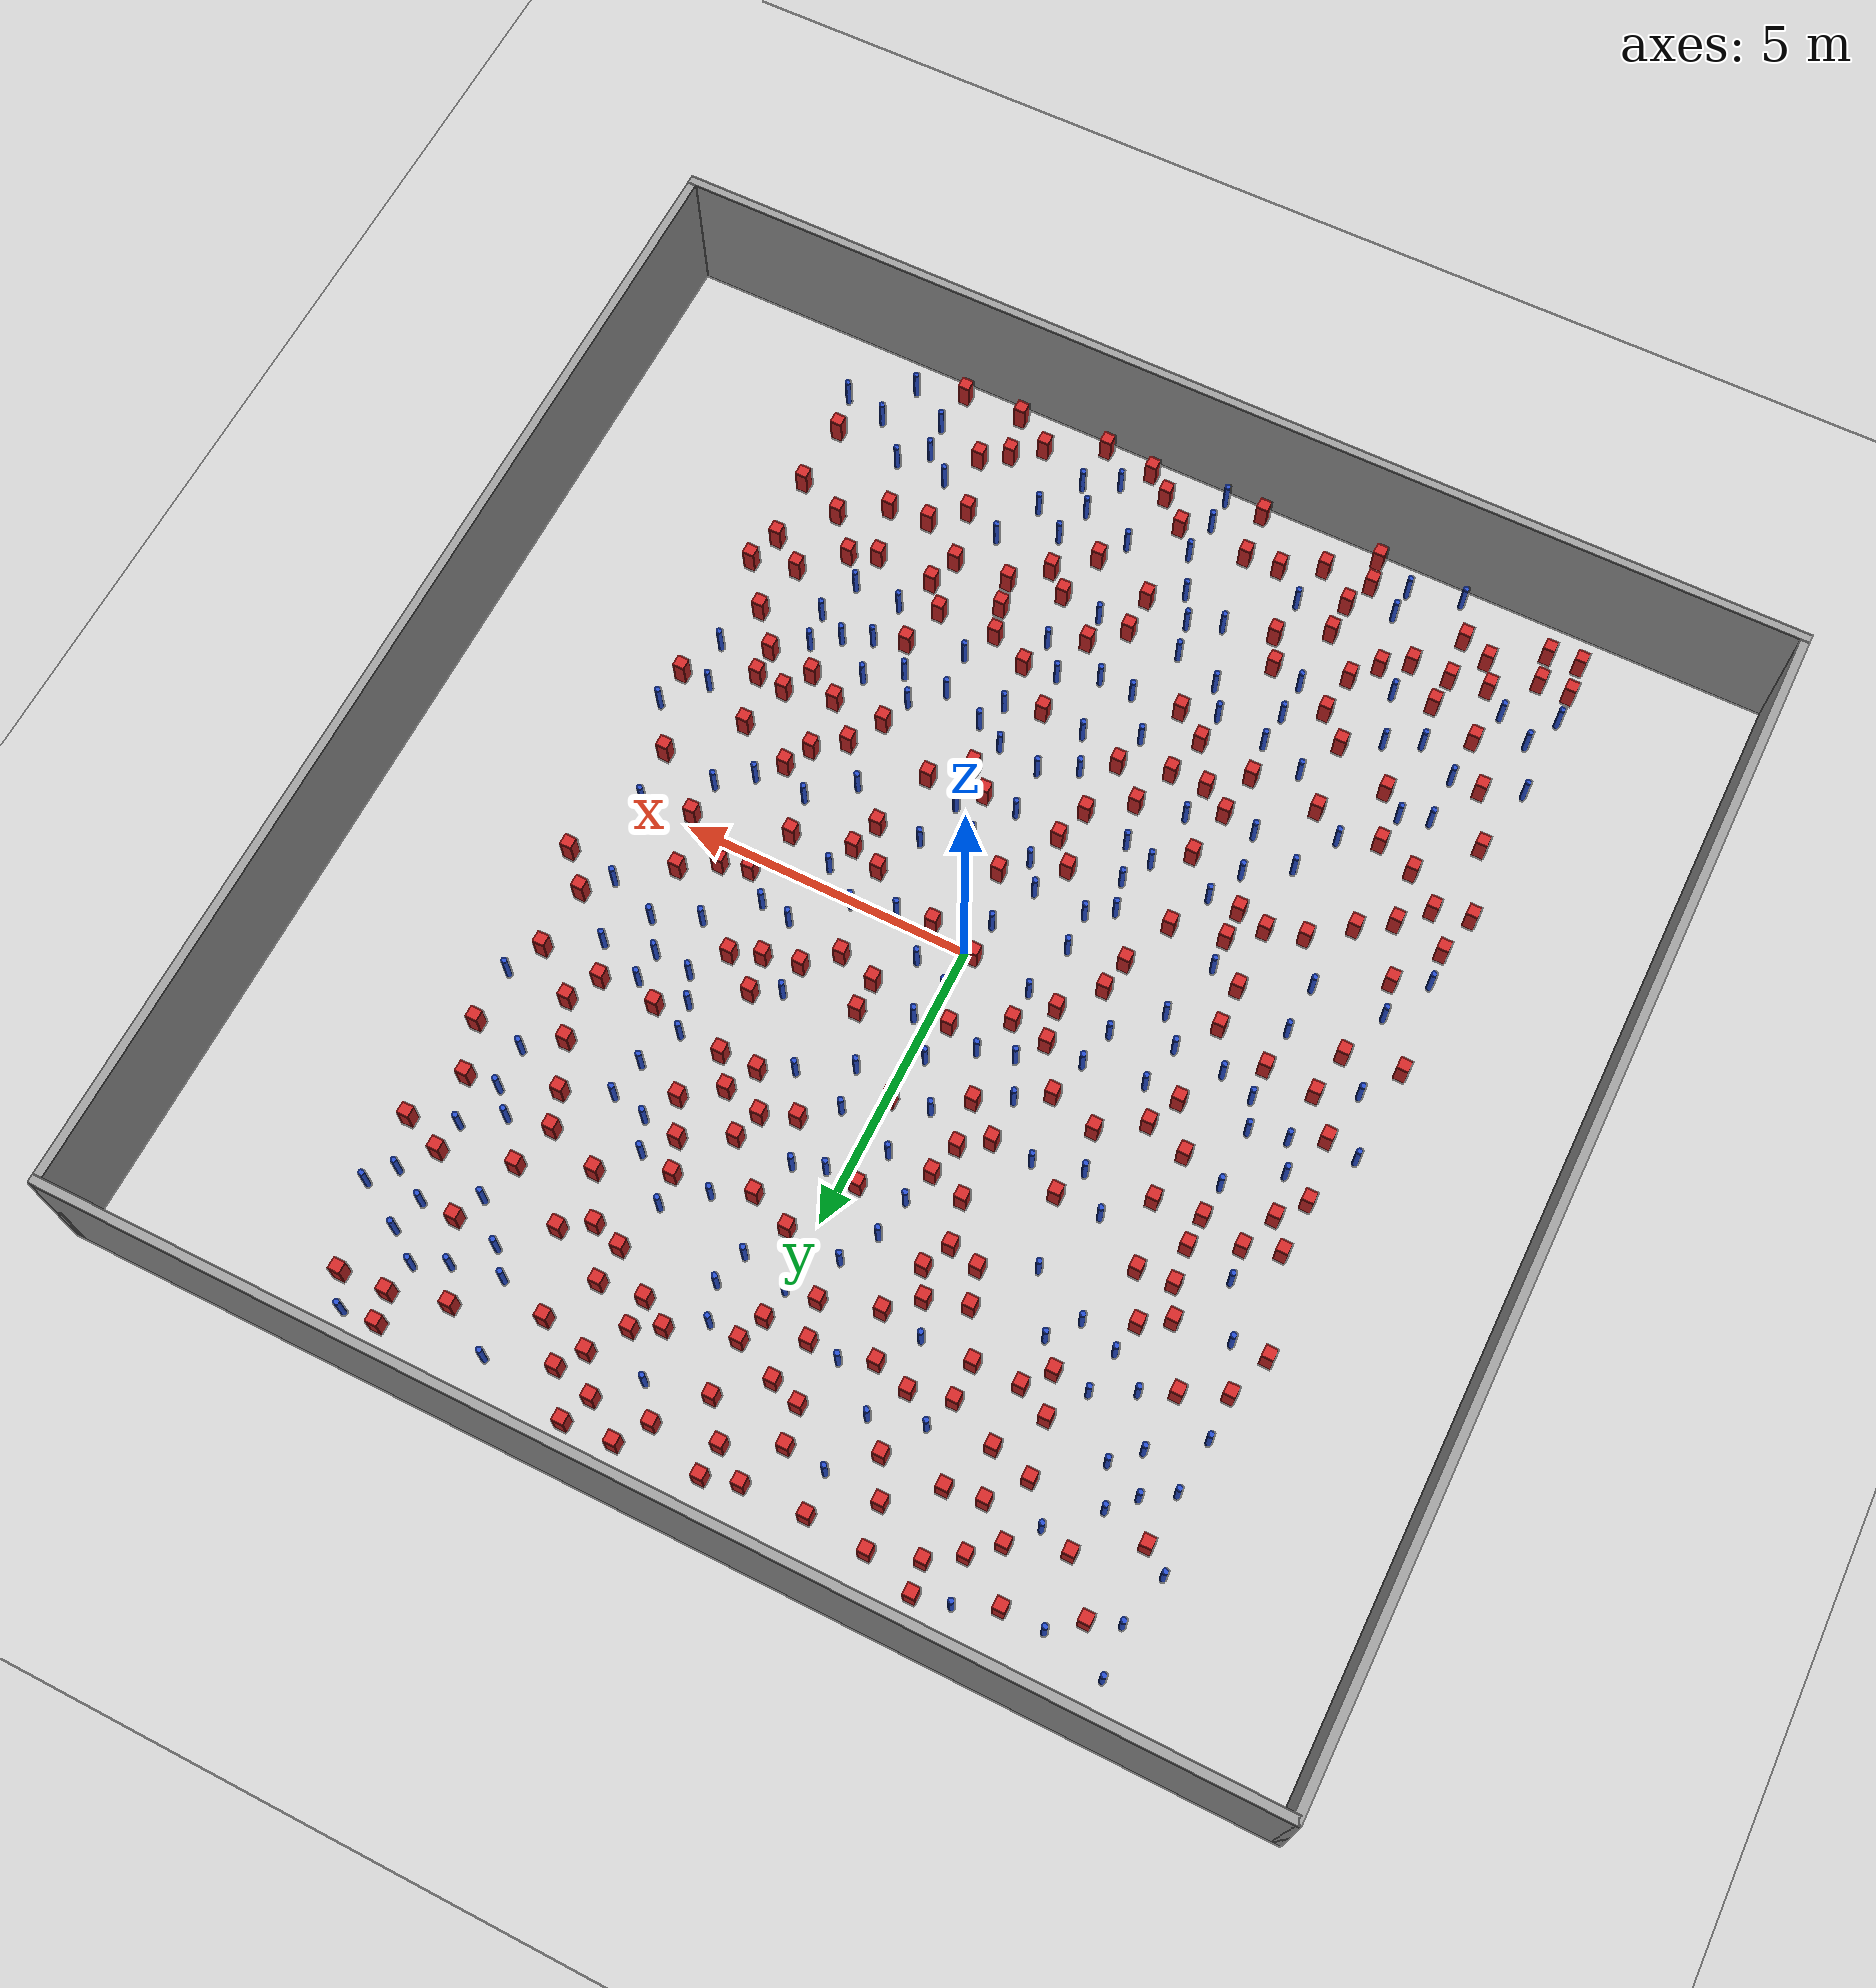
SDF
<sdf version="1.6">
 <world name="default">
  <light name="sun" type="directional">
   <pose>0 0 1000 0 -0 0</pose>
   <diffuse>0.8 0.8 0.8 1</diffuse>
   <specular>0.1 0.1 0.1 1</specular>
   <attenuation>
    <range>1000</range>
    <constant>0.9</constant>
    <linear>0.01</linear>
    <quadratic>0.001</quadratic>
   </attenuation>
   <direction>-0.5 0.5 -1</direction>
  </light>
  <model name="ground_plane">
   <static>1</static>
   <link name="link">
    <collision name="collision">
     <geometry><plane><normal>0 0 1</normal><size>100 100</size></plane></geometry>
     <surface><friction><ode><mu>100</mu><mu2>50</mu2></ode></friction></surface>
    </collision>
    <visual name="visual">
     <cast_shadows>0</cast_shadows>
     <geometry><plane><normal>0 0 1</normal><size>100 100</size></plane></geometry>
     <material>
      <ambient>1.0 1.0 1.0 1.0</ambient>
      <diffuse>0.8 0.8 0.8 1.0</diffuse>
      <specular>0.01 0.01 0.01 1.000000</specular>
     </material>
    </visual>
   </link>
  </model>
  <gravity>0 0 -9.8</gravity>
  <magnetic_field>6e-06 2.3e-05 -4.2e-05</magnetic_field>
  <atmosphere type="adiabatic"/>
  <physics name="default_physics" default="0" type="ode">
   <max_step_size>0.001</max_step_size>
   <real_time_factor>1</real_time_factor>
   <real_time_update_rate>1000</real_time_update_rate>
  </physics>
  <scene><ambient>0.4 0.4 0.4 1</ambient><background>0.7 0.7 0.7 1</background><shadows>1</shadows></scene>
  <spherical_coordinates>
   <surface_model>EARTH_WGS84</surface_model>
   <latitude_deg>0</latitude_deg>
   <longitude_deg>0</longitude_deg>
   <elevation>0</elevation>
   <heading_deg>0</heading_deg>
  </spherical_coordinates>
  <plugin name="gazebo_occupancy_map" filename="libgazebo_2Dmap_plugin.so">
   <map_resolution>0.05</map_resolution>
   <map_topic>generated_map</map_topic>
   <map_height>0.01</map_height>
   <map_size_x>50</map_size_x>
   <map_size_y>50</map_size_y>
  </plugin>
  <model name="NamedLocations">
   <static>true</static>
   <link name="DefaultStart"><pose>8.5 0 0 0 0 3.14</pose></link>
  </model>
  <model name="20x20_walls">
   <pose>0.044518 0.176112 0 0 -0 0</pose>
   <link name="Wall_1">
    <collision name="Wall_1_Collision">
     <geometry><box><size>20 0.15 2.5</size></box></geometry>
     <pose>0 0 1.25 0 -0 0</pose>
    </collision>
    <visual name="Wall_1_Visual">
     <pose>0 0 1.25 0 -0 0</pose>
     <geometry><box><size>20 0.15 2.5</size></box></geometry>
     <material>
      <script><uri>file://media/materials/scripts/gazebo.material</uri><name>Gazebo/Grey</name></script>
      <ambient>0.976471 0.992157 1 1</ambient>
     </material>
     <meta><layer>0</layer></meta>
    </visual>
    <pose>0 9.925 0 0 -0 0</pose>
   </link>
   <link name="Wall_3">
    <collision name="Wall_3_Collision">
     <geometry><box><size>20 0.15 2.5</size></box></geometry>
     <pose>0 0 1.25 0 -0 0</pose>
    </collision>
    <visual name="Wall_3_Visual">
     <pose>0 0 1.25 0 -0 0</pose>
     <geometry><box><size>20 0.15 2.5</size></box></geometry>
     <material>
      <script><uri>file://media/materials/scripts/gazebo.material</uri><name>Gazebo/Grey</name></script>
      <ambient>0.976471 0.992157 1 1</ambient>
     </material>
     <meta><layer>0</layer></meta>
    </visual>
    <pose>9.925 0 0 0 0 -1.5708</pose>
   </link>
   <link name="Wall_4">
    <collision name="Wall_4_Collision">
     <geometry><box><size>20 0.15 2.5</size></box></geometry>
     <pose>0 0 1.25 0 -0 0</pose>
    </collision>
    <visual name="Wall_4_Visual">
     <pose>0 0 1.25 0 -0 0</pose>
     <geometry><box><size>20 0.15 2.5</size></box></geometry>
     <material>
      <script><uri>file://media/materials/scripts/gazebo.material</uri><name>Gazebo/Grey</name></script>
      <ambient>0.976471 0.992157 1 1</ambient>
     </material>
     <meta><layer>0</layer></meta>
    </visual>
    <pose>0 -9.925 0 0 -0 3.14159</pose>
   </link>
   <link name="Wall_5">
    <collision name="Wall_5_Collision">
     <geometry><box><size>20 0.15 2.5</size></box></geometry>
     <pose>0 0 1.25 0 -0 0</pose>
    </collision>
    <visual name="Wall_5_Visual">
     <pose>0 0 1.25 0 -0 0</pose>
     <geometry><box><size>20 0.15 2.5</size></box></geometry>
     <material>
      <script><uri>file://media/materials/scripts/gazebo.material</uri><name>Gazebo/Grey</name></script>
      <ambient>0.976471 0.992157 1 1</ambient>
     </material>
     <meta><layer>0</layer></meta>
    </visual>
    <pose>-9.925 0 0 0 -0 1.5708</pose>
   </link>
   <static>1</static>
  </model>
  <model name="square_post_obstacle0">
   <static>true</static>
   <pose>0.162283778039 8.10898161146 8.22691968438e-08 7.22125133819e-06 -7.54495500217e-07 2.29674213826e-05</pose>
   <link name="link">
    <pose>0 0 0.25 0 -0 0</pose>
    <inertial>
     <mass>100</mass>
     <inertia>
      <ixx>0.166667</ixx>
      <ixy>0</ixy>
      <ixz>0</ixz>
      <iyy>0.166667</iyy>
      <iyz>0</iyz>
      <izz>0.166667</izz>
     </inertia>
    </inertial>
    <collision name="collision"><geometry><box><size>.2 .2 .5</size></box></geometry></collision>
    <visual name="visual">
     <geometry><box><size>.2 .2 .5</size></box></geometry>
     <material>
      <script><name>Gazebo/Red</name><uri>file://media/materials/scripts/gazebo.material</uri></script>
     </material>
    </visual>
   </link>
  </model>
  <model name="square_post_obstacle1">
   <static>true</static>
   <pose>-6.19454957037 8.60646910702 8.22691968438e-08 7.22125133819e-06 -7.54495500217e-07 2.29674213826e-05</pose>
   <link name="link">
    <pose>0 0 0.25 0 -0 0</pose>
    <inertial>
     <mass>100</mass>
     <inertia>
      <ixx>0.166667</ixx>
      <ixy>0</ixy>
      <ixz>0</ixz>
      <iyy>0.166667</iyy>
      <iyz>0</iyz>
      <izz>0.166667</izz>
     </inertia>
    </inertial>
    <collision name="collision"><geometry><box><size>.2 .2 .5</size></box></geometry></collision>
    <visual name="visual">
     <geometry><box><size>.2 .2 .5</size></box></geometry>
     <material>
      <script><name>Gazebo/Red</name><uri>file://media/materials/scripts/gazebo.material</uri></script>
     </material>
    </visual>
   </link>
  </model>
  <model name="pole_obstacle0">
   <static>true</static>
   <pose>-2.14201029475 -3.68788135447 2.88873142074e-08 -9.90536690232e-09 4.6021994898e-07 -1.20965994968e-07</pose>
   <link name="link">
    <pose>0 0 0.3 0 -0 0</pose>
    <inertial>
     <mass>1</mass>
     <inertia><ixx>0.145833</ixx><ixy>0</ixy><ixz>0</ixz><iyy>0.145833</iyy><iyz>0</iyz><izz>0.125</izz></inertia>
    </inertial>
    <collision name="collision">
     <geometry><cylinder><radius>0.05</radius><length>.6</length></cylinder></geometry>
    </collision>
    <visual name="visual">
     <geometry><cylinder><radius>0.05</radius><length>.6</length></cylinder></geometry>
     <material>
      <script><name>Gazebo/Blue</name><uri>file://media/materials/scripts/gazebo.material</uri></script>
     </material>
    </visual>
   </link>
  </model>
  <model name="square_post_obstacle2">
   <static>true</static>
   <pose>1.05752300624 1.68176623114 8.22691968438e-08 7.2212513382e-06 -7.54495500217e-07 2.29674213826e-05</pose>
   <link name="link">
    <pose>0 0 0.25 0 -0 0</pose>
    <inertial>
     <mass>100</mass>
     <inertia>
      <ixx>0.166667</ixx>
      <ixy>0</ixy>
      <ixz>0</ixz>
      <iyy>0.166667</iyy>
      <iyz>0</iyz>
      <izz>0.166667</izz>
     </inertia>
    </inertial>
    <collision name="collision"><geometry><box><size>.2 .2 .5</size></box></geometry></collision>
    <visual name="visual">
     <geometry><box><size>.2 .2 .5</size></box></geometry>
     <material>
      <script><name>Gazebo/Red</name><uri>file://media/materials/scripts/gazebo.material</uri></script>
     </material>
    </visual>
   </link>
  </model>
  <model name="pole_obstacle1">
   <static>true</static>
   <pose>-0.185130693116 -0.5815067164 2.88873142074e-08 -9.90536690341e-09 4.60219948977e-07 -1.20965994968e-07</pose>
   <link name="link">
    <pose>0 0 0.3 0 -0 0</pose>
    <inertial>
     <mass>1</mass>
     <inertia><ixx>0.145833</ixx><ixy>0</ixy><ixz>0</ixz><iyy>0.145833</iyy><iyz>0</iyz><izz>0.125</izz></inertia>
    </inertial>
    <collision name="collision">
     <geometry><cylinder><radius>0.05</radius><length>.6</length></cylinder></geometry>
    </collision>
    <visual name="visual">
     <geometry><cylinder><radius>0.05</radius><length>.6</length></cylinder></geometry>
     <material>
      <script><name>Gazebo/Blue</name><uri>file://media/materials/scripts/gazebo.material</uri></script>
     </material>
    </visual>
   </link>
  </model>
  <model name="square_post_obstacle3">
   <static>true</static>
   <pose>-4.63655862718 3.54686875721 8.22691968438e-08 7.2212513382e-06 -7.54495500217e-07 2.29674213826e-05</pose>
   <link name="link">
    <pose>0 0 0.25 0 -0 0</pose>
    <inertial>
     <mass>100</mass>
     <inertia>
      <ixx>0.166667</ixx>
      <ixy>0</ixy>
      <ixz>0</ixz>
      <iyy>0.166667</iyy>
      <iyz>0</iyz>
      <izz>0.166667</izz>
     </inertia>
    </inertial>
    <collision name="collision"><geometry><box><size>.2 .2 .5</size></box></geometry></collision>
    <visual name="visual">
     <geometry><box><size>.2 .2 .5</size></box></geometry>
     <material>
      <script><name>Gazebo/Red</name><uri>file://media/materials/scripts/gazebo.material</uri></script>
     </material>
    </visual>
   </link>
  </model>
  <model name="pole_obstacle2">
   <static>true</static>
   <pose>5.08456096879 -7.63370993622 2.88873142074e-08 -9.90536690842e-09 4.60219948965e-07 -1.20965994976e-07</pose>
   <link name="link">
    <pose>0 0 0.3 0 -0 0</pose>
    <inertial>
     <mass>1</mass>
     <inertia><ixx>0.145833</ixx><ixy>0</ixy><ixz>0</ixz><iyy>0.145833</iyy><iyz>0</iyz><izz>0.125</izz></inertia>
    </inertial>
    <collision name="collision">
     <geometry><cylinder><radius>0.05</radius><length>.6</length></cylinder></geometry>
    </collision>
    <visual name="visual">
     <geometry><cylinder><radius>0.05</radius><length>.6</length></cylinder></geometry>
     <material>
      <script><name>Gazebo/Blue</name><uri>file://media/materials/scripts/gazebo.material</uri></script>
     </material>
    </visual>
   </link>
  </model>
  <model name="pole_obstacle3">
   <static>true</static>
   <pose>1.75412683638 -8.16297282722 2.88873142074e-08 -9.90536690474e-09 4.60219948974e-07 -1.2096599497e-07</pose>
   <link name="link">
    <pose>0 0 0.3 0 -0 0</pose>
    <inertial>
     <mass>1</mass>
     <inertia><ixx>0.145833</ixx><ixy>0</ixy><ixz>0</ixz><iyy>0.145833</iyy><iyz>0</iyz><izz>0.125</izz></inertia>
    </inertial>
    <collision name="collision">
     <geometry><cylinder><radius>0.05</radius><length>.6</length></cylinder></geometry>
    </collision>
    <visual name="visual">
     <geometry><cylinder><radius>0.05</radius><length>.6</length></cylinder></geometry>
     <material>
      <script><name>Gazebo/Blue</name><uri>file://media/materials/scripts/gazebo.material</uri></script>
     </material>
    </visual>
   </link>
  </model>
  <model name="square_post_obstacle4">
   <static>true</static>
   <pose>-5.02430146812 8.98902265798 8.22691968438e-08 7.22125133819e-06 -7.54495500217e-07 2.29674213826e-05</pose>
   <link name="link">
    <pose>0 0 0.25 0 -0 0</pose>
    <inertial>
     <mass>100</mass>
     <inertia>
      <ixx>0.166667</ixx>
      <ixy>0</ixy>
      <ixz>0</ixz>
      <iyy>0.166667</iyy>
      <iyz>0</iyz>
      <izz>0.166667</izz>
     </inertia>
    </inertial>
    <collision name="collision"><geometry><box><size>.2 .2 .5</size></box></geometry></collision>
    <visual name="visual">
     <geometry><box><size>.2 .2 .5</size></box></geometry>
     <material>
      <script><name>Gazebo/Red</name><uri>file://media/materials/scripts/gazebo.material</uri></script>
     </material>
    </visual>
   </link>
  </model>
  <model name="square_post_obstacle5">
   <static>true</static>
   <pose>4.07274696341 -1.62590643043 8.22691968438e-08 7.2212513382e-06 -7.54495500217e-07 2.29674213826e-05</pose>
   <link name="link">
    <pose>0 0 0.25 0 -0 0</pose>
    <inertial>
     <mass>100</mass>
     <inertia>
      <ixx>0.166667</ixx>
      <ixy>0</ixy>
      <ixz>0</ixz>
      <iyy>0.166667</iyy>
      <iyz>0</iyz>
      <izz>0.166667</izz>
     </inertia>
    </inertial>
    <collision name="collision"><geometry><box><size>.2 .2 .5</size></box></geometry></collision>
    <visual name="visual">
     <geometry><box><size>.2 .2 .5</size></box></geometry>
     <material>
      <script><name>Gazebo/Red</name><uri>file://media/materials/scripts/gazebo.material</uri></script>
     </material>
    </visual>
   </link>
  </model>
  <model name="square_post_obstacle6">
   <static>true</static>
   <pose>-3.40146848392 -6.44228266172 8.22691968438e-08 7.2212513382e-06 -7.54495500217e-07 2.29674213826e-05</pose>
   <link name="link">
    <pose>0 0 0.25 0 -0 0</pose>
    <inertial>
     <mass>100</mass>
     <inertia>
      <ixx>0.166667</ixx>
      <ixy>0</ixy>
      <ixz>0</ixz>
      <iyy>0.166667</iyy>
      <iyz>0</iyz>
      <izz>0.166667</izz>
     </inertia>
    </inertial>
    <collision name="collision"><geometry><box><size>.2 .2 .5</size></box></geometry></collision>
    <visual name="visual">
     <geometry><box><size>.2 .2 .5</size></box></geometry>
     <material>
      <script><name>Gazebo/Red</name><uri>file://media/materials/scripts/gazebo.material</uri></script>
     </material>
    </visual>
   </link>
  </model>
  <model name="pole_obstacle4">
   <static>true</static>
   <pose>1.2756648102 -0.111418900228 2.88873142074e-08 -9.90536689715e-09 4.60219948992e-07 -1.20965994959e-07</pose>
   <link name="link">
    <pose>0 0 0.3 0 -0 0</pose>
    <inertial>
     <mass>1</mass>
     <inertia><ixx>0.145833</ixx><ixy>0</ixy><ixz>0</ixz><iyy>0.145833</iyy><iyz>0</iyz><izz>0.125</izz></inertia>
    </inertial>
    <collision name="collision">
     <geometry><cylinder><radius>0.05</radius><length>.6</length></cylinder></geometry>
    </collision>
    <visual name="visual">
     <geometry><cylinder><radius>0.05</radius><length>.6</length></cylinder></geometry>
     <material>
      <script><name>Gazebo/Blue</name><uri>file://media/materials/scripts/gazebo.material</uri></script>
     </material>
    </visual>
   </link>
  </model>
  <model name="pole_obstacle5">
   <static>true</static>
   <pose>2.58989376314 -0.327966249412 2.88873142074e-08 -9.90536689307e-09 4.60219949002e-07 -1.20965994954e-07</pose>
   <link name="link">
    <pose>0 0 0.3 0 -0 0</pose>
    <inertial>
     <mass>1</mass>
     <inertia><ixx>0.145833</ixx><ixy>0</ixy><ixz>0</ixz><iyy>0.145833</iyy><iyz>0</iyz><izz>0.125</izz></inertia>
    </inertial>
    <collision name="collision">
     <geometry><cylinder><radius>0.05</radius><length>.6</length></cylinder></geometry>
    </collision>
    <visual name="visual">
     <geometry><cylinder><radius>0.05</radius><length>.6</length></cylinder></geometry>
     <material>
      <script><name>Gazebo/Blue</name><uri>file://media/materials/scripts/gazebo.material</uri></script>
     </material>
    </visual>
   </link>
  </model>
  <model name="square_post_obstacle7">
   <static>true</static>
   <pose>3.69847838354 0.283628622711 8.22691968438e-08 7.2212513382e-06 -7.54495500217e-07 2.29674213826e-05</pose>
   <link name="link">
    <pose>0 0 0.25 0 -0 0</pose>
    <inertial>
     <mass>100</mass>
     <inertia>
      <ixx>0.166667</ixx>
      <ixy>0</ixy>
      <ixz>0</ixz>
      <iyy>0.166667</iyy>
      <iyz>0</iyz>
      <izz>0.166667</izz>
     </inertia>
    </inertial>
    <collision name="collision"><geometry><box><size>.2 .2 .5</size></box></geometry></collision>
    <visual name="visual">
     <geometry><box><size>.2 .2 .5</size></box></geometry>
     <material>
      <script><name>Gazebo/Red</name><uri>file://media/materials/scripts/gazebo.material</uri></script>
     </material>
    </visual>
   </link>
  </model>
  <model name="square_post_obstacle8">
   <static>true</static>
   <pose>-4.58548154506 7.12806164214 8.22691968438e-08 7.2212513382e-06 -7.54495500217e-07 2.29674213826e-05</pose>
   <link name="link">
    <pose>0 0 0.25 0 -0 0</pose>
    <inertial>
     <mass>100</mass>
     <inertia>
      <ixx>0.166667</ixx>
      <ixy>0</ixy>
      <ixz>0</ixz>
      <iyy>0.166667</iyy>
      <iyz>0</iyz>
      <izz>0.166667</izz>
     </inertia>
    </inertial>
    <collision name="collision"><geometry><box><size>.2 .2 .5</size></box></geometry></collision>
    <visual name="visual">
     <geometry><box><size>.2 .2 .5</size></box></geometry>
     <material>
      <script><name>Gazebo/Red</name><uri>file://media/materials/scripts/gazebo.material</uri></script>
     </material>
    </visual>
   </link>
  </model>
  <model name="pole_obstacle6">
   <static>true</static>
   <pose>-5.90542350853 6.01039397077 2.88873142074e-08 -9.90536690842e-09 4.60219948965e-07 -1.20965994976e-07</pose>
   <link name="link">
    <pose>0 0 0.3 0 -0 0</pose>
    <inertial>
     <mass>1</mass>
     <inertia><ixx>0.145833</ixx><ixy>0</ixy><ixz>0</ixz><iyy>0.145833</iyy><iyz>0</iyz><izz>0.125</izz></inertia>
    </inertial>
    <collision name="collision">
     <geometry><cylinder><radius>0.05</radius><length>.6</length></cylinder></geometry>
    </collision>
    <visual name="visual">
     <geometry><cylinder><radius>0.05</radius><length>.6</length></cylinder></geometry>
     <material>
      <script><name>Gazebo/Blue</name><uri>file://media/materials/scripts/gazebo.material</uri></script>
     </material>
    </visual>
   </link>
  </model>
  <model name="pole_obstacle7">
   <static>true</static>
   <pose>0.757397420686 5.97443957552 2.88873142074e-08 -9.90536689661e-09 4.60219948993e-07 -1.20965994957e-07</pose>
   <link name="link">
    <pose>0 0 0.3 0 -0 0</pose>
    <inertial>
     <mass>1</mass>
     <inertia><ixx>0.145833</ixx><ixy>0</ixy><ixz>0</ixz><iyy>0.145833</iyy><iyz>0</iyz><izz>0.125</izz></inertia>
    </inertial>
    <collision name="collision">
     <geometry><cylinder><radius>0.05</radius><length>.6</length></cylinder></geometry>
    </collision>
    <visual name="visual">
     <geometry><cylinder><radius>0.05</radius><length>.6</length></cylinder></geometry>
     <material>
      <script><name>Gazebo/Blue</name><uri>file://media/materials/scripts/gazebo.material</uri></script>
     </material>
    </visual>
   </link>
  </model>
  <model name="square_post_obstacle9">
   <static>true</static>
   <pose>-6.22999508174 -6.23063073512 8.22691968438e-08 7.2212513382e-06 -7.54495500217e-07 2.29674213826e-05</pose>
   <link name="link">
    <pose>0 0 0.25 0 -0 0</pose>
    <inertial>
     <mass>100</mass>
     <inertia>
      <ixx>0.166667</ixx>
      <ixy>0</ixy>
      <ixz>0</ixz>
      <iyy>0.166667</iyy>
      <iyz>0</iyz>
      <izz>0.166667</izz>
     </inertia>
    </inertial>
    <collision name="collision"><geometry><box><size>.2 .2 .5</size></box></geometry></collision>
    <visual name="visual">
     <geometry><box><size>.2 .2 .5</size></box></geometry>
     <material>
      <script><name>Gazebo/Red</name><uri>file://media/materials/scripts/gazebo.material</uri></script>
     </material>
    </visual>
   </link>
  </model>
  <model name="square_post_obstacle10">
   <static>true</static>
   <pose>1.06012387388 1.13206869176 8.22691968438e-08 7.2212513382e-06 -7.54495500217e-07 2.29674213826e-05</pose>
   <link name="link">
    <pose>0 0 0.25 0 -0 0</pose>
    <inertial>
     <mass>100</mass>
     <inertia>
      <ixx>0.166667</ixx>
      <ixy>0</ixy>
      <ixz>0</ixz>
      <iyy>0.166667</iyy>
      <iyz>0</iyz>
      <izz>0.166667</izz>
     </inertia>
    </inertial>
    <collision name="collision"><geometry><box><size>.2 .2 .5</size></box></geometry></collision>
    <visual name="visual">
     <geometry><box><size>.2 .2 .5</size></box></geometry>
     <material>
      <script><name>Gazebo/Red</name><uri>file://media/materials/scripts/gazebo.material</uri></script>
     </material>
    </visual>
   </link>
  </model>
  <model name="square_post_obstacle11">
   <static>true</static>
   <pose>-1.62586627458 -8.59294404825 8.22691968438e-08 7.22125133819e-06 -7.54495500217e-07 2.29674213826e-05</pose>
   <link name="link">
    <pose>0 0 0.25 0 -0 0</pose>
    <inertial>
     <mass>100</mass>
     <inertia>
      <ixx>0.166667</ixx>
      <ixy>0</ixy>
      <ixz>0</ixz>
      <iyy>0.166667</iyy>
      <iyz>0</iyz>
      <izz>0.166667</izz>
     </inertia>
    </inertial>
    <collision name="collision"><geometry><box><size>.2 .2 .5</size></box></geometry></collision>
    <visual name="visual">
     <geometry><box><size>.2 .2 .5</size></box></geometry>
     <material>
      <script><name>Gazebo/Red</name><uri>file://media/materials/scripts/gazebo.material</uri></script>
     </material>
    </visual>
   </link>
  </model>
  <model name="square_post_obstacle12">
   <static>true</static>
   <pose>2.08199648702 -5.32711018315 8.22691968438e-08 7.22125133819e-06 -7.54495500217e-07 2.29674213826e-05</pose>
   <link name="link">
    <pose>0 0 0.25 0 -0 0</pose>
    <inertial>
     <mass>100</mass>
     <inertia>
      <ixx>0.166667</ixx>
      <ixy>0</ixy>
      <ixz>0</ixz>
      <iyy>0.166667</iyy>
      <iyz>0</iyz>
      <izz>0.166667</izz>
     </inertia>
    </inertial>
    <collision name="collision"><geometry><box><size>.2 .2 .5</size></box></geometry></collision>
    <visual name="visual">
     <geometry><box><size>.2 .2 .5</size></box></geometry>
     <material>
      <script><name>Gazebo/Red</name><uri>file://media/materials/scripts/gazebo.material</uri></script>
     </material>
    </visual>
   </link>
  </model>
  <model name="square_post_obstacle13">
   <static>true</static>
   <pose>4.74317763244 -2.84132104916 8.22691968438e-08 7.2212513382e-06 -7.54495500217e-07 2.29674213826e-05</pose>
   <link name="link">
    <pose>0 0 0.25 0 -0 0</pose>
    <inertial>
     <mass>100</mass>
     <inertia>
      <ixx>0.166667</ixx>
      <ixy>0</ixy>
      <ixz>0</ixz>
      <iyy>0.166667</iyy>
      <iyz>0</iyz>
      <izz>0.166667</izz>
     </inertia>
    </inertial>
    <collision name="collision"><geometry><box><size>.2 .2 .5</size></box></geometry></collision>
    <visual name="visual">
     <geometry><box><size>.2 .2 .5</size></box></geometry>
     <material>
      <script><name>Gazebo/Red</name><uri>file://media/materials/scripts/gazebo.material</uri></script>
     </material>
    </visual>
   </link>
  </model>
  <model name="pole_obstacle8">
   <static>true</static>
   <pose>4.94769768114 -0.812549255114 2.88873142074e-08 -9.90536689837e-09 4.60219948989e-07 -1.2096599496e-07</pose>
   <link name="link">
    <pose>0 0 0.3 0 -0 0</pose>
    <inertial>
     <mass>1</mass>
     <inertia><ixx>0.145833</ixx><ixy>0</ixy><ixz>0</ixz><iyy>0.145833</iyy><iyz>0</iyz><izz>0.125</izz></inertia>
    </inertial>
    <collision name="collision">
     <geometry><cylinder><radius>0.05</radius><length>.6</length></cylinder></geometry>
    </collision>
    <visual name="visual">
     <geometry><cylinder><radius>0.05</radius><length>.6</length></cylinder></geometry>
     <material>
      <script><name>Gazebo/Blue</name><uri>file://media/materials/scripts/gazebo.material</uri></script>
     </material>
    </visual>
   </link>
  </model>
  <model name="square_post_obstacle14">
   <static>true</static>
   <pose>-5.78041702265 -7.02790557127 8.22691968438e-08 7.22125133819e-06 -7.54495500217e-07 2.29674213826e-05</pose>
   <link name="link">
    <pose>0 0 0.25 0 -0 0</pose>
    <inertial>
     <mass>100</mass>
     <inertia>
      <ixx>0.166667</ixx>
      <ixy>0</ixy>
      <ixz>0</ixz>
      <iyy>0.166667</iyy>
      <iyz>0</iyz>
      <izz>0.166667</izz>
     </inertia>
    </inertial>
    <collision name="collision"><geometry><box><size>.2 .2 .5</size></box></geometry></collision>
    <visual name="visual">
     <geometry><box><size>.2 .2 .5</size></box></geometry>
     <material>
      <script><name>Gazebo/Red</name><uri>file://media/materials/scripts/gazebo.material</uri></script>
     </material>
    </visual>
   </link>
  </model>
  <model name="square_post_obstacle15">
   <static>true</static>
   <pose>-5.24015183878 3.50548727674 8.22691968438e-08 7.2212513382e-06 -7.54495500217e-07 2.29674213826e-05</pose>
   <link name="link">
    <pose>0 0 0.25 0 -0 0</pose>
    <inertial>
     <mass>100</mass>
     <inertia>
      <ixx>0.166667</ixx>
      <ixy>0</ixy>
      <ixz>0</ixz>
      <iyy>0.166667</iyy>
      <iyz>0</iyz>
      <izz>0.166667</izz>
     </inertia>
    </inertial>
    <collision name="collision"><geometry><box><size>.2 .2 .5</size></box></geometry></collision>
    <visual name="visual">
     <geometry><box><size>.2 .2 .5</size></box></geometry>
     <material>
      <script><name>Gazebo/Red</name><uri>file://media/materials/scripts/gazebo.material</uri></script>
     </material>
    </visual>
   </link>
  </model>
  <model name="square_post_obstacle16">
   <static>true</static>
   <pose>-3.82299562267 1.35734232729 8.22691968438e-08 7.2212513382e-06 -7.54495500217e-07 2.29674213826e-05</pose>
   <link name="link">
    <pose>0 0 0.25 0 -0 0</pose>
    <inertial>
     <mass>100</mass>
     <inertia>
      <ixx>0.166667</ixx>
      <ixy>0</ixy>
      <ixz>0</ixz>
      <iyy>0.166667</iyy>
      <iyz>0</iyz>
      <izz>0.166667</izz>
     </inertia>
    </inertial>
    <collision name="collision"><geometry><box><size>.2 .2 .5</size></box></geometry></collision>
    <visual name="visual">
     <geometry><box><size>.2 .2 .5</size></box></geometry>
     <material>
      <script><name>Gazebo/Red</name><uri>file://media/materials/scripts/gazebo.material</uri></script>
     </material>
    </visual>
   </link>
  </model>
  <model name="pole_obstacle9">
   <static>true</static>
   <pose>-2.82991241068 -6.70532986122 2.88873142074e-08 -9.90536689859e-09 4.60219948989e-07 -1.20965994961e-07</pose>
   <link name="link">
    <pose>0 0 0.3 0 -0 0</pose>
    <inertial>
     <mass>1</mass>
     <inertia><ixx>0.145833</ixx><ixy>0</ixy><ixz>0</ixz><iyy>0.145833</iyy><iyz>0</iyz><izz>0.125</izz></inertia>
    </inertial>
    <collision name="collision">
     <geometry><cylinder><radius>0.05</radius><length>.6</length></cylinder></geometry>
    </collision>
    <visual name="visual">
     <geometry><cylinder><radius>0.05</radius><length>.6</length></cylinder></geometry>
     <material>
      <script><name>Gazebo/Blue</name><uri>file://media/materials/scripts/gazebo.material</uri></script>
     </material>
    </visual>
   </link>
  </model>
  <model name="square_post_obstacle17">
   <static>true</static>
   <pose>4.7562189727 0.773854882955 8.22691968438e-08 7.2212513382e-06 -7.54495500217e-07 2.29674213826e-05</pose>
   <link name="link">
    <pose>0 0 0.25 0 -0 0</pose>
    <inertial>
     <mass>100</mass>
     <inertia>
      <ixx>0.166667</ixx>
      <ixy>0</ixy>
      <ixz>0</ixz>
      <iyy>0.166667</iyy>
      <iyz>0</iyz>
      <izz>0.166667</izz>
     </inertia>
    </inertial>
    <collision name="collision"><geometry><box><size>.2 .2 .5</size></box></geometry></collision>
    <visual name="visual">
     <geometry><box><size>.2 .2 .5</size></box></geometry>
     <material>
      <script><name>Gazebo/Red</name><uri>file://media/materials/scripts/gazebo.material</uri></script>
     </material>
    </visual>
   </link>
  </model>
  <model name="square_post_obstacle18">
   <static>true</static>
   <pose>2.39872946446 -0.807188189583 8.22691968438e-08 7.2212513382e-06 -7.54495500217e-07 2.29674213826e-05</pose>
   <link name="link">
    <pose>0 0 0.25 0 -0 0</pose>
    <inertial>
     <mass>100</mass>
     <inertia>
      <ixx>0.166667</ixx>
      <ixy>0</ixy>
      <ixz>0</ixz>
      <iyy>0.166667</iyy>
      <iyz>0</iyz>
      <izz>0.166667</izz>
     </inertia>
    </inertial>
    <collision name="collision"><geometry><box><size>.2 .2 .5</size></box></geometry></collision>
    <visual name="visual">
     <geometry><box><size>.2 .2 .5</size></box></geometry>
     <material>
      <script><name>Gazebo/Red</name><uri>file://media/materials/scripts/gazebo.material</uri></script>
     </material>
    </visual>
   </link>
  </model>
  <model name="pole_obstacle10">
   <static>true</static>
   <pose>1.58691725315 -3.72829903937 2.88873142074e-08 -9.90536689791e-09 4.6021994899e-07 -1.20965994959e-07</pose>
   <link name="link">
    <pose>0 0 0.3 0 -0 0</pose>
    <inertial>
     <mass>1</mass>
     <inertia><ixx>0.145833</ixx><ixy>0</ixy><ixz>0</ixz><iyy>0.145833</iyy><iyz>0</iyz><izz>0.125</izz></inertia>
    </inertial>
    <collision name="collision">
     <geometry><cylinder><radius>0.05</radius><length>.6</length></cylinder></geometry>
    </collision>
    <visual name="visual">
     <geometry><cylinder><radius>0.05</radius><length>.6</length></cylinder></geometry>
     <material>
      <script><name>Gazebo/Blue</name><uri>file://media/materials/scripts/gazebo.material</uri></script>
     </material>
    </visual>
   </link>
  </model>
  <model name="square_post_obstacle19">
   <static>true</static>
   <pose>5.94538665112 -0.983028945299 8.22691968438e-08 7.2212513382e-06 -7.54495500217e-07 2.29674213826e-05</pose>
   <link name="link">
    <pose>0 0 0.25 0 -0 0</pose>
    <inertial>
     <mass>100</mass>
     <inertia>
      <ixx>0.166667</ixx>
      <ixy>0</ixy>
      <ixz>0</ixz>
      <iyy>0.166667</iyy>
      <iyz>0</iyz>
      <izz>0.166667</izz>
     </inertia>
    </inertial>
    <collision name="collision"><geometry><box><size>.2 .2 .5</size></box></geometry></collision>
    <visual name="visual">
     <geometry><box><size>.2 .2 .5</size></box></geometry>
     <material>
      <script><name>Gazebo/Red</name><uri>file://media/materials/scripts/gazebo.material</uri></script>
     </material>
    </visual>
   </link>
  </model>
  <model name="pole_obstacle11">
   <static>true</static>
   <pose>-4.89623037934 4.85668667964 2.88873142074e-08 -9.90536690842e-09 4.60219948965e-07 -1.20965994976e-07</pose>
   <link name="link">
    <pose>0 0 0.3 0 -0 0</pose>
    <inertial>
     <mass>1</mass>
     <inertia><ixx>0.145833</ixx><ixy>0</ixy><ixz>0</ixz><iyy>0.145833</iyy><iyz>0</iyz><izz>0.125</izz></inertia>
    </inertial>
    <collision name="collision">
     <geometry><cylinder><radius>0.05</radius><length>.6</length></cylinder></geometry>
    </collision>
    <visual name="visual">
     <geometry><cylinder><radius>0.05</radius><length>.6</length></cylinder></geometry>
     <material>
      <script><name>Gazebo/Blue</name><uri>file://media/materials/scripts/gazebo.material</uri></script>
     </material>
    </visual>
   </link>
  </model>
  <model name="square_post_obstacle20">
   <static>true</static>
   <pose>-0.256552599961 9.23690297356 8.22691968438e-08 7.22125133819e-06 -7.54495500217e-07 2.29674213826e-05</pose>
   <link name="link">
    <pose>0 0 0.25 0 -0 0</pose>
    <inertial>
     <mass>100</mass>
     <inertia>
      <ixx>0.166667</ixx>
      <ixy>0</ixy>
      <ixz>0</ixz>
      <iyy>0.166667</iyy>
      <iyz>0</iyz>
      <izz>0.166667</izz>
     </inertia>
    </inertial>
    <collision name="collision"><geometry><box><size>.2 .2 .5</size></box></geometry></collision>
    <visual name="visual">
     <geometry><box><size>.2 .2 .5</size></box></geometry>
     <material>
      <script><name>Gazebo/Red</name><uri>file://media/materials/scripts/gazebo.material</uri></script>
     </material>
    </visual>
   </link>
  </model>
  <model name="pole_obstacle12">
   <static>true</static>
   <pose>4.59260555785 -5.13864296964 2.88873142074e-08 -9.90536690842e-09 4.60219948965e-07 -1.20965994976e-07</pose>
   <link name="link">
    <pose>0 0 0.3 0 -0 0</pose>
    <inertial>
     <mass>1</mass>
     <inertia><ixx>0.145833</ixx><ixy>0</ixy><ixz>0</ixz><iyy>0.145833</iyy><iyz>0</iyz><izz>0.125</izz></inertia>
    </inertial>
    <collision name="collision">
     <geometry><cylinder><radius>0.05</radius><length>.6</length></cylinder></geometry>
    </collision>
    <visual name="visual">
     <geometry><cylinder><radius>0.05</radius><length>.6</length></cylinder></geometry>
     <material>
      <script><name>Gazebo/Blue</name><uri>file://media/materials/scripts/gazebo.material</uri></script>
     </material>
    </visual>
   </link>
  </model>
  <model name="square_post_obstacle21">
   <static>true</static>
   <pose>6.45568140457 1.25670714428 8.22691968438e-08 7.2212513382e-06 -7.54495500217e-07 2.29674213826e-05</pose>
   <link name="link">
    <pose>0 0 0.25 0 -0 0</pose>
    <inertial>
     <mass>100</mass>
     <inertia>
      <ixx>0.166667</ixx>
      <ixy>0</ixy>
      <ixz>0</ixz>
      <iyy>0.166667</iyy>
      <iyz>0</iyz>
      <izz>0.166667</izz>
     </inertia>
    </inertial>
    <collision name="collision"><geometry><box><size>.2 .2 .5</size></box></geometry></collision>
    <visual name="visual">
     <geometry><box><size>.2 .2 .5</size></box></geometry>
     <material>
      <script><name>Gazebo/Red</name><uri>file://media/materials/scripts/gazebo.material</uri></script>
     </material>
    </visual>
   </link>
  </model>
  <model name="pole_obstacle13">
   <static>true</static>
   <pose>-1.8512218716 8.35684856804 2.88873142074e-08 -9.90536690474e-09 4.60219948974e-07 -1.2096599497e-07</pose>
   <link name="link">
    <pose>0 0 0.3 0 -0 0</pose>
    <inertial>
     <mass>1</mass>
     <inertia><ixx>0.145833</ixx><ixy>0</ixy><ixz>0</ixz><iyy>0.145833</iyy><iyz>0</iyz><izz>0.125</izz></inertia>
    </inertial>
    <collision name="collision">
     <geometry><cylinder><radius>0.05</radius><length>.6</length></cylinder></geometry>
    </collision>
    <visual name="visual">
     <geometry><cylinder><radius>0.05</radius><length>.6</length></cylinder></geometry>
     <material>
      <script><name>Gazebo/Blue</name><uri>file://media/materials/scripts/gazebo.material</uri></script>
     </material>
    </visual>
   </link>
  </model>
  <model name="square_post_obstacle22">
   <static>true</static>
   <pose>-6.6949630996 4.68436542248 8.22691968438e-08 7.22125133819e-06 -7.54495500217e-07 2.29674213826e-05</pose>
   <link name="link">
    <pose>0 0 0.25 0 -0 0</pose>
    <inertial>
     <mass>100</mass>
     <inertia>
      <ixx>0.166667</ixx>
      <ixy>0</ixy>
      <ixz>0</ixz>
      <iyy>0.166667</iyy>
      <iyz>0</iyz>
      <izz>0.166667</izz>
     </inertia>
    </inertial>
    <collision name="collision"><geometry><box><size>.2 .2 .5</size></box></geometry></collision>
    <visual name="visual">
     <geometry><box><size>.2 .2 .5</size></box></geometry>
     <material>
      <script><name>Gazebo/Red</name><uri>file://media/materials/scripts/gazebo.material</uri></script>
     </material>
    </visual>
   </link>
  </model>
  <model name="pole_obstacle14">
   <static>true</static>
   <pose>4.6382872185 -8.01170287528 2.88873142074e-08 -9.9053669103e-09 4.60219948961e-07 -1.20965994981e-07</pose>
   <link name="link">
    <pose>0 0 0.3 0 -0 0</pose>
    <inertial>
     <mass>1</mass>
     <inertia><ixx>0.145833</ixx><ixy>0</ixy><ixz>0</ixz><iyy>0.145833</iyy><iyz>0</iyz><izz>0.125</izz></inertia>
    </inertial>
    <collision name="collision">
     <geometry><cylinder><radius>0.05</radius><length>.6</length></cylinder></geometry>
    </collision>
    <visual name="visual">
     <geometry><cylinder><radius>0.05</radius><length>.6</length></cylinder></geometry>
     <material>
      <script><name>Gazebo/Blue</name><uri>file://media/materials/scripts/gazebo.material</uri></script>
     </material>
    </visual>
   </link>
  </model>
  <model name="pole_obstacle15">
   <static>true</static>
   <pose>-0.0100249898607 -4.29935049244 2.88873142074e-08 -9.90536689611e-09 4.60219948995e-07 -1.20965994958e-07</pose>
   <link name="link">
    <pose>0 0 0.3 0 -0 0</pose>
    <inertial>
     <mass>1</mass>
     <inertia><ixx>0.145833</ixx><ixy>0</ixy><ixz>0</ixz><iyy>0.145833</iyy><iyz>0</iyz><izz>0.125</izz></inertia>
    </inertial>
    <collision name="collision">
     <geometry><cylinder><radius>0.05</radius><length>.6</length></cylinder></geometry>
    </collision>
    <visual name="visual">
     <geometry><cylinder><radius>0.05</radius><length>.6</length></cylinder></geometry>
     <material>
      <script><name>Gazebo/Blue</name><uri>file://media/materials/scripts/gazebo.material</uri></script>
     </material>
    </visual>
   </link>
  </model>
  <model name="pole_obstacle16">
   <static>true</static>
   <pose>-5.22550712761 1.77969088036 2.88873142074e-08 -9.90536689445e-09 4.60219948999e-07 -1.20965994956e-07</pose>
   <link name="link">
    <pose>0 0 0.3 0 -0 0</pose>
    <inertial>
     <mass>1</mass>
     <inertia><ixx>0.145833</ixx><ixy>0</ixy><ixz>0</ixz><iyy>0.145833</iyy><iyz>0</iyz><izz>0.125</izz></inertia>
    </inertial>
    <collision name="collision">
     <geometry><cylinder><radius>0.05</radius><length>.6</length></cylinder></geometry>
    </collision>
    <visual name="visual">
     <geometry><cylinder><radius>0.05</radius><length>.6</length></cylinder></geometry>
     <material>
      <script><name>Gazebo/Blue</name><uri>file://media/materials/scripts/gazebo.material</uri></script>
     </material>
    </visual>
   </link>
  </model>
  <model name="square_post_obstacle23">
   <static>true</static>
   <pose>-2.0816851022 -7.38907509785 8.22691968438e-08 7.22125133819e-06 -7.54495500217e-07 2.29674213826e-05</pose>
   <link name="link">
    <pose>0 0 0.25 0 -0 0</pose>
    <inertial>
     <mass>100</mass>
     <inertia>
      <ixx>0.166667</ixx>
      <ixy>0</ixy>
      <ixz>0</ixz>
      <iyy>0.166667</iyy>
      <iyz>0</iyz>
      <izz>0.166667</izz>
     </inertia>
    </inertial>
    <collision name="collision"><geometry><box><size>.2 .2 .5</size></box></geometry></collision>
    <visual name="visual">
     <geometry><box><size>.2 .2 .5</size></box></geometry>
     <material>
      <script><name>Gazebo/Red</name><uri>file://media/materials/scripts/gazebo.material</uri></script>
     </material>
    </visual>
   </link>
  </model>
  <model name="pole_obstacle17">
   <static>true</static>
   <pose>-0.797242546253 -6.34518322117 2.88873142074e-08 -9.90536689661e-09 4.60219948993e-07 -1.20965994957e-07</pose>
   <link name="link">
    <pose>0 0 0.3 0 -0 0</pose>
    <inertial>
     <mass>1</mass>
     <inertia><ixx>0.145833</ixx><ixy>0</ixy><ixz>0</ixz><iyy>0.145833</iyy><iyz>0</iyz><izz>0.125</izz></inertia>
    </inertial>
    <collision name="collision">
     <geometry><cylinder><radius>0.05</radius><length>.6</length></cylinder></geometry>
    </collision>
    <visual name="visual">
     <geometry><cylinder><radius>0.05</radius><length>.6</length></cylinder></geometry>
     <material>
      <script><name>Gazebo/Blue</name><uri>file://media/materials/scripts/gazebo.material</uri></script>
     </material>
    </visual>
   </link>
  </model>
  <model name="square_post_obstacle24">
   <static>true</static>
   <pose>-6.38532624722 0.36992750824 8.22691968438e-08 7.2212513382e-06 -7.54495500217e-07 2.29674213826e-05</pose>
   <link name="link">
    <pose>0 0 0.25 0 -0 0</pose>
    <inertial>
     <mass>100</mass>
     <inertia>
      <ixx>0.166667</ixx>
      <ixy>0</ixy>
      <ixz>0</ixz>
      <iyy>0.166667</iyy>
      <iyz>0</iyz>
      <izz>0.166667</izz>
     </inertia>
    </inertial>
    <collision name="collision"><geometry><box><size>.2 .2 .5</size></box></geometry></collision>
    <visual name="visual">
     <geometry><box><size>.2 .2 .5</size></box></geometry>
     <material>
      <script><name>Gazebo/Red</name><uri>file://media/materials/scripts/gazebo.material</uri></script>
     </material>
    </visual>
   </link>
  </model>
  <model name="square_post_obstacle25">
   <static>true</static>
   <pose>-3.89221258512 6.939853712 8.22691968438e-08 7.2212513382e-06 -7.54495500217e-07 2.29674213826e-05</pose>
   <link name="link">
    <pose>0 0 0.25 0 -0 0</pose>
    <inertial>
     <mass>100</mass>
     <inertia>
      <ixx>0.166667</ixx>
      <ixy>0</ixy>
      <ixz>0</ixz>
      <iyy>0.166667</iyy>
      <iyz>0</iyz>
      <izz>0.166667</izz>
     </inertia>
    </inertial>
    <collision name="collision"><geometry><box><size>.2 .2 .5</size></box></geometry></collision>
    <visual name="visual">
     <geometry><box><size>.2 .2 .5</size></box></geometry>
     <material>
      <script><name>Gazebo/Red</name><uri>file://media/materials/scripts/gazebo.material</uri></script>
     </material>
    </visual>
   </link>
  </model>
  <model name="square_post_obstacle26">
   <static>true</static>
   <pose>0.76789544619 8.86330595334 8.22691968438e-08 7.22125133819e-06 -7.54495500217e-07 2.29674213826e-05</pose>
   <link name="link">
    <pose>0 0 0.25 0 -0 0</pose>
    <inertial>
     <mass>100</mass>
     <inertia>
      <ixx>0.166667</ixx>
      <ixy>0</ixy>
      <ixz>0</ixz>
      <iyy>0.166667</iyy>
      <iyz>0</iyz>
      <izz>0.166667</izz>
     </inertia>
    </inertial>
    <collision name="collision"><geometry><box><size>.2 .2 .5</size></box></geometry></collision>
    <visual name="visual">
     <geometry><box><size>.2 .2 .5</size></box></geometry>
     <material>
      <script><name>Gazebo/Red</name><uri>file://media/materials/scripts/gazebo.material</uri></script>
     </material>
    </visual>
   </link>
  </model>
  <model name="square_post_obstacle27">
   <static>true</static>
   <pose>6.31855076387 -6.55691355773 8.22691968438e-08 7.2212513382e-06 -7.54495500217e-07 2.29674213826e-05</pose>
   <link name="link">
    <pose>0 0 0.25 0 -0 0</pose>
    <inertial>
     <mass>100</mass>
     <inertia>
      <ixx>0.166667</ixx>
      <ixy>0</ixy>
      <ixz>0</ixz>
      <iyy>0.166667</iyy>
      <iyz>0</iyz>
      <izz>0.166667</izz>
     </inertia>
    </inertial>
    <collision name="collision"><geometry><box><size>.2 .2 .5</size></box></geometry></collision>
    <visual name="visual">
     <geometry><box><size>.2 .2 .5</size></box></geometry>
     <material>
      <script><name>Gazebo/Red</name><uri>file://media/materials/scripts/gazebo.material</uri></script>
     </material>
    </visual>
   </link>
  </model>
  <model name="pole_obstacle18">
   <static>true</static>
   <pose>-1.43963287197 -0.740293732922 2.88873142074e-08 -9.90536689692e-09 4.60219948993e-07 -1.20965994958e-07</pose>
   <link name="link">
    <pose>0 0 0.3 0 -0 0</pose>
    <inertial>
     <mass>1</mass>
     <inertia><ixx>0.145833</ixx><ixy>0</ixy><ixz>0</ixz><iyy>0.145833</iyy><iyz>0</iyz><izz>0.125</izz></inertia>
    </inertial>
    <collision name="collision">
     <geometry><cylinder><radius>0.05</radius><length>.6</length></cylinder></geometry>
    </collision>
    <visual name="visual">
     <geometry><cylinder><radius>0.05</radius><length>.6</length></cylinder></geometry>
     <material>
      <script><name>Gazebo/Blue</name><uri>file://media/materials/scripts/gazebo.material</uri></script>
     </material>
    </visual>
   </link>
  </model>
  <model name="square_post_obstacle28">
   <static>true</static>
   <pose>6.2045430175 -5.37990954067 8.22691968438e-08 7.2212513382e-06 -7.54495500217e-07 2.29674213826e-05</pose>
   <link name="link">
    <pose>0 0 0.25 0 -0 0</pose>
    <inertial>
     <mass>100</mass>
     <inertia>
      <ixx>0.166667</ixx>
      <ixy>0</ixy>
      <ixz>0</ixz>
      <iyy>0.166667</iyy>
      <iyz>0</iyz>
      <izz>0.166667</izz>
     </inertia>
    </inertial>
    <collision name="collision"><geometry><box><size>.2 .2 .5</size></box></geometry></collision>
    <visual name="visual">
     <geometry><box><size>.2 .2 .5</size></box></geometry>
     <material>
      <script><name>Gazebo/Red</name><uri>file://media/materials/scripts/gazebo.material</uri></script>
     </material>
    </visual>
   </link>
  </model>
  <model name="pole_obstacle19">
   <static>true</static>
   <pose>-0.158857970447 -8.16768017973 2.88873142074e-08 -9.90536690775e-09 4.60219948967e-07 -1.20965994977e-07</pose>
   <link name="link">
    <pose>0 0 0.3 0 -0 0</pose>
    <inertial>
     <mass>1</mass>
     <inertia><ixx>0.145833</ixx><ixy>0</ixy><ixz>0</ixz><iyy>0.145833</iyy><iyz>0</iyz><izz>0.125</izz></inertia>
    </inertial>
    <collision name="collision">
     <geometry><cylinder><radius>0.05</radius><length>.6</length></cylinder></geometry>
    </collision>
    <visual name="visual">
     <geometry><cylinder><radius>0.05</radius><length>.6</length></cylinder></geometry>
     <material>
      <script><name>Gazebo/Blue</name><uri>file://media/materials/scripts/gazebo.material</uri></script>
     </material>
    </visual>
   </link>
  </model>
  <model name="square_post_obstacle29">
   <static>true</static>
   <pose>3.4853978365 6.86225372079 8.22691968438e-08 7.2212513382e-06 -7.54495500217e-07 2.29674213826e-05</pose>
   <link name="link">
    <pose>0 0 0.25 0 -0 0</pose>
    <inertial>
     <mass>100</mass>
     <inertia>
      <ixx>0.166667</ixx>
      <ixy>0</ixy>
      <ixz>0</ixz>
      <iyy>0.166667</iyy>
      <iyz>0</iyz>
      <izz>0.166667</izz>
     </inertia>
    </inertial>
    <collision name="collision"><geometry><box><size>.2 .2 .5</size></box></geometry></collision>
    <visual name="visual">
     <geometry><box><size>.2 .2 .5</size></box></geometry>
     <material>
      <script><name>Gazebo/Red</name><uri>file://media/materials/scripts/gazebo.material</uri></script>
     </material>
    </visual>
   </link>
  </model>
  <model name="square_post_obstacle30">
   <static>true</static>
   <pose>-5.57668496614 7.83497086581 8.22691968438e-08 7.2212513382e-06 -7.54495500217e-07 2.29674213826e-05</pose>
   <link name="link">
    <pose>0 0 0.25 0 -0 0</pose>
    <inertial>
     <mass>100</mass>
     <inertia>
      <ixx>0.166667</ixx>
      <ixy>0</ixy>
      <ixz>0</ixz>
      <iyy>0.166667</iyy>
      <iyz>0</iyz>
      <izz>0.166667</izz>
     </inertia>
    </inertial>
    <collision name="collision"><geometry><box><size>.2 .2 .5</size></box></geometry></collision>
    <visual name="visual">
     <geometry><box><size>.2 .2 .5</size></box></geometry>
     <material>
      <script><name>Gazebo/Red</name><uri>file://media/materials/scripts/gazebo.material</uri></script>
     </material>
    </visual>
   </link>
  </model>
  <model name="pole_obstacle20">
   <static>true</static>
   <pose>-6.00977015047 -7.66628520405 2.88873142074e-08 -9.90536690842e-09 4.60219948965e-07 -1.20965994976e-07</pose>
   <link name="link">
    <pose>0 0 0.3 0 -0 0</pose>
    <inertial>
     <mass>1</mass>
     <inertia><ixx>0.145833</ixx><ixy>0</ixy><ixz>0</ixz><iyy>0.145833</iyy><iyz>0</iyz><izz>0.125</izz></inertia>
    </inertial>
    <collision name="collision">
     <geometry><cylinder><radius>0.05</radius><length>.6</length></cylinder></geometry>
    </collision>
    <visual name="visual">
     <geometry><cylinder><radius>0.05</radius><length>.6</length></cylinder></geometry>
     <material>
      <script><name>Gazebo/Blue</name><uri>file://media/materials/scripts/gazebo.material</uri></script>
     </material>
    </visual>
   </link>
  </model>
  <model name="pole_obstacle21">
   <static>true</static>
   <pose>2.89959919793 -7.03133273233 2.88873142074e-08 -9.90536689859e-09 4.60219948989e-07 -1.20965994961e-07</pose>
   <link name="link">
    <pose>0 0 0.3 0 -0 0</pose>
    <inertial>
     <mass>1</mass>
     <inertia><ixx>0.145833</ixx><ixy>0</ixy><ixz>0</ixz><iyy>0.145833</iyy><iyz>0</iyz><izz>0.125</izz></inertia>
    </inertial>
    <collision name="collision">
     <geometry><cylinder><radius>0.05</radius><length>.6</length></cylinder></geometry>
    </collision>
    <visual name="visual">
     <geometry><cylinder><radius>0.05</radius><length>.6</length></cylinder></geometry>
     <material>
      <script><name>Gazebo/Blue</name><uri>file://media/materials/scripts/gazebo.material</uri></script>
     </material>
    </visual>
   </link>
  </model>
  <model name="square_post_obstacle31">
   <static>true</static>
   <pose>-1.50098543269 5.82175164816 8.22691968438e-08 7.2212513382e-06 -7.54495500217e-07 2.29674213826e-05</pose>
   <link name="link">
    <pose>0 0 0.25 0 -0 0</pose>
    <inertial>
     <mass>100</mass>
     <inertia>
      <ixx>0.166667</ixx>
      <ixy>0</ixy>
      <ixz>0</ixz>
      <iyy>0.166667</iyy>
      <iyz>0</iyz>
      <izz>0.166667</izz>
     </inertia>
    </inertial>
    <collision name="collision"><geometry><box><size>.2 .2 .5</size></box></geometry></collision>
    <visual name="visual">
     <geometry><box><size>.2 .2 .5</size></box></geometry>
     <material>
      <script><name>Gazebo/Red</name><uri>file://media/materials/scripts/gazebo.material</uri></script>
     </material>
    </visual>
   </link>
  </model>
  <model name="pole_obstacle22">
   <static>true</static>
   <pose>6.48088616461 7.51556487156 2.88873142074e-08 -9.90536690842e-09 4.60219948965e-07 -1.20965994976e-07</pose>
   <link name="link">
    <pose>0 0 0.3 0 -0 0</pose>
    <inertial>
     <mass>1</mass>
     <inertia><ixx>0.145833</ixx><ixy>0</ixy><ixz>0</ixz><iyy>0.145833</iyy><iyz>0</iyz><izz>0.125</izz></inertia>
    </inertial>
    <collision name="collision">
     <geometry><cylinder><radius>0.05</radius><length>.6</length></cylinder></geometry>
    </collision>
    <visual name="visual">
     <geometry><cylinder><radius>0.05</radius><length>.6</length></cylinder></geometry>
     <material>
      <script><name>Gazebo/Blue</name><uri>file://media/materials/scripts/gazebo.material</uri></script>
     </material>
    </visual>
   </link>
  </model>
  <model name="pole_obstacle23">
   <static>true</static>
   <pose>-6.12920201815 6.66486570883 2.88873142074e-08 -9.90536690842e-09 4.60219948965e-07 -1.20965994976e-07</pose>
   <link name="link">
    <pose>0 0 0.3 0 -0 0</pose>
    <inertial>
     <mass>1</mass>
     <inertia><ixx>0.145833</ixx><ixy>0</ixy><ixz>0</ixz><iyy>0.145833</iyy><iyz>0</iyz><izz>0.125</izz></inertia>
    </inertial>
    <collision name="collision">
     <geometry><cylinder><radius>0.05</radius><length>.6</length></cylinder></geometry>
    </collision>
    <visual name="visual">
     <geometry><cylinder><radius>0.05</radius><length>.6</length></cylinder></geometry>
     <material>
      <script><name>Gazebo/Blue</name><uri>file://media/materials/scripts/gazebo.material</uri></script>
     </material>
    </visual>
   </link>
  </model>
  <model name="pole_obstacle24">
   <static>true</static>
   <pose>-6.38724951136 3.94498301744 2.88873142074e-08 -9.90536690245e-09 4.6021994898e-07 -1.20965994966e-07</pose>
   <link name="link">
    <pose>0 0 0.3 0 -0 0</pose>
    <inertial>
     <mass>1</mass>
     <inertia><ixx>0.145833</ixx><ixy>0</ixy><ixz>0</ixz><iyy>0.145833</iyy><iyz>0</iyz><izz>0.125</izz></inertia>
    </inertial>
    <collision name="collision">
     <geometry><cylinder><radius>0.05</radius><length>.6</length></cylinder></geometry>
    </collision>
    <visual name="visual">
     <geometry><cylinder><radius>0.05</radius><length>.6</length></cylinder></geometry>
     <material>
      <script><name>Gazebo/Blue</name><uri>file://media/materials/scripts/gazebo.material</uri></script>
     </material>
    </visual>
   </link>
  </model>
  <model name="pole_obstacle25">
   <static>true</static>
   <pose>4.84810254856 -4.40174628868 2.88873142074e-08 -9.90536690842e-09 4.60219948965e-07 -1.20965994976e-07</pose>
   <link name="link">
    <pose>0 0 0.3 0 -0 0</pose>
    <inertial>
     <mass>1</mass>
     <inertia><ixx>0.145833</ixx><ixy>0</ixy><ixz>0</ixz><iyy>0.145833</iyy><iyz>0</iyz><izz>0.125</izz></inertia>
    </inertial>
    <collision name="collision">
     <geometry><cylinder><radius>0.05</radius><length>.6</length></cylinder></geometry>
    </collision>
    <visual name="visual">
     <geometry><cylinder><radius>0.05</radius><length>.6</length></cylinder></geometry>
     <material>
      <script><name>Gazebo/Blue</name><uri>file://media/materials/scripts/gazebo.material</uri></script>
     </material>
    </visual>
   </link>
  </model>
  <model name="pole_obstacle26">
   <static>true</static>
   <pose>0.341179374261 -2.5330693544 2.88873142074e-08 -9.90536689663e-09 4.60219948993e-07 -1.20965994959e-07</pose>
   <link name="link">
    <pose>0 0 0.3 0 -0 0</pose>
    <inertial>
     <mass>1</mass>
     <inertia><ixx>0.145833</ixx><ixy>0</ixy><ixz>0</ixz><iyy>0.145833</iyy><iyz>0</iyz><izz>0.125</izz></inertia>
    </inertial>
    <collision name="collision">
     <geometry><cylinder><radius>0.05</radius><length>.6</length></cylinder></geometry>
    </collision>
    <visual name="visual">
     <geometry><cylinder><radius>0.05</radius><length>.6</length></cylinder></geometry>
     <material>
      <script><name>Gazebo/Blue</name><uri>file://media/materials/scripts/gazebo.material</uri></script>
     </material>
    </visual>
   </link>
  </model>
  <model name="pole_obstacle27">
   <static>true</static>
   <pose>3.25971585323 0.710181024626 2.88873142074e-08 -9.90536689285e-09 4.60219949002e-07 -1.20965994953e-07</pose>
   <link name="link">
    <pose>0 0 0.3 0 -0 0</pose>
    <inertial>
     <mass>1</mass>
     <inertia><ixx>0.145833</ixx><ixy>0</ixy><ixz>0</ixz><iyy>0.145833</iyy><iyz>0</iyz><izz>0.125</izz></inertia>
    </inertial>
    <collision name="collision">
     <geometry><cylinder><radius>0.05</radius><length>.6</length></cylinder></geometry>
    </collision>
    <visual name="visual">
     <geometry><cylinder><radius>0.05</radius><length>.6</length></cylinder></geometry>
     <material>
      <script><name>Gazebo/Blue</name><uri>file://media/materials/scripts/gazebo.material</uri></script>
     </material>
    </visual>
   </link>
  </model>
  <model name="square_post_obstacle32">
   <static>true</static>
   <pose>-1.60397399071 -4.29752524719 8.22691968438e-08 7.2212513382e-06 -7.54495500217e-07 2.29674213826e-05</pose>
   <link name="link">
    <pose>0 0 0.25 0 -0 0</pose>
    <inertial>
     <mass>100</mass>
     <inertia>
      <ixx>0.166667</ixx>
      <ixy>0</ixy>
      <ixz>0</ixz>
      <iyy>0.166667</iyy>
      <iyz>0</iyz>
      <izz>0.166667</izz>
     </inertia>
    </inertial>
    <collision name="collision"><geometry><box><size>.2 .2 .5</size></box></geometry></collision>
    <visual name="visual">
     <geometry><box><size>.2 .2 .5</size></box></geometry>
     <material>
      <script><name>Gazebo/Red</name><uri>file://media/materials/scripts/gazebo.material</uri></script>
     </material>
    </visual>
   </link>
  </model>
  <model name="square_post_obstacle33">
   <static>true</static>
   <pose>-6.96177283811 -4.0509409341 8.22691968438e-08 7.2212513382e-06 -7.54495500217e-07 2.29674213826e-05</pose>
   <link name="link">
    <pose>0 0 0.25 0 -0 0</pose>
    <inertial>
     <mass>100</mass>
     <inertia>
      <ixx>0.166667</ixx>
      <ixy>0</ixy>
      <ixz>0</ixz>
      <iyy>0.166667</iyy>
      <iyz>0</iyz>
      <izz>0.166667</izz>
     </inertia>
    </inertial>
    <collision name="collision"><geometry><box><size>.2 .2 .5</size></box></geometry></collision>
    <visual name="visual">
     <geometry><box><size>.2 .2 .5</size></box></geometry>
     <material>
      <script><name>Gazebo/Red</name><uri>file://media/materials/scripts/gazebo.material</uri></script>
     </material>
    </visual>
   </link>
  </model>
  <model name="pole_obstacle28">
   <static>true</static>
   <pose>-3.66332309198 0.0499657390168 2.88873142074e-08 -9.905366921e-09 4.60219948936e-07 -1.20965994985e-07</pose>
   <link name="link">
    <pose>0 0 0.3 0 -0 0</pose>
    <inertial>
     <mass>1</mass>
     <inertia><ixx>0.145833</ixx><ixy>0</ixy><ixz>0</ixz><iyy>0.145833</iyy><iyz>0</iyz><izz>0.125</izz></inertia>
    </inertial>
    <collision name="collision">
     <geometry><cylinder><radius>0.05</radius><length>.6</length></cylinder></geometry>
    </collision>
    <visual name="visual">
     <geometry><cylinder><radius>0.05</radius><length>.6</length></cylinder></geometry>
     <material>
      <script><name>Gazebo/Blue</name><uri>file://media/materials/scripts/gazebo.material</uri></script>
     </material>
    </visual>
   </link>
  </model>
  <model name="pole_obstacle29">
   <static>true</static>
   <pose>-5.12668425544 -0.987686149836 2.88873142074e-08 -9.90536689779e-09 4.60219948991e-07 -1.20965994959e-07</pose>
   <link name="link">
    <pose>0 0 0.3 0 -0 0</pose>
    <inertial>
     <mass>1</mass>
     <inertia><ixx>0.145833</ixx><ixy>0</ixy><ixz>0</ixz><iyy>0.145833</iyy><iyz>0</iyz><izz>0.125</izz></inertia>
    </inertial>
    <collision name="collision">
     <geometry><cylinder><radius>0.05</radius><length>.6</length></cylinder></geometry>
    </collision>
    <visual name="visual">
     <geometry><cylinder><radius>0.05</radius><length>.6</length></cylinder></geometry>
     <material>
      <script><name>Gazebo/Blue</name><uri>file://media/materials/scripts/gazebo.material</uri></script>
     </material>
    </visual>
   </link>
  </model>
  <model name="square_post_obstacle34">
   <static>true</static>
   <pose>-5.91761013218 -0.226882809357 8.22691968438e-08 7.2212513382e-06 -7.54495500217e-07 2.29674213826e-05</pose>
   <link name="link">
    <pose>0 0 0.25 0 -0 0</pose>
    <inertial>
     <mass>100</mass>
     <inertia>
      <ixx>0.166667</ixx>
      <ixy>0</ixy>
      <ixz>0</ixz>
      <iyy>0.166667</iyy>
      <iyz>0</iyz>
      <izz>0.166667</izz>
     </inertia>
    </inertial>
    <collision name="collision"><geometry><box><size>.2 .2 .5</size></box></geometry></collision>
    <visual name="visual">
     <geometry><box><size>.2 .2 .5</size></box></geometry>
     <material>
      <script><name>Gazebo/Red</name><uri>file://media/materials/scripts/gazebo.material</uri></script>
     </material>
    </visual>
   </link>
  </model>
  <model name="pole_obstacle30">
   <static>true</static>
   <pose>4.65475010527 8.09014497869 2.88873142074e-08 -9.9053668967e-09 4.60219948993e-07 -1.20965994957e-07</pose>
   <link name="link">
    <pose>0 0 0.3 0 -0 0</pose>
    <inertial>
     <mass>1</mass>
     <inertia><ixx>0.145833</ixx><ixy>0</ixy><ixz>0</ixz><iyy>0.145833</iyy><iyz>0</iyz><izz>0.125</izz></inertia>
    </inertial>
    <collision name="collision">
     <geometry><cylinder><radius>0.05</radius><length>.6</length></cylinder></geometry>
    </collision>
    <visual name="visual">
     <geometry><cylinder><radius>0.05</radius><length>.6</length></cylinder></geometry>
     <material>
      <script><name>Gazebo/Blue</name><uri>file://media/materials/scripts/gazebo.material</uri></script>
     </material>
    </visual>
   </link>
  </model>
  <model name="pole_obstacle31">
   <static>true</static>
   <pose>-2.80197527637 -6.05048496452 2.88873142074e-08 -9.90536689859e-09 4.60219948989e-07 -1.20965994961e-07</pose>
   <link name="link">
    <pose>0 0 0.3 0 -0 0</pose>
    <inertial>
     <mass>1</mass>
     <inertia><ixx>0.145833</ixx><ixy>0</ixy><ixz>0</ixz><iyy>0.145833</iyy><iyz>0</iyz><izz>0.125</izz></inertia>
    </inertial>
    <collision name="collision">
     <geometry><cylinder><radius>0.05</radius><length>.6</length></cylinder></geometry>
    </collision>
    <visual name="visual">
     <geometry><cylinder><radius>0.05</radius><length>.6</length></cylinder></geometry>
     <material>
      <script><name>Gazebo/Blue</name><uri>file://media/materials/scripts/gazebo.material</uri></script>
     </material>
    </visual>
   </link>
  </model>
  <model name="pole_obstacle32">
   <static>true</static>
   <pose>-3.30271459691 -0.412080619254 2.88873142074e-08 -9.90536690784e-09 4.60219948967e-07 -1.20965994976e-07</pose>
   <link name="link">
    <pose>0 0 0.3 0 -0 0</pose>
    <inertial>
     <mass>1</mass>
     <inertia><ixx>0.145833</ixx><ixy>0</ixy><ixz>0</ixz><iyy>0.145833</iyy><iyz>0</iyz><izz>0.125</izz></inertia>
    </inertial>
    <collision name="collision">
     <geometry><cylinder><radius>0.05</radius><length>.6</length></cylinder></geometry>
    </collision>
    <visual name="visual">
     <geometry><cylinder><radius>0.05</radius><length>.6</length></cylinder></geometry>
     <material>
      <script><name>Gazebo/Blue</name><uri>file://media/materials/scripts/gazebo.material</uri></script>
     </material>
    </visual>
   </link>
  </model>
  <model name="pole_obstacle33">
   <static>true</static>
   <pose>-5.75921656305 7.04978268385 2.88873142074e-08 -9.90536690842e-09 4.60219948965e-07 -1.20965994976e-07</pose>
   <link name="link">
    <pose>0 0 0.3 0 -0 0</pose>
    <inertial>
     <mass>1</mass>
     <inertia><ixx>0.145833</ixx><ixy>0</ixy><ixz>0</ixz><iyy>0.145833</iyy><iyz>0</iyz><izz>0.125</izz></inertia>
    </inertial>
    <collision name="collision">
     <geometry><cylinder><radius>0.05</radius><length>.6</length></cylinder></geometry>
    </collision>
    <visual name="visual">
     <geometry><cylinder><radius>0.05</radius><length>.6</length></cylinder></geometry>
     <material>
      <script><name>Gazebo/Blue</name><uri>file://media/materials/scripts/gazebo.material</uri></script>
     </material>
    </visual>
   </link>
  </model>
  <model name="square_post_obstacle35">
   <static>true</static>
   <pose>-0.165251494115 0.0400549485949 8.22691968438e-08 7.22125133819e-06 -7.54495500217e-07 2.29674213826e-05</pose>
   <link name="link">
    <pose>0 0 0.25 0 -0 0</pose>
    <inertial>
     <mass>100</mass>
     <inertia>
      <ixx>0.166667</ixx>
      <ixy>0</ixy>
      <ixz>0</ixz>
      <iyy>0.166667</iyy>
      <iyz>0</iyz>
      <izz>0.166667</izz>
     </inertia>
    </inertial>
    <collision name="collision"><geometry><box><size>.2 .2 .5</size></box></geometry></collision>
    <visual name="visual">
     <geometry><box><size>.2 .2 .5</size></box></geometry>
     <material>
      <script><name>Gazebo/Red</name><uri>file://media/materials/scripts/gazebo.material</uri></script>
     </material>
    </visual>
   </link>
  </model>
  <model name="pole_obstacle34">
   <static>true</static>
   <pose>-3.63977779971 -1.46137403653 2.88873142074e-08 -9.90536691123e-09 4.60219948959e-07 -1.20965994982e-07</pose>
   <link name="link">
    <pose>0 0 0.3 0 -0 0</pose>
    <inertial>
     <mass>1</mass>
     <inertia><ixx>0.145833</ixx><ixy>0</ixy><ixz>0</ixz><iyy>0.145833</iyy><iyz>0</iyz><izz>0.125</izz></inertia>
    </inertial>
    <collision name="collision">
     <geometry><cylinder><radius>0.05</radius><length>.6</length></cylinder></geometry>
    </collision>
    <visual name="visual">
     <geometry><cylinder><radius>0.05</radius><length>.6</length></cylinder></geometry>
     <material>
      <script><name>Gazebo/Blue</name><uri>file://media/materials/scripts/gazebo.material</uri></script>
     </material>
    </visual>
   </link>
  </model>
  <model name="pole_obstacle35">
   <static>true</static>
   <pose>-0.537845750182 -1.40709177171 2.88873142074e-08 -9.90536689621e-09 4.60219948994e-07 -1.20965994957e-07</pose>
   <link name="link">
    <pose>0 0 0.3 0 -0 0</pose>
    <inertial>
     <mass>1</mass>
     <inertia><ixx>0.145833</ixx><ixy>0</ixy><ixz>0</ixz><iyy>0.145833</iyy><iyz>0</iyz><izz>0.125</izz></inertia>
    </inertial>
    <collision name="collision">
     <geometry><cylinder><radius>0.05</radius><length>.6</length></cylinder></geometry>
    </collision>
    <visual name="visual">
     <geometry><cylinder><radius>0.05</radius><length>.6</length></cylinder></geometry>
     <material>
      <script><name>Gazebo/Blue</name><uri>file://media/materials/scripts/gazebo.material</uri></script>
     </material>
    </visual>
   </link>
  </model>
  <model name="pole_obstacle36">
   <static>true</static>
   <pose>2.03967492348 -8.60891214401 2.88873142074e-08 -9.90536692041e-09 4.60219948937e-07 -1.20965994983e-07</pose>
   <link name="link">
    <pose>0 0 0.3 0 -0 0</pose>
    <inertial>
     <mass>1</mass>
     <inertia><ixx>0.145833</ixx><ixy>0</ixy><ixz>0</ixz><iyy>0.145833</iyy><iyz>0</iyz><izz>0.125</izz></inertia>
    </inertial>
    <collision name="collision">
     <geometry><cylinder><radius>0.05</radius><length>.6</length></cylinder></geometry>
    </collision>
    <visual name="visual">
     <geometry><cylinder><radius>0.05</radius><length>.6</length></cylinder></geometry>
     <material>
      <script><name>Gazebo/Blue</name><uri>file://media/materials/scripts/gazebo.material</uri></script>
     </material>
    </visual>
   </link>
  </model>
  <model name="square_post_obstacle36">
   <static>true</static>
   <pose>-1.3263271981 -3.53499737316 8.22691968438e-08 7.2212513382e-06 -7.54495500217e-07 2.29674213826e-05</pose>
   <link name="link">
    <pose>0 0 0.25 0 -0 0</pose>
    <inertial>
     <mass>100</mass>
     <inertia>
      <ixx>0.166667</ixx>
      <ixy>0</ixy>
      <ixz>0</ixz>
      <iyy>0.166667</iyy>
      <iyz>0</iyz>
      <izz>0.166667</izz>
     </inertia>
    </inertial>
    <collision name="collision"><geometry><box><size>.2 .2 .5</size></box></geometry></collision>
    <visual name="visual">
     <geometry><box><size>.2 .2 .5</size></box></geometry>
     <material>
      <script><name>Gazebo/Red</name><uri>file://media/materials/scripts/gazebo.material</uri></script>
     </material>
    </visual>
   </link>
  </model>
  <model name="square_post_obstacle37">
   <static>true</static>
   <pose>-4.52123844503 1.57025443564 8.22691968438e-08 7.2212513382e-06 -7.54495500217e-07 2.29674213826e-05</pose>
   <link name="link">
    <pose>0 0 0.25 0 -0 0</pose>
    <inertial>
     <mass>100</mass>
     <inertia>
      <ixx>0.166667</ixx>
      <ixy>0</ixy>
      <ixz>0</ixz>
      <iyy>0.166667</iyy>
      <iyz>0</iyz>
      <izz>0.166667</izz>
     </inertia>
    </inertial>
    <collision name="collision"><geometry><box><size>.2 .2 .5</size></box></geometry></collision>
    <visual name="visual">
     <geometry><box><size>.2 .2 .5</size></box></geometry>
     <material>
      <script><name>Gazebo/Red</name><uri>file://media/materials/scripts/gazebo.material</uri></script>
     </material>
    </visual>
   </link>
  </model>
  <model name="pole_obstacle37">
   <static>true</static>
   <pose>-6.58384882462 -7.34538599902 2.88873142074e-08 -9.90536690842e-09 4.60219948965e-07 -1.20965994976e-07</pose>
   <link name="link">
    <pose>0 0 0.3 0 -0 0</pose>
    <inertial>
     <mass>1</mass>
     <inertia><ixx>0.145833</ixx><ixy>0</ixy><ixz>0</ixz><iyy>0.145833</iyy><iyz>0</iyz><izz>0.125</izz></inertia>
    </inertial>
    <collision name="collision">
     <geometry><cylinder><radius>0.05</radius><length>.6</length></cylinder></geometry>
    </collision>
    <visual name="visual">
     <geometry><cylinder><radius>0.05</radius><length>.6</length></cylinder></geometry>
     <material>
      <script><name>Gazebo/Blue</name><uri>file://media/materials/scripts/gazebo.material</uri></script>
     </material>
    </visual>
   </link>
  </model>
  <model name="pole_obstacle38">
   <static>true</static>
   <pose>5.4468342084 -9.0923687689 2.88873142074e-08 -9.9053668967e-09 4.60219948993e-07 -1.20965994957e-07</pose>
   <link name="link">
    <pose>0 0 0.3 0 -0 0</pose>
    <inertial>
     <mass>1</mass>
     <inertia><ixx>0.145833</ixx><ixy>0</ixy><ixz>0</ixz><iyy>0.145833</iyy><iyz>0</iyz><izz>0.125</izz></inertia>
    </inertial>
    <collision name="collision">
     <geometry><cylinder><radius>0.05</radius><length>.6</length></cylinder></geometry>
    </collision>
    <visual name="visual">
     <geometry><cylinder><radius>0.05</radius><length>.6</length></cylinder></geometry>
     <material>
      <script><name>Gazebo/Blue</name><uri>file://media/materials/scripts/gazebo.material</uri></script>
     </material>
    </visual>
   </link>
  </model>
  <model name="square_post_obstacle38">
   <static>true</static>
   <pose>-1.03705518013 7.65376361876 8.22691968438e-08 7.2212513382e-06 -7.54495500217e-07 2.29674213826e-05</pose>
   <link name="link">
    <pose>0 0 0.25 0 -0 0</pose>
    <inertial>
     <mass>100</mass>
     <inertia>
      <ixx>0.166667</ixx>
      <ixy>0</ixy>
      <ixz>0</ixz>
      <iyy>0.166667</iyy>
      <iyz>0</iyz>
      <izz>0.166667</izz>
     </inertia>
    </inertial>
    <collision name="collision"><geometry><box><size>.2 .2 .5</size></box></geometry></collision>
    <visual name="visual">
     <geometry><box><size>.2 .2 .5</size></box></geometry>
     <material>
      <script><name>Gazebo/Red</name><uri>file://media/materials/scripts/gazebo.material</uri></script>
     </material>
    </visual>
   </link>
  </model>
  <model name="square_post_obstacle39">
   <static>true</static>
   <pose>-3.61016538908 -2.00022912699 8.22691968438e-08 7.22125133819e-06 -7.54495500217e-07 2.29674213826e-05</pose>
   <link name="link">
    <pose>0 0 0.25 0 -0 0</pose>
    <inertial>
     <mass>100</mass>
     <inertia>
      <ixx>0.166667</ixx>
      <ixy>0</ixy>
      <ixz>0</ixz>
      <iyy>0.166667</iyy>
      <iyz>0</iyz>
      <izz>0.166667</izz>
     </inertia>
    </inertial>
    <collision name="collision"><geometry><box><size>.2 .2 .5</size></box></geometry></collision>
    <visual name="visual">
     <geometry><box><size>.2 .2 .5</size></box></geometry>
     <material>
      <script><name>Gazebo/Red</name><uri>file://media/materials/scripts/gazebo.material</uri></script>
     </material>
    </visual>
   </link>
  </model>
  <model name="pole_obstacle39">
   <static>true</static>
   <pose>2.36980002402 -4.7503796406 2.88873142074e-08 -9.90536689859e-09 4.60219948989e-07 -1.20965994961e-07</pose>
   <link name="link">
    <pose>0 0 0.3 0 -0 0</pose>
    <inertial>
     <mass>1</mass>
     <inertia><ixx>0.145833</ixx><ixy>0</ixy><ixz>0</ixz><iyy>0.145833</iyy><iyz>0</iyz><izz>0.125</izz></inertia>
    </inertial>
    <collision name="collision">
     <geometry><cylinder><radius>0.05</radius><length>.6</length></cylinder></geometry>
    </collision>
    <visual name="visual">
     <geometry><cylinder><radius>0.05</radius><length>.6</length></cylinder></geometry>
     <material>
      <script><name>Gazebo/Blue</name><uri>file://media/materials/scripts/gazebo.material</uri></script>
     </material>
    </visual>
   </link>
  </model>
  <model name="pole_obstacle40">
   <static>true</static>
   <pose>-5.72032559281 -5.36293134777 2.88873142074e-08 -9.90536690842e-09 4.60219948965e-07 -1.20965994976e-07</pose>
   <link name="link">
    <pose>0 0 0.3 0 -0 0</pose>
    <inertial>
     <mass>1</mass>
     <inertia><ixx>0.145833</ixx><ixy>0</ixy><ixz>0</ixz><iyy>0.145833</iyy><iyz>0</iyz><izz>0.125</izz></inertia>
    </inertial>
    <collision name="collision">
     <geometry><cylinder><radius>0.05</radius><length>.6</length></cylinder></geometry>
    </collision>
    <visual name="visual">
     <geometry><cylinder><radius>0.05</radius><length>.6</length></cylinder></geometry>
     <material>
      <script><name>Gazebo/Blue</name><uri>file://media/materials/scripts/gazebo.material</uri></script>
     </material>
    </visual>
   </link>
  </model>
  <model name="pole_obstacle41">
   <static>true</static>
   <pose>5.18488431117 2.42695143436 2.88873142074e-08 -9.90536690245e-09 4.6021994898e-07 -1.20965994966e-07</pose>
   <link name="link">
    <pose>0 0 0.3 0 -0 0</pose>
    <inertial>
     <mass>1</mass>
     <inertia><ixx>0.145833</ixx><ixy>0</ixy><ixz>0</ixz><iyy>0.145833</iyy><iyz>0</iyz><izz>0.125</izz></inertia>
    </inertial>
    <collision name="collision">
     <geometry><cylinder><radius>0.05</radius><length>.6</length></cylinder></geometry>
    </collision>
    <visual name="visual">
     <geometry><cylinder><radius>0.05</radius><length>.6</length></cylinder></geometry>
     <material>
      <script><name>Gazebo/Blue</name><uri>file://media/materials/scripts/gazebo.material</uri></script>
     </material>
    </visual>
   </link>
  </model>
  <model name="pole_obstacle42">
   <static>true</static>
   <pose>-2.03100301379 7.35323682517 2.88873142074e-08 -9.90536689575e-09 4.60219948995e-07 -1.20965994956e-07</pose>
   <link name="link">
    <pose>0 0 0.3 0 -0 0</pose>
    <inertial>
     <mass>1</mass>
     <inertia><ixx>0.145833</ixx><ixy>0</ixy><ixz>0</ixz><iyy>0.145833</iyy><iyz>0</iyz><izz>0.125</izz></inertia>
    </inertial>
    <collision name="collision">
     <geometry><cylinder><radius>0.05</radius><length>.6</length></cylinder></geometry>
    </collision>
    <visual name="visual">
     <geometry><cylinder><radius>0.05</radius><length>.6</length></cylinder></geometry>
     <material>
      <script><name>Gazebo/Blue</name><uri>file://media/materials/scripts/gazebo.material</uri></script>
     </material>
    </visual>
   </link>
  </model>
  <model name="pole_obstacle43">
   <static>true</static>
   <pose>1.36464720509 -4.19954920338 2.88873142074e-08 -9.90536689852e-09 4.60219948989e-07 -1.2096599496e-07</pose>
   <link name="link">
    <pose>0 0 0.3 0 -0 0</pose>
    <inertial>
     <mass>1</mass>
     <inertia><ixx>0.145833</ixx><ixy>0</ixy><ixz>0</ixz><iyy>0.145833</iyy><iyz>0</iyz><izz>0.125</izz></inertia>
    </inertial>
    <collision name="collision">
     <geometry><cylinder><radius>0.05</radius><length>.6</length></cylinder></geometry>
    </collision>
    <visual name="visual">
     <geometry><cylinder><radius>0.05</radius><length>.6</length></cylinder></geometry>
     <material>
      <script><name>Gazebo/Blue</name><uri>file://media/materials/scripts/gazebo.material</uri></script>
     </material>
    </visual>
   </link>
  </model>
  <model name="square_post_obstacle40">
   <static>true</static>
   <pose>-1.161165072 8.28413120525 8.22691968438e-08 7.22125133819e-06 -7.54495500217e-07 2.29674213826e-05</pose>
   <link name="link">
    <pose>0 0 0.25 0 -0 0</pose>
    <inertial>
     <mass>100</mass>
     <inertia>
      <ixx>0.166667</ixx>
      <ixy>0</ixy>
      <ixz>0</ixz>
      <iyy>0.166667</iyy>
      <iyz>0</iyz>
      <izz>0.166667</izz>
     </inertia>
    </inertial>
    <collision name="collision"><geometry><box><size>.2 .2 .5</size></box></geometry></collision>
    <visual name="visual">
     <geometry><box><size>.2 .2 .5</size></box></geometry>
     <material>
      <script><name>Gazebo/Red</name><uri>file://media/materials/scripts/gazebo.material</uri></script>
     </material>
    </visual>
   </link>
  </model>
  <model name="square_post_obstacle41">
   <static>true</static>
   <pose>1.12259798906 9.3645433566 8.22691968438e-08 7.22125133819e-06 -7.54495500217e-07 2.29674213826e-05</pose>
   <link name="link">
    <pose>0 0 0.25 0 -0 0</pose>
    <inertial>
     <mass>100</mass>
     <inertia>
      <ixx>0.166667</ixx>
      <ixy>0</ixy>
      <ixz>0</ixz>
      <iyy>0.166667</iyy>
      <iyz>0</iyz>
      <izz>0.166667</izz>
     </inertia>
    </inertial>
    <collision name="collision"><geometry><box><size>.2 .2 .5</size></box></geometry></collision>
    <visual name="visual">
     <geometry><box><size>.2 .2 .5</size></box></geometry>
     <material>
      <script><name>Gazebo/Red</name><uri>file://media/materials/scripts/gazebo.material</uri></script>
     </material>
    </visual>
   </link>
  </model>
  <model name="pole_obstacle44">
   <static>true</static>
   <pose>-0.259046018101 1.92639556292 2.88873142074e-08 -9.9053668969e-09 4.60219948993e-07 -1.20965994957e-07</pose>
   <link name="link">
    <pose>0 0 0.3 0 -0 0</pose>
    <inertial>
     <mass>1</mass>
     <inertia><ixx>0.145833</ixx><ixy>0</ixy><ixz>0</ixz><iyy>0.145833</iyy><iyz>0</iyz><izz>0.125</izz></inertia>
    </inertial>
    <collision name="collision">
     <geometry><cylinder><radius>0.05</radius><length>.6</length></cylinder></geometry>
    </collision>
    <visual name="visual">
     <geometry><cylinder><radius>0.05</radius><length>.6</length></cylinder></geometry>
     <material>
      <script><name>Gazebo/Blue</name><uri>file://media/materials/scripts/gazebo.material</uri></script>
     </material>
    </visual>
   </link>
  </model>
  <model name="pole_obstacle45">
   <static>true</static>
   <pose>3.97215387689 1.3896070158 2.88873142074e-08 -9.90536689315e-09 4.60219949002e-07 -1.20965994954e-07</pose>
   <link name="link">
    <pose>0 0 0.3 0 -0 0</pose>
    <inertial>
     <mass>1</mass>
     <inertia><ixx>0.145833</ixx><ixy>0</ixy><ixz>0</ixz><iyy>0.145833</iyy><iyz>0</iyz><izz>0.125</izz></inertia>
    </inertial>
    <collision name="collision">
     <geometry><cylinder><radius>0.05</radius><length>.6</length></cylinder></geometry>
    </collision>
    <visual name="visual">
     <geometry><cylinder><radius>0.05</radius><length>.6</length></cylinder></geometry>
     <material>
      <script><name>Gazebo/Blue</name><uri>file://media/materials/scripts/gazebo.material</uri></script>
     </material>
    </visual>
   </link>
  </model>
  <model name="square_post_obstacle42">
   <static>true</static>
   <pose>1.78994212957 -6.8736493201 8.22691968438e-08 7.2212513382e-06 -7.54495500217e-07 2.29674213826e-05</pose>
   <link name="link">
    <pose>0 0 0.25 0 -0 0</pose>
    <inertial>
     <mass>100</mass>
     <inertia>
      <ixx>0.166667</ixx>
      <ixy>0</ixy>
      <ixz>0</ixz>
      <iyy>0.166667</iyy>
      <iyz>0</iyz>
      <izz>0.166667</izz>
     </inertia>
    </inertial>
    <collision name="collision"><geometry><box><size>.2 .2 .5</size></box></geometry></collision>
    <visual name="visual">
     <geometry><box><size>.2 .2 .5</size></box></geometry>
     <material>
      <script><name>Gazebo/Red</name><uri>file://media/materials/scripts/gazebo.material</uri></script>
     </material>
    </visual>
   </link>
  </model>
  <model name="square_post_obstacle43">
   <static>true</static>
   <pose>-2.4734806199 7.76851263054 8.22691968438e-08 7.2212513382e-06 -7.54495500217e-07 2.29674213826e-05</pose>
   <link name="link">
    <pose>0 0 0.25 0 -0 0</pose>
    <inertial>
     <mass>100</mass>
     <inertia>
      <ixx>0.166667</ixx>
      <ixy>0</ixy>
      <ixz>0</ixz>
      <iyy>0.166667</iyy>
      <iyz>0</iyz>
      <izz>0.166667</izz>
     </inertia>
    </inertial>
    <collision name="collision"><geometry><box><size>.2 .2 .5</size></box></geometry></collision>
    <visual name="visual">
     <geometry><box><size>.2 .2 .5</size></box></geometry>
     <material>
      <script><name>Gazebo/Red</name><uri>file://media/materials/scripts/gazebo.material</uri></script>
     </material>
    </visual>
   </link>
  </model>
  <model name="square_post_obstacle44">
   <static>true</static>
   <pose>6.30355910788 4.48778055035 8.22691968438e-08 7.2212513382e-06 -7.54495500217e-07 2.29674213826e-05</pose>
   <link name="link">
    <pose>0 0 0.25 0 -0 0</pose>
    <inertial>
     <mass>100</mass>
     <inertia>
      <ixx>0.166667</ixx>
      <ixy>0</ixy>
      <ixz>0</ixz>
      <iyy>0.166667</iyy>
      <iyz>0</iyz>
      <izz>0.166667</izz>
     </inertia>
    </inertial>
    <collision name="collision"><geometry><box><size>.2 .2 .5</size></box></geometry></collision>
    <visual name="visual">
     <geometry><box><size>.2 .2 .5</size></box></geometry>
     <material>
      <script><name>Gazebo/Red</name><uri>file://media/materials/scripts/gazebo.material</uri></script>
     </material>
    </visual>
   </link>
  </model>
  <model name="square_post_obstacle45">
   <static>true</static>
   <pose>3.33868634564 -4.53766120623 8.22691968438e-08 7.2212513382e-06 -7.54495500217e-07 2.29674213826e-05</pose>
   <link name="link">
    <pose>0 0 0.25 0 -0 0</pose>
    <inertial>
     <mass>100</mass>
     <inertia>
      <ixx>0.166667</ixx>
      <ixy>0</ixy>
      <ixz>0</ixz>
      <iyy>0.166667</iyy>
      <iyz>0</iyz>
      <izz>0.166667</izz>
     </inertia>
    </inertial>
    <collision name="collision"><geometry><box><size>.2 .2 .5</size></box></geometry></collision>
    <visual name="visual">
     <geometry><box><size>.2 .2 .5</size></box></geometry>
     <material>
      <script><name>Gazebo/Red</name><uri>file://media/materials/scripts/gazebo.material</uri></script>
     </material>
    </visual>
   </link>
  </model>
  <model name="square_post_obstacle46">
   <static>true</static>
   <pose>-5.9843889005 5.00196543598 8.22691968438e-08 7.2212513382e-06 -7.54495500217e-07 2.29674213826e-05</pose>
   <link name="link">
    <pose>0 0 0.25 0 -0 0</pose>
    <inertial>
     <mass>100</mass>
     <inertia>
      <ixx>0.166667</ixx>
      <ixy>0</ixy>
      <ixz>0</ixz>
      <iyy>0.166667</iyy>
      <iyz>0</iyz>
      <izz>0.166667</izz>
     </inertia>
    </inertial>
    <collision name="collision"><geometry><box><size>.2 .2 .5</size></box></geometry></collision>
    <visual name="visual">
     <geometry><box><size>.2 .2 .5</size></box></geometry>
     <material>
      <script><name>Gazebo/Red</name><uri>file://media/materials/scripts/gazebo.material</uri></script>
     </material>
    </visual>
   </link>
  </model>
  <model name="square_post_obstacle47">
   <static>true</static>
   <pose>-5.05521894171 -0.291155681493 8.22691968438e-08 7.2212513382e-06 -7.54495500217e-07 2.29674213826e-05</pose>
   <link name="link">
    <pose>0 0 0.25 0 -0 0</pose>
    <inertial>
     <mass>100</mass>
     <inertia>
      <ixx>0.166667</ixx>
      <ixy>0</ixy>
      <ixz>0</ixz>
      <iyy>0.166667</iyy>
      <iyz>0</iyz>
      <izz>0.166667</izz>
     </inertia>
    </inertial>
    <collision name="collision"><geometry><box><size>.2 .2 .5</size></box></geometry></collision>
    <visual name="visual">
     <geometry><box><size>.2 .2 .5</size></box></geometry>
     <material>
      <script><name>Gazebo/Red</name><uri>file://media/materials/scripts/gazebo.material</uri></script>
     </material>
    </visual>
   </link>
  </model>
  <model name="square_post_obstacle48">
   <static>true</static>
   <pose>2.23582939153 -1.32906481546 8.22691968438e-08 7.2212513382e-06 -7.54495500217e-07 2.29674213826e-05</pose>
   <link name="link">
    <pose>0 0 0.25 0 -0 0</pose>
    <inertial>
     <mass>100</mass>
     <inertia>
      <ixx>0.166667</ixx>
      <ixy>0</ixy>
      <ixz>0</ixz>
      <iyy>0.166667</iyy>
      <iyz>0</iyz>
      <izz>0.166667</izz>
     </inertia>
    </inertial>
    <collision name="collision"><geometry><box><size>.2 .2 .5</size></box></geometry></collision>
    <visual name="visual">
     <geometry><box><size>.2 .2 .5</size></box></geometry>
     <material>
      <script><name>Gazebo/Red</name><uri>file://media/materials/scripts/gazebo.material</uri></script>
     </material>
    </visual>
   </link>
  </model>
  <model name="pole_obstacle46">
   <static>true</static>
   <pose>3.82761383308 7.92443435613 2.88873142074e-08 -9.90536689859e-09 4.60219948989e-07 -1.20965994961e-07</pose>
   <link name="link">
    <pose>0 0 0.3 0 -0 0</pose>
    <inertial>
     <mass>1</mass>
     <inertia><ixx>0.145833</ixx><ixy>0</ixy><ixz>0</ixz><iyy>0.145833</iyy><iyz>0</iyz><izz>0.125</izz></inertia>
    </inertial>
    <collision name="collision">
     <geometry><cylinder><radius>0.05</radius><length>.6</length></cylinder></geometry>
    </collision>
    <visual name="visual">
     <geometry><cylinder><radius>0.05</radius><length>.6</length></cylinder></geometry>
     <material>
      <script><name>Gazebo/Blue</name><uri>file://media/materials/scripts/gazebo.material</uri></script>
     </material>
    </visual>
   </link>
  </model>
  <model name="pole_obstacle47">
   <static>true</static>
   <pose>0.727925221609 7.14160179303 2.88873142074e-08 -9.90536689661e-09 4.60219948993e-07 -1.20965994957e-07</pose>
   <link name="link">
    <pose>0 0 0.3 0 -0 0</pose>
    <inertial>
     <mass>1</mass>
     <inertia><ixx>0.145833</ixx><ixy>0</ixy><ixz>0</ixz><iyy>0.145833</iyy><iyz>0</iyz><izz>0.125</izz></inertia>
    </inertial>
    <collision name="collision">
     <geometry><cylinder><radius>0.05</radius><length>.6</length></cylinder></geometry>
    </collision>
    <visual name="visual">
     <geometry><cylinder><radius>0.05</radius><length>.6</length></cylinder></geometry>
     <material>
      <script><name>Gazebo/Blue</name><uri>file://media/materials/scripts/gazebo.material</uri></script>
     </material>
    </visual>
   </link>
  </model>
  <model name="pole_obstacle48">
   <static>true</static>
   <pose>-1.70938843151 -2.18825370533 2.88873142074e-08 -9.90536689791e-09 4.6021994899e-07 -1.20965994959e-07</pose>
   <link name="link">
    <pose>0 0 0.3 0 -0 0</pose>
    <inertial>
     <mass>1</mass>
     <inertia><ixx>0.145833</ixx><ixy>0</ixy><ixz>0</ixz><iyy>0.145833</iyy><iyz>0</iyz><izz>0.125</izz></inertia>
    </inertial>
    <collision name="collision">
     <geometry><cylinder><radius>0.05</radius><length>.6</length></cylinder></geometry>
    </collision>
    <visual name="visual">
     <geometry><cylinder><radius>0.05</radius><length>.6</length></cylinder></geometry>
     <material>
      <script><name>Gazebo/Blue</name><uri>file://media/materials/scripts/gazebo.material</uri></script>
     </material>
    </visual>
   </link>
  </model>
  <model name="pole_obstacle49">
   <static>true</static>
   <pose>4.71426595015 1.72589574953 2.88873142074e-08 -9.90536689445e-09 4.60219948999e-07 -1.20965994956e-07</pose>
   <link name="link">
    <pose>0 0 0.3 0 -0 0</pose>
    <inertial>
     <mass>1</mass>
     <inertia><ixx>0.145833</ixx><ixy>0</ixy><ixz>0</ixz><iyy>0.145833</iyy><iyz>0</iyz><izz>0.125</izz></inertia>
    </inertial>
    <collision name="collision">
     <geometry><cylinder><radius>0.05</radius><length>.6</length></cylinder></geometry>
    </collision>
    <visual name="visual">
     <geometry><cylinder><radius>0.05</radius><length>.6</length></cylinder></geometry>
     <material>
      <script><name>Gazebo/Blue</name><uri>file://media/materials/scripts/gazebo.material</uri></script>
     </material>
    </visual>
   </link>
  </model>
  <model name="pole_obstacle50">
   <static>true</static>
   <pose>5.4336771689 5.29448988219 2.88873142074e-08 -9.90536690842e-09 4.60219948965e-07 -1.20965994976e-07</pose>
   <link name="link">
    <pose>0 0 0.3 0 -0 0</pose>
    <inertial>
     <mass>1</mass>
     <inertia><ixx>0.145833</ixx><ixy>0</ixy><ixz>0</ixz><iyy>0.145833</iyy><iyz>0</iyz><izz>0.125</izz></inertia>
    </inertial>
    <collision name="collision">
     <geometry><cylinder><radius>0.05</radius><length>.6</length></cylinder></geometry>
    </collision>
    <visual name="visual">
     <geometry><cylinder><radius>0.05</radius><length>.6</length></cylinder></geometry>
     <material>
      <script><name>Gazebo/Blue</name><uri>file://media/materials/scripts/gazebo.material</uri></script>
     </material>
    </visual>
   </link>
  </model>
  <model name="square_post_obstacle49">
   <static>true</static>
   <pose>0.128574017205 -1.45696994531 8.22691968438e-08 7.2212513382e-06 -7.54495500217e-07 2.29674213826e-05</pose>
   <link name="link">
    <pose>0 0 0.25 0 -0 0</pose>
    <inertial>
     <mass>100</mass>
     <inertia>
      <ixx>0.166667</ixx>
      <ixy>0</ixy>
      <ixz>0</ixz>
      <iyy>0.166667</iyy>
      <iyz>0</iyz>
      <izz>0.166667</izz>
     </inertia>
    </inertial>
    <collision name="collision"><geometry><box><size>.2 .2 .5</size></box></geometry></collision>
    <visual name="visual">
     <geometry><box><size>.2 .2 .5</size></box></geometry>
     <material>
      <script><name>Gazebo/Red</name><uri>file://media/materials/scripts/gazebo.material</uri></script>
     </material>
    </visual>
   </link>
  </model>
  <model name="square_post_obstacle50">
   <static>true</static>
   <pose>-3.79052157965 9.3899502203 8.22691968438e-08 7.2212513382e-06 -7.54495500217e-07 2.29674213826e-05</pose>
   <link name="link">
    <pose>0 0 0.25 0 -0 0</pose>
    <inertial>
     <mass>100</mass>
     <inertia>
      <ixx>0.166667</ixx>
      <ixy>0</ixy>
      <ixz>0</ixz>
      <iyy>0.166667</iyy>
      <iyz>0</iyz>
      <izz>0.166667</izz>
     </inertia>
    </inertial>
    <collision name="collision"><geometry><box><size>.2 .2 .5</size></box></geometry></collision>
    <visual name="visual">
     <geometry><box><size>.2 .2 .5</size></box></geometry>
     <material>
      <script><name>Gazebo/Red</name><uri>file://media/materials/scripts/gazebo.material</uri></script>
     </material>
    </visual>
   </link>
  </model>
  <model name="square_post_obstacle51">
   <static>true</static>
   <pose>-6.34993966018 -3.91682586091 8.22691968438e-08 7.22125133819e-06 -7.54495500217e-07 2.29674213826e-05</pose>
   <link name="link">
    <pose>0 0 0.25 0 -0 0</pose>
    <inertial>
     <mass>100</mass>
     <inertia>
      <ixx>0.166667</ixx>
      <ixy>0</ixy>
      <ixz>0</ixz>
      <iyy>0.166667</iyy>
      <iyz>0</iyz>
      <izz>0.166667</izz>
     </inertia>
    </inertial>
    <collision name="collision"><geometry><box><size>.2 .2 .5</size></box></geometry></collision>
    <visual name="visual">
     <geometry><box><size>.2 .2 .5</size></box></geometry>
     <material>
      <script><name>Gazebo/Red</name><uri>file://media/materials/scripts/gazebo.material</uri></script>
     </material>
    </visual>
   </link>
  </model>
  <model name="square_post_obstacle52">
   <static>true</static>
   <pose>-0.536095847095 7.49840972812 8.22691968438e-08 7.2212513382e-06 -7.54495500217e-07 2.29674213826e-05</pose>
   <link name="link">
    <pose>0 0 0.25 0 -0 0</pose>
    <inertial>
     <mass>100</mass>
     <inertia>
      <ixx>0.166667</ixx>
      <ixy>0</ixy>
      <ixz>0</ixz>
      <iyy>0.166667</iyy>
      <iyz>0</iyz>
      <izz>0.166667</izz>
     </inertia>
    </inertial>
    <collision name="collision"><geometry><box><size>.2 .2 .5</size></box></geometry></collision>
    <visual name="visual">
     <geometry><box><size>.2 .2 .5</size></box></geometry>
     <material>
      <script><name>Gazebo/Red</name><uri>file://media/materials/scripts/gazebo.material</uri></script>
     </material>
    </visual>
   </link>
  </model>
  <model name="square_post_obstacle53">
   <static>true</static>
   <pose>-1.79335235319 3.72912004913 8.22691968438e-08 7.2212513382e-06 -7.54495500217e-07 2.29674213826e-05</pose>
   <link name="link">
    <pose>0 0 0.25 0 -0 0</pose>
    <inertial>
     <mass>100</mass>
     <inertia>
      <ixx>0.166667</ixx>
      <ixy>0</ixy>
      <ixz>0</ixz>
      <iyy>0.166667</iyy>
      <iyz>0</iyz>
      <izz>0.166667</izz>
     </inertia>
    </inertial>
    <collision name="collision"><geometry><box><size>.2 .2 .5</size></box></geometry></collision>
    <visual name="visual">
     <geometry><box><size>.2 .2 .5</size></box></geometry>
     <material>
      <script><name>Gazebo/Red</name><uri>file://media/materials/scripts/gazebo.material</uri></script>
     </material>
    </visual>
   </link>
  </model>
  <model name="pole_obstacle51">
   <static>true</static>
   <pose>1.16322253048 8.36214663829 2.88873142074e-08 -9.90536690474e-09 4.60219948974e-07 -1.2096599497e-07</pose>
   <link name="link">
    <pose>0 0 0.3 0 -0 0</pose>
    <inertial>
     <mass>1</mass>
     <inertia><ixx>0.145833</ixx><ixy>0</ixy><ixz>0</ixz><iyy>0.145833</iyy><iyz>0</iyz><izz>0.125</izz></inertia>
    </inertial>
    <collision name="collision">
     <geometry><cylinder><radius>0.05</radius><length>.6</length></cylinder></geometry>
    </collision>
    <visual name="visual">
     <geometry><cylinder><radius>0.05</radius><length>.6</length></cylinder></geometry>
     <material>
      <script><name>Gazebo/Blue</name><uri>file://media/materials/scripts/gazebo.material</uri></script>
     </material>
    </visual>
   </link>
  </model>
  <model name="square_post_obstacle54">
   <static>true</static>
   <pose>1.7156146805 0.942488484448 8.22691968438e-08 7.2212513382e-06 -7.54495500217e-07 2.29674213826e-05</pose>
   <link name="link">
    <pose>0 0 0.25 0 -0 0</pose>
    <inertial>
     <mass>100</mass>
     <inertia>
      <ixx>0.166667</ixx>
      <ixy>0</ixy>
      <ixz>0</ixz>
      <iyy>0.166667</iyy>
      <iyz>0</iyz>
      <izz>0.166667</izz>
     </inertia>
    </inertial>
    <collision name="collision"><geometry><box><size>.2 .2 .5</size></box></geometry></collision>
    <visual name="visual">
     <geometry><box><size>.2 .2 .5</size></box></geometry>
     <material>
      <script><name>Gazebo/Red</name><uri>file://media/materials/scripts/gazebo.material</uri></script>
     </material>
    </visual>
   </link>
  </model>
  <model name="square_post_obstacle55">
   <static>true</static>
   <pose>-6.52557372354 7.23843825717 8.22691968438e-08 7.2212513382e-06 -7.54495500217e-07 2.29674213826e-05</pose>
   <link name="link">
    <pose>0 0 0.25 0 -0 0</pose>
    <inertial>
     <mass>100</mass>
     <inertia>
      <ixx>0.166667</ixx>
      <ixy>0</ixy>
      <ixz>0</ixz>
      <iyy>0.166667</iyy>
      <iyz>0</iyz>
      <izz>0.166667</izz>
     </inertia>
    </inertial>
    <collision name="collision"><geometry><box><size>.2 .2 .5</size></box></geometry></collision>
    <visual name="visual">
     <geometry><box><size>.2 .2 .5</size></box></geometry>
     <material>
      <script><name>Gazebo/Red</name><uri>file://media/materials/scripts/gazebo.material</uri></script>
     </material>
    </visual>
   </link>
  </model>
  <model name="pole_obstacle52">
   <static>true</static>
   <pose>5.18245828493 8.34725905334 2.88873142074e-08 -9.9053668967e-09 4.60219948993e-07 -1.20965994957e-07</pose>
   <link name="link">
    <pose>0 0 0.3 0 -0 0</pose>
    <inertial>
     <mass>1</mass>
     <inertia><ixx>0.145833</ixx><ixy>0</ixy><ixz>0</ixz><iyy>0.145833</iyy><iyz>0</iyz><izz>0.125</izz></inertia>
    </inertial>
    <collision name="collision">
     <geometry><cylinder><radius>0.05</radius><length>.6</length></cylinder></geometry>
    </collision>
    <visual name="visual">
     <geometry><cylinder><radius>0.05</radius><length>.6</length></cylinder></geometry>
     <material>
      <script><name>Gazebo/Blue</name><uri>file://media/materials/scripts/gazebo.material</uri></script>
     </material>
    </visual>
   </link>
  </model>
  <model name="square_post_obstacle56">
   <static>true</static>
   <pose>-2.65211153001 5.18501252416 8.22691968438e-08 7.2212513382e-06 -7.54495500217e-07 2.29674213826e-05</pose>
   <link name="link">
    <pose>0 0 0.25 0 -0 0</pose>
    <inertial>
     <mass>100</mass>
     <inertia>
      <ixx>0.166667</ixx>
      <ixy>0</ixy>
      <ixz>0</ixz>
      <iyy>0.166667</iyy>
      <iyz>0</iyz>
      <izz>0.166667</izz>
     </inertia>
    </inertial>
    <collision name="collision"><geometry><box><size>.2 .2 .5</size></box></geometry></collision>
    <visual name="visual">
     <geometry><box><size>.2 .2 .5</size></box></geometry>
     <material>
      <script><name>Gazebo/Red</name><uri>file://media/materials/scripts/gazebo.material</uri></script>
     </material>
    </visual>
   </link>
  </model>
  <model name="pole_obstacle53">
   <static>true</static>
   <pose>6.46625615034 -1.74263192992 2.88873142074e-08 -9.90536689445e-09 4.60219948999e-07 -1.20965994956e-07</pose>
   <link name="link">
    <pose>0 0 0.3 0 -0 0</pose>
    <inertial>
     <mass>1</mass>
     <inertia><ixx>0.145833</ixx><ixy>0</ixy><ixz>0</ixz><iyy>0.145833</iyy><iyz>0</iyz><izz>0.125</izz></inertia>
    </inertial>
    <collision name="collision">
     <geometry><cylinder><radius>0.05</radius><length>.6</length></cylinder></geometry>
    </collision>
    <visual name="visual">
     <geometry><cylinder><radius>0.05</radius><length>.6</length></cylinder></geometry>
     <material>
      <script><name>Gazebo/Blue</name><uri>file://media/materials/scripts/gazebo.material</uri></script>
     </material>
    </visual>
   </link>
  </model>
  <model name="square_post_obstacle57">
   <static>true</static>
   <pose>5.21335566755 3.52832100325 8.22691968438e-08 7.2212513382e-06 -7.54495500217e-07 2.29674213826e-05</pose>
   <link name="link">
    <pose>0 0 0.25 0 -0 0</pose>
    <inertial>
     <mass>100</mass>
     <inertia>
      <ixx>0.166667</ixx>
      <ixy>0</ixy>
      <ixz>0</ixz>
      <iyy>0.166667</iyy>
      <iyz>0</iyz>
      <izz>0.166667</izz>
     </inertia>
    </inertial>
    <collision name="collision"><geometry><box><size>.2 .2 .5</size></box></geometry></collision>
    <visual name="visual">
     <geometry><box><size>.2 .2 .5</size></box></geometry>
     <material>
      <script><name>Gazebo/Red</name><uri>file://media/materials/scripts/gazebo.material</uri></script>
     </material>
    </visual>
   </link>
  </model>
  <model name="pole_obstacle54">
   <static>true</static>
   <pose>-3.37114081809 -3.15126703012 2.88873142074e-08 -9.90536689597e-09 4.60219948995e-07 -1.20965994957e-07</pose>
   <link name="link">
    <pose>0 0 0.3 0 -0 0</pose>
    <inertial>
     <mass>1</mass>
     <inertia><ixx>0.145833</ixx><ixy>0</ixy><ixz>0</ixz><iyy>0.145833</iyy><iyz>0</iyz><izz>0.125</izz></inertia>
    </inertial>
    <collision name="collision">
     <geometry><cylinder><radius>0.05</radius><length>.6</length></cylinder></geometry>
    </collision>
    <visual name="visual">
     <geometry><cylinder><radius>0.05</radius><length>.6</length></cylinder></geometry>
     <material>
      <script><name>Gazebo/Blue</name><uri>file://media/materials/scripts/gazebo.material</uri></script>
     </material>
    </visual>
   </link>
  </model>
  <model name="pole_obstacle55">
   <static>true</static>
   <pose>-0.719642977251 2.6480459213 2.88873142074e-08 -9.90536689636e-09 4.60219948994e-07 -1.20965994958e-07</pose>
   <link name="link">
    <pose>0 0 0.3 0 -0 0</pose>
    <inertial>
     <mass>1</mass>
     <inertia><ixx>0.145833</ixx><ixy>0</ixy><ixz>0</ixz><iyy>0.145833</iyy><iyz>0</iyz><izz>0.125</izz></inertia>
    </inertial>
    <collision name="collision">
     <geometry><cylinder><radius>0.05</radius><length>.6</length></cylinder></geometry>
    </collision>
    <visual name="visual">
     <geometry><cylinder><radius>0.05</radius><length>.6</length></cylinder></geometry>
     <material>
      <script><name>Gazebo/Blue</name><uri>file://media/materials/scripts/gazebo.material</uri></script>
     </material>
    </visual>
   </link>
  </model>
  <model name="square_post_obstacle58">
   <static>true</static>
   <pose>1.90014476493 -2.46379216931 8.22691968438e-08 7.2212513382e-06 -7.54495500217e-07 2.29674213826e-05</pose>
   <link name="link">
    <pose>0 0 0.25 0 -0 0</pose>
    <inertial>
     <mass>100</mass>
     <inertia>
      <ixx>0.166667</ixx>
      <ixy>0</ixy>
      <ixz>0</ixz>
      <iyy>0.166667</iyy>
      <iyz>0</iyz>
      <izz>0.166667</izz>
     </inertia>
    </inertial>
    <collision name="collision"><geometry><box><size>.2 .2 .5</size></box></geometry></collision>
    <visual name="visual">
     <geometry><box><size>.2 .2 .5</size></box></geometry>
     <material>
      <script><name>Gazebo/Red</name><uri>file://media/materials/scripts/gazebo.material</uri></script>
     </material>
    </visual>
   </link>
  </model>
  <model name="square_post_obstacle59">
   <static>true</static>
   <pose>-2.68510620087 -4.01180483356 8.22691968438e-08 7.2212513382e-06 -7.54495500217e-07 2.29674213826e-05</pose>
   <link name="link">
    <pose>0 0 0.25 0 -0 0</pose>
    <inertial>
     <mass>100</mass>
     <inertia>
      <ixx>0.166667</ixx>
      <ixy>0</ixy>
      <ixz>0</ixz>
      <iyy>0.166667</iyy>
      <iyz>0</iyz>
      <izz>0.166667</izz>
     </inertia>
    </inertial>
    <collision name="collision"><geometry><box><size>.2 .2 .5</size></box></geometry></collision>
    <visual name="visual">
     <geometry><box><size>.2 .2 .5</size></box></geometry>
     <material>
      <script><name>Gazebo/Red</name><uri>file://media/materials/scripts/gazebo.material</uri></script>
     </material>
    </visual>
   </link>
  </model>
  <model name="square_post_obstacle60">
   <static>true</static>
   <pose>-2.78641717957 8.40544036517 8.22691968438e-08 7.22125133819e-06 -7.54495500217e-07 2.29674213826e-05</pose>
   <link name="link">
    <pose>0 0 0.25 0 -0 0</pose>
    <inertial>
     <mass>100</mass>
     <inertia>
      <ixx>0.166667</ixx>
      <ixy>0</ixy>
      <ixz>0</ixz>
      <iyy>0.166667</iyy>
      <iyz>0</iyz>
      <izz>0.166667</izz>
     </inertia>
    </inertial>
    <collision name="collision"><geometry><box><size>.2 .2 .5</size></box></geometry></collision>
    <visual name="visual">
     <geometry><box><size>.2 .2 .5</size></box></geometry>
     <material>
      <script><name>Gazebo/Red</name><uri>file://media/materials/scripts/gazebo.material</uri></script>
     </material>
    </visual>
   </link>
  </model>
  <model name="pole_obstacle56">
   <static>true</static>
   <pose>3.71044648429 2.29824718554 2.88873142074e-08 -9.90536690232e-09 4.6021994898e-07 -1.20965994968e-07</pose>
   <link name="link">
    <pose>0 0 0.3 0 -0 0</pose>
    <inertial>
     <mass>1</mass>
     <inertia><ixx>0.145833</ixx><ixy>0</ixy><ixz>0</ixz><iyy>0.145833</iyy><iyz>0</iyz><izz>0.125</izz></inertia>
    </inertial>
    <collision name="collision">
     <geometry><cylinder><radius>0.05</radius><length>.6</length></cylinder></geometry>
    </collision>
    <visual name="visual">
     <geometry><cylinder><radius>0.05</radius><length>.6</length></cylinder></geometry>
     <material>
      <script><name>Gazebo/Blue</name><uri>file://media/materials/scripts/gazebo.material</uri></script>
     </material>
    </visual>
   </link>
  </model>
  <model name="pole_obstacle57">
   <static>true</static>
   <pose>-0.920309925064 1.45687510148 2.88873142074e-08 -9.90536689855e-09 4.60219948989e-07 -1.20965994962e-07</pose>
   <link name="link">
    <pose>0 0 0.3 0 -0 0</pose>
    <inertial>
     <mass>1</mass>
     <inertia><ixx>0.145833</ixx><ixy>0</ixy><ixz>0</ixz><iyy>0.145833</iyy><iyz>0</iyz><izz>0.125</izz></inertia>
    </inertial>
    <collision name="collision">
     <geometry><cylinder><radius>0.05</radius><length>.6</length></cylinder></geometry>
    </collision>
    <visual name="visual">
     <geometry><cylinder><radius>0.05</radius><length>.6</length></cylinder></geometry>
     <material>
      <script><name>Gazebo/Blue</name><uri>file://media/materials/scripts/gazebo.material</uri></script>
     </material>
    </visual>
   </link>
  </model>
  <model name="square_post_obstacle61">
   <static>true</static>
   <pose>1.95289120962 9.42673131361 8.22691968438e-08 7.22125133819e-06 -7.54495500217e-07 2.29674213826e-05</pose>
   <link name="link">
    <pose>0 0 0.25 0 -0 0</pose>
    <inertial>
     <mass>100</mass>
     <inertia>
      <ixx>0.166667</ixx>
      <ixy>0</ixy>
      <ixz>0</ixz>
      <iyy>0.166667</iyy>
      <iyz>0</iyz>
      <izz>0.166667</izz>
     </inertia>
    </inertial>
    <collision name="collision"><geometry><box><size>.2 .2 .5</size></box></geometry></collision>
    <visual name="visual">
     <geometry><box><size>.2 .2 .5</size></box></geometry>
     <material>
      <script><name>Gazebo/Red</name><uri>file://media/materials/scripts/gazebo.material</uri></script>
     </material>
    </visual>
   </link>
  </model>
  <model name="pole_obstacle58">
   <static>true</static>
   <pose>-0.0435866531859 6.19796773189 2.88873142074e-08 -9.90536689643e-09 4.60219948994e-07 -1.20965994959e-07</pose>
   <link name="link">
    <pose>0 0 0.3 0 -0 0</pose>
    <inertial>
     <mass>1</mass>
     <inertia><ixx>0.145833</ixx><ixy>0</ixy><ixz>0</ixz><iyy>0.145833</iyy><iyz>0</iyz><izz>0.125</izz></inertia>
    </inertial>
    <collision name="collision">
     <geometry><cylinder><radius>0.05</radius><length>.6</length></cylinder></geometry>
    </collision>
    <visual name="visual">
     <geometry><cylinder><radius>0.05</radius><length>.6</length></cylinder></geometry>
     <material>
      <script><name>Gazebo/Blue</name><uri>file://media/materials/scripts/gazebo.material</uri></script>
     </material>
    </visual>
   </link>
  </model>
  <model name="pole_obstacle59">
   <static>true</static>
   <pose>-3.50369283603 0.793164883033 2.88873142074e-08 -9.90536689285e-09 4.60219949002e-07 -1.20965994953e-07</pose>
   <link name="link">
    <pose>0 0 0.3 0 -0 0</pose>
    <inertial>
     <mass>1</mass>
     <inertia><ixx>0.145833</ixx><ixy>0</ixy><ixz>0</ixz><iyy>0.145833</iyy><iyz>0</iyz><izz>0.125</izz></inertia>
    </inertial>
    <collision name="collision">
     <geometry><cylinder><radius>0.05</radius><length>.6</length></cylinder></geometry>
    </collision>
    <visual name="visual">
     <geometry><cylinder><radius>0.05</radius><length>.6</length></cylinder></geometry>
     <material>
      <script><name>Gazebo/Blue</name><uri>file://media/materials/scripts/gazebo.material</uri></script>
     </material>
    </visual>
   </link>
  </model>
  <model name="pole_obstacle60">
   <static>true</static>
   <pose>-6.89643523109 -7.96466774745 2.88873142074e-08 -9.90536690264e-09 4.60219948979e-07 -1.20965994965e-07</pose>
   <link name="link">
    <pose>0 0 0.3 0 -0 0</pose>
    <inertial>
     <mass>1</mass>
     <inertia><ixx>0.145833</ixx><ixy>0</ixy><ixz>0</ixz><iyy>0.145833</iyy><iyz>0</iyz><izz>0.125</izz></inertia>
    </inertial>
    <collision name="collision">
     <geometry><cylinder><radius>0.05</radius><length>.6</length></cylinder></geometry>
    </collision>
    <visual name="visual">
     <geometry><cylinder><radius>0.05</radius><length>.6</length></cylinder></geometry>
     <material>
      <script><name>Gazebo/Blue</name><uri>file://media/materials/scripts/gazebo.material</uri></script>
     </material>
    </visual>
   </link>
  </model>
  <model name="square_post_obstacle62">
   <static>true</static>
   <pose>-0.759701949642 -4.05870089898 8.22691968438e-08 7.2212513382e-06 -7.54495500217e-07 2.29674213826e-05</pose>
   <link name="link">
    <pose>0 0 0.25 0 -0 0</pose>
    <inertial>
     <mass>100</mass>
     <inertia>
      <ixx>0.166667</ixx>
      <ixy>0</ixy>
      <ixz>0</ixz>
      <iyy>0.166667</iyy>
      <iyz>0</iyz>
      <izz>0.166667</izz>
     </inertia>
    </inertial>
    <collision name="collision"><geometry><box><size>.2 .2 .5</size></box></geometry></collision>
    <visual name="visual">
     <geometry><box><size>.2 .2 .5</size></box></geometry>
     <material>
      <script><name>Gazebo/Red</name><uri>file://media/materials/scripts/gazebo.material</uri></script>
     </material>
    </visual>
   </link>
  </model>
  <model name="square_post_obstacle63">
   <static>true</static>
   <pose>4.56235906794 6.27100671486 8.22691968438e-08 7.2212513382e-06 -7.54495500217e-07 2.29674213826e-05</pose>
   <link name="link">
    <pose>0 0 0.25 0 -0 0</pose>
    <inertial>
     <mass>100</mass>
     <inertia>
      <ixx>0.166667</ixx>
      <ixy>0</ixy>
      <ixz>0</ixz>
      <iyy>0.166667</iyy>
      <iyz>0</iyz>
      <izz>0.166667</izz>
     </inertia>
    </inertial>
    <collision name="collision"><geometry><box><size>.2 .2 .5</size></box></geometry></collision>
    <visual name="visual">
     <geometry><box><size>.2 .2 .5</size></box></geometry>
     <material>
      <script><name>Gazebo/Red</name><uri>file://media/materials/scripts/gazebo.material</uri></script>
     </material>
    </visual>
   </link>
  </model>
  <model name="pole_obstacle61">
   <static>true</static>
   <pose>-1.25591498489 6.79208332623 2.88873142074e-08 -9.90536689852e-09 4.60219948989e-07 -1.2096599496e-07</pose>
   <link name="link">
    <pose>0 0 0.3 0 -0 0</pose>
    <inertial>
     <mass>1</mass>
     <inertia><ixx>0.145833</ixx><ixy>0</ixy><ixz>0</ixz><iyy>0.145833</iyy><iyz>0</iyz><izz>0.125</izz></inertia>
    </inertial>
    <collision name="collision">
     <geometry><cylinder><radius>0.05</radius><length>.6</length></cylinder></geometry>
    </collision>
    <visual name="visual">
     <geometry><cylinder><radius>0.05</radius><length>.6</length></cylinder></geometry>
     <material>
      <script><name>Gazebo/Blue</name><uri>file://media/materials/scripts/gazebo.material</uri></script>
     </material>
    </visual>
   </link>
  </model>
  <model name="pole_obstacle62">
   <static>true</static>
   <pose>-6.37447288988 -1.89802834901 2.88873142074e-08 -9.90536689445e-09 4.60219948999e-07 -1.20965994956e-07</pose>
   <link name="link">
    <pose>0 0 0.3 0 -0 0</pose>
    <inertial>
     <mass>1</mass>
     <inertia><ixx>0.145833</ixx><ixy>0</ixy><ixz>0</ixz><iyy>0.145833</iyy><iyz>0</iyz><izz>0.125</izz></inertia>
    </inertial>
    <collision name="collision">
     <geometry><cylinder><radius>0.05</radius><length>.6</length></cylinder></geometry>
    </collision>
    <visual name="visual">
     <geometry><cylinder><radius>0.05</radius><length>.6</length></cylinder></geometry>
     <material>
      <script><name>Gazebo/Blue</name><uri>file://media/materials/scripts/gazebo.material</uri></script>
     </material>
    </visual>
   </link>
  </model>
  <model name="square_post_obstacle64">
   <static>true</static>
   <pose>6.26963851473 -7.7453628185 8.22691968438e-08 7.2212513382e-06 -7.54495500217e-07 2.29674213826e-05</pose>
   <link name="link">
    <pose>0 0 0.25 0 -0 0</pose>
    <inertial>
     <mass>100</mass>
     <inertia>
      <ixx>0.166667</ixx>
      <ixy>0</ixy>
      <ixz>0</ixz>
      <iyy>0.166667</iyy>
      <iyz>0</iyz>
      <izz>0.166667</izz>
     </inertia>
    </inertial>
    <collision name="collision"><geometry><box><size>.2 .2 .5</size></box></geometry></collision>
    <visual name="visual">
     <geometry><box><size>.2 .2 .5</size></box></geometry>
     <material>
      <script><name>Gazebo/Red</name><uri>file://media/materials/scripts/gazebo.material</uri></script>
     </material>
    </visual>
   </link>
  </model>
  <model name="square_post_obstacle65">
   <static>true</static>
   <pose>-4.94007563499 -7.34598108323 8.22691968438e-08 7.2212513382e-06 -7.54495500217e-07 2.29674213826e-05</pose>
   <link name="link">
    <pose>0 0 0.25 0 -0 0</pose>
    <inertial>
     <mass>100</mass>
     <inertia>
      <ixx>0.166667</ixx>
      <ixy>0</ixy>
      <ixz>0</ixz>
      <iyy>0.166667</iyy>
      <iyz>0</iyz>
      <izz>0.166667</izz>
     </inertia>
    </inertial>
    <collision name="collision"><geometry><box><size>.2 .2 .5</size></box></geometry></collision>
    <visual name="visual">
     <geometry><box><size>.2 .2 .5</size></box></geometry>
     <material>
      <script><name>Gazebo/Red</name><uri>file://media/materials/scripts/gazebo.material</uri></script>
     </material>
    </visual>
   </link>
  </model>
  <model name="pole_obstacle63">
   <static>true</static>
   <pose>-6.54925913432 -0.52366604144 2.88873142074e-08 -9.90536689968e-09 4.60219948986e-07 -1.20965994963e-07</pose>
   <link name="link">
    <pose>0 0 0.3 0 -0 0</pose>
    <inertial>
     <mass>1</mass>
     <inertia><ixx>0.145833</ixx><ixy>0</ixy><ixz>0</ixz><iyy>0.145833</iyy><iyz>0</iyz><izz>0.125</izz></inertia>
    </inertial>
    <collision name="collision">
     <geometry><cylinder><radius>0.05</radius><length>.6</length></cylinder></geometry>
    </collision>
    <visual name="visual">
     <geometry><cylinder><radius>0.05</radius><length>.6</length></cylinder></geometry>
     <material>
      <script><name>Gazebo/Blue</name><uri>file://media/materials/scripts/gazebo.material</uri></script>
     </material>
    </visual>
   </link>
  </model>
  <model name="square_post_obstacle66">
   <static>true</static>
   <pose>-3.51907014644 7.79689552462 8.22691968438e-08 7.2212513382e-06 -7.54495500217e-07 2.29674213826e-05</pose>
   <link name="link">
    <pose>0 0 0.25 0 -0 0</pose>
    <inertial>
     <mass>100</mass>
     <inertia>
      <ixx>0.166667</ixx>
      <ixy>0</ixy>
      <ixz>0</ixz>
      <iyy>0.166667</iyy>
      <iyz>0</iyz>
      <izz>0.166667</izz>
     </inertia>
    </inertial>
    <collision name="collision"><geometry><box><size>.2 .2 .5</size></box></geometry></collision>
    <visual name="visual">
     <geometry><box><size>.2 .2 .5</size></box></geometry>
     <material>
      <script><name>Gazebo/Red</name><uri>file://media/materials/scripts/gazebo.material</uri></script>
     </material>
    </visual>
   </link>
  </model>
  <model name="pole_obstacle64">
   <static>true</static>
   <pose>-0.243095953086 -1.84903900185 2.88873142074e-08 -9.90536689692e-09 4.60219948993e-07 -1.20965994958e-07</pose>
   <link name="link">
    <pose>0 0 0.3 0 -0 0</pose>
    <inertial>
     <mass>1</mass>
     <inertia><ixx>0.145833</ixx><ixy>0</ixy><ixz>0</ixz><iyy>0.145833</iyy><iyz>0</iyz><izz>0.125</izz></inertia>
    </inertial>
    <collision name="collision">
     <geometry><cylinder><radius>0.05</radius><length>.6</length></cylinder></geometry>
    </collision>
    <visual name="visual">
     <geometry><cylinder><radius>0.05</radius><length>.6</length></cylinder></geometry>
     <material>
      <script><name>Gazebo/Blue</name><uri>file://media/materials/scripts/gazebo.material</uri></script>
     </material>
    </visual>
   </link>
  </model>
  <model name="square_post_obstacle67">
   <static>true</static>
   <pose>-3.03487579687 3.02186459462 8.22691968438e-08 7.2212513382e-06 -7.54495500217e-07 2.29674213826e-05</pose>
   <link name="link">
    <pose>0 0 0.25 0 -0 0</pose>
    <inertial>
     <mass>100</mass>
     <inertia>
      <ixx>0.166667</ixx>
      <ixy>0</ixy>
      <ixz>0</ixz>
      <iyy>0.166667</iyy>
      <iyz>0</iyz>
      <izz>0.166667</izz>
     </inertia>
    </inertial>
    <collision name="collision"><geometry><box><size>.2 .2 .5</size></box></geometry></collision>
    <visual name="visual">
     <geometry><box><size>.2 .2 .5</size></box></geometry>
     <material>
      <script><name>Gazebo/Red</name><uri>file://media/materials/scripts/gazebo.material</uri></script>
     </material>
    </visual>
   </link>
  </model>
  <model name="pole_obstacle65">
   <static>true</static>
   <pose>2.85040480021 -1.82261968247 2.88873142074e-08 -9.90536689395e-09 4.60219949e-07 -1.20965994953e-07</pose>
   <link name="link">
    <pose>0 0 0.3 0 -0 0</pose>
    <inertial>
     <mass>1</mass>
     <inertia><ixx>0.145833</ixx><ixy>0</ixy><ixz>0</ixz><iyy>0.145833</iyy><iyz>0</iyz><izz>0.125</izz></inertia>
    </inertial>
    <collision name="collision">
     <geometry><cylinder><radius>0.05</radius><length>.6</length></cylinder></geometry>
    </collision>
    <visual name="visual">
     <geometry><cylinder><radius>0.05</radius><length>.6</length></cylinder></geometry>
     <material>
      <script><name>Gazebo/Blue</name><uri>file://media/materials/scripts/gazebo.material</uri></script>
     </material>
    </visual>
   </link>
  </model>
  <model name="square_post_obstacle68">
   <static>true</static>
   <pose>5.00058886882 -0.168616555313 8.22691968438e-08 7.2212513382e-06 -7.54495500217e-07 2.29674213826e-05</pose>
   <link name="link">
    <pose>0 0 0.25 0 -0 0</pose>
    <inertial>
     <mass>100</mass>
     <inertia>
      <ixx>0.166667</ixx>
      <ixy>0</ixy>
      <ixz>0</ixz>
      <iyy>0.166667</iyy>
      <iyz>0</iyz>
      <izz>0.166667</izz>
     </inertia>
    </inertial>
    <collision name="collision"><geometry><box><size>.2 .2 .5</size></box></geometry></collision>
    <visual name="visual">
     <geometry><box><size>.2 .2 .5</size></box></geometry>
     <material>
      <script><name>Gazebo/Red</name><uri>file://media/materials/scripts/gazebo.material</uri></script>
     </material>
    </visual>
   </link>
  </model>
  <model name="pole_obstacle66">
   <static>true</static>
   <pose>-4.48494771432 -6.33307576314 2.88873142074e-08 -9.90536690842e-09 4.60219948965e-07 -1.20965994976e-07</pose>
   <link name="link">
    <pose>0 0 0.3 0 -0 0</pose>
    <inertial>
     <mass>1</mass>
     <inertia><ixx>0.145833</ixx><ixy>0</ixy><ixz>0</ixz><iyy>0.145833</iyy><iyz>0</iyz><izz>0.125</izz></inertia>
    </inertial>
    <collision name="collision">
     <geometry><cylinder><radius>0.05</radius><length>.6</length></cylinder></geometry>
    </collision>
    <visual name="visual">
     <geometry><cylinder><radius>0.05</radius><length>.6</length></cylinder></geometry>
     <material>
      <script><name>Gazebo/Blue</name><uri>file://media/materials/scripts/gazebo.material</uri></script>
     </material>
    </visual>
   </link>
  </model>
  <model name="square_post_obstacle69">
   <static>true</static>
   <pose>-2.38888775343 6.74268260401 8.22691968438e-08 7.2212513382e-06 -7.54495500217e-07 2.29674213826e-05</pose>
   <link name="link">
    <pose>0 0 0.25 0 -0 0</pose>
    <inertial>
     <mass>100</mass>
     <inertia>
      <ixx>0.166667</ixx>
      <ixy>0</ixy>
      <ixz>0</ixz>
      <iyy>0.166667</iyy>
      <iyz>0</iyz>
      <izz>0.166667</izz>
     </inertia>
    </inertial>
    <collision name="collision"><geometry><box><size>.2 .2 .5</size></box></geometry></collision>
    <visual name="visual">
     <geometry><box><size>.2 .2 .5</size></box></geometry>
     <material>
      <script><name>Gazebo/Red</name><uri>file://media/materials/scripts/gazebo.material</uri></script>
     </material>
    </visual>
   </link>
  </model>
  <model name="square_post_obstacle70">
   <static>true</static>
   <pose>4.7691717081 -6.73499176411 8.22691968438e-08 7.2212513382e-06 -7.54495500217e-07 2.29674213826e-05</pose>
   <link name="link">
    <pose>0 0 0.25 0 -0 0</pose>
    <inertial>
     <mass>100</mass>
     <inertia>
      <ixx>0.166667</ixx>
      <ixy>0</ixy>
      <ixz>0</ixz>
      <iyy>0.166667</iyy>
      <iyz>0</iyz>
      <izz>0.166667</izz>
     </inertia>
    </inertial>
    <collision name="collision"><geometry><box><size>.2 .2 .5</size></box></geometry></collision>
    <visual name="visual">
     <geometry><box><size>.2 .2 .5</size></box></geometry>
     <material>
      <script><name>Gazebo/Red</name><uri>file://media/materials/scripts/gazebo.material</uri></script>
     </material>
    </visual>
   </link>
  </model>
  <model name="pole_obstacle67">
   <static>true</static>
   <pose>-6.92081475753 0.477294244467 2.88873142074e-08 -9.90536689483e-09 4.60219948998e-07 -1.20965994956e-07</pose>
   <link name="link">
    <pose>0 0 0.3 0 -0 0</pose>
    <inertial>
     <mass>1</mass>
     <inertia><ixx>0.145833</ixx><ixy>0</ixy><ixz>0</ixz><iyy>0.145833</iyy><iyz>0</iyz><izz>0.125</izz></inertia>
    </inertial>
    <collision name="collision">
     <geometry><cylinder><radius>0.05</radius><length>.6</length></cylinder></geometry>
    </collision>
    <visual name="visual">
     <geometry><cylinder><radius>0.05</radius><length>.6</length></cylinder></geometry>
     <material>
      <script><name>Gazebo/Blue</name><uri>file://media/materials/scripts/gazebo.material</uri></script>
     </material>
    </visual>
   </link>
  </model>
  <model name="square_post_obstacle71">
   <static>true</static>
   <pose>-5.90890364408 -3.45529140381 8.22691968438e-08 7.2212513382e-06 -7.54495500217e-07 2.29674213826e-05</pose>
   <link name="link">
    <pose>0 0 0.25 0 -0 0</pose>
    <inertial>
     <mass>100</mass>
     <inertia>
      <ixx>0.166667</ixx>
      <ixy>0</ixy>
      <ixz>0</ixz>
      <iyy>0.166667</iyy>
      <iyz>0</iyz>
      <izz>0.166667</izz>
     </inertia>
    </inertial>
    <collision name="collision"><geometry><box><size>.2 .2 .5</size></box></geometry></collision>
    <visual name="visual">
     <geometry><box><size>.2 .2 .5</size></box></geometry>
     <material>
      <script><name>Gazebo/Red</name><uri>file://media/materials/scripts/gazebo.material</uri></script>
     </material>
    </visual>
   </link>
  </model>
  <model name="pole_obstacle68">
   <static>true</static>
   <pose>1.45679262684 -8.89997117126 2.88873142074e-08 -9.90536690474e-09 4.60219948974e-07 -1.2096599497e-07</pose>
   <link name="link">
    <pose>0 0 0.3 0 -0 0</pose>
    <inertial>
     <mass>1</mass>
     <inertia><ixx>0.145833</ixx><ixy>0</ixy><ixz>0</ixz><iyy>0.145833</iyy><iyz>0</iyz><izz>0.125</izz></inertia>
    </inertial>
    <collision name="collision">
     <geometry><cylinder><radius>0.05</radius><length>.6</length></cylinder></geometry>
    </collision>
    <visual name="visual">
     <geometry><cylinder><radius>0.05</radius><length>.6</length></cylinder></geometry>
     <material>
      <script><name>Gazebo/Blue</name><uri>file://media/materials/scripts/gazebo.material</uri></script>
     </material>
    </visual>
   </link>
  </model>
  <model name="square_post_obstacle72">
   <static>true</static>
   <pose>0.376257577092 5.31938980522 8.22691968438e-08 7.22125133819e-06 -7.54495500217e-07 2.29674213826e-05</pose>
   <link name="link">
    <pose>0 0 0.25 0 -0 0</pose>
    <inertial>
     <mass>100</mass>
     <inertia>
      <ixx>0.166667</ixx>
      <ixy>0</ixy>
      <ixz>0</ixz>
      <iyy>0.166667</iyy>
      <iyz>0</iyz>
      <izz>0.166667</izz>
     </inertia>
    </inertial>
    <collision name="collision"><geometry><box><size>.2 .2 .5</size></box></geometry></collision>
    <visual name="visual">
     <geometry><box><size>.2 .2 .5</size></box></geometry>
     <material>
      <script><name>Gazebo/Red</name><uri>file://media/materials/scripts/gazebo.material</uri></script>
     </material>
    </visual>
   </link>
  </model>
  <model name="square_post_obstacle73">
   <static>true</static>
   <pose>-1.7288285816 0.263005848458 8.22691968438e-08 7.22125133819e-06 -7.54495500217e-07 2.29674213826e-05</pose>
   <link name="link">
    <pose>0 0 0.25 0 -0 0</pose>
    <inertial>
     <mass>100</mass>
     <inertia>
      <ixx>0.166667</ixx>
      <ixy>0</ixy>
      <ixz>0</ixz>
      <iyy>0.166667</iyy>
      <iyz>0</iyz>
      <izz>0.166667</izz>
     </inertia>
    </inertial>
    <collision name="collision"><geometry><box><size>.2 .2 .5</size></box></geometry></collision>
    <visual name="visual">
     <geometry><box><size>.2 .2 .5</size></box></geometry>
     <material>
      <script><name>Gazebo/Red</name><uri>file://media/materials/scripts/gazebo.material</uri></script>
     </material>
    </visual>
   </link>
  </model>
  <model name="square_post_obstacle74">
   <static>true</static>
   <pose>3.48431391606 -5.75668408351 8.22691968438e-08 7.22125133819e-06 -7.54495500217e-07 2.29674213826e-05</pose>
   <link name="link">
    <pose>0 0 0.25 0 -0 0</pose>
    <inertial>
     <mass>100</mass>
     <inertia>
      <ixx>0.166667</ixx>
      <ixy>0</ixy>
      <ixz>0</ixz>
      <iyy>0.166667</iyy>
      <iyz>0</iyz>
      <izz>0.166667</izz>
     </inertia>
    </inertial>
    <collision name="collision"><geometry><box><size>.2 .2 .5</size></box></geometry></collision>
    <visual name="visual">
     <geometry><box><size>.2 .2 .5</size></box></geometry>
     <material>
      <script><name>Gazebo/Red</name><uri>file://media/materials/scripts/gazebo.material</uri></script>
     </material>
    </visual>
   </link>
  </model>
  <model name="square_post_obstacle75">
   <static>true</static>
   <pose>-0.845391485321 -1.98824636678 8.22691968438e-08 7.2212513382e-06 -7.54495500217e-07 2.29674213826e-05</pose>
   <link name="link">
    <pose>0 0 0.25 0 -0 0</pose>
    <inertial>
     <mass>100</mass>
     <inertia>
      <ixx>0.166667</ixx>
      <ixy>0</ixy>
      <ixz>0</ixz>
      <iyy>0.166667</iyy>
      <iyz>0</iyz>
      <izz>0.166667</izz>
     </inertia>
    </inertial>
    <collision name="collision"><geometry><box><size>.2 .2 .5</size></box></geometry></collision>
    <visual name="visual">
     <geometry><box><size>.2 .2 .5</size></box></geometry>
     <material>
      <script><name>Gazebo/Red</name><uri>file://media/materials/scripts/gazebo.material</uri></script>
     </material>
    </visual>
   </link>
  </model>
  <model name="pole_obstacle69">
   <static>true</static>
   <pose>6.29559286488 3.53321743497 2.88873142074e-08 -9.90536690245e-09 4.6021994898e-07 -1.20965994966e-07</pose>
   <link name="link">
    <pose>0 0 0.3 0 -0 0</pose>
    <inertial>
     <mass>1</mass>
     <inertia><ixx>0.145833</ixx><ixy>0</ixy><ixz>0</ixz><iyy>0.145833</iyy><iyz>0</iyz><izz>0.125</izz></inertia>
    </inertial>
    <collision name="collision">
     <geometry><cylinder><radius>0.05</radius><length>.6</length></cylinder></geometry>
    </collision>
    <visual name="visual">
     <geometry><cylinder><radius>0.05</radius><length>.6</length></cylinder></geometry>
     <material>
      <script><name>Gazebo/Blue</name><uri>file://media/materials/scripts/gazebo.material</uri></script>
     </material>
    </visual>
   </link>
  </model>
  <model name="pole_obstacle70">
   <static>true</static>
   <pose>0.363182992762 -3.36609427107 2.88873142074e-08 -9.90536689663e-09 4.60219948993e-07 -1.20965994959e-07</pose>
   <link name="link">
    <pose>0 0 0.3 0 -0 0</pose>
    <inertial>
     <mass>1</mass>
     <inertia><ixx>0.145833</ixx><ixy>0</ixy><ixz>0</ixz><iyy>0.145833</iyy><iyz>0</iyz><izz>0.125</izz></inertia>
    </inertial>
    <collision name="collision">
     <geometry><cylinder><radius>0.05</radius><length>.6</length></cylinder></geometry>
    </collision>
    <visual name="visual">
     <geometry><cylinder><radius>0.05</radius><length>.6</length></cylinder></geometry>
     <material>
      <script><name>Gazebo/Blue</name><uri>file://media/materials/scripts/gazebo.material</uri></script>
     </material>
    </visual>
   </link>
  </model>
  <model name="pole_obstacle71">
   <static>true</static>
   <pose>4.74041068815 6.95792141472 2.88873142074e-08 -9.90536690842e-09 4.60219948965e-07 -1.20965994976e-07</pose>
   <link name="link">
    <pose>0 0 0.3 0 -0 0</pose>
    <inertial>
     <mass>1</mass>
     <inertia><ixx>0.145833</ixx><ixy>0</ixy><ixz>0</ixz><iyy>0.145833</iyy><iyz>0</iyz><izz>0.125</izz></inertia>
    </inertial>
    <collision name="collision">
     <geometry><cylinder><radius>0.05</radius><length>.6</length></cylinder></geometry>
    </collision>
    <visual name="visual">
     <geometry><cylinder><radius>0.05</radius><length>.6</length></cylinder></geometry>
     <material>
      <script><name>Gazebo/Blue</name><uri>file://media/materials/scripts/gazebo.material</uri></script>
     </material>
    </visual>
   </link>
  </model>
  <model name="square_post_obstacle76">
   <static>true</static>
   <pose>-3.99669923354 -4.73402493991 8.22691968438e-08 7.22125133819e-06 -7.54495500217e-07 2.29674213826e-05</pose>
   <link name="link">
    <pose>0 0 0.25 0 -0 0</pose>
    <inertial>
     <mass>100</mass>
     <inertia>
      <ixx>0.166667</ixx>
      <ixy>0</ixy>
      <ixz>0</ixz>
      <iyy>0.166667</iyy>
      <iyz>0</iyz>
      <izz>0.166667</izz>
     </inertia>
    </inertial>
    <collision name="collision"><geometry><box><size>.2 .2 .5</size></box></geometry></collision>
    <visual name="visual">
     <geometry><box><size>.2 .2 .5</size></box></geometry>
     <material>
      <script><name>Gazebo/Red</name><uri>file://media/materials/scripts/gazebo.material</uri></script>
     </material>
    </visual>
   </link>
  </model>
  <model name="pole_obstacle72">
   <static>true</static>
   <pose>-1.42830992179 -1.39045485473 2.88873142074e-08 -9.90536689672e-09 4.60219948993e-07 -1.20965994959e-07</pose>
   <link name="link">
    <pose>0 0 0.3 0 -0 0</pose>
    <inertial>
     <mass>1</mass>
     <inertia><ixx>0.145833</ixx><ixy>0</ixy><ixz>0</ixz><iyy>0.145833</iyy><iyz>0</iyz><izz>0.125</izz></inertia>
    </inertial>
    <collision name="collision">
     <geometry><cylinder><radius>0.05</radius><length>.6</length></cylinder></geometry>
    </collision>
    <visual name="visual">
     <geometry><cylinder><radius>0.05</radius><length>.6</length></cylinder></geometry>
     <material>
      <script><name>Gazebo/Blue</name><uri>file://media/materials/scripts/gazebo.material</uri></script>
     </material>
    </visual>
   </link>
  </model>
  <model name="pole_obstacle73">
   <static>true</static>
   <pose>-0.42837406353 -5.3205405281 2.88873142074e-08 -9.90536689683e-09 4.60219948993e-07 -1.20965994957e-07</pose>
   <link name="link">
    <pose>0 0 0.3 0 -0 0</pose>
    <inertial>
     <mass>1</mass>
     <inertia><ixx>0.145833</ixx><ixy>0</ixy><ixz>0</ixz><iyy>0.145833</iyy><iyz>0</iyz><izz>0.125</izz></inertia>
    </inertial>
    <collision name="collision">
     <geometry><cylinder><radius>0.05</radius><length>.6</length></cylinder></geometry>
    </collision>
    <visual name="visual">
     <geometry><cylinder><radius>0.05</radius><length>.6</length></cylinder></geometry>
     <material>
      <script><name>Gazebo/Blue</name><uri>file://media/materials/scripts/gazebo.material</uri></script>
     </material>
    </visual>
   </link>
  </model>
  <model name="pole_obstacle74">
   <static>true</static>
   <pose>-4.24889739048 4.64374005165 2.88873142074e-08 -9.90536690842e-09 4.60219948965e-07 -1.20965994976e-07</pose>
   <link name="link">
    <pose>0 0 0.3 0 -0 0</pose>
    <inertial>
     <mass>1</mass>
     <inertia><ixx>0.145833</ixx><ixy>0</ixy><ixz>0</ixz><iyy>0.145833</iyy><iyz>0</iyz><izz>0.125</izz></inertia>
    </inertial>
    <collision name="collision">
     <geometry><cylinder><radius>0.05</radius><length>.6</length></cylinder></geometry>
    </collision>
    <visual name="visual">
     <geometry><cylinder><radius>0.05</radius><length>.6</length></cylinder></geometry>
     <material>
      <script><name>Gazebo/Blue</name><uri>file://media/materials/scripts/gazebo.material</uri></script>
     </material>
    </visual>
   </link>
  </model>
  <model name="pole_obstacle75">
   <static>true</static>
   <pose>-0.259279563967 -3.67015046062 2.88873142074e-08 -9.90536689433e-09 4.60219948999e-07 -1.20965994955e-07</pose>
   <link name="link">
    <pose>0 0 0.3 0 -0 0</pose>
    <inertial>
     <mass>1</mass>
     <inertia><ixx>0.145833</ixx><ixy>0</ixy><ixz>0</ixz><iyy>0.145833</iyy><iyz>0</iyz><izz>0.125</izz></inertia>
    </inertial>
    <collision name="collision">
     <geometry><cylinder><radius>0.05</radius><length>.6</length></cylinder></geometry>
    </collision>
    <visual name="visual">
     <geometry><cylinder><radius>0.05</radius><length>.6</length></cylinder></geometry>
     <material>
      <script><name>Gazebo/Blue</name><uri>file://media/materials/scripts/gazebo.material</uri></script>
     </material>
    </visual>
   </link>
  </model>
  <model name="pole_obstacle76">
   <static>true</static>
   <pose>-1.85871130663 -5.58380083242 2.88873142074e-08 -9.90536689852e-09 4.60219948989e-07 -1.2096599496e-07</pose>
   <link name="link">
    <pose>0 0 0.3 0 -0 0</pose>
    <inertial>
     <mass>1</mass>
     <inertia><ixx>0.145833</ixx><ixy>0</ixy><ixz>0</ixz><iyy>0.145833</iyy><iyz>0</iyz><izz>0.125</izz></inertia>
    </inertial>
    <collision name="collision">
     <geometry><cylinder><radius>0.05</radius><length>.6</length></cylinder></geometry>
    </collision>
    <visual name="visual">
     <geometry><cylinder><radius>0.05</radius><length>.6</length></cylinder></geometry>
     <material>
      <script><name>Gazebo/Blue</name><uri>file://media/materials/scripts/gazebo.material</uri></script>
     </material>
    </visual>
   </link>
  </model>
  <model name="pole_obstacle77">
   <static>true</static>
   <pose>5.75945326988 9.41431579659 2.88873142074e-08 -9.9053668967e-09 4.60219948993e-07 -1.20965994957e-07</pose>
   <link name="link">
    <pose>0 0 0.3 0 -0 0</pose>
    <inertial>
     <mass>1</mass>
     <inertia><ixx>0.145833</ixx><ixy>0</ixy><ixz>0</ixz><iyy>0.145833</iyy><iyz>0</iyz><izz>0.125</izz></inertia>
    </inertial>
    <collision name="collision">
     <geometry><cylinder><radius>0.05</radius><length>.6</length></cylinder></geometry>
    </collision>
    <visual name="visual">
     <geometry><cylinder><radius>0.05</radius><length>.6</length></cylinder></geometry>
     <material>
      <script><name>Gazebo/Blue</name><uri>file://media/materials/scripts/gazebo.material</uri></script>
     </material>
    </visual>
   </link>
  </model>
  <model name="pole_obstacle78">
   <static>true</static>
   <pose>0.0105703775134 0.736466215707 2.88873142074e-08 -9.90536690131e-09 4.60219948982e-07 -1.20965994965e-07</pose>
   <link name="link">
    <pose>0 0 0.3 0 -0 0</pose>
    <inertial>
     <mass>1</mass>
     <inertia><ixx>0.145833</ixx><ixy>0</ixy><ixz>0</ixz><iyy>0.145833</iyy><iyz>0</iyz><izz>0.125</izz></inertia>
    </inertial>
    <collision name="collision">
     <geometry><cylinder><radius>0.05</radius><length>.6</length></cylinder></geometry>
    </collision>
    <visual name="visual">
     <geometry><cylinder><radius>0.05</radius><length>.6</length></cylinder></geometry>
     <material>
      <script><name>Gazebo/Blue</name><uri>file://media/materials/scripts/gazebo.material</uri></script>
     </material>
    </visual>
   </link>
  </model>
  <model name="square_post_obstacle77">
   <static>true</static>
   <pose>2.96867325076 8.17074979924 8.22691968438e-08 7.22125133819e-06 -7.54495500217e-07 2.29674213826e-05</pose>
   <link name="link">
    <pose>0 0 0.25 0 -0 0</pose>
    <inertial>
     <mass>100</mass>
     <inertia>
      <ixx>0.166667</ixx>
      <ixy>0</ixy>
      <ixz>0</ixz>
      <iyy>0.166667</iyy>
      <iyz>0</iyz>
      <izz>0.166667</izz>
     </inertia>
    </inertial>
    <collision name="collision"><geometry><box><size>.2 .2 .5</size></box></geometry></collision>
    <visual name="visual">
     <geometry><box><size>.2 .2 .5</size></box></geometry>
     <material>
      <script><name>Gazebo/Red</name><uri>file://media/materials/scripts/gazebo.material</uri></script>
     </material>
    </visual>
   </link>
  </model>
  <model name="pole_obstacle79">
   <static>true</static>
   <pose>-3.31451127645 4.1940585945 2.88873142074e-08 -9.90536689859e-09 4.60219948989e-07 -1.20965994961e-07</pose>
   <link name="link">
    <pose>0 0 0.3 0 -0 0</pose>
    <inertial>
     <mass>1</mass>
     <inertia><ixx>0.145833</ixx><ixy>0</ixy><ixz>0</ixz><iyy>0.145833</iyy><iyz>0</iyz><izz>0.125</izz></inertia>
    </inertial>
    <collision name="collision">
     <geometry><cylinder><radius>0.05</radius><length>.6</length></cylinder></geometry>
    </collision>
    <visual name="visual">
     <geometry><cylinder><radius>0.05</radius><length>.6</length></cylinder></geometry>
     <material>
      <script><name>Gazebo/Blue</name><uri>file://media/materials/scripts/gazebo.material</uri></script>
     </material>
    </visual>
   </link>
  </model>
  <model name="square_post_obstacle78">
   <static>true</static>
   <pose>-6.17166210652 1.87490847582 8.22691968438e-08 7.2212513382e-06 -7.54495500217e-07 2.29674213826e-05</pose>
   <link name="link">
    <pose>0 0 0.25 0 -0 0</pose>
    <inertial>
     <mass>100</mass>
     <inertia>
      <ixx>0.166667</ixx>
      <ixy>0</ixy>
      <ixz>0</ixz>
      <iyy>0.166667</iyy>
      <iyz>0</iyz>
      <izz>0.166667</izz>
     </inertia>
    </inertial>
    <collision name="collision"><geometry><box><size>.2 .2 .5</size></box></geometry></collision>
    <visual name="visual">
     <geometry><box><size>.2 .2 .5</size></box></geometry>
     <material>
      <script><name>Gazebo/Red</name><uri>file://media/materials/scripts/gazebo.material</uri></script>
     </material>
    </visual>
   </link>
  </model>
  <model name="square_post_obstacle79">
   <static>true</static>
   <pose>-1.2349886252 2.2230134717 8.22691968438e-08 7.2212513382e-06 -7.54495500217e-07 2.29674213826e-05</pose>
   <link name="link">
    <pose>0 0 0.25 0 -0 0</pose>
    <inertial>
     <mass>100</mass>
     <inertia>
      <ixx>0.166667</ixx>
      <ixy>0</ixy>
      <ixz>0</ixz>
      <iyy>0.166667</iyy>
      <iyz>0</iyz>
      <izz>0.166667</izz>
     </inertia>
    </inertial>
    <collision name="collision"><geometry><box><size>.2 .2 .5</size></box></geometry></collision>
    <visual name="visual">
     <geometry><box><size>.2 .2 .5</size></box></geometry>
     <material>
      <script><name>Gazebo/Red</name><uri>file://media/materials/scripts/gazebo.material</uri></script>
     </material>
    </visual>
   </link>
  </model>
  <model name="pole_obstacle80">
   <static>true</static>
   <pose>-4.80314598368 5.58180737375 2.88873142074e-08 -9.90536690842e-09 4.60219948965e-07 -1.20965994976e-07</pose>
   <link name="link">
    <pose>0 0 0.3 0 -0 0</pose>
    <inertial>
     <mass>1</mass>
     <inertia><ixx>0.145833</ixx><ixy>0</ixy><ixz>0</ixz><iyy>0.145833</iyy><iyz>0</iyz><izz>0.125</izz></inertia>
    </inertial>
    <collision name="collision">
     <geometry><cylinder><radius>0.05</radius><length>.6</length></cylinder></geometry>
    </collision>
    <visual name="visual">
     <geometry><cylinder><radius>0.05</radius><length>.6</length></cylinder></geometry>
     <material>
      <script><name>Gazebo/Blue</name><uri>file://media/materials/scripts/gazebo.material</uri></script>
     </material>
    </visual>
   </link>
  </model>
  <model name="pole_obstacle81">
   <static>true</static>
   <pose>-1.79040666253 1.92458127733 2.88873142074e-08 -9.90536689672e-09 4.60219948993e-07 -1.20965994959e-07</pose>
   <link name="link">
    <pose>0 0 0.3 0 -0 0</pose>
    <inertial>
     <mass>1</mass>
     <inertia><ixx>0.145833</ixx><ixy>0</ixy><ixz>0</ixz><iyy>0.145833</iyy><iyz>0</iyz><izz>0.125</izz></inertia>
    </inertial>
    <collision name="collision">
     <geometry><cylinder><radius>0.05</radius><length>.6</length></cylinder></geometry>
    </collision>
    <visual name="visual">
     <geometry><cylinder><radius>0.05</radius><length>.6</length></cylinder></geometry>
     <material>
      <script><name>Gazebo/Blue</name><uri>file://media/materials/scripts/gazebo.material</uri></script>
     </material>
    </visual>
   </link>
  </model>
  <model name="pole_obstacle82">
   <static>true</static>
   <pose>0.21373768609 1.38207081856 2.88873142074e-08 -9.90536690118e-09 4.60219948983e-07 -1.20965994965e-07</pose>
   <link name="link">
    <pose>0 0 0.3 0 -0 0</pose>
    <inertial>
     <mass>1</mass>
     <inertia><ixx>0.145833</ixx><ixy>0</ixy><ixz>0</ixz><iyy>0.145833</iyy><iyz>0</iyz><izz>0.125</izz></inertia>
    </inertial>
    <collision name="collision">
     <geometry><cylinder><radius>0.05</radius><length>.6</length></cylinder></geometry>
    </collision>
    <visual name="visual">
     <geometry><cylinder><radius>0.05</radius><length>.6</length></cylinder></geometry>
     <material>
      <script><name>Gazebo/Blue</name><uri>file://media/materials/scripts/gazebo.material</uri></script>
     </material>
    </visual>
   </link>
  </model>
  <model name="pole_obstacle83">
   <static>true</static>
   <pose>2.28597338293 5.86817106889 2.88873142074e-08 -9.90536689859e-09 4.60219948989e-07 -1.20965994961e-07</pose>
   <link name="link">
    <pose>0 0 0.3 0 -0 0</pose>
    <inertial>
     <mass>1</mass>
     <inertia><ixx>0.145833</ixx><ixy>0</ixy><ixz>0</ixz><iyy>0.145833</iyy><iyz>0</iyz><izz>0.125</izz></inertia>
    </inertial>
    <collision name="collision">
     <geometry><cylinder><radius>0.05</radius><length>.6</length></cylinder></geometry>
    </collision>
    <visual name="visual">
     <geometry><cylinder><radius>0.05</radius><length>.6</length></cylinder></geometry>
     <material>
      <script><name>Gazebo/Blue</name><uri>file://media/materials/scripts/gazebo.material</uri></script>
     </material>
    </visual>
   </link>
  </model>
  <model name="pole_obstacle84">
   <static>true</static>
   <pose>0.608661664076 0.492104536853 2.88873142074e-08 -9.90536689656e-09 4.60219948993e-07 -1.20965994957e-07</pose>
   <link name="link">
    <pose>0 0 0.3 0 -0 0</pose>
    <inertial>
     <mass>1</mass>
     <inertia><ixx>0.145833</ixx><ixy>0</ixy><ixz>0</ixz><iyy>0.145833</iyy><iyz>0</iyz><izz>0.125</izz></inertia>
    </inertial>
    <collision name="collision">
     <geometry><cylinder><radius>0.05</radius><length>.6</length></cylinder></geometry>
    </collision>
    <visual name="visual">
     <geometry><cylinder><radius>0.05</radius><length>.6</length></cylinder></geometry>
     <material>
      <script><name>Gazebo/Blue</name><uri>file://media/materials/scripts/gazebo.material</uri></script>
     </material>
    </visual>
   </link>
  </model>
  <model name="pole_obstacle85">
   <static>true</static>
   <pose>1.99145522379 0.0883656927276 2.88873142074e-08 -9.90536691348e-09 4.60219948953e-07 -1.20965994985e-07</pose>
   <link name="link">
    <pose>0 0 0.3 0 -0 0</pose>
    <inertial>
     <mass>1</mass>
     <inertia><ixx>0.145833</ixx><ixy>0</ixy><ixz>0</ixz><iyy>0.145833</iyy><iyz>0</iyz><izz>0.125</izz></inertia>
    </inertial>
    <collision name="collision">
     <geometry><cylinder><radius>0.05</radius><length>.6</length></cylinder></geometry>
    </collision>
    <visual name="visual">
     <geometry><cylinder><radius>0.05</radius><length>.6</length></cylinder></geometry>
     <material>
      <script><name>Gazebo/Blue</name><uri>file://media/materials/scripts/gazebo.material</uri></script>
     </material>
    </visual>
   </link>
  </model>
  <model name="square_post_obstacle80">
   <static>true</static>
   <pose>-4.40252415549 2.4362432793 8.22691968438e-08 7.2212513382e-06 -7.54495500217e-07 2.29674213826e-05</pose>
   <link name="link">
    <pose>0 0 0.25 0 -0 0</pose>
    <inertial>
     <mass>100</mass>
     <inertia>
      <ixx>0.166667</ixx>
      <ixy>0</ixy>
      <ixz>0</ixz>
      <iyy>0.166667</iyy>
      <iyz>0</iyz>
      <izz>0.166667</izz>
     </inertia>
    </inertial>
    <collision name="collision"><geometry><box><size>.2 .2 .5</size></box></geometry></collision>
    <visual name="visual">
     <geometry><box><size>.2 .2 .5</size></box></geometry>
     <material>
      <script><name>Gazebo/Red</name><uri>file://media/materials/scripts/gazebo.material</uri></script>
     </material>
    </visual>
   </link>
  </model>
  <model name="pole_obstacle86">
   <static>true</static>
   <pose>0.523984293658 3.24302448291 2.88873142074e-08 -9.90536689505e-09 4.60219948997e-07 -1.20965994956e-07</pose>
   <link name="link">
    <pose>0 0 0.3 0 -0 0</pose>
    <inertial>
     <mass>1</mass>
     <inertia><ixx>0.145833</ixx><ixy>0</ixy><ixz>0</ixz><iyy>0.145833</iyy><iyz>0</iyz><izz>0.125</izz></inertia>
    </inertial>
    <collision name="collision">
     <geometry><cylinder><radius>0.05</radius><length>.6</length></cylinder></geometry>
    </collision>
    <visual name="visual">
     <geometry><cylinder><radius>0.05</radius><length>.6</length></cylinder></geometry>
     <material>
      <script><name>Gazebo/Blue</name><uri>file://media/materials/scripts/gazebo.material</uri></script>
     </material>
    </visual>
   </link>
  </model>
  <model name="pole_obstacle87">
   <static>true</static>
   <pose>4.35390807123 2.2327341651 2.88873142074e-08 -9.90536690245e-09 4.6021994898e-07 -1.20965994966e-07</pose>
   <link name="link">
    <pose>0 0 0.3 0 -0 0</pose>
    <inertial>
     <mass>1</mass>
     <inertia><ixx>0.145833</ixx><ixy>0</ixy><ixz>0</ixz><iyy>0.145833</iyy><iyz>0</iyz><izz>0.125</izz></inertia>
    </inertial>
    <collision name="collision">
     <geometry><cylinder><radius>0.05</radius><length>.6</length></cylinder></geometry>
    </collision>
    <visual name="visual">
     <geometry><cylinder><radius>0.05</radius><length>.6</length></cylinder></geometry>
     <material>
      <script><name>Gazebo/Blue</name><uri>file://media/materials/scripts/gazebo.material</uri></script>
     </material>
    </visual>
   </link>
  </model>
  <model name="square_post_obstacle81">
   <static>true</static>
   <pose>1.07721218713 5.05495801115 8.22691968438e-08 7.2212513382e-06 -7.54495500217e-07 2.29674213826e-05</pose>
   <link name="link">
    <pose>0 0 0.25 0 -0 0</pose>
    <inertial>
     <mass>100</mass>
     <inertia>
      <ixx>0.166667</ixx>
      <ixy>0</ixy>
      <ixz>0</ixz>
      <iyy>0.166667</iyy>
      <iyz>0</iyz>
      <izz>0.166667</izz>
     </inertia>
    </inertial>
    <collision name="collision"><geometry><box><size>.2 .2 .5</size></box></geometry></collision>
    <visual name="visual">
     <geometry><box><size>.2 .2 .5</size></box></geometry>
     <material>
      <script><name>Gazebo/Red</name><uri>file://media/materials/scripts/gazebo.material</uri></script>
     </material>
    </visual>
   </link>
  </model>
  <model name="pole_obstacle88">
   <static>true</static>
   <pose>-1.51261089341 1.29583131094 2.88873142074e-08 -9.90536689672e-09 4.60219948993e-07 -1.20965994959e-07</pose>
   <link name="link">
    <pose>0 0 0.3 0 -0 0</pose>
    <inertial>
     <mass>1</mass>
     <inertia><ixx>0.145833</ixx><ixy>0</ixy><ixz>0</ixz><iyy>0.145833</iyy><iyz>0</iyz><izz>0.125</izz></inertia>
    </inertial>
    <collision name="collision">
     <geometry><cylinder><radius>0.05</radius><length>.6</length></cylinder></geometry>
    </collision>
    <visual name="visual">
     <geometry><cylinder><radius>0.05</radius><length>.6</length></cylinder></geometry>
     <material>
      <script><name>Gazebo/Blue</name><uri>file://media/materials/scripts/gazebo.material</uri></script>
     </material>
    </visual>
   </link>
  </model>
  <model name="pole_obstacle89">
   <static>true</static>
   <pose>-6.70010752616 5.44217685319 2.88873142074e-08 -9.90536690842e-09 4.60219948965e-07 -1.20965994976e-07</pose>
   <link name="link">
    <pose>0 0 0.3 0 -0 0</pose>
    <inertial>
     <mass>1</mass>
     <inertia><ixx>0.145833</ixx><ixy>0</ixy><ixz>0</ixz><iyy>0.145833</iyy><iyz>0</iyz><izz>0.125</izz></inertia>
    </inertial>
    <collision name="collision">
     <geometry><cylinder><radius>0.05</radius><length>.6</length></cylinder></geometry>
    </collision>
    <visual name="visual">
     <geometry><cylinder><radius>0.05</radius><length>.6</length></cylinder></geometry>
     <material>
      <script><name>Gazebo/Blue</name><uri>file://media/materials/scripts/gazebo.material</uri></script>
     </material>
    </visual>
   </link>
  </model>
  <model name="square_post_obstacle82">
   <static>true</static>
   <pose>-6.3507849256 -8.50285386852 8.22691968438e-08 7.2212513382e-06 -7.54495500217e-07 2.29674213826e-05</pose>
   <link name="link">
    <pose>0 0 0.25 0 -0 0</pose>
    <inertial>
     <mass>100</mass>
     <inertia>
      <ixx>0.166667</ixx>
      <ixy>0</ixy>
      <ixz>0</ixz>
      <iyy>0.166667</iyy>
      <iyz>0</iyz>
      <izz>0.166667</izz>
     </inertia>
    </inertial>
    <collision name="collision"><geometry><box><size>.2 .2 .5</size></box></geometry></collision>
    <visual name="visual">
     <geometry><box><size>.2 .2 .5</size></box></geometry>
     <material>
      <script><name>Gazebo/Red</name><uri>file://media/materials/scripts/gazebo.material</uri></script>
     </material>
    </visual>
   </link>
  </model>
  <model name="pole_obstacle90">
   <static>true</static>
   <pose>2.93490335544 5.24682398478 2.88873142074e-08 -9.90536689859e-09 4.60219948989e-07 -1.20965994961e-07</pose>
   <link name="link">
    <pose>0 0 0.3 0 -0 0</pose>
    <inertial>
     <mass>1</mass>
     <inertia><ixx>0.145833</ixx><ixy>0</ixy><ixz>0</ixz><iyy>0.145833</iyy><iyz>0</iyz><izz>0.125</izz></inertia>
    </inertial>
    <collision name="collision">
     <geometry><cylinder><radius>0.05</radius><length>.6</length></cylinder></geometry>
    </collision>
    <visual name="visual">
     <geometry><cylinder><radius>0.05</radius><length>.6</length></cylinder></geometry>
     <material>
      <script><name>Gazebo/Blue</name><uri>file://media/materials/scripts/gazebo.material</uri></script>
     </material>
    </visual>
   </link>
  </model>
  <model name="pole_obstacle91">
   <static>true</static>
   <pose>0.860186765136 -7.8807324589 2.88873142074e-08 -9.90536689661e-09 4.60219948993e-07 -1.20965994957e-07</pose>
   <link name="link">
    <pose>0 0 0.3 0 -0 0</pose>
    <inertial>
     <mass>1</mass>
     <inertia><ixx>0.145833</ixx><ixy>0</ixy><ixz>0</ixz><iyy>0.145833</iyy><iyz>0</iyz><izz>0.125</izz></inertia>
    </inertial>
    <collision name="collision">
     <geometry><cylinder><radius>0.05</radius><length>.6</length></cylinder></geometry>
    </collision>
    <visual name="visual">
     <geometry><cylinder><radius>0.05</radius><length>.6</length></cylinder></geometry>
     <material>
      <script><name>Gazebo/Blue</name><uri>file://media/materials/scripts/gazebo.material</uri></script>
     </material>
    </visual>
   </link>
  </model>
  <model name="pole_obstacle92">
   <static>true</static>
   <pose>-0.574267201386 5.4144962759 2.88873142074e-08 -9.90536689661e-09 4.60219948993e-07 -1.20965994957e-07</pose>
   <link name="link">
    <pose>0 0 0.3 0 -0 0</pose>
    <inertial>
     <mass>1</mass>
     <inertia><ixx>0.145833</ixx><ixy>0</ixy><ixz>0</ixz><iyy>0.145833</iyy><iyz>0</iyz><izz>0.125</izz></inertia>
    </inertial>
    <collision name="collision">
     <geometry><cylinder><radius>0.05</radius><length>.6</length></cylinder></geometry>
    </collision>
    <visual name="visual">
     <geometry><cylinder><radius>0.05</radius><length>.6</length></cylinder></geometry>
     <material>
      <script><name>Gazebo/Blue</name><uri>file://media/materials/scripts/gazebo.material</uri></script>
     </material>
    </visual>
   </link>
  </model>
  <model name="pole_obstacle93">
   <static>true</static>
   <pose>0.165270659776 -5.35138399877 2.88873142074e-08 -9.90536689843e-09 4.60219948989e-07 -1.20965994962e-07</pose>
   <link name="link">
    <pose>0 0 0.3 0 -0 0</pose>
    <inertial>
     <mass>1</mass>
     <inertia><ixx>0.145833</ixx><ixy>0</ixy><ixz>0</ixz><iyy>0.145833</iyy><iyz>0</iyz><izz>0.125</izz></inertia>
    </inertial>
    <collision name="collision">
     <geometry><cylinder><radius>0.05</radius><length>.6</length></cylinder></geometry>
    </collision>
    <visual name="visual">
     <geometry><cylinder><radius>0.05</radius><length>.6</length></cylinder></geometry>
     <material>
      <script><name>Gazebo/Blue</name><uri>file://media/materials/scripts/gazebo.material</uri></script>
     </material>
    </visual>
   </link>
  </model>
  <model name="pole_obstacle94">
   <static>true</static>
   <pose>1.24744567327 -5.59371761984 2.88873142074e-08 -9.90536689852e-09 4.60219948989e-07 -1.2096599496e-07</pose>
   <link name="link">
    <pose>0 0 0.3 0 -0 0</pose>
    <inertial>
     <mass>1</mass>
     <inertia><ixx>0.145833</ixx><ixy>0</ixy><ixz>0</ixz><iyy>0.145833</iyy><iyz>0</iyz><izz>0.125</izz></inertia>
    </inertial>
    <collision name="collision">
     <geometry><cylinder><radius>0.05</radius><length>.6</length></cylinder></geometry>
    </collision>
    <visual name="visual">
     <geometry><cylinder><radius>0.05</radius><length>.6</length></cylinder></geometry>
     <material>
      <script><name>Gazebo/Blue</name><uri>file://media/materials/scripts/gazebo.material</uri></script>
     </material>
    </visual>
   </link>
  </model>
  <model name="square_post_obstacle83">
   <static>true</static>
   <pose>3.84332965228 -8.30442204718 8.22691968438e-08 7.22125133819e-06 -7.54495500217e-07 2.29674213826e-05</pose>
   <link name="link">
    <pose>0 0 0.25 0 -0 0</pose>
    <inertial>
     <mass>100</mass>
     <inertia>
      <ixx>0.166667</ixx>
      <ixy>0</ixy>
      <ixz>0</ixz>
      <iyy>0.166667</iyy>
      <iyz>0</iyz>
      <izz>0.166667</izz>
     </inertia>
    </inertial>
    <collision name="collision"><geometry><box><size>.2 .2 .5</size></box></geometry></collision>
    <visual name="visual">
     <geometry><box><size>.2 .2 .5</size></box></geometry>
     <material>
      <script><name>Gazebo/Red</name><uri>file://media/materials/scripts/gazebo.material</uri></script>
     </material>
    </visual>
   </link>
  </model>
  <model name="pole_obstacle95">
   <static>true</static>
   <pose>-3.70366438857 -8.61953324364 2.88873142074e-08 -9.90536692318e-09 4.6021994893e-07 -1.20965994988e-07</pose>
   <link name="link">
    <pose>0 0 0.3 0 -0 0</pose>
    <inertial>
     <mass>1</mass>
     <inertia><ixx>0.145833</ixx><ixy>0</ixy><ixz>0</ixz><iyy>0.145833</iyy><iyz>0</iyz><izz>0.125</izz></inertia>
    </inertial>
    <collision name="collision">
     <geometry><cylinder><radius>0.05</radius><length>.6</length></cylinder></geometry>
    </collision>
    <visual name="visual">
     <geometry><cylinder><radius>0.05</radius><length>.6</length></cylinder></geometry>
     <material>
      <script><name>Gazebo/Blue</name><uri>file://media/materials/scripts/gazebo.material</uri></script>
     </material>
    </visual>
   </link>
  </model>
  <model name="pole_obstacle96">
   <static>true</static>
   <pose>-0.912774800326 4.80418720734 2.88873142074e-08 -9.90536689661e-09 4.60219948993e-07 -1.20965994957e-07</pose>
   <link name="link">
    <pose>0 0 0.3 0 -0 0</pose>
    <inertial>
     <mass>1</mass>
     <inertia><ixx>0.145833</ixx><ixy>0</ixy><ixz>0</ixz><iyy>0.145833</iyy><iyz>0</iyz><izz>0.125</izz></inertia>
    </inertial>
    <collision name="collision">
     <geometry><cylinder><radius>0.05</radius><length>.6</length></cylinder></geometry>
    </collision>
    <visual name="visual">
     <geometry><cylinder><radius>0.05</radius><length>.6</length></cylinder></geometry>
     <material>
      <script><name>Gazebo/Blue</name><uri>file://media/materials/scripts/gazebo.material</uri></script>
     </material>
    </visual>
   </link>
  </model>
  <model name="square_post_obstacle84">
   <static>true</static>
   <pose>5.80408043261 -4.01826733563 8.22691968438e-08 7.2212513382e-06 -7.54495500217e-07 2.29674213826e-05</pose>
   <link name="link">
    <pose>0 0 0.25 0 -0 0</pose>
    <inertial>
     <mass>100</mass>
     <inertia>
      <ixx>0.166667</ixx>
      <ixy>0</ixy>
      <ixz>0</ixz>
      <iyy>0.166667</iyy>
      <iyz>0</iyz>
      <izz>0.166667</izz>
     </inertia>
    </inertial>
    <collision name="collision"><geometry><box><size>.2 .2 .5</size></box></geometry></collision>
    <visual name="visual">
     <geometry><box><size>.2 .2 .5</size></box></geometry>
     <material>
      <script><name>Gazebo/Red</name><uri>file://media/materials/scripts/gazebo.material</uri></script>
     </material>
    </visual>
   </link>
  </model>
  <model name="square_post_obstacle85">
   <static>true</static>
   <pose>-6.50095038086 2.33451242014 8.22691968438e-08 7.2212513382e-06 -7.54495500217e-07 2.29674213826e-05</pose>
   <link name="link">
    <pose>0 0 0.25 0 -0 0</pose>
    <inertial>
     <mass>100</mass>
     <inertia>
      <ixx>0.166667</ixx>
      <ixy>0</ixy>
      <ixz>0</ixz>
      <iyy>0.166667</iyy>
      <iyz>0</iyz>
      <izz>0.166667</izz>
     </inertia>
    </inertial>
    <collision name="collision"><geometry><box><size>.2 .2 .5</size></box></geometry></collision>
    <visual name="visual">
     <geometry><box><size>.2 .2 .5</size></box></geometry>
     <material>
      <script><name>Gazebo/Red</name><uri>file://media/materials/scripts/gazebo.material</uri></script>
     </material>
    </visual>
   </link>
  </model>
  <model name="square_post_obstacle86">
   <static>true</static>
   <pose>-5.14202955763 -4.64403465096 8.22691968438e-08 7.22125133819e-06 -7.54495500217e-07 2.29674213826e-05</pose>
   <link name="link">
    <pose>0 0 0.25 0 -0 0</pose>
    <inertial>
     <mass>100</mass>
     <inertia>
      <ixx>0.166667</ixx>
      <ixy>0</ixy>
      <ixz>0</ixz>
      <iyy>0.166667</iyy>
      <iyz>0</iyz>
      <izz>0.166667</izz>
     </inertia>
    </inertial>
    <collision name="collision"><geometry><box><size>.2 .2 .5</size></box></geometry></collision>
    <visual name="visual">
     <geometry><box><size>.2 .2 .5</size></box></geometry>
     <material>
      <script><name>Gazebo/Red</name><uri>file://media/materials/scripts/gazebo.material</uri></script>
     </material>
    </visual>
   </link>
  </model>
  <model name="square_post_obstacle87">
   <static>true</static>
   <pose>3.00440219801 -3.03895604973 8.22691968438e-08 7.2212513382e-06 -7.54495500217e-07 2.29674213826e-05</pose>
   <link name="link">
    <pose>0 0 0.25 0 -0 0</pose>
    <inertial>
     <mass>100</mass>
     <inertia>
      <ixx>0.166667</ixx>
      <ixy>0</ixy>
      <ixz>0</ixz>
      <iyy>0.166667</iyy>
      <iyz>0</iyz>
      <izz>0.166667</izz>
     </inertia>
    </inertial>
    <collision name="collision"><geometry><box><size>.2 .2 .5</size></box></geometry></collision>
    <visual name="visual">
     <geometry><box><size>.2 .2 .5</size></box></geometry>
     <material>
      <script><name>Gazebo/Red</name><uri>file://media/materials/scripts/gazebo.material</uri></script>
     </material>
    </visual>
   </link>
  </model>
  <model name="pole_obstacle97">
   <static>true</static>
   <pose>-4.08654080459 -3.60799951792 2.88873142074e-08 -9.90536690245e-09 4.6021994898e-07 -1.20965994966e-07</pose>
   <link name="link">
    <pose>0 0 0.3 0 -0 0</pose>
    <inertial>
     <mass>1</mass>
     <inertia><ixx>0.145833</ixx><ixy>0</ixy><ixz>0</ixz><iyy>0.145833</iyy><iyz>0</iyz><izz>0.125</izz></inertia>
    </inertial>
    <collision name="collision">
     <geometry><cylinder><radius>0.05</radius><length>.6</length></cylinder></geometry>
    </collision>
    <visual name="visual">
     <geometry><cylinder><radius>0.05</radius><length>.6</length></cylinder></geometry>
     <material>
      <script><name>Gazebo/Blue</name><uri>file://media/materials/scripts/gazebo.material</uri></script>
     </material>
    </visual>
   </link>
  </model>
  <model name="pole_obstacle98">
   <static>true</static>
   <pose>5.56217445543 1.40648228304 2.88873142074e-08 -9.90536689445e-09 4.60219948999e-07 -1.20965994956e-07</pose>
   <link name="link">
    <pose>0 0 0.3 0 -0 0</pose>
    <inertial>
     <mass>1</mass>
     <inertia><ixx>0.145833</ixx><ixy>0</ixy><ixz>0</ixz><iyy>0.145833</iyy><iyz>0</iyz><izz>0.125</izz></inertia>
    </inertial>
    <collision name="collision">
     <geometry><cylinder><radius>0.05</radius><length>.6</length></cylinder></geometry>
    </collision>
    <visual name="visual">
     <geometry><cylinder><radius>0.05</radius><length>.6</length></cylinder></geometry>
     <material>
      <script><name>Gazebo/Blue</name><uri>file://media/materials/scripts/gazebo.material</uri></script>
     </material>
    </visual>
   </link>
  </model>
  <model name="pole_obstacle99">
   <static>true</static>
   <pose>-6.76146524251 9.24512615431 2.88873142074e-08 -9.9053668967e-09 4.60219948993e-07 -1.20965994957e-07</pose>
   <link name="link">
    <pose>0 0 0.3 0 -0 0</pose>
    <inertial>
     <mass>1</mass>
     <inertia><ixx>0.145833</ixx><ixy>0</ixy><ixz>0</ixz><iyy>0.145833</iyy><iyz>0</iyz><izz>0.125</izz></inertia>
    </inertial>
    <collision name="collision">
     <geometry><cylinder><radius>0.05</radius><length>.6</length></cylinder></geometry>
    </collision>
    <visual name="visual">
     <geometry><cylinder><radius>0.05</radius><length>.6</length></cylinder></geometry>
     <material>
      <script><name>Gazebo/Blue</name><uri>file://media/materials/scripts/gazebo.material</uri></script>
     </material>
    </visual>
   </link>
  </model>
  <model name="pole_obstacle100">
   <static>true</static>
   <pose>5.44715196854 4.5788040256 2.88873142074e-08 -9.90536690842e-09 4.60219948965e-07 -1.20965994976e-07</pose>
   <link name="link">
    <pose>0 0 0.3 0 -0 0</pose>
    <inertial>
     <mass>1</mass>
     <inertia><ixx>0.145833</ixx><ixy>0</ixy><ixz>0</ixz><iyy>0.145833</iyy><iyz>0</iyz><izz>0.125</izz></inertia>
    </inertial>
    <collision name="collision">
     <geometry><cylinder><radius>0.05</radius><length>.6</length></cylinder></geometry>
    </collision>
    <visual name="visual">
     <geometry><cylinder><radius>0.05</radius><length>.6</length></cylinder></geometry>
     <material>
      <script><name>Gazebo/Blue</name><uri>file://media/materials/scripts/gazebo.material</uri></script>
     </material>
    </visual>
   </link>
  </model>
  <model name="square_post_obstacle88">
   <static>true</static>
   <pose>4.97159506406 -5.61189561609 8.22691968438e-08 7.2212513382e-06 -7.54495500217e-07 2.29674213826e-05</pose>
   <link name="link">
    <pose>0 0 0.25 0 -0 0</pose>
    <inertial>
     <mass>100</mass>
     <inertia>
      <ixx>0.166667</ixx>
      <ixy>0</ixy>
      <ixz>0</ixz>
      <iyy>0.166667</iyy>
      <iyz>0</iyz>
      <izz>0.166667</izz>
     </inertia>
    </inertial>
    <collision name="collision"><geometry><box><size>.2 .2 .5</size></box></geometry></collision>
    <visual name="visual">
     <geometry><box><size>.2 .2 .5</size></box></geometry>
     <material>
      <script><name>Gazebo/Red</name><uri>file://media/materials/scripts/gazebo.material</uri></script>
     </material>
    </visual>
   </link>
  </model>
  <model name="pole_obstacle101">
   <static>true</static>
   <pose>-2.21617872916 5.95353163429 2.88873142074e-08 -9.90536689859e-09 4.60219948989e-07 -1.20965994961e-07</pose>
   <link name="link">
    <pose>0 0 0.3 0 -0 0</pose>
    <inertial>
     <mass>1</mass>
     <inertia><ixx>0.145833</ixx><ixy>0</ixy><ixz>0</ixz><iyy>0.145833</iyy><iyz>0</iyz><izz>0.125</izz></inertia>
    </inertial>
    <collision name="collision">
     <geometry><cylinder><radius>0.05</radius><length>.6</length></cylinder></geometry>
    </collision>
    <visual name="visual">
     <geometry><cylinder><radius>0.05</radius><length>.6</length></cylinder></geometry>
     <material>
      <script><name>Gazebo/Blue</name><uri>file://media/materials/scripts/gazebo.material</uri></script>
     </material>
    </visual>
   </link>
  </model>
  <model name="square_post_obstacle89">
   <static>true</static>
   <pose>1.40093092092 -6.51251049695 8.22691968438e-08 7.2212513382e-06 -7.54495500217e-07 2.29674213826e-05</pose>
   <link name="link">
    <pose>0 0 0.25 0 -0 0</pose>
    <inertial>
     <mass>100</mass>
     <inertia>
      <ixx>0.166667</ixx>
      <ixy>0</ixy>
      <ixz>0</ixz>
      <iyy>0.166667</iyy>
      <iyz>0</iyz>
      <izz>0.166667</izz>
     </inertia>
    </inertial>
    <collision name="collision"><geometry><box><size>.2 .2 .5</size></box></geometry></collision>
    <visual name="visual">
     <geometry><box><size>.2 .2 .5</size></box></geometry>
     <material>
      <script><name>Gazebo/Red</name><uri>file://media/materials/scripts/gazebo.material</uri></script>
     </material>
    </visual>
   </link>
  </model>
  <model name="square_post_obstacle90">
   <static>true</static>
   <pose>4.19303620978 0.398959268594 8.22691968438e-08 7.2212513382e-06 -7.54495500217e-07 2.29674213826e-05</pose>
   <link name="link">
    <pose>0 0 0.25 0 -0 0</pose>
    <inertial>
     <mass>100</mass>
     <inertia>
      <ixx>0.166667</ixx>
      <ixy>0</ixy>
      <ixz>0</ixz>
      <iyy>0.166667</iyy>
      <iyz>0</iyz>
      <izz>0.166667</izz>
     </inertia>
    </inertial>
    <collision name="collision"><geometry><box><size>.2 .2 .5</size></box></geometry></collision>
    <visual name="visual">
     <geometry><box><size>.2 .2 .5</size></box></geometry>
     <material>
      <script><name>Gazebo/Red</name><uri>file://media/materials/scripts/gazebo.material</uri></script>
     </material>
    </visual>
   </link>
  </model>
  <model name="pole_obstacle102">
   <static>true</static>
   <pose>-2.15625026908 -8.12351477775 2.88873142074e-08 -9.90536692318e-09 4.6021994893e-07 -1.20965994988e-07</pose>
   <link name="link">
    <pose>0 0 0.3 0 -0 0</pose>
    <inertial>
     <mass>1</mass>
     <inertia><ixx>0.145833</ixx><ixy>0</ixy><ixz>0</ixz><iyy>0.145833</iyy><iyz>0</iyz><izz>0.125</izz></inertia>
    </inertial>
    <collision name="collision">
     <geometry><cylinder><radius>0.05</radius><length>.6</length></cylinder></geometry>
    </collision>
    <visual name="visual">
     <geometry><cylinder><radius>0.05</radius><length>.6</length></cylinder></geometry>
     <material>
      <script><name>Gazebo/Blue</name><uri>file://media/materials/scripts/gazebo.material</uri></script>
     </material>
    </visual>
   </link>
  </model>
  <model name="square_post_obstacle91">
   <static>true</static>
   <pose>0.666963303196 -9.02663923928 8.22691968438e-08 7.22125133819e-06 -7.54495500217e-07 2.29674213826e-05</pose>
   <link name="link">
    <pose>0 0 0.25 0 -0 0</pose>
    <inertial>
     <mass>100</mass>
     <inertia>
      <ixx>0.166667</ixx>
      <ixy>0</ixy>
      <ixz>0</ixz>
      <iyy>0.166667</iyy>
      <iyz>0</iyz>
      <izz>0.166667</izz>
     </inertia>
    </inertial>
    <collision name="collision"><geometry><box><size>.2 .2 .5</size></box></geometry></collision>
    <visual name="visual">
     <geometry><box><size>.2 .2 .5</size></box></geometry>
     <material>
      <script><name>Gazebo/Red</name><uri>file://media/materials/scripts/gazebo.material</uri></script>
     </material>
    </visual>
   </link>
  </model>
  <model name="pole_obstacle103">
   <static>true</static>
   <pose>-2.48072139473 2.71462574397 2.88873142074e-08 -9.90536690232e-09 4.6021994898e-07 -1.20965994968e-07</pose>
   <link name="link">
    <pose>0 0 0.3 0 -0 0</pose>
    <inertial>
     <mass>1</mass>
     <inertia><ixx>0.145833</ixx><ixy>0</ixy><ixz>0</ixz><iyy>0.145833</iyy><iyz>0</iyz><izz>0.125</izz></inertia>
    </inertial>
    <collision name="collision">
     <geometry><cylinder><radius>0.05</radius><length>.6</length></cylinder></geometry>
    </collision>
    <visual name="visual">
     <geometry><cylinder><radius>0.05</radius><length>.6</length></cylinder></geometry>
     <material>
      <script><name>Gazebo/Blue</name><uri>file://media/materials/scripts/gazebo.material</uri></script>
     </material>
    </visual>
   </link>
  </model>
  <model name="pole_obstacle104">
   <static>true</static>
   <pose>-5.72898272285 -6.20744558964 2.88873142074e-08 -9.90536690842e-09 4.60219948965e-07 -1.20965994976e-07</pose>
   <link name="link">
    <pose>0 0 0.3 0 -0 0</pose>
    <inertial>
     <mass>1</mass>
     <inertia><ixx>0.145833</ixx><ixy>0</ixy><ixz>0</ixz><iyy>0.145833</iyy><iyz>0</iyz><izz>0.125</izz></inertia>
    </inertial>
    <collision name="collision">
     <geometry><cylinder><radius>0.05</radius><length>.6</length></cylinder></geometry>
    </collision>
    <visual name="visual">
     <geometry><cylinder><radius>0.05</radius><length>.6</length></cylinder></geometry>
     <material>
      <script><name>Gazebo/Blue</name><uri>file://media/materials/scripts/gazebo.material</uri></script>
     </material>
    </visual>
   </link>
  </model>
  <model name="square_post_obstacle92">
   <static>true</static>
   <pose>2.70662991358 2.15097162154 8.22691968438e-08 7.2212513382e-06 -7.54495500217e-07 2.29674213826e-05</pose>
   <link name="link">
    <pose>0 0 0.25 0 -0 0</pose>
    <inertial>
     <mass>100</mass>
     <inertia>
      <ixx>0.166667</ixx>
      <ixy>0</ixy>
      <ixz>0</ixz>
      <iyy>0.166667</iyy>
      <iyz>0</iyz>
      <izz>0.166667</izz>
     </inertia>
    </inertial>
    <collision name="collision"><geometry><box><size>.2 .2 .5</size></box></geometry></collision>
    <visual name="visual">
     <geometry><box><size>.2 .2 .5</size></box></geometry>
     <material>
      <script><name>Gazebo/Red</name><uri>file://media/materials/scripts/gazebo.material</uri></script>
     </material>
    </visual>
   </link>
  </model>
  <model name="square_post_obstacle93">
   <static>true</static>
   <pose>3.30666758993 -6.30322572811 8.22691968438e-08 7.2212513382e-06 -7.54495500217e-07 2.29674213826e-05</pose>
   <link name="link">
    <pose>0 0 0.25 0 -0 0</pose>
    <inertial>
     <mass>100</mass>
     <inertia>
      <ixx>0.166667</ixx>
      <ixy>0</ixy>
      <ixz>0</ixz>
      <iyy>0.166667</iyy>
      <iyz>0</iyz>
      <izz>0.166667</izz>
     </inertia>
    </inertial>
    <collision name="collision"><geometry><box><size>.2 .2 .5</size></box></geometry></collision>
    <visual name="visual">
     <geometry><box><size>.2 .2 .5</size></box></geometry>
     <material>
      <script><name>Gazebo/Red</name><uri>file://media/materials/scripts/gazebo.material</uri></script>
     </material>
    </visual>
   </link>
  </model>
  <model name="pole_obstacle105">
   <static>true</static>
   <pose>-1.2133949386 0.196896426758 2.88873142074e-08 -9.90536689986e-09 4.60219948986e-07 -1.20965994962e-07</pose>
   <link name="link">
    <pose>0 0 0.3 0 -0 0</pose>
    <inertial>
     <mass>1</mass>
     <inertia><ixx>0.145833</ixx><ixy>0</ixy><ixz>0</ixz><iyy>0.145833</iyy><iyz>0</iyz><izz>0.125</izz></inertia>
    </inertial>
    <collision name="collision">
     <geometry><cylinder><radius>0.05</radius><length>.6</length></cylinder></geometry>
    </collision>
    <visual name="visual">
     <geometry><cylinder><radius>0.05</radius><length>.6</length></cylinder></geometry>
     <material>
      <script><name>Gazebo/Blue</name><uri>file://media/materials/scripts/gazebo.material</uri></script>
     </material>
    </visual>
   </link>
  </model>
  <model name="pole_obstacle106">
   <static>true</static>
   <pose>-3.86764114867 5.11735773839 2.88873142074e-08 -9.90536689859e-09 4.60219948989e-07 -1.20965994961e-07</pose>
   <link name="link">
    <pose>0 0 0.3 0 -0 0</pose>
    <inertial>
     <mass>1</mass>
     <inertia><ixx>0.145833</ixx><ixy>0</ixy><ixz>0</ixz><iyy>0.145833</iyy><iyz>0</iyz><izz>0.125</izz></inertia>
    </inertial>
    <collision name="collision">
     <geometry><cylinder><radius>0.05</radius><length>.6</length></cylinder></geometry>
    </collision>
    <visual name="visual">
     <geometry><cylinder><radius>0.05</radius><length>.6</length></cylinder></geometry>
     <material>
      <script><name>Gazebo/Blue</name><uri>file://media/materials/scripts/gazebo.material</uri></script>
     </material>
    </visual>
   </link>
  </model>
  <model name="square_post_obstacle94">
   <static>true</static>
   <pose>0.201381671887 7.17721379972 8.22691968438e-08 7.2212513382e-06 -7.54495500217e-07 2.29674213826e-05</pose>
   <link name="link">
    <pose>0 0 0.25 0 -0 0</pose>
    <inertial>
     <mass>100</mass>
     <inertia>
      <ixx>0.166667</ixx>
      <ixy>0</ixy>
      <ixz>0</ixz>
      <iyy>0.166667</iyy>
      <iyz>0</iyz>
      <izz>0.166667</izz>
     </inertia>
    </inertial>
    <collision name="collision"><geometry><box><size>.2 .2 .5</size></box></geometry></collision>
    <visual name="visual">
     <geometry><box><size>.2 .2 .5</size></box></geometry>
     <material>
      <script><name>Gazebo/Red</name><uri>file://media/materials/scripts/gazebo.material</uri></script>
     </material>
    </visual>
   </link>
  </model>
  <model name="pole_obstacle107">
   <static>true</static>
   <pose>5.56460161546 7.4199643332 2.88873142074e-08 -9.90536690842e-09 4.60219948965e-07 -1.20965994976e-07</pose>
   <link name="link">
    <pose>0 0 0.3 0 -0 0</pose>
    <inertial>
     <mass>1</mass>
     <inertia><ixx>0.145833</ixx><ixy>0</ixy><ixz>0</ixz><iyy>0.145833</iyy><iyz>0</iyz><izz>0.125</izz></inertia>
    </inertial>
    <collision name="collision">
     <geometry><cylinder><radius>0.05</radius><length>.6</length></cylinder></geometry>
    </collision>
    <visual name="visual">
     <geometry><cylinder><radius>0.05</radius><length>.6</length></cylinder></geometry>
     <material>
      <script><name>Gazebo/Blue</name><uri>file://media/materials/scripts/gazebo.material</uri></script>
     </material>
    </visual>
   </link>
  </model>
  <model name="square_post_obstacle95">
   <static>true</static>
   <pose>-1.78046258571 6.56895954649 8.22691968438e-08 7.2212513382e-06 -7.54495500217e-07 2.29674213826e-05</pose>
   <link name="link">
    <pose>0 0 0.25 0 -0 0</pose>
    <inertial>
     <mass>100</mass>
     <inertia>
      <ixx>0.166667</ixx>
      <ixy>0</ixy>
      <ixz>0</ixz>
      <iyy>0.166667</iyy>
      <iyz>0</iyz>
      <izz>0.166667</izz>
     </inertia>
    </inertial>
    <collision name="collision"><geometry><box><size>.2 .2 .5</size></box></geometry></collision>
    <visual name="visual">
     <geometry><box><size>.2 .2 .5</size></box></geometry>
     <material>
      <script><name>Gazebo/Red</name><uri>file://media/materials/scripts/gazebo.material</uri></script>
     </material>
    </visual>
   </link>
  </model>
  <model name="pole_obstacle108">
   <static>true</static>
   <pose>3.7688159767 -5.11059443281 2.88873142074e-08 -9.90536689859e-09 4.60219948989e-07 -1.20965994961e-07</pose>
   <link name="link">
    <pose>0 0 0.3 0 -0 0</pose>
    <inertial>
     <mass>1</mass>
     <inertia><ixx>0.145833</ixx><ixy>0</ixy><ixz>0</ixz><iyy>0.145833</iyy><iyz>0</iyz><izz>0.125</izz></inertia>
    </inertial>
    <collision name="collision">
     <geometry><cylinder><radius>0.05</radius><length>.6</length></cylinder></geometry>
    </collision>
    <visual name="visual">
     <geometry><cylinder><radius>0.05</radius><length>.6</length></cylinder></geometry>
     <material>
      <script><name>Gazebo/Blue</name><uri>file://media/materials/scripts/gazebo.material</uri></script>
     </material>
    </visual>
   </link>
  </model>
  <model name="square_post_obstacle96">
   <static>true</static>
   <pose>-0.471499157404 -2.43140440503 8.22691968438e-08 7.2212513382e-06 -7.54495500217e-07 2.29674213826e-05</pose>
   <link name="link">
    <pose>0 0 0.25 0 -0 0</pose>
    <inertial>
     <mass>100</mass>
     <inertia>
      <ixx>0.166667</ixx>
      <ixy>0</ixy>
      <ixz>0</ixz>
      <iyy>0.166667</iyy>
      <iyz>0</iyz>
      <izz>0.166667</izz>
     </inertia>
    </inertial>
    <collision name="collision"><geometry><box><size>.2 .2 .5</size></box></geometry></collision>
    <visual name="visual">
     <geometry><box><size>.2 .2 .5</size></box></geometry>
     <material>
      <script><name>Gazebo/Red</name><uri>file://media/materials/scripts/gazebo.material</uri></script>
     </material>
    </visual>
   </link>
  </model>
  <model name="pole_obstacle109">
   <static>true</static>
   <pose>-2.643982476 0.27305697961 2.88873142074e-08 -9.90536689488e-09 4.60219948997e-07 -1.20965994956e-07</pose>
   <link name="link">
    <pose>0 0 0.3 0 -0 0</pose>
    <inertial>
     <mass>1</mass>
     <inertia><ixx>0.145833</ixx><ixy>0</ixy><ixz>0</ixz><iyy>0.145833</iyy><iyz>0</iyz><izz>0.125</izz></inertia>
    </inertial>
    <collision name="collision">
     <geometry><cylinder><radius>0.05</radius><length>.6</length></cylinder></geometry>
    </collision>
    <visual name="visual">
     <geometry><cylinder><radius>0.05</radius><length>.6</length></cylinder></geometry>
     <material>
      <script><name>Gazebo/Blue</name><uri>file://media/materials/scripts/gazebo.material</uri></script>
     </material>
    </visual>
   </link>
  </model>
  <model name="square_post_obstacle97">
   <static>true</static>
   <pose>-3.10668395982 1.82074510027 8.22691968438e-08 7.22125133819e-06 -7.54495500217e-07 2.29674213826e-05</pose>
   <link name="link">
    <pose>0 0 0.25 0 -0 0</pose>
    <inertial>
     <mass>100</mass>
     <inertia>
      <ixx>0.166667</ixx>
      <ixy>0</ixy>
      <ixz>0</ixz>
      <iyy>0.166667</iyy>
      <iyz>0</iyz>
      <izz>0.166667</izz>
     </inertia>
    </inertial>
    <collision name="collision"><geometry><box><size>.2 .2 .5</size></box></geometry></collision>
    <visual name="visual">
     <geometry><box><size>.2 .2 .5</size></box></geometry>
     <material>
      <script><name>Gazebo/Red</name><uri>file://media/materials/scripts/gazebo.material</uri></script>
     </material>
    </visual>
   </link>
  </model>
  <model name="square_post_obstacle98">
   <static>true</static>
   <pose>-3.71372434792 8.8801099394 8.22691968438e-08 7.22125133819e-06 -7.54495500217e-07 2.29674213826e-05</pose>
   <link name="link">
    <pose>0 0 0.25 0 -0 0</pose>
    <inertial>
     <mass>100</mass>
     <inertia>
      <ixx>0.166667</ixx>
      <ixy>0</ixy>
      <ixz>0</ixz>
      <iyy>0.166667</iyy>
      <iyz>0</iyz>
      <izz>0.166667</izz>
     </inertia>
    </inertial>
    <collision name="collision"><geometry><box><size>.2 .2 .5</size></box></geometry></collision>
    <visual name="visual">
     <geometry><box><size>.2 .2 .5</size></box></geometry>
     <material>
      <script><name>Gazebo/Red</name><uri>file://media/materials/scripts/gazebo.material</uri></script>
     </material>
    </visual>
   </link>
  </model>
  <model name="pole_obstacle110">
   <static>true</static>
   <pose>5.08272865546 5.66126780666 2.88873142074e-08 -9.90536690842e-09 4.60219948965e-07 -1.20965994976e-07</pose>
   <link name="link">
    <pose>0 0 0.3 0 -0 0</pose>
    <inertial>
     <mass>1</mass>
     <inertia><ixx>0.145833</ixx><ixy>0</ixy><ixz>0</ixz><iyy>0.145833</iyy><iyz>0</iyz><izz>0.125</izz></inertia>
    </inertial>
    <collision name="collision">
     <geometry><cylinder><radius>0.05</radius><length>.6</length></cylinder></geometry>
    </collision>
    <visual name="visual">
     <geometry><cylinder><radius>0.05</radius><length>.6</length></cylinder></geometry>
     <material>
      <script><name>Gazebo/Blue</name><uri>file://media/materials/scripts/gazebo.material</uri></script>
     </material>
    </visual>
   </link>
  </model>
  <model name="pole_obstacle111">
   <static>true</static>
   <pose>4.17322458663 7.5391584807 2.88873142074e-08 -9.90536690842e-09 4.60219948965e-07 -1.20965994976e-07</pose>
   <link name="link">
    <pose>0 0 0.3 0 -0 0</pose>
    <inertial>
     <mass>1</mass>
     <inertia><ixx>0.145833</ixx><ixy>0</ixy><ixz>0</ixz><iyy>0.145833</iyy><iyz>0</iyz><izz>0.125</izz></inertia>
    </inertial>
    <collision name="collision">
     <geometry><cylinder><radius>0.05</radius><length>.6</length></cylinder></geometry>
    </collision>
    <visual name="visual">
     <geometry><cylinder><radius>0.05</radius><length>.6</length></cylinder></geometry>
     <material>
      <script><name>Gazebo/Blue</name><uri>file://media/materials/scripts/gazebo.material</uri></script>
     </material>
    </visual>
   </link>
  </model>
  <model name="pole_obstacle112">
   <static>true</static>
   <pose>-4.50473013319 -4.38162534563 2.88873142074e-08 -9.90536690842e-09 4.60219948965e-07 -1.20965994976e-07</pose>
   <link name="link">
    <pose>0 0 0.3 0 -0 0</pose>
    <inertial>
     <mass>1</mass>
     <inertia><ixx>0.145833</ixx><ixy>0</ixy><ixz>0</ixz><iyy>0.145833</iyy><iyz>0</iyz><izz>0.125</izz></inertia>
    </inertial>
    <collision name="collision">
     <geometry><cylinder><radius>0.05</radius><length>.6</length></cylinder></geometry>
    </collision>
    <visual name="visual">
     <geometry><cylinder><radius>0.05</radius><length>.6</length></cylinder></geometry>
     <material>
      <script><name>Gazebo/Blue</name><uri>file://media/materials/scripts/gazebo.material</uri></script>
     </material>
    </visual>
   </link>
  </model>
  <model name="square_post_obstacle99">
   <static>true</static>
   <pose>6.00378001598 2.92106011117 8.22691968438e-08 7.2212513382e-06 -7.54495500217e-07 2.29674213826e-05</pose>
   <link name="link">
    <pose>0 0 0.25 0 -0 0</pose>
    <inertial>
     <mass>100</mass>
     <inertia>
      <ixx>0.166667</ixx>
      <ixy>0</ixy>
      <ixz>0</ixz>
      <iyy>0.166667</iyy>
      <iyz>0</iyz>
      <izz>0.166667</izz>
     </inertia>
    </inertial>
    <collision name="collision"><geometry><box><size>.2 .2 .5</size></box></geometry></collision>
    <visual name="visual">
     <geometry><box><size>.2 .2 .5</size></box></geometry>
     <material>
      <script><name>Gazebo/Red</name><uri>file://media/materials/scripts/gazebo.material</uri></script>
     </material>
    </visual>
   </link>
  </model>
  <model name="pole_obstacle113">
   <static>true</static>
   <pose>0.784421894727 4.39077616772 2.88873142074e-08 -9.90536689661e-09 4.60219948993e-07 -1.20965994957e-07</pose>
   <link name="link">
    <pose>0 0 0.3 0 -0 0</pose>
    <inertial>
     <mass>1</mass>
     <inertia><ixx>0.145833</ixx><ixy>0</ixy><ixz>0</ixz><iyy>0.145833</iyy><iyz>0</iyz><izz>0.125</izz></inertia>
    </inertial>
    <collision name="collision">
     <geometry><cylinder><radius>0.05</radius><length>.6</length></cylinder></geometry>
    </collision>
    <visual name="visual">
     <geometry><cylinder><radius>0.05</radius><length>.6</length></cylinder></geometry>
     <material>
      <script><name>Gazebo/Blue</name><uri>file://media/materials/scripts/gazebo.material</uri></script>
     </material>
    </visual>
   </link>
  </model>
  <model name="square_post_obstacle100">
   <static>true</static>
   <pose>-0.661795972691 -3.04216716225 8.22691968438e-08 7.2212513382e-06 -7.54495500217e-07 2.29674213826e-05</pose>
   <link name="link">
    <pose>0 0 0.25 0 -0 0</pose>
    <inertial>
     <mass>100</mass>
     <inertia>
      <ixx>0.166667</ixx>
      <ixy>0</ixy>
      <ixz>0</ixz>
      <iyy>0.166667</iyy>
      <iyz>0</iyz>
      <izz>0.166667</izz>
     </inertia>
    </inertial>
    <collision name="collision"><geometry><box><size>.2 .2 .5</size></box></geometry></collision>
    <visual name="visual">
     <geometry><box><size>.2 .2 .5</size></box></geometry>
     <material>
      <script><name>Gazebo/Red</name><uri>file://media/materials/scripts/gazebo.material</uri></script>
     </material>
    </visual>
   </link>
  </model>
  <model name="square_post_obstacle101">
   <static>true</static>
   <pose>-4.13893400126 -0.588104634137 8.22691968438e-08 7.22125133819e-06 -7.54495500217e-07 2.29674213826e-05</pose>
   <link name="link">
    <pose>0 0 0.25 0 -0 0</pose>
    <inertial>
     <mass>100</mass>
     <inertia>
      <ixx>0.166667</ixx>
      <ixy>0</ixy>
      <ixz>0</ixz>
      <iyy>0.166667</iyy>
      <iyz>0</iyz>
      <izz>0.166667</izz>
     </inertia>
    </inertial>
    <collision name="collision"><geometry><box><size>.2 .2 .5</size></box></geometry></collision>
    <visual name="visual">
     <geometry><box><size>.2 .2 .5</size></box></geometry>
     <material>
      <script><name>Gazebo/Red</name><uri>file://media/materials/scripts/gazebo.material</uri></script>
     </material>
    </visual>
   </link>
  </model>
  <model name="pole_obstacle114">
   <static>true</static>
   <pose>-1.49805010303 -2.81780694302 2.88873142074e-08 -9.90536689791e-09 4.6021994899e-07 -1.20965994959e-07</pose>
   <link name="link">
    <pose>0 0 0.3 0 -0 0</pose>
    <inertial>
     <mass>1</mass>
     <inertia><ixx>0.145833</ixx><ixy>0</ixy><ixz>0</ixz><iyy>0.145833</iyy><iyz>0</iyz><izz>0.125</izz></inertia>
    </inertial>
    <collision name="collision">
     <geometry><cylinder><radius>0.05</radius><length>.6</length></cylinder></geometry>
    </collision>
    <visual name="visual">
     <geometry><cylinder><radius>0.05</radius><length>.6</length></cylinder></geometry>
     <material>
      <script><name>Gazebo/Blue</name><uri>file://media/materials/scripts/gazebo.material</uri></script>
     </material>
    </visual>
   </link>
  </model>
  <model name="pole_obstacle115">
   <static>true</static>
   <pose>-3.78685906643 3.02902158172 2.88873142074e-08 -9.90536690232e-09 4.6021994898e-07 -1.20965994968e-07</pose>
   <link name="link">
    <pose>0 0 0.3 0 -0 0</pose>
    <inertial>
     <mass>1</mass>
     <inertia><ixx>0.145833</ixx><ixy>0</ixy><ixz>0</ixz><iyy>0.145833</iyy><iyz>0</iyz><izz>0.125</izz></inertia>
    </inertial>
    <collision name="collision">
     <geometry><cylinder><radius>0.05</radius><length>.6</length></cylinder></geometry>
    </collision>
    <visual name="visual">
     <geometry><cylinder><radius>0.05</radius><length>.6</length></cylinder></geometry>
     <material>
      <script><name>Gazebo/Blue</name><uri>file://media/materials/scripts/gazebo.material</uri></script>
     </material>
    </visual>
   </link>
  </model>
  <model name="square_post_obstacle102">
   <static>true</static>
   <pose>-4.72795836613 -2.59409140931 8.22691968438e-08 7.2212513382e-06 -7.54495500217e-07 2.29674213826e-05</pose>
   <link name="link">
    <pose>0 0 0.25 0 -0 0</pose>
    <inertial>
     <mass>100</mass>
     <inertia>
      <ixx>0.166667</ixx>
      <ixy>0</ixy>
      <ixz>0</ixz>
      <iyy>0.166667</iyy>
      <iyz>0</iyz>
      <izz>0.166667</izz>
     </inertia>
    </inertial>
    <collision name="collision"><geometry><box><size>.2 .2 .5</size></box></geometry></collision>
    <visual name="visual">
     <geometry><box><size>.2 .2 .5</size></box></geometry>
     <material>
      <script><name>Gazebo/Red</name><uri>file://media/materials/scripts/gazebo.material</uri></script>
     </material>
    </visual>
   </link>
  </model>
  <model name="pole_obstacle116">
   <static>true</static>
   <pose>-4.26345358489 -7.23495822645 2.88873142074e-08 -9.90536690842e-09 4.60219948965e-07 -1.20965994976e-07</pose>
   <link name="link">
    <pose>0 0 0.3 0 -0 0</pose>
    <inertial>
     <mass>1</mass>
     <inertia><ixx>0.145833</ixx><ixy>0</ixy><ixz>0</ixz><iyy>0.145833</iyy><iyz>0</iyz><izz>0.125</izz></inertia>
    </inertial>
    <collision name="collision">
     <geometry><cylinder><radius>0.05</radius><length>.6</length></cylinder></geometry>
    </collision>
    <visual name="visual">
     <geometry><cylinder><radius>0.05</radius><length>.6</length></cylinder></geometry>
     <material>
      <script><name>Gazebo/Blue</name><uri>file://media/materials/scripts/gazebo.material</uri></script>
     </material>
    </visual>
   </link>
  </model>
  <model name="pole_obstacle117">
   <static>true</static>
   <pose>-0.265170101066 -8.85017245973 2.88873142074e-08 -9.90536690955e-09 4.60219948963e-07 -1.20965994979e-07</pose>
   <link name="link">
    <pose>0 0 0.3 0 -0 0</pose>
    <inertial>
     <mass>1</mass>
     <inertia><ixx>0.145833</ixx><ixy>0</ixy><ixz>0</ixz><iyy>0.145833</iyy><iyz>0</iyz><izz>0.125</izz></inertia>
    </inertial>
    <collision name="collision">
     <geometry><cylinder><radius>0.05</radius><length>.6</length></cylinder></geometry>
    </collision>
    <visual name="visual">
     <geometry><cylinder><radius>0.05</radius><length>.6</length></cylinder></geometry>
     <material>
      <script><name>Gazebo/Blue</name><uri>file://media/materials/scripts/gazebo.material</uri></script>
     </material>
    </visual>
   </link>
  </model>
  <model name="pole_obstacle118">
   <static>true</static>
   <pose>-5.50046420276 6.40820069776 2.88873142074e-08 -9.90536690842e-09 4.60219948965e-07 -1.20965994976e-07</pose>
   <link name="link">
    <pose>0 0 0.3 0 -0 0</pose>
    <inertial>
     <mass>1</mass>
     <inertia><ixx>0.145833</ixx><ixy>0</ixy><ixz>0</ixz><iyy>0.145833</iyy><iyz>0</iyz><izz>0.125</izz></inertia>
    </inertial>
    <collision name="collision">
     <geometry><cylinder><radius>0.05</radius><length>.6</length></cylinder></geometry>
    </collision>
    <visual name="visual">
     <geometry><cylinder><radius>0.05</radius><length>.6</length></cylinder></geometry>
     <material>
      <script><name>Gazebo/Blue</name><uri>file://media/materials/scripts/gazebo.material</uri></script>
     </material>
    </visual>
   </link>
  </model>
  <model name="square_post_obstacle103">
   <static>true</static>
   <pose>4.50506117388 -5.80295721641 8.22691968438e-08 7.2212513382e-06 -7.54495500217e-07 2.29674213826e-05</pose>
   <link name="link">
    <pose>0 0 0.25 0 -0 0</pose>
    <inertial>
     <mass>100</mass>
     <inertia>
      <ixx>0.166667</ixx>
      <ixy>0</ixy>
      <ixz>0</ixz>
      <iyy>0.166667</iyy>
      <iyz>0</iyz>
      <izz>0.166667</izz>
     </inertia>
    </inertial>
    <collision name="collision"><geometry><box><size>.2 .2 .5</size></box></geometry></collision>
    <visual name="visual">
     <geometry><box><size>.2 .2 .5</size></box></geometry>
     <material>
      <script><name>Gazebo/Red</name><uri>file://media/materials/scripts/gazebo.material</uri></script>
     </material>
    </visual>
   </link>
  </model>
  <model name="square_post_obstacle104">
   <static>true</static>
   <pose>-3.14070208322 -8.97656314699 8.22691968438e-08 7.22125133819e-06 -7.54495500217e-07 2.29674213826e-05</pose>
   <link name="link">
    <pose>0 0 0.25 0 -0 0</pose>
    <inertial>
     <mass>100</mass>
     <inertia>
      <ixx>0.166667</ixx>
      <ixy>0</ixy>
      <ixz>0</ixz>
      <iyy>0.166667</iyy>
      <iyz>0</iyz>
      <izz>0.166667</izz>
     </inertia>
    </inertial>
    <collision name="collision"><geometry><box><size>.2 .2 .5</size></box></geometry></collision>
    <visual name="visual">
     <geometry><box><size>.2 .2 .5</size></box></geometry>
     <material>
      <script><name>Gazebo/Red</name><uri>file://media/materials/scripts/gazebo.material</uri></script>
     </material>
    </visual>
   </link>
  </model>
  <model name="square_post_obstacle105">
   <static>true</static>
   <pose>-4.23303382099 8.53788707821 8.22691968438e-08 7.22125133819e-06 -7.54495500217e-07 2.29674213826e-05</pose>
   <link name="link">
    <pose>0 0 0.25 0 -0 0</pose>
    <inertial>
     <mass>100</mass>
     <inertia>
      <ixx>0.166667</ixx>
      <ixy>0</ixy>
      <ixz>0</ixz>
      <iyy>0.166667</iyy>
      <iyz>0</iyz>
      <izz>0.166667</izz>
     </inertia>
    </inertial>
    <collision name="collision"><geometry><box><size>.2 .2 .5</size></box></geometry></collision>
    <visual name="visual">
     <geometry><box><size>.2 .2 .5</size></box></geometry>
     <material>
      <script><name>Gazebo/Red</name><uri>file://media/materials/scripts/gazebo.material</uri></script>
     </material>
    </visual>
   </link>
  </model>
  <model name="square_post_obstacle106">
   <static>true</static>
   <pose>-4.93062440575 -8.70425322313 8.22691968438e-08 7.22125133819e-06 -7.54495500217e-07 2.29674213826e-05</pose>
   <link name="link">
    <pose>0 0 0.25 0 -0 0</pose>
    <inertial>
     <mass>100</mass>
     <inertia>
      <ixx>0.166667</ixx>
      <ixy>0</ixy>
      <ixz>0</ixz>
      <iyy>0.166667</iyy>
      <iyz>0</iyz>
      <izz>0.166667</izz>
     </inertia>
    </inertial>
    <collision name="collision"><geometry><box><size>.2 .2 .5</size></box></geometry></collision>
    <visual name="visual">
     <geometry><box><size>.2 .2 .5</size></box></geometry>
     <material>
      <script><name>Gazebo/Red</name><uri>file://media/materials/scripts/gazebo.material</uri></script>
     </material>
    </visual>
   </link>
  </model>
  <model name="square_post_obstacle107">
   <static>true</static>
   <pose>2.81394870366 1.51973048059 8.22691968438e-08 7.2212513382e-06 -7.54495500217e-07 2.29674213826e-05</pose>
   <link name="link">
    <pose>0 0 0.25 0 -0 0</pose>
    <inertial>
     <mass>100</mass>
     <inertia>
      <ixx>0.166667</ixx>
      <ixy>0</ixy>
      <ixz>0</ixz>
      <iyy>0.166667</iyy>
      <iyz>0</iyz>
      <izz>0.166667</izz>
     </inertia>
    </inertial>
    <collision name="collision"><geometry><box><size>.2 .2 .5</size></box></geometry></collision>
    <visual name="visual">
     <geometry><box><size>.2 .2 .5</size></box></geometry>
     <material>
      <script><name>Gazebo/Red</name><uri>file://media/materials/scripts/gazebo.material</uri></script>
     </material>
    </visual>
   </link>
  </model>
  <model name="pole_obstacle119">
   <static>true</static>
   <pose>-0.275382369589 -9.41490192976 2.88873142074e-08 -9.90536690955e-09 4.60219948963e-07 -1.20965994979e-07</pose>
   <link name="link">
    <pose>0 0 0.3 0 -0 0</pose>
    <inertial>
     <mass>1</mass>
     <inertia><ixx>0.145833</ixx><ixy>0</ixy><ixz>0</ixz><iyy>0.145833</iyy><iyz>0</iyz><izz>0.125</izz></inertia>
    </inertial>
    <collision name="collision">
     <geometry><cylinder><radius>0.05</radius><length>.6</length></cylinder></geometry>
    </collision>
    <visual name="visual">
     <geometry><cylinder><radius>0.05</radius><length>.6</length></cylinder></geometry>
     <material>
      <script><name>Gazebo/Blue</name><uri>file://media/materials/scripts/gazebo.material</uri></script>
     </material>
    </visual>
   </link>
  </model>
  <model name="square_post_obstacle108">
   <static>true</static>
   <pose>-5.18404931154 2.35040392565 8.22691968438e-08 7.2212513382e-06 -7.54495500217e-07 2.29674213826e-05</pose>
   <link name="link">
    <pose>0 0 0.25 0 -0 0</pose>
    <inertial>
     <mass>100</mass>
     <inertia>
      <ixx>0.166667</ixx>
      <ixy>0</ixy>
      <ixz>0</ixz>
      <iyy>0.166667</iyy>
      <iyz>0</iyz>
      <izz>0.166667</izz>
     </inertia>
    </inertial>
    <collision name="collision"><geometry><box><size>.2 .2 .5</size></box></geometry></collision>
    <visual name="visual">
     <geometry><box><size>.2 .2 .5</size></box></geometry>
     <material>
      <script><name>Gazebo/Red</name><uri>file://media/materials/scripts/gazebo.material</uri></script>
     </material>
    </visual>
   </link>
  </model>
  <model name="square_post_obstacle109">
   <static>true</static>
   <pose>-4.08413032773 0.809103732386 8.22691968438e-08 7.2212513382e-06 -7.54495500217e-07 2.29674213826e-05</pose>
   <link name="link">
    <pose>0 0 0.25 0 -0 0</pose>
    <inertial>
     <mass>100</mass>
     <inertia>
      <ixx>0.166667</ixx>
      <ixy>0</ixy>
      <ixz>0</ixz>
      <iyy>0.166667</iyy>
      <iyz>0</iyz>
      <izz>0.166667</izz>
     </inertia>
    </inertial>
    <collision name="collision"><geometry><box><size>.2 .2 .5</size></box></geometry></collision>
    <visual name="visual">
     <geometry><box><size>.2 .2 .5</size></box></geometry>
     <material>
      <script><name>Gazebo/Red</name><uri>file://media/materials/scripts/gazebo.material</uri></script>
     </material>
    </visual>
   </link>
  </model>
  <model name="square_post_obstacle110">
   <static>true</static>
   <pose>-0.287319377816 8.69593210698 8.22691968438e-08 7.22125133819e-06 -7.54495500217e-07 2.29674213826e-05</pose>
   <link name="link">
    <pose>0 0 0.25 0 -0 0</pose>
    <inertial>
     <mass>100</mass>
     <inertia>
      <ixx>0.166667</ixx>
      <ixy>0</ixy>
      <ixz>0</ixz>
      <iyy>0.166667</iyy>
      <iyz>0</iyz>
      <izz>0.166667</izz>
     </inertia>
    </inertial>
    <collision name="collision"><geometry><box><size>.2 .2 .5</size></box></geometry></collision>
    <visual name="visual">
     <geometry><box><size>.2 .2 .5</size></box></geometry>
     <material>
      <script><name>Gazebo/Red</name><uri>file://media/materials/scripts/gazebo.material</uri></script>
     </material>
    </visual>
   </link>
  </model>
  <model name="square_post_obstacle111">
   <static>true</static>
   <pose>-3.07348803943 6.56723555006 8.22691968438e-08 7.2212513382e-06 -7.54495500217e-07 2.29674213826e-05</pose>
   <link name="link">
    <pose>0 0 0.25 0 -0 0</pose>
    <inertial>
     <mass>100</mass>
     <inertia>
      <ixx>0.166667</ixx>
      <ixy>0</ixy>
      <ixz>0</ixz>
      <iyy>0.166667</iyy>
      <iyz>0</iyz>
      <izz>0.166667</izz>
     </inertia>
    </inertial>
    <collision name="collision"><geometry><box><size>.2 .2 .5</size></box></geometry></collision>
    <visual name="visual">
     <geometry><box><size>.2 .2 .5</size></box></geometry>
     <material>
      <script><name>Gazebo/Red</name><uri>file://media/materials/scripts/gazebo.material</uri></script>
     </material>
    </visual>
   </link>
  </model>
  <model name="pole_obstacle120">
   <static>true</static>
   <pose>-3.26216479655 -3.88536079101 2.88873142074e-08 -9.90536690232e-09 4.6021994898e-07 -1.20965994968e-07</pose>
   <link name="link">
    <pose>0 0 0.3 0 -0 0</pose>
    <inertial>
     <mass>1</mass>
     <inertia><ixx>0.145833</ixx><ixy>0</ixy><ixz>0</ixz><iyy>0.145833</iyy><iyz>0</iyz><izz>0.125</izz></inertia>
    </inertial>
    <collision name="collision">
     <geometry><cylinder><radius>0.05</radius><length>.6</length></cylinder></geometry>
    </collision>
    <visual name="visual">
     <geometry><cylinder><radius>0.05</radius><length>.6</length></cylinder></geometry>
     <material>
      <script><name>Gazebo/Blue</name><uri>file://media/materials/scripts/gazebo.material</uri></script>
     </material>
    </visual>
   </link>
  </model>
  <model name="square_post_obstacle112">
   <static>true</static>
   <pose>-3.85568165913 5.93320951343 8.22691968438e-08 7.2212513382e-06 -7.54495500217e-07 2.29674213826e-05</pose>
   <link name="link">
    <pose>0 0 0.25 0 -0 0</pose>
    <inertial>
     <mass>100</mass>
     <inertia>
      <ixx>0.166667</ixx>
      <ixy>0</ixy>
      <ixz>0</ixz>
      <iyy>0.166667</iyy>
      <iyz>0</iyz>
      <izz>0.166667</izz>
     </inertia>
    </inertial>
    <collision name="collision"><geometry><box><size>.2 .2 .5</size></box></geometry></collision>
    <visual name="visual">
     <geometry><box><size>.2 .2 .5</size></box></geometry>
     <material>
      <script><name>Gazebo/Red</name><uri>file://media/materials/scripts/gazebo.material</uri></script>
     </material>
    </visual>
   </link>
  </model>
  <model name="pole_obstacle121">
   <static>true</static>
   <pose>-5.72607473307 9.00305282529 2.88873142074e-08 -9.9053668967e-09 4.60219948993e-07 -1.20965994957e-07</pose>
   <link name="link">
    <pose>0 0 0.3 0 -0 0</pose>
    <inertial>
     <mass>1</mass>
     <inertia><ixx>0.145833</ixx><ixy>0</ixy><ixz>0</ixz><iyy>0.145833</iyy><iyz>0</iyz><izz>0.125</izz></inertia>
    </inertial>
    <collision name="collision">
     <geometry><cylinder><radius>0.05</radius><length>.6</length></cylinder></geometry>
    </collision>
    <visual name="visual">
     <geometry><cylinder><radius>0.05</radius><length>.6</length></cylinder></geometry>
     <material>
      <script><name>Gazebo/Blue</name><uri>file://media/materials/scripts/gazebo.material</uri></script>
     </material>
    </visual>
   </link>
  </model>
  <model name="pole_obstacle122">
   <static>true</static>
   <pose>-3.48251703652 -5.21257250022 2.88873142074e-08 -9.90536689859e-09 4.60219948989e-07 -1.20965994961e-07</pose>
   <link name="link">
    <pose>0 0 0.3 0 -0 0</pose>
    <inertial>
     <mass>1</mass>
     <inertia><ixx>0.145833</ixx><ixy>0</ixy><ixz>0</ixz><iyy>0.145833</iyy><iyz>0</iyz><izz>0.125</izz></inertia>
    </inertial>
    <collision name="collision">
     <geometry><cylinder><radius>0.05</radius><length>.6</length></cylinder></geometry>
    </collision>
    <visual name="visual">
     <geometry><cylinder><radius>0.05</radius><length>.6</length></cylinder></geometry>
     <material>
      <script><name>Gazebo/Blue</name><uri>file://media/materials/scripts/gazebo.material</uri></script>
     </material>
    </visual>
   </link>
  </model>
  <model name="pole_obstacle123">
   <static>true</static>
   <pose>0.280689724129 4.22093316909 2.88873142074e-08 -9.90536689592e-09 4.60219948995e-07 -1.20965994956e-07</pose>
   <link name="link">
    <pose>0 0 0.3 0 -0 0</pose>
    <inertial>
     <mass>1</mass>
     <inertia><ixx>0.145833</ixx><ixy>0</ixy><ixz>0</ixz><iyy>0.145833</iyy><iyz>0</iyz><izz>0.125</izz></inertia>
    </inertial>
    <collision name="collision">
     <geometry><cylinder><radius>0.05</radius><length>.6</length></cylinder></geometry>
    </collision>
    <visual name="visual">
     <geometry><cylinder><radius>0.05</radius><length>.6</length></cylinder></geometry>
     <material>
      <script><name>Gazebo/Blue</name><uri>file://media/materials/scripts/gazebo.material</uri></script>
     </material>
    </visual>
   </link>
  </model>
  <model name="pole_obstacle124">
   <static>true</static>
   <pose>3.52725288687 -1.24872715459 2.88873142074e-08 -9.90536689395e-09 4.60219949e-07 -1.20965994953e-07</pose>
   <link name="link">
    <pose>0 0 0.3 0 -0 0</pose>
    <inertial>
     <mass>1</mass>
     <inertia><ixx>0.145833</ixx><ixy>0</ixy><ixz>0</ixz><iyy>0.145833</iyy><iyz>0</iyz><izz>0.125</izz></inertia>
    </inertial>
    <collision name="collision">
     <geometry><cylinder><radius>0.05</radius><length>.6</length></cylinder></geometry>
    </collision>
    <visual name="visual">
     <geometry><cylinder><radius>0.05</radius><length>.6</length></cylinder></geometry>
     <material>
      <script><name>Gazebo/Blue</name><uri>file://media/materials/scripts/gazebo.material</uri></script>
     </material>
    </visual>
   </link>
  </model>
  <model name="pole_obstacle125">
   <static>true</static>
   <pose>-4.63133811811 -9.36362087477 2.88873142074e-08 -9.9053668967e-09 4.60219948993e-07 -1.20965994957e-07</pose>
   <link name="link">
    <pose>0 0 0.3 0 -0 0</pose>
    <inertial>
     <mass>1</mass>
     <inertia><ixx>0.145833</ixx><ixy>0</ixy><ixz>0</ixz><iyy>0.145833</iyy><iyz>0</iyz><izz>0.125</izz></inertia>
    </inertial>
    <collision name="collision">
     <geometry><cylinder><radius>0.05</radius><length>.6</length></cylinder></geometry>
    </collision>
    <visual name="visual">
     <geometry><cylinder><radius>0.05</radius><length>.6</length></cylinder></geometry>
     <material>
      <script><name>Gazebo/Blue</name><uri>file://media/materials/scripts/gazebo.material</uri></script>
     </material>
    </visual>
   </link>
  </model>
  <model name="pole_obstacle126">
   <static>true</static>
   <pose>-5.98777227381 3.07618382233 2.88873142074e-08 -9.90536690245e-09 4.6021994898e-07 -1.20965994966e-07</pose>
   <link name="link">
    <pose>0 0 0.3 0 -0 0</pose>
    <inertial>
     <mass>1</mass>
     <inertia><ixx>0.145833</ixx><ixy>0</ixy><ixz>0</ixz><iyy>0.145833</iyy><iyz>0</iyz><izz>0.125</izz></inertia>
    </inertial>
    <collision name="collision">
     <geometry><cylinder><radius>0.05</radius><length>.6</length></cylinder></geometry>
    </collision>
    <visual name="visual">
     <geometry><cylinder><radius>0.05</radius><length>.6</length></cylinder></geometry>
     <material>
      <script><name>Gazebo/Blue</name><uri>file://media/materials/scripts/gazebo.material</uri></script>
     </material>
    </visual>
   </link>
  </model>
  <model name="pole_obstacle127">
   <static>true</static>
   <pose>1.45623892513 2.99795898132 2.88873142074e-08 -9.90536689791e-09 4.6021994899e-07 -1.20965994959e-07</pose>
   <link name="link">
    <pose>0 0 0.3 0 -0 0</pose>
    <inertial>
     <mass>1</mass>
     <inertia><ixx>0.145833</ixx><ixy>0</ixy><ixz>0</ixz><iyy>0.145833</iyy><iyz>0</iyz><izz>0.125</izz></inertia>
    </inertial>
    <collision name="collision">
     <geometry><cylinder><radius>0.05</radius><length>.6</length></cylinder></geometry>
    </collision>
    <visual name="visual">
     <geometry><cylinder><radius>0.05</radius><length>.6</length></cylinder></geometry>
     <material>
      <script><name>Gazebo/Blue</name><uri>file://media/materials/scripts/gazebo.material</uri></script>
     </material>
    </visual>
   </link>
  </model>
  <model name="square_post_obstacle113">
   <static>true</static>
   <pose>-4.12753508135 -1.31452757224 8.22691968438e-08 7.2212513382e-06 -7.54495500217e-07 2.29674213826e-05</pose>
   <link name="link">
    <pose>0 0 0.25 0 -0 0</pose>
    <inertial>
     <mass>100</mass>
     <inertia>
      <ixx>0.166667</ixx>
      <ixy>0</ixy>
      <ixz>0</ixz>
      <iyy>0.166667</iyy>
      <iyz>0</iyz>
      <izz>0.166667</izz>
     </inertia>
    </inertial>
    <collision name="collision"><geometry><box><size>.2 .2 .5</size></box></geometry></collision>
    <visual name="visual">
     <geometry><box><size>.2 .2 .5</size></box></geometry>
     <material>
      <script><name>Gazebo/Red</name><uri>file://media/materials/scripts/gazebo.material</uri></script>
     </material>
    </visual>
   </link>
  </model>
  <model name="pole_obstacle128">
   <static>true</static>
   <pose>3.17594143469 4.73082257719 2.88873142074e-08 -9.90536689859e-09 4.60219948989e-07 -1.20965994961e-07</pose>
   <link name="link">
    <pose>0 0 0.3 0 -0 0</pose>
    <inertial>
     <mass>1</mass>
     <inertia><ixx>0.145833</ixx><ixy>0</ixy><ixz>0</ixz><iyy>0.145833</iyy><iyz>0</iyz><izz>0.125</izz></inertia>
    </inertial>
    <collision name="collision">
     <geometry><cylinder><radius>0.05</radius><length>.6</length></cylinder></geometry>
    </collision>
    <visual name="visual">
     <geometry><cylinder><radius>0.05</radius><length>.6</length></cylinder></geometry>
     <material>
      <script><name>Gazebo/Blue</name><uri>file://media/materials/scripts/gazebo.material</uri></script>
     </material>
    </visual>
   </link>
  </model>
  <model name="pole_obstacle129">
   <static>true</static>
   <pose>3.49523625838 9.10108350606 2.88873142074e-08 -9.90536692318e-09 4.6021994893e-07 -1.20965994988e-07</pose>
   <link name="link">
    <pose>0 0 0.3 0 -0 0</pose>
    <inertial>
     <mass>1</mass>
     <inertia><ixx>0.145833</ixx><ixy>0</ixy><ixz>0</ixz><iyy>0.145833</iyy><iyz>0</iyz><izz>0.125</izz></inertia>
    </inertial>
    <collision name="collision">
     <geometry><cylinder><radius>0.05</radius><length>.6</length></cylinder></geometry>
    </collision>
    <visual name="visual">
     <geometry><cylinder><radius>0.05</radius><length>.6</length></cylinder></geometry>
     <material>
      <script><name>Gazebo/Blue</name><uri>file://media/materials/scripts/gazebo.material</uri></script>
     </material>
    </visual>
   </link>
  </model>
  <model name="square_post_obstacle114">
   <static>true</static>
   <pose>1.07763960706 -9.3470259652 8.22691968438e-08 7.22125133819e-06 -7.54495500217e-07 2.29674213826e-05</pose>
   <link name="link">
    <pose>0 0 0.25 0 -0 0</pose>
    <inertial>
     <mass>100</mass>
     <inertia>
      <ixx>0.166667</ixx>
      <ixy>0</ixy>
      <ixz>0</ixz>
      <iyy>0.166667</iyy>
      <iyz>0</iyz>
      <izz>0.166667</izz>
     </inertia>
    </inertial>
    <collision name="collision"><geometry><box><size>.2 .2 .5</size></box></geometry></collision>
    <visual name="visual">
     <geometry><box><size>.2 .2 .5</size></box></geometry>
     <material>
      <script><name>Gazebo/Red</name><uri>file://media/materials/scripts/gazebo.material</uri></script>
     </material>
    </visual>
   </link>
  </model>
  <model name="pole_obstacle130">
   <static>true</static>
   <pose>0.924134991183 6.5564778335 2.88873142074e-08 -9.90536689661e-09 4.60219948993e-07 -1.20965994957e-07</pose>
   <link name="link">
    <pose>0 0 0.3 0 -0 0</pose>
    <inertial>
     <mass>1</mass>
     <inertia><ixx>0.145833</ixx><ixy>0</ixy><ixz>0</ixz><iyy>0.145833</iyy><iyz>0</iyz><izz>0.125</izz></inertia>
    </inertial>
    <collision name="collision">
     <geometry><cylinder><radius>0.05</radius><length>.6</length></cylinder></geometry>
    </collision>
    <visual name="visual">
     <geometry><cylinder><radius>0.05</radius><length>.6</length></cylinder></geometry>
     <material>
      <script><name>Gazebo/Blue</name><uri>file://media/materials/scripts/gazebo.material</uri></script>
     </material>
    </visual>
   </link>
  </model>
  <model name="pole_obstacle131">
   <static>true</static>
   <pose>3.47264341214 2.75851049705 2.88873142074e-08 -9.90536690232e-09 4.6021994898e-07 -1.20965994968e-07</pose>
   <link name="link">
    <pose>0 0 0.3 0 -0 0</pose>
    <inertial>
     <mass>1</mass>
     <inertia><ixx>0.145833</ixx><ixy>0</ixy><ixz>0</ixz><iyy>0.145833</iyy><iyz>0</iyz><izz>0.125</izz></inertia>
    </inertial>
    <collision name="collision">
     <geometry><cylinder><radius>0.05</radius><length>.6</length></cylinder></geometry>
    </collision>
    <visual name="visual">
     <geometry><cylinder><radius>0.05</radius><length>.6</length></cylinder></geometry>
     <material>
      <script><name>Gazebo/Blue</name><uri>file://media/materials/scripts/gazebo.material</uri></script>
     </material>
    </visual>
   </link>
  </model>
  <model name="pole_obstacle132">
   <static>true</static>
   <pose>0.367348133882 -0.825134937174 2.88873142074e-08 -9.9053668986e-09 4.60219948989e-07 -1.20965994961e-07</pose>
   <link name="link">
    <pose>0 0 0.3 0 -0 0</pose>
    <inertial>
     <mass>1</mass>
     <inertia><ixx>0.145833</ixx><ixy>0</ixy><ixz>0</ixz><iyy>0.145833</iyy><iyz>0</iyz><izz>0.125</izz></inertia>
    </inertial>
    <collision name="collision">
     <geometry><cylinder><radius>0.05</radius><length>.6</length></cylinder></geometry>
    </collision>
    <visual name="visual">
     <geometry><cylinder><radius>0.05</radius><length>.6</length></cylinder></geometry>
     <material>
      <script><name>Gazebo/Blue</name><uri>file://media/materials/scripts/gazebo.material</uri></script>
     </material>
    </visual>
   </link>
  </model>
  <model name="pole_obstacle133">
   <static>true</static>
   <pose>5.6978535348 -8.28352682406 2.88873142074e-08 -9.9053668967e-09 4.60219948993e-07 -1.20965994957e-07</pose>
   <link name="link">
    <pose>0 0 0.3 0 -0 0</pose>
    <inertial>
     <mass>1</mass>
     <inertia><ixx>0.145833</ixx><ixy>0</ixy><ixz>0</ixz><iyy>0.145833</iyy><iyz>0</iyz><izz>0.125</izz></inertia>
    </inertial>
    <collision name="collision">
     <geometry><cylinder><radius>0.05</radius><length>.6</length></cylinder></geometry>
    </collision>
    <visual name="visual">
     <geometry><cylinder><radius>0.05</radius><length>.6</length></cylinder></geometry>
     <material>
      <script><name>Gazebo/Blue</name><uri>file://media/materials/scripts/gazebo.material</uri></script>
     </material>
    </visual>
   </link>
  </model>
  <model name="square_post_obstacle115">
   <static>true</static>
   <pose>-2.48188384394 4.59685044135 8.22691968438e-08 7.2212513382e-06 -7.54495500217e-07 2.29674213826e-05</pose>
   <link name="link">
    <pose>0 0 0.25 0 -0 0</pose>
    <inertial>
     <mass>100</mass>
     <inertia>
      <ixx>0.166667</ixx>
      <ixy>0</ixy>
      <ixz>0</ixz>
      <iyy>0.166667</iyy>
      <iyz>0</iyz>
      <izz>0.166667</izz>
     </inertia>
    </inertial>
    <collision name="collision"><geometry><box><size>.2 .2 .5</size></box></geometry></collision>
    <visual name="visual">
     <geometry><box><size>.2 .2 .5</size></box></geometry>
     <material>
      <script><name>Gazebo/Red</name><uri>file://media/materials/scripts/gazebo.material</uri></script>
     </material>
    </visual>
   </link>
  </model>
  <model name="pole_obstacle134">
   <static>true</static>
   <pose>1.49889430895 -1.38467383807 2.88873142074e-08 -9.90536689672e-09 4.60219948993e-07 -1.20965994959e-07</pose>
   <link name="link">
    <pose>0 0 0.3 0 -0 0</pose>
    <inertial>
     <mass>1</mass>
     <inertia><ixx>0.145833</ixx><ixy>0</ixy><ixz>0</ixz><iyy>0.145833</iyy><iyz>0</iyz><izz>0.125</izz></inertia>
    </inertial>
    <collision name="collision">
     <geometry><cylinder><radius>0.05</radius><length>.6</length></cylinder></geometry>
    </collision>
    <visual name="visual">
     <geometry><cylinder><radius>0.05</radius><length>.6</length></cylinder></geometry>
     <material>
      <script><name>Gazebo/Blue</name><uri>file://media/materials/scripts/gazebo.material</uri></script>
     </material>
    </visual>
   </link>
  </model>
  <model name="pole_obstacle135">
   <static>true</static>
   <pose>4.33471470747 -4.13063483083 2.88873142074e-08 -9.90536690842e-09 4.60219948965e-07 -1.20965994976e-07</pose>
   <link name="link">
    <pose>0 0 0.3 0 -0 0</pose>
    <inertial>
     <mass>1</mass>
     <inertia><ixx>0.145833</ixx><ixy>0</ixy><ixz>0</ixz><iyy>0.145833</iyy><iyz>0</iyz><izz>0.125</izz></inertia>
    </inertial>
    <collision name="collision">
     <geometry><cylinder><radius>0.05</radius><length>.6</length></cylinder></geometry>
    </collision>
    <visual name="visual">
     <geometry><cylinder><radius>0.05</radius><length>.6</length></cylinder></geometry>
     <material>
      <script><name>Gazebo/Blue</name><uri>file://media/materials/scripts/gazebo.material</uri></script>
     </material>
    </visual>
   </link>
  </model>
  <model name="square_post_obstacle116">
   <static>true</static>
   <pose>0.11939934738 -7.07684972299 8.22691968438e-08 7.2212513382e-06 -7.54495500217e-07 2.29674213826e-05</pose>
   <link name="link">
    <pose>0 0 0.25 0 -0 0</pose>
    <inertial>
     <mass>100</mass>
     <inertia>
      <ixx>0.166667</ixx>
      <ixy>0</ixy>
      <ixz>0</ixz>
      <iyy>0.166667</iyy>
      <iyz>0</iyz>
      <izz>0.166667</izz>
     </inertia>
    </inertial>
    <collision name="collision"><geometry><box><size>.2 .2 .5</size></box></geometry></collision>
    <visual name="visual">
     <geometry><box><size>.2 .2 .5</size></box></geometry>
     <material>
      <script><name>Gazebo/Red</name><uri>file://media/materials/scripts/gazebo.material</uri></script>
     </material>
    </visual>
   </link>
  </model>
  <model name="square_post_obstacle117">
   <static>true</static>
   <pose>-1.02233894235 -8.55788489621 8.22691968438e-08 7.22125133819e-06 -7.54495500217e-07 2.29674213826e-05</pose>
   <link name="link">
    <pose>0 0 0.25 0 -0 0</pose>
    <inertial>
     <mass>100</mass>
     <inertia>
      <ixx>0.166667</ixx>
      <ixy>0</ixy>
      <ixz>0</ixz>
      <iyy>0.166667</iyy>
      <iyz>0</iyz>
      <izz>0.166667</izz>
     </inertia>
    </inertial>
    <collision name="collision"><geometry><box><size>.2 .2 .5</size></box></geometry></collision>
    <visual name="visual">
     <geometry><box><size>.2 .2 .5</size></box></geometry>
     <material>
      <script><name>Gazebo/Red</name><uri>file://media/materials/scripts/gazebo.material</uri></script>
     </material>
    </visual>
   </link>
  </model>
  <model name="pole_obstacle136">
   <static>true</static>
   <pose>-4.50453976404 0.0924048402881 2.88873142074e-08 -9.90536689727e-09 4.60219948992e-07 -1.20965994958e-07</pose>
   <link name="link">
    <pose>0 0 0.3 0 -0 0</pose>
    <inertial>
     <mass>1</mass>
     <inertia><ixx>0.145833</ixx><ixy>0</ixy><ixz>0</ixz><iyy>0.145833</iyy><iyz>0</iyz><izz>0.125</izz></inertia>
    </inertial>
    <collision name="collision">
     <geometry><cylinder><radius>0.05</radius><length>.6</length></cylinder></geometry>
    </collision>
    <visual name="visual">
     <geometry><cylinder><radius>0.05</radius><length>.6</length></cylinder></geometry>
     <material>
      <script><name>Gazebo/Blue</name><uri>file://media/materials/scripts/gazebo.material</uri></script>
     </material>
    </visual>
   </link>
  </model>
  <model name="square_post_obstacle118">
   <static>true</static>
   <pose>-5.42369257733 -8.50037082341 8.22691968438e-08 7.22125133819e-06 -7.54495500217e-07 2.29674213826e-05</pose>
   <link name="link">
    <pose>0 0 0.25 0 -0 0</pose>
    <inertial>
     <mass>100</mass>
     <inertia>
      <ixx>0.166667</ixx>
      <ixy>0</ixy>
      <ixz>0</ixz>
      <iyy>0.166667</iyy>
      <iyz>0</iyz>
      <izz>0.166667</izz>
     </inertia>
    </inertial>
    <collision name="collision"><geometry><box><size>.2 .2 .5</size></box></geometry></collision>
    <visual name="visual">
     <geometry><box><size>.2 .2 .5</size></box></geometry>
     <material>
      <script><name>Gazebo/Red</name><uri>file://media/materials/scripts/gazebo.material</uri></script>
     </material>
    </visual>
   </link>
  </model>
  <model name="pole_obstacle137">
   <static>true</static>
   <pose>-0.674846589234 -6.93531833374 2.88873142074e-08 -9.90536689661e-09 4.60219948993e-07 -1.20965994957e-07</pose>
   <link name="link">
    <pose>0 0 0.3 0 -0 0</pose>
    <inertial>
     <mass>1</mass>
     <inertia><ixx>0.145833</ixx><ixy>0</ixy><ixz>0</ixz><iyy>0.145833</iyy><iyz>0</iyz><izz>0.125</izz></inertia>
    </inertial>
    <collision name="collision">
     <geometry><cylinder><radius>0.05</radius><length>.6</length></cylinder></geometry>
    </collision>
    <visual name="visual">
     <geometry><cylinder><radius>0.05</radius><length>.6</length></cylinder></geometry>
     <material>
      <script><name>Gazebo/Blue</name><uri>file://media/materials/scripts/gazebo.material</uri></script>
     </material>
    </visual>
   </link>
  </model>
  <model name="pole_obstacle138">
   <static>true</static>
   <pose>-3.73318418683 -9.14110920428 2.88873142074e-08 -9.90536692318e-09 4.6021994893e-07 -1.20965994988e-07</pose>
   <link name="link">
    <pose>0 0 0.3 0 -0 0</pose>
    <inertial>
     <mass>1</mass>
     <inertia><ixx>0.145833</ixx><ixy>0</ixy><ixz>0</ixz><iyy>0.145833</iyy><iyz>0</iyz><izz>0.125</izz></inertia>
    </inertial>
    <collision name="collision">
     <geometry><cylinder><radius>0.05</radius><length>.6</length></cylinder></geometry>
    </collision>
    <visual name="visual">
     <geometry><cylinder><radius>0.05</radius><length>.6</length></cylinder></geometry>
     <material>
      <script><name>Gazebo/Blue</name><uri>file://media/materials/scripts/gazebo.material</uri></script>
     </material>
    </visual>
   </link>
  </model>
  <model name="square_post_obstacle119">
   <static>true</static>
   <pose>4.92586352393 2.99164080715 8.22691968438e-08 7.2212513382e-06 -7.54495500217e-07 2.29674213826e-05</pose>
   <link name="link">
    <pose>0 0 0.25 0 -0 0</pose>
    <inertial>
     <mass>100</mass>
     <inertia>
      <ixx>0.166667</ixx>
      <ixy>0</ixy>
      <ixz>0</ixz>
      <iyy>0.166667</iyy>
      <iyz>0</iyz>
      <izz>0.166667</izz>
     </inertia>
    </inertial>
    <collision name="collision"><geometry><box><size>.2 .2 .5</size></box></geometry></collision>
    <visual name="visual">
     <geometry><box><size>.2 .2 .5</size></box></geometry>
     <material>
      <script><name>Gazebo/Red</name><uri>file://media/materials/scripts/gazebo.material</uri></script>
     </material>
    </visual>
   </link>
  </model>
  <model name="square_post_obstacle120">
   <static>true</static>
   <pose>-2.30631130978 -8.93736113248 8.22691968438e-08 7.22125133819e-06 -7.54495500217e-07 2.29674213826e-05</pose>
   <link name="link">
    <pose>0 0 0.25 0 -0 0</pose>
    <inertial>
     <mass>100</mass>
     <inertia>
      <ixx>0.166667</ixx>
      <ixy>0</ixy>
      <ixz>0</ixz>
      <iyy>0.166667</iyy>
      <iyz>0</iyz>
      <izz>0.166667</izz>
     </inertia>
    </inertial>
    <collision name="collision"><geometry><box><size>.2 .2 .5</size></box></geometry></collision>
    <visual name="visual">
     <geometry><box><size>.2 .2 .5</size></box></geometry>
     <material>
      <script><name>Gazebo/Red</name><uri>file://media/materials/scripts/gazebo.material</uri></script>
     </material>
    </visual>
   </link>
  </model>
  <model name="square_post_obstacle121">
   <static>true</static>
   <pose>6.39315484974 -4.79696522952 8.22691968438e-08 7.22125133819e-06 -7.54495500217e-07 2.29674213826e-05</pose>
   <link name="link">
    <pose>0 0 0.25 0 -0 0</pose>
    <inertial>
     <mass>100</mass>
     <inertia>
      <ixx>0.166667</ixx>
      <ixy>0</ixy>
      <ixz>0</ixz>
      <iyy>0.166667</iyy>
      <iyz>0</iyz>
      <izz>0.166667</izz>
     </inertia>
    </inertial>
    <collision name="collision"><geometry><box><size>.2 .2 .5</size></box></geometry></collision>
    <visual name="visual">
     <geometry><box><size>.2 .2 .5</size></box></geometry>
     <material>
      <script><name>Gazebo/Red</name><uri>file://media/materials/scripts/gazebo.material</uri></script>
     </material>
    </visual>
   </link>
  </model>
  <model name="square_post_obstacle122">
   <static>true</static>
   <pose>-3.06623074407 5.93835127152 8.22691968438e-08 7.2212513382e-06 -7.54495500217e-07 2.29674213826e-05</pose>
   <link name="link">
    <pose>0 0 0.25 0 -0 0</pose>
    <inertial>
     <mass>100</mass>
     <inertia>
      <ixx>0.166667</ixx>
      <ixy>0</ixy>
      <ixz>0</ixz>
      <iyy>0.166667</iyy>
      <iyz>0</iyz>
      <izz>0.166667</izz>
     </inertia>
    </inertial>
    <collision name="collision"><geometry><box><size>.2 .2 .5</size></box></geometry></collision>
    <visual name="visual">
     <geometry><box><size>.2 .2 .5</size></box></geometry>
     <material>
      <script><name>Gazebo/Red</name><uri>file://media/materials/scripts/gazebo.material</uri></script>
     </material>
    </visual>
   </link>
  </model>
  <model name="pole_obstacle139">
   <static>true</static>
   <pose>3.35539292262 3.25813640397 2.88873142074e-08 -9.90536690232e-09 4.6021994898e-07 -1.20965994968e-07</pose>
   <link name="link">
    <pose>0 0 0.3 0 -0 0</pose>
    <inertial>
     <mass>1</mass>
     <inertia><ixx>0.145833</ixx><ixy>0</ixy><ixz>0</ixz><iyy>0.145833</iyy><iyz>0</iyz><izz>0.125</izz></inertia>
    </inertial>
    <collision name="collision">
     <geometry><cylinder><radius>0.05</radius><length>.6</length></cylinder></geometry>
    </collision>
    <visual name="visual">
     <geometry><cylinder><radius>0.05</radius><length>.6</length></cylinder></geometry>
     <material>
      <script><name>Gazebo/Blue</name><uri>file://media/materials/scripts/gazebo.material</uri></script>
     </material>
    </visual>
   </link>
  </model>
  <model name="square_post_obstacle123">
   <static>true</static>
   <pose>-2.8957368428 -7.85498201337 8.22691968438e-08 7.2212513382e-06 -7.54495500217e-07 2.29674213826e-05</pose>
   <link name="link">
    <pose>0 0 0.25 0 -0 0</pose>
    <inertial>
     <mass>100</mass>
     <inertia>
      <ixx>0.166667</ixx>
      <ixy>0</ixy>
      <ixz>0</ixz>
      <iyy>0.166667</iyy>
      <iyz>0</iyz>
      <izz>0.166667</izz>
     </inertia>
    </inertial>
    <collision name="collision"><geometry><box><size>.2 .2 .5</size></box></geometry></collision>
    <visual name="visual">
     <geometry><box><size>.2 .2 .5</size></box></geometry>
     <material>
      <script><name>Gazebo/Red</name><uri>file://media/materials/scripts/gazebo.material</uri></script>
     </material>
    </visual>
   </link>
  </model>
  <model name="square_post_obstacle124">
   <static>true</static>
   <pose>1.76323017512 4.37429988424 8.22691968438e-08 7.2212513382e-06 -7.54495500217e-07 2.29674213826e-05</pose>
   <link name="link">
    <pose>0 0 0.25 0 -0 0</pose>
    <inertial>
     <mass>100</mass>
     <inertia>
      <ixx>0.166667</ixx>
      <ixy>0</ixy>
      <ixz>0</ixz>
      <iyy>0.166667</iyy>
      <iyz>0</iyz>
      <izz>0.166667</izz>
     </inertia>
    </inertial>
    <collision name="collision"><geometry><box><size>.2 .2 .5</size></box></geometry></collision>
    <visual name="visual">
     <geometry><box><size>.2 .2 .5</size></box></geometry>
     <material>
      <script><name>Gazebo/Red</name><uri>file://media/materials/scripts/gazebo.material</uri></script>
     </material>
    </visual>
   </link>
  </model>
  <model name="square_post_obstacle125">
   <static>true</static>
   <pose>-6.2452204998 -2.48343256909 8.22691968438e-08 7.2212513382e-06 -7.54495500217e-07 2.29674213826e-05</pose>
   <link name="link">
    <pose>0 0 0.25 0 -0 0</pose>
    <inertial>
     <mass>100</mass>
     <inertia>
      <ixx>0.166667</ixx>
      <ixy>0</ixy>
      <ixz>0</ixz>
      <iyy>0.166667</iyy>
      <iyz>0</iyz>
      <izz>0.166667</izz>
     </inertia>
    </inertial>
    <collision name="collision"><geometry><box><size>.2 .2 .5</size></box></geometry></collision>
    <visual name="visual">
     <geometry><box><size>.2 .2 .5</size></box></geometry>
     <material>
      <script><name>Gazebo/Red</name><uri>file://media/materials/scripts/gazebo.material</uri></script>
     </material>
    </visual>
   </link>
  </model>
  <model name="pole_obstacle140">
   <static>true</static>
   <pose>4.18798467229 -7.64521818971 2.88873142074e-08 -9.90536690842e-09 4.60219948965e-07 -1.20965994976e-07</pose>
   <link name="link">
    <pose>0 0 0.3 0 -0 0</pose>
    <inertial>
     <mass>1</mass>
     <inertia><ixx>0.145833</ixx><ixy>0</ixy><ixz>0</ixz><iyy>0.145833</iyy><iyz>0</iyz><izz>0.125</izz></inertia>
    </inertial>
    <collision name="collision">
     <geometry><cylinder><radius>0.05</radius><length>.6</length></cylinder></geometry>
    </collision>
    <visual name="visual">
     <geometry><cylinder><radius>0.05</radius><length>.6</length></cylinder></geometry>
     <material>
      <script><name>Gazebo/Blue</name><uri>file://media/materials/scripts/gazebo.material</uri></script>
     </material>
    </visual>
   </link>
  </model>
  <model name="pole_obstacle141">
   <static>true</static>
   <pose>-1.58570856532 -6.07538983817 2.88873142074e-08 -9.90536689852e-09 4.60219948989e-07 -1.2096599496e-07</pose>
   <link name="link">
    <pose>0 0 0.3 0 -0 0</pose>
    <inertial>
     <mass>1</mass>
     <inertia><ixx>0.145833</ixx><ixy>0</ixy><ixz>0</ixz><iyy>0.145833</iyy><iyz>0</iyz><izz>0.125</izz></inertia>
    </inertial>
    <collision name="collision">
     <geometry><cylinder><radius>0.05</radius><length>.6</length></cylinder></geometry>
    </collision>
    <visual name="visual">
     <geometry><cylinder><radius>0.05</radius><length>.6</length></cylinder></geometry>
     <material>
      <script><name>Gazebo/Blue</name><uri>file://media/materials/scripts/gazebo.material</uri></script>
     </material>
    </visual>
   </link>
  </model>
  <model name="square_post_obstacle126">
   <static>true</static>
   <pose>-3.87168889733 -7.62387355782 8.22691968438e-08 7.2212513382e-06 -7.54495500217e-07 2.29674213826e-05</pose>
   <link name="link">
    <pose>0 0 0.25 0 -0 0</pose>
    <inertial>
     <mass>100</mass>
     <inertia>
      <ixx>0.166667</ixx>
      <ixy>0</ixy>
      <ixz>0</ixz>
      <iyy>0.166667</iyy>
      <iyz>0</iyz>
      <izz>0.166667</izz>
     </inertia>
    </inertial>
    <collision name="collision"><geometry><box><size>.2 .2 .5</size></box></geometry></collision>
    <visual name="visual">
     <geometry><box><size>.2 .2 .5</size></box></geometry>
     <material>
      <script><name>Gazebo/Red</name><uri>file://media/materials/scripts/gazebo.material</uri></script>
     </material>
    </visual>
   </link>
  </model>
  <model name="square_post_obstacle127">
   <static>true</static>
   <pose>-6.96853815434 3.922637119 8.22691968438e-08 7.22125133819e-06 -7.54495500217e-07 2.29674213826e-05</pose>
   <link name="link">
    <pose>0 0 0.25 0 -0 0</pose>
    <inertial>
     <mass>100</mass>
     <inertia>
      <ixx>0.166667</ixx>
      <ixy>0</ixy>
      <ixz>0</ixz>
      <iyy>0.166667</iyy>
      <iyz>0</iyz>
      <izz>0.166667</izz>
     </inertia>
    </inertial>
    <collision name="collision"><geometry><box><size>.2 .2 .5</size></box></geometry></collision>
    <visual name="visual">
     <geometry><box><size>.2 .2 .5</size></box></geometry>
     <material>
      <script><name>Gazebo/Red</name><uri>file://media/materials/scripts/gazebo.material</uri></script>
     </material>
    </visual>
   </link>
  </model>
  <model name="square_post_obstacle128">
   <static>true</static>
   <pose>3.40901335062 -0.571415719157 8.22691968438e-08 7.2212513382e-06 -7.54495500217e-07 2.29674213826e-05</pose>
   <link name="link">
    <pose>0 0 0.25 0 -0 0</pose>
    <inertial>
     <mass>100</mass>
     <inertia>
      <ixx>0.166667</ixx>
      <ixy>0</ixy>
      <ixz>0</ixz>
      <iyy>0.166667</iyy>
      <iyz>0</iyz>
      <izz>0.166667</izz>
     </inertia>
    </inertial>
    <collision name="collision"><geometry><box><size>.2 .2 .5</size></box></geometry></collision>
    <visual name="visual">
     <geometry><box><size>.2 .2 .5</size></box></geometry>
     <material>
      <script><name>Gazebo/Red</name><uri>file://media/materials/scripts/gazebo.material</uri></script>
     </material>
    </visual>
   </link>
  </model>
  <model name="square_post_obstacle129">
   <static>true</static>
   <pose>1.6125320471 3.89478876554 8.22691968438e-08 7.2212513382e-06 -7.54495500217e-07 2.29674213826e-05</pose>
   <link name="link">
    <pose>0 0 0.25 0 -0 0</pose>
    <inertial>
     <mass>100</mass>
     <inertia>
      <ixx>0.166667</ixx>
      <ixy>0</ixy>
      <ixz>0</ixz>
      <iyy>0.166667</iyy>
      <iyz>0</iyz>
      <izz>0.166667</izz>
     </inertia>
    </inertial>
    <collision name="collision"><geometry><box><size>.2 .2 .5</size></box></geometry></collision>
    <visual name="visual">
     <geometry><box><size>.2 .2 .5</size></box></geometry>
     <material>
      <script><name>Gazebo/Red</name><uri>file://media/materials/scripts/gazebo.material</uri></script>
     </material>
    </visual>
   </link>
  </model>
  <model name="pole_obstacle142">
   <static>true</static>
   <pose>6.1491749764 7.12307590394 2.88873142074e-08 -9.90536690842e-09 4.60219948965e-07 -1.20965994976e-07</pose>
   <link name="link">
    <pose>0 0 0.3 0 -0 0</pose>
    <inertial>
     <mass>1</mass>
     <inertia><ixx>0.145833</ixx><ixy>0</ixy><ixz>0</ixz><iyy>0.145833</iyy><iyz>0</iyz><izz>0.125</izz></inertia>
    </inertial>
    <collision name="collision">
     <geometry><cylinder><radius>0.05</radius><length>.6</length></cylinder></geometry>
    </collision>
    <visual name="visual">
     <geometry><cylinder><radius>0.05</radius><length>.6</length></cylinder></geometry>
     <material>
      <script><name>Gazebo/Blue</name><uri>file://media/materials/scripts/gazebo.material</uri></script>
     </material>
    </visual>
   </link>
  </model>
  <model name="square_post_obstacle130">
   <static>true</static>
   <pose>5.16857802847 9.36602999264 8.22691968438e-08 7.22125133819e-06 -7.54495500217e-07 2.29674213826e-05</pose>
   <link name="link">
    <pose>0 0 0.25 0 -0 0</pose>
    <inertial>
     <mass>100</mass>
     <inertia>
      <ixx>0.166667</ixx>
      <ixy>0</ixy>
      <ixz>0</ixz>
      <iyy>0.166667</iyy>
      <iyz>0</iyz>
      <izz>0.166667</izz>
     </inertia>
    </inertial>
    <collision name="collision"><geometry><box><size>.2 .2 .5</size></box></geometry></collision>
    <visual name="visual">
     <geometry><box><size>.2 .2 .5</size></box></geometry>
     <material>
      <script><name>Gazebo/Red</name><uri>file://media/materials/scripts/gazebo.material</uri></script>
     </material>
    </visual>
   </link>
  </model>
  <model name="square_post_obstacle131">
   <static>true</static>
   <pose>-2.25172991697 -0.376401280672 8.22691968438e-08 7.2212513382e-06 -7.54495500217e-07 2.29674213826e-05</pose>
   <link name="link">
    <pose>0 0 0.25 0 -0 0</pose>
    <inertial>
     <mass>100</mass>
     <inertia>
      <ixx>0.166667</ixx>
      <ixy>0</ixy>
      <ixz>0</ixz>
      <iyy>0.166667</iyy>
      <iyz>0</iyz>
      <izz>0.166667</izz>
     </inertia>
    </inertial>
    <collision name="collision"><geometry><box><size>.2 .2 .5</size></box></geometry></collision>
    <visual name="visual">
     <geometry><box><size>.2 .2 .5</size></box></geometry>
     <material>
      <script><name>Gazebo/Red</name><uri>file://media/materials/scripts/gazebo.material</uri></script>
     </material>
    </visual>
   </link>
  </model>
  <model name="square_post_obstacle132">
   <static>true</static>
   <pose>5.75273140875 6.59350425713 8.22691968438e-08 7.2212513382e-06 -7.54495500217e-07 2.29674213826e-05</pose>
   <link name="link">
    <pose>0 0 0.25 0 -0 0</pose>
    <inertial>
     <mass>100</mass>
     <inertia>
      <ixx>0.166667</ixx>
      <ixy>0</ixy>
      <ixz>0</ixz>
      <iyy>0.166667</iyy>
      <iyz>0</iyz>
      <izz>0.166667</izz>
     </inertia>
    </inertial>
    <collision name="collision"><geometry><box><size>.2 .2 .5</size></box></geometry></collision>
    <visual name="visual">
     <geometry><box><size>.2 .2 .5</size></box></geometry>
     <material>
      <script><name>Gazebo/Red</name><uri>file://media/materials/scripts/gazebo.material</uri></script>
     </material>
    </visual>
   </link>
  </model>
  <model name="pole_obstacle143">
   <static>true</static>
   <pose>4.41598786378 -1.23484766648 2.88873142074e-08 -9.90536689445e-09 4.60219948999e-07 -1.20965994956e-07</pose>
   <link name="link">
    <pose>0 0 0.3 0 -0 0</pose>
    <inertial>
     <mass>1</mass>
     <inertia><ixx>0.145833</ixx><ixy>0</ixy><ixz>0</ixz><iyy>0.145833</iyy><iyz>0</iyz><izz>0.125</izz></inertia>
    </inertial>
    <collision name="collision">
     <geometry><cylinder><radius>0.05</radius><length>.6</length></cylinder></geometry>
    </collision>
    <visual name="visual">
     <geometry><cylinder><radius>0.05</radius><length>.6</length></cylinder></geometry>
     <material>
      <script><name>Gazebo/Blue</name><uri>file://media/materials/scripts/gazebo.material</uri></script>
     </material>
    </visual>
   </link>
  </model>
  <model name="square_post_obstacle133">
   <static>true</static>
   <pose>-0.729881105976 6.73193626073 8.22691968438e-08 7.2212513382e-06 -7.54495500217e-07 2.29674213826e-05</pose>
   <link name="link">
    <pose>0 0 0.25 0 -0 0</pose>
    <inertial>
     <mass>100</mass>
     <inertia>
      <ixx>0.166667</ixx>
      <ixy>0</ixy>
      <ixz>0</ixz>
      <iyy>0.166667</iyy>
      <iyz>0</iyz>
      <izz>0.166667</izz>
     </inertia>
    </inertial>
    <collision name="collision"><geometry><box><size>.2 .2 .5</size></box></geometry></collision>
    <visual name="visual">
     <geometry><box><size>.2 .2 .5</size></box></geometry>
     <material>
      <script><name>Gazebo/Red</name><uri>file://media/materials/scripts/gazebo.material</uri></script>
     </material>
    </visual>
   </link>
  </model>
  <model name="pole_obstacle144">
   <static>true</static>
   <pose>5.89685654159 -2.38586208284 2.88873142074e-08 -9.90536690245e-09 4.6021994898e-07 -1.20965994966e-07</pose>
   <link name="link">
    <pose>0 0 0.3 0 -0 0</pose>
    <inertial>
     <mass>1</mass>
     <inertia><ixx>0.145833</ixx><ixy>0</ixy><ixz>0</ixz><iyy>0.145833</iyy><iyz>0</iyz><izz>0.125</izz></inertia>
    </inertial>
    <collision name="collision">
     <geometry><cylinder><radius>0.05</radius><length>.6</length></cylinder></geometry>
    </collision>
    <visual name="visual">
     <geometry><cylinder><radius>0.05</radius><length>.6</length></cylinder></geometry>
     <material>
      <script><name>Gazebo/Blue</name><uri>file://media/materials/scripts/gazebo.material</uri></script>
     </material>
    </visual>
   </link>
  </model>
  <model name="square_post_obstacle134">
   <static>true</static>
   <pose>2.15692500746 8.34528364637 8.22691968438e-08 7.22125133819e-06 -7.54495500217e-07 2.29674213826e-05</pose>
   <link name="link">
    <pose>0 0 0.25 0 -0 0</pose>
    <inertial>
     <mass>100</mass>
     <inertia>
      <ixx>0.166667</ixx>
      <ixy>0</ixy>
      <ixz>0</ixz>
      <iyy>0.166667</iyy>
      <iyz>0</iyz>
      <izz>0.166667</izz>
     </inertia>
    </inertial>
    <collision name="collision"><geometry><box><size>.2 .2 .5</size></box></geometry></collision>
    <visual name="visual">
     <geometry><box><size>.2 .2 .5</size></box></geometry>
     <material>
      <script><name>Gazebo/Red</name><uri>file://media/materials/scripts/gazebo.material</uri></script>
     </material>
    </visual>
   </link>
  </model>
  <model name="square_post_obstacle135">
   <static>true</static>
   <pose>-5.00512210501 4.30510256007 8.22691968438e-08 7.2212513382e-06 -7.54495500217e-07 2.29674213826e-05</pose>
   <link name="link">
    <pose>0 0 0.25 0 -0 0</pose>
    <inertial>
     <mass>100</mass>
     <inertia>
      <ixx>0.166667</ixx>
      <ixy>0</ixy>
      <ixz>0</ixz>
      <iyy>0.166667</iyy>
      <iyz>0</iyz>
      <izz>0.166667</izz>
     </inertia>
    </inertial>
    <collision name="collision"><geometry><box><size>.2 .2 .5</size></box></geometry></collision>
    <visual name="visual">
     <geometry><box><size>.2 .2 .5</size></box></geometry>
     <material>
      <script><name>Gazebo/Red</name><uri>file://media/materials/scripts/gazebo.material</uri></script>
     </material>
    </visual>
   </link>
  </model>
  <model name="pole_obstacle145">
   <static>true</static>
   <pose>-6.69131265252 8.42896483324 2.88873142074e-08 -9.9053668967e-09 4.60219948993e-07 -1.20965994957e-07</pose>
   <link name="link">
    <pose>0 0 0.3 0 -0 0</pose>
    <inertial>
     <mass>1</mass>
     <inertia><ixx>0.145833</ixx><ixy>0</ixy><ixz>0</ixz><iyy>0.145833</iyy><iyz>0</iyz><izz>0.125</izz></inertia>
    </inertial>
    <collision name="collision">
     <geometry><cylinder><radius>0.05</radius><length>.6</length></cylinder></geometry>
    </collision>
    <visual name="visual">
     <geometry><cylinder><radius>0.05</radius><length>.6</length></cylinder></geometry>
     <material>
      <script><name>Gazebo/Blue</name><uri>file://media/materials/scripts/gazebo.material</uri></script>
     </material>
    </visual>
   </link>
  </model>
  <model name="square_post_obstacle136">
   <static>true</static>
   <pose>2.20929106963 1.39264731162 8.22691968438e-08 7.2212513382e-06 -7.54495500217e-07 2.29674213826e-05</pose>
   <link name="link">
    <pose>0 0 0.25 0 -0 0</pose>
    <inertial>
     <mass>100</mass>
     <inertia>
      <ixx>0.166667</ixx>
      <ixy>0</ixy>
      <ixz>0</ixz>
      <iyy>0.166667</iyy>
      <iyz>0</iyz>
      <izz>0.166667</izz>
     </inertia>
    </inertial>
    <collision name="collision"><geometry><box><size>.2 .2 .5</size></box></geometry></collision>
    <visual name="visual">
     <geometry><box><size>.2 .2 .5</size></box></geometry>
     <material>
      <script><name>Gazebo/Red</name><uri>file://media/materials/scripts/gazebo.material</uri></script>
     </material>
    </visual>
   </link>
  </model>
  <model name="pole_obstacle146">
   <static>true</static>
   <pose>4.76127263263 -3.8109576503 2.88873142074e-08 -9.90536690245e-09 4.6021994898e-07 -1.20965994966e-07</pose>
   <link name="link">
    <pose>0 0 0.3 0 -0 0</pose>
    <inertial>
     <mass>1</mass>
     <inertia><ixx>0.145833</ixx><ixy>0</ixy><ixz>0</ixz><iyy>0.145833</iyy><iyz>0</iyz><izz>0.125</izz></inertia>
    </inertial>
    <collision name="collision">
     <geometry><cylinder><radius>0.05</radius><length>.6</length></cylinder></geometry>
    </collision>
    <visual name="visual">
     <geometry><cylinder><radius>0.05</radius><length>.6</length></cylinder></geometry>
     <material>
      <script><name>Gazebo/Blue</name><uri>file://media/materials/scripts/gazebo.material</uri></script>
     </material>
    </visual>
   </link>
  </model>
  <model name="pole_obstacle147">
   <static>true</static>
   <pose>5.69948448596 7.97343137087 2.88873142074e-08 -9.90536689847e-09 4.60219948989e-07 -1.2096599496e-07</pose>
   <link name="link">
    <pose>0 0 0.3 0 -0 0</pose>
    <inertial>
     <mass>1</mass>
     <inertia><ixx>0.145833</ixx><ixy>0</ixy><ixz>0</ixz><iyy>0.145833</iyy><iyz>0</iyz><izz>0.125</izz></inertia>
    </inertial>
    <collision name="collision">
     <geometry><cylinder><radius>0.05</radius><length>.6</length></cylinder></geometry>
    </collision>
    <visual name="visual">
     <geometry><cylinder><radius>0.05</radius><length>.6</length></cylinder></geometry>
     <material>
      <script><name>Gazebo/Blue</name><uri>file://media/materials/scripts/gazebo.material</uri></script>
     </material>
    </visual>
   </link>
  </model>
  <model name="pole_obstacle148">
   <static>true</static>
   <pose>-1.24049290196 -7.15381692387 2.88873142074e-08 -9.90536689852e-09 4.60219948989e-07 -1.2096599496e-07</pose>
   <link name="link">
    <pose>0 0 0.3 0 -0 0</pose>
    <inertial>
     <mass>1</mass>
     <inertia><ixx>0.145833</ixx><ixy>0</ixy><ixz>0</ixz><iyy>0.145833</iyy><iyz>0</iyz><izz>0.125</izz></inertia>
    </inertial>
    <collision name="collision">
     <geometry><cylinder><radius>0.05</radius><length>.6</length></cylinder></geometry>
    </collision>
    <visual name="visual">
     <geometry><cylinder><radius>0.05</radius><length>.6</length></cylinder></geometry>
     <material>
      <script><name>Gazebo/Blue</name><uri>file://media/materials/scripts/gazebo.material</uri></script>
     </material>
    </visual>
   </link>
  </model>
  <model name="square_post_obstacle137">
   <static>true</static>
   <pose>-6.28182707908 -9.05546672329 8.22691968438e-08 7.2212513382e-06 -7.54495500217e-07 2.29674213826e-05</pose>
   <link name="link">
    <pose>0 0 0.25 0 -0 0</pose>
    <inertial>
     <mass>100</mass>
     <inertia>
      <ixx>0.166667</ixx>
      <ixy>0</ixy>
      <ixz>0</ixz>
      <iyy>0.166667</iyy>
      <iyz>0</iyz>
      <izz>0.166667</izz>
     </inertia>
    </inertial>
    <collision name="collision"><geometry><box><size>.2 .2 .5</size></box></geometry></collision>
    <visual name="visual">
     <geometry><box><size>.2 .2 .5</size></box></geometry>
     <material>
      <script><name>Gazebo/Red</name><uri>file://media/materials/scripts/gazebo.material</uri></script>
     </material>
    </visual>
   </link>
  </model>
  <model name="square_post_obstacle138">
   <static>true</static>
   <pose>-4.104213596 -2.41799253251 8.22691968438e-08 7.2212513382e-06 -7.54495500217e-07 2.29674213826e-05</pose>
   <link name="link">
    <pose>0 0 0.25 0 -0 0</pose>
    <inertial>
     <mass>100</mass>
     <inertia>
      <ixx>0.166667</ixx>
      <ixy>0</ixy>
      <ixz>0</ixz>
      <iyy>0.166667</iyy>
      <iyz>0</iyz>
      <izz>0.166667</izz>
     </inertia>
    </inertial>
    <collision name="collision"><geometry><box><size>.2 .2 .5</size></box></geometry></collision>
    <visual name="visual">
     <geometry><box><size>.2 .2 .5</size></box></geometry>
     <material>
      <script><name>Gazebo/Red</name><uri>file://media/materials/scripts/gazebo.material</uri></script>
     </material>
    </visual>
   </link>
  </model>
  <model name="square_post_obstacle139">
   <static>true</static>
   <pose>0.75035310821 -4.38304786205 8.22691968438e-08 7.22125133819e-06 -7.54495500217e-07 2.29674213826e-05</pose>
   <link name="link">
    <pose>0 0 0.25 0 -0 0</pose>
    <inertial>
     <mass>100</mass>
     <inertia>
      <ixx>0.166667</ixx>
      <ixy>0</ixy>
      <ixz>0</ixz>
      <iyy>0.166667</iyy>
      <iyz>0</iyz>
      <izz>0.166667</izz>
     </inertia>
    </inertial>
    <collision name="collision"><geometry><box><size>.2 .2 .5</size></box></geometry></collision>
    <visual name="visual">
     <geometry><box><size>.2 .2 .5</size></box></geometry>
     <material>
      <script><name>Gazebo/Red</name><uri>file://media/materials/scripts/gazebo.material</uri></script>
     </material>
    </visual>
   </link>
  </model>
  <model name="square_post_obstacle140">
   <static>true</static>
   <pose>-1.19911993226 3.56233909956 8.22691968438e-08 7.2212513382e-06 -7.54495500217e-07 2.29674213826e-05</pose>
   <link name="link">
    <pose>0 0 0.25 0 -0 0</pose>
    <inertial>
     <mass>100</mass>
     <inertia>
      <ixx>0.166667</ixx>
      <ixy>0</ixy>
      <ixz>0</ixz>
      <iyy>0.166667</iyy>
      <iyz>0</iyz>
      <izz>0.166667</izz>
     </inertia>
    </inertial>
    <collision name="collision"><geometry><box><size>.2 .2 .5</size></box></geometry></collision>
    <visual name="visual">
     <geometry><box><size>.2 .2 .5</size></box></geometry>
     <material>
      <script><name>Gazebo/Red</name><uri>file://media/materials/scripts/gazebo.material</uri></script>
     </material>
    </visual>
   </link>
  </model>
  <model name="pole_obstacle149">
   <static>true</static>
   <pose>-1.84592593062 -1.6654261173 2.88873142074e-08 -9.90536689672e-09 4.60219948993e-07 -1.20965994959e-07</pose>
   <link name="link">
    <pose>0 0 0.3 0 -0 0</pose>
    <inertial>
     <mass>1</mass>
     <inertia><ixx>0.145833</ixx><ixy>0</ixy><ixz>0</ixz><iyy>0.145833</iyy><iyz>0</iyz><izz>0.125</izz></inertia>
    </inertial>
    <collision name="collision">
     <geometry><cylinder><radius>0.05</radius><length>.6</length></cylinder></geometry>
    </collision>
    <visual name="visual">
     <geometry><cylinder><radius>0.05</radius><length>.6</length></cylinder></geometry>
     <material>
      <script><name>Gazebo/Blue</name><uri>file://media/materials/scripts/gazebo.material</uri></script>
     </material>
    </visual>
   </link>
  </model>
  <model name="pole_obstacle150">
   <static>true</static>
   <pose>-0.427139018775 -7.4467350101 2.88873142074e-08 -9.90536689683e-09 4.60219948993e-07 -1.20965994957e-07</pose>
   <link name="link">
    <pose>0 0 0.3 0 -0 0</pose>
    <inertial>
     <mass>1</mass>
     <inertia><ixx>0.145833</ixx><ixy>0</ixy><ixz>0</ixz><iyy>0.145833</iyy><iyz>0</iyz><izz>0.125</izz></inertia>
    </inertial>
    <collision name="collision">
     <geometry><cylinder><radius>0.05</radius><length>.6</length></cylinder></geometry>
    </collision>
    <visual name="visual">
     <geometry><cylinder><radius>0.05</radius><length>.6</length></cylinder></geometry>
     <material>
      <script><name>Gazebo/Blue</name><uri>file://media/materials/scripts/gazebo.material</uri></script>
     </material>
    </visual>
   </link>
  </model>
  <model name="pole_obstacle151">
   <static>true</static>
   <pose>-5.85734745703 0.647574492016 2.88873142074e-08 -9.90536689837e-09 4.60219948989e-07 -1.2096599496e-07</pose>
   <link name="link">
    <pose>0 0 0.3 0 -0 0</pose>
    <inertial>
     <mass>1</mass>
     <inertia><ixx>0.145833</ixx><ixy>0</ixy><ixz>0</ixz><iyy>0.145833</iyy><iyz>0</iyz><izz>0.125</izz></inertia>
    </inertial>
    <collision name="collision">
     <geometry><cylinder><radius>0.05</radius><length>.6</length></cylinder></geometry>
    </collision>
    <visual name="visual">
     <geometry><cylinder><radius>0.05</radius><length>.6</length></cylinder></geometry>
     <material>
      <script><name>Gazebo/Blue</name><uri>file://media/materials/scripts/gazebo.material</uri></script>
     </material>
    </visual>
   </link>
  </model>
  <model name="square_post_obstacle141">
   <static>true</static>
   <pose>-2.52834312582 -3.1111736573 8.22691968438e-08 7.2212513382e-06 -7.54495500217e-07 2.29674213826e-05</pose>
   <link name="link">
    <pose>0 0 0.25 0 -0 0</pose>
    <inertial>
     <mass>100</mass>
     <inertia>
      <ixx>0.166667</ixx>
      <ixy>0</ixy>
      <ixz>0</ixz>
      <iyy>0.166667</iyy>
      <iyz>0</iyz>
      <izz>0.166667</izz>
     </inertia>
    </inertial>
    <collision name="collision"><geometry><box><size>.2 .2 .5</size></box></geometry></collision>
    <visual name="visual">
     <geometry><box><size>.2 .2 .5</size></box></geometry>
     <material>
      <script><name>Gazebo/Red</name><uri>file://media/materials/scripts/gazebo.material</uri></script>
     </material>
    </visual>
   </link>
  </model>
  <model name="pole_obstacle152">
   <static>true</static>
   <pose>-5.45779634075 5.25793391766 2.88873142074e-08 -9.90536690842e-09 4.60219948965e-07 -1.20965994976e-07</pose>
   <link name="link">
    <pose>0 0 0.3 0 -0 0</pose>
    <inertial>
     <mass>1</mass>
     <inertia><ixx>0.145833</ixx><ixy>0</ixy><ixz>0</ixz><iyy>0.145833</iyy><iyz>0</iyz><izz>0.125</izz></inertia>
    </inertial>
    <collision name="collision">
     <geometry><cylinder><radius>0.05</radius><length>.6</length></cylinder></geometry>
    </collision>
    <visual name="visual">
     <geometry><cylinder><radius>0.05</radius><length>.6</length></cylinder></geometry>
     <material>
      <script><name>Gazebo/Blue</name><uri>file://media/materials/scripts/gazebo.material</uri></script>
     </material>
    </visual>
   </link>
  </model>
  <model name="pole_obstacle153">
   <static>true</static>
   <pose>-0.901759534837 -4.64653515518 2.88873142074e-08 -9.90536689661e-09 4.60219948993e-07 -1.20965994957e-07</pose>
   <link name="link">
    <pose>0 0 0.3 0 -0 0</pose>
    <inertial>
     <mass>1</mass>
     <inertia><ixx>0.145833</ixx><ixy>0</ixy><ixz>0</ixz><iyy>0.145833</iyy><iyz>0</iyz><izz>0.125</izz></inertia>
    </inertial>
    <collision name="collision">
     <geometry><cylinder><radius>0.05</radius><length>.6</length></cylinder></geometry>
    </collision>
    <visual name="visual">
     <geometry><cylinder><radius>0.05</radius><length>.6</length></cylinder></geometry>
     <material>
      <script><name>Gazebo/Blue</name><uri>file://media/materials/scripts/gazebo.material</uri></script>
     </material>
    </visual>
   </link>
  </model>
  <model name="square_post_obstacle142">
   <static>true</static>
   <pose>-6.82666090404 -9.09347083597 8.22691968438e-08 7.22125133819e-06 -7.54495500217e-07 2.29674213826e-05</pose>
   <link name="link">
    <pose>0 0 0.25 0 -0 0</pose>
    <inertial>
     <mass>100</mass>
     <inertia>
      <ixx>0.166667</ixx>
      <ixy>0</ixy>
      <ixz>0</ixz>
      <iyy>0.166667</iyy>
      <iyz>0</iyz>
      <izz>0.166667</izz>
     </inertia>
    </inertial>
    <collision name="collision"><geometry><box><size>.2 .2 .5</size></box></geometry></collision>
    <visual name="visual">
     <geometry><box><size>.2 .2 .5</size></box></geometry>
     <material>
      <script><name>Gazebo/Red</name><uri>file://media/materials/scripts/gazebo.material</uri></script>
     </material>
    </visual>
   </link>
  </model>
  <model name="square_post_obstacle143">
   <static>true</static>
   <pose>2.51779781376 7.33294909263 8.22691968438e-08 7.2212513382e-06 -7.54495500217e-07 2.29674213826e-05</pose>
   <link name="link">
    <pose>0 0 0.25 0 -0 0</pose>
    <inertial>
     <mass>100</mass>
     <inertia>
      <ixx>0.166667</ixx>
      <ixy>0</ixy>
      <ixz>0</ixz>
      <iyy>0.166667</iyy>
      <iyz>0</iyz>
      <izz>0.166667</izz>
     </inertia>
    </inertial>
    <collision name="collision"><geometry><box><size>.2 .2 .5</size></box></geometry></collision>
    <visual name="visual">
     <geometry><box><size>.2 .2 .5</size></box></geometry>
     <material>
      <script><name>Gazebo/Red</name><uri>file://media/materials/scripts/gazebo.material</uri></script>
     </material>
    </visual>
   </link>
  </model>
  <model name="pole_obstacle154">
   <static>true</static>
   <pose>2.81299624004 -3.55003781145 2.88873142074e-08 -9.90536690232e-09 4.6021994898e-07 -1.20965994968e-07</pose>
   <link name="link">
    <pose>0 0 0.3 0 -0 0</pose>
    <inertial>
     <mass>1</mass>
     <inertia><ixx>0.145833</ixx><ixy>0</ixy><ixz>0</ixz><iyy>0.145833</iyy><iyz>0</iyz><izz>0.125</izz></inertia>
    </inertial>
    <collision name="collision">
     <geometry><cylinder><radius>0.05</radius><length>.6</length></cylinder></geometry>
    </collision>
    <visual name="visual">
     <geometry><cylinder><radius>0.05</radius><length>.6</length></cylinder></geometry>
     <material>
      <script><name>Gazebo/Blue</name><uri>file://media/materials/scripts/gazebo.material</uri></script>
     </material>
    </visual>
   </link>
  </model>
  <model name="square_post_obstacle144">
   <static>true</static>
   <pose>1.86882768614 -0.634493336645 8.22691968438e-08 7.2212513382e-06 -7.54495500217e-07 2.29674213826e-05</pose>
   <link name="link">
    <pose>0 0 0.25 0 -0 0</pose>
    <inertial>
     <mass>100</mass>
     <inertia>
      <ixx>0.166667</ixx>
      <ixy>0</ixy>
      <ixz>0</ixz>
      <iyy>0.166667</iyy>
      <iyz>0</iyz>
      <izz>0.166667</izz>
     </inertia>
    </inertial>
    <collision name="collision"><geometry><box><size>.2 .2 .5</size></box></geometry></collision>
    <visual name="visual">
     <geometry><box><size>.2 .2 .5</size></box></geometry>
     <material>
      <script><name>Gazebo/Red</name><uri>file://media/materials/scripts/gazebo.material</uri></script>
     </material>
    </visual>
   </link>
  </model>
  <model name="pole_obstacle155">
   <static>true</static>
   <pose>-5.05117704768 7.6958138629 2.88873142074e-08 -9.90536690842e-09 4.60219948965e-07 -1.20965994976e-07</pose>
   <link name="link">
    <pose>0 0 0.3 0 -0 0</pose>
    <inertial>
     <mass>1</mass>
     <inertia><ixx>0.145833</ixx><ixy>0</ixy><ixz>0</ixz><iyy>0.145833</iyy><iyz>0</iyz><izz>0.125</izz></inertia>
    </inertial>
    <collision name="collision">
     <geometry><cylinder><radius>0.05</radius><length>.6</length></cylinder></geometry>
    </collision>
    <visual name="visual">
     <geometry><cylinder><radius>0.05</radius><length>.6</length></cylinder></geometry>
     <material>
      <script><name>Gazebo/Blue</name><uri>file://media/materials/scripts/gazebo.material</uri></script>
     </material>
    </visual>
   </link>
  </model>
  <model name="square_post_obstacle145">
   <static>true</static>
   <pose>-1.79592471616 -5.02807808929 8.22691968438e-08 7.2212513382e-06 -7.54495500217e-07 2.29674213826e-05</pose>
   <link name="link">
    <pose>0 0 0.25 0 -0 0</pose>
    <inertial>
     <mass>100</mass>
     <inertia>
      <ixx>0.166667</ixx>
      <ixy>0</ixy>
      <ixz>0</ixz>
      <iyy>0.166667</iyy>
      <iyz>0</iyz>
      <izz>0.166667</izz>
     </inertia>
    </inertial>
    <collision name="collision"><geometry><box><size>.2 .2 .5</size></box></geometry></collision>
    <visual name="visual">
     <geometry><box><size>.2 .2 .5</size></box></geometry>
     <material>
      <script><name>Gazebo/Red</name><uri>file://media/materials/scripts/gazebo.material</uri></script>
     </material>
    </visual>
   </link>
  </model>
  <model name="square_post_obstacle146">
   <static>true</static>
   <pose>2.93050909259 -8.97675729415 8.22691968438e-08 7.22125133819e-06 -7.54495500217e-07 2.29674213826e-05</pose>
   <link name="link">
    <pose>0 0 0.25 0 -0 0</pose>
    <inertial>
     <mass>100</mass>
     <inertia>
      <ixx>0.166667</ixx>
      <ixy>0</ixy>
      <ixz>0</ixz>
      <iyy>0.166667</iyy>
      <iyz>0</iyz>
      <izz>0.166667</izz>
     </inertia>
    </inertial>
    <collision name="collision"><geometry><box><size>.2 .2 .5</size></box></geometry></collision>
    <visual name="visual">
     <geometry><box><size>.2 .2 .5</size></box></geometry>
     <material>
      <script><name>Gazebo/Red</name><uri>file://media/materials/scripts/gazebo.material</uri></script>
     </material>
    </visual>
   </link>
  </model>
  <model name="pole_obstacle156">
   <static>true</static>
   <pose>-2.73895655612 -5.45429225676 2.88873142074e-08 -9.90536689859e-09 4.60219948989e-07 -1.20965994961e-07</pose>
   <link name="link">
    <pose>0 0 0.3 0 -0 0</pose>
    <inertial>
     <mass>1</mass>
     <inertia><ixx>0.145833</ixx><ixy>0</ixy><ixz>0</ixz><iyy>0.145833</iyy><iyz>0</iyz><izz>0.125</izz></inertia>
    </inertial>
    <collision name="collision">
     <geometry><cylinder><radius>0.05</radius><length>.6</length></cylinder></geometry>
    </collision>
    <visual name="visual">
     <geometry><cylinder><radius>0.05</radius><length>.6</length></cylinder></geometry>
     <material>
      <script><name>Gazebo/Blue</name><uri>file://media/materials/scripts/gazebo.material</uri></script>
     </material>
    </visual>
   </link>
  </model>
  <model name="square_post_obstacle147">
   <static>true</static>
   <pose>1.30060799335 7.51262026973 8.22691968438e-08 7.2212513382e-06 -7.54495500217e-07 2.29674213826e-05</pose>
   <link name="link">
    <pose>0 0 0.25 0 -0 0</pose>
    <inertial>
     <mass>100</mass>
     <inertia>
      <ixx>0.166667</ixx>
      <ixy>0</ixy>
      <ixz>0</ixz>
      <iyy>0.166667</iyy>
      <iyz>0</iyz>
      <izz>0.166667</izz>
     </inertia>
    </inertial>
    <collision name="collision"><geometry><box><size>.2 .2 .5</size></box></geometry></collision>
    <visual name="visual">
     <geometry><box><size>.2 .2 .5</size></box></geometry>
     <material>
      <script><name>Gazebo/Red</name><uri>file://media/materials/scripts/gazebo.material</uri></script>
     </material>
    </visual>
   </link>
  </model>
  <model name="square_post_obstacle148">
   <static>true</static>
   <pose>-1.90673679277 9.04928354506 8.22691968438e-08 7.22125133819e-06 -7.54495500217e-07 2.29674213826e-05</pose>
   <link name="link">
    <pose>0 0 0.25 0 -0 0</pose>
    <inertial>
     <mass>100</mass>
     <inertia>
      <ixx>0.166667</ixx>
      <ixy>0</ixy>
      <ixz>0</ixz>
      <iyy>0.166667</iyy>
      <iyz>0</iyz>
      <izz>0.166667</izz>
     </inertia>
    </inertial>
    <collision name="collision"><geometry><box><size>.2 .2 .5</size></box></geometry></collision>
    <visual name="visual">
     <geometry><box><size>.2 .2 .5</size></box></geometry>
     <material>
      <script><name>Gazebo/Red</name><uri>file://media/materials/scripts/gazebo.material</uri></script>
     </material>
    </visual>
   </link>
  </model>
  <model name="square_post_obstacle149">
   <static>true</static>
   <pose>-2.71932078311 -1.81885864436 8.22691968438e-08 7.2212513382e-06 -7.54495500217e-07 2.29674213826e-05</pose>
   <link name="link">
    <pose>0 0 0.25 0 -0 0</pose>
    <inertial>
     <mass>100</mass>
     <inertia>
      <ixx>0.166667</ixx>
      <ixy>0</ixy>
      <ixz>0</ixz>
      <iyy>0.166667</iyy>
      <iyz>0</iyz>
      <izz>0.166667</izz>
     </inertia>
    </inertial>
    <collision name="collision"><geometry><box><size>.2 .2 .5</size></box></geometry></collision>
    <visual name="visual">
     <geometry><box><size>.2 .2 .5</size></box></geometry>
     <material>
      <script><name>Gazebo/Red</name><uri>file://media/materials/scripts/gazebo.material</uri></script>
     </material>
    </visual>
   </link>
  </model>
  <model name="square_post_obstacle150">
   <static>true</static>
   <pose>1.74909479922 7.74888331131 8.22691968438e-08 7.2212513382e-06 -7.54495500217e-07 2.29674213826e-05</pose>
   <link name="link">
    <pose>0 0 0.25 0 -0 0</pose>
    <inertial>
     <mass>100</mass>
     <inertia>
      <ixx>0.166667</ixx>
      <ixy>0</ixy>
      <ixz>0</ixz>
      <iyy>0.166667</iyy>
      <iyz>0</iyz>
      <izz>0.166667</izz>
     </inertia>
    </inertial>
    <collision name="collision"><geometry><box><size>.2 .2 .5</size></box></geometry></collision>
    <visual name="visual">
     <geometry><box><size>.2 .2 .5</size></box></geometry>
     <material>
      <script><name>Gazebo/Red</name><uri>file://media/materials/scripts/gazebo.material</uri></script>
     </material>
    </visual>
   </link>
  </model>
  <model name="square_post_obstacle151">
   <static>true</static>
   <pose>2.34719089243 -6.34549784389 8.22691968438e-08 7.2212513382e-06 -7.54495500217e-07 2.29674213826e-05</pose>
   <link name="link">
    <pose>0 0 0.25 0 -0 0</pose>
    <inertial>
     <mass>100</mass>
     <inertia>
      <ixx>0.166667</ixx>
      <ixy>0</ixy>
      <ixz>0</ixz>
      <iyy>0.166667</iyy>
      <iyz>0</iyz>
      <izz>0.166667</izz>
     </inertia>
    </inertial>
    <collision name="collision"><geometry><box><size>.2 .2 .5</size></box></geometry></collision>
    <visual name="visual">
     <geometry><box><size>.2 .2 .5</size></box></geometry>
     <material>
      <script><name>Gazebo/Red</name><uri>file://media/materials/scripts/gazebo.material</uri></script>
     </material>
    </visual>
   </link>
  </model>
  <model name="pole_obstacle157">
   <static>true</static>
   <pose>0.833313896384 -5.0818024871 2.88873142074e-08 -9.90536689661e-09 4.60219948993e-07 -1.20965994957e-07</pose>
   <link name="link">
    <pose>0 0 0.3 0 -0 0</pose>
    <inertial>
     <mass>1</mass>
     <inertia><ixx>0.145833</ixx><ixy>0</ixy><ixz>0</ixz><iyy>0.145833</iyy><iyz>0</iyz><izz>0.125</izz></inertia>
    </inertial>
    <collision name="collision">
     <geometry><cylinder><radius>0.05</radius><length>.6</length></cylinder></geometry>
    </collision>
    <visual name="visual">
     <geometry><cylinder><radius>0.05</radius><length>.6</length></cylinder></geometry>
     <material>
      <script><name>Gazebo/Blue</name><uri>file://media/materials/scripts/gazebo.material</uri></script>
     </material>
    </visual>
   </link>
  </model>
  <model name="pole_obstacle158">
   <static>true</static>
   <pose>-2.88499671377 7.10187918833 2.88873142074e-08 -9.90536689859e-09 4.60219948989e-07 -1.20965994961e-07</pose>
   <link name="link">
    <pose>0 0 0.3 0 -0 0</pose>
    <inertial>
     <mass>1</mass>
     <inertia><ixx>0.145833</ixx><ixy>0</ixy><ixz>0</ixz><iyy>0.145833</iyy><iyz>0</iyz><izz>0.125</izz></inertia>
    </inertial>
    <collision name="collision">
     <geometry><cylinder><radius>0.05</radius><length>.6</length></cylinder></geometry>
    </collision>
    <visual name="visual">
     <geometry><cylinder><radius>0.05</radius><length>.6</length></cylinder></geometry>
     <material>
      <script><name>Gazebo/Blue</name><uri>file://media/materials/scripts/gazebo.material</uri></script>
     </material>
    </visual>
   </link>
  </model>
  <model name="pole_obstacle159">
   <static>true</static>
   <pose>-5.16878107984 -1.85122569998 2.88873142074e-08 -9.90536689445e-09 4.60219948999e-07 -1.20965994956e-07</pose>
   <link name="link">
    <pose>0 0 0.3 0 -0 0</pose>
    <inertial>
     <mass>1</mass>
     <inertia><ixx>0.145833</ixx><ixy>0</ixy><ixz>0</ixz><iyy>0.145833</iyy><iyz>0</iyz><izz>0.125</izz></inertia>
    </inertial>
    <collision name="collision">
     <geometry><cylinder><radius>0.05</radius><length>.6</length></cylinder></geometry>
    </collision>
    <visual name="visual">
     <geometry><cylinder><radius>0.05</radius><length>.6</length></cylinder></geometry>
     <material>
      <script><name>Gazebo/Blue</name><uri>file://media/materials/scripts/gazebo.material</uri></script>
     </material>
    </visual>
   </link>
  </model>
  <model name="square_post_obstacle152">
   <static>true</static>
   <pose>0.0252672473502 6.70850137067 8.22691968438e-08 7.2212513382e-06 -7.54495500217e-07 2.29674213826e-05</pose>
   <link name="link">
    <pose>0 0 0.25 0 -0 0</pose>
    <inertial>
     <mass>100</mass>
     <inertia>
      <ixx>0.166667</ixx>
      <ixy>0</ixy>
      <ixz>0</ixz>
      <iyy>0.166667</iyy>
      <iyz>0</iyz>
      <izz>0.166667</izz>
     </inertia>
    </inertial>
    <collision name="collision"><geometry><box><size>.2 .2 .5</size></box></geometry></collision>
    <visual name="visual">
     <geometry><box><size>.2 .2 .5</size></box></geometry>
     <material>
      <script><name>Gazebo/Red</name><uri>file://media/materials/scripts/gazebo.material</uri></script>
     </material>
    </visual>
   </link>
  </model>
  <model name="square_post_obstacle153">
   <static>true</static>
   <pose>5.25960555352 -2.89612216552 8.22691968438e-08 7.2212513382e-06 -7.54495500217e-07 2.29674213826e-05</pose>
   <link name="link">
    <pose>0 0 0.25 0 -0 0</pose>
    <inertial>
     <mass>100</mass>
     <inertia>
      <ixx>0.166667</ixx>
      <ixy>0</ixy>
      <ixz>0</ixz>
      <iyy>0.166667</iyy>
      <iyz>0</iyz>
      <izz>0.166667</izz>
     </inertia>
    </inertial>
    <collision name="collision"><geometry><box><size>.2 .2 .5</size></box></geometry></collision>
    <visual name="visual">
     <geometry><box><size>.2 .2 .5</size></box></geometry>
     <material>
      <script><name>Gazebo/Red</name><uri>file://media/materials/scripts/gazebo.material</uri></script>
     </material>
    </visual>
   </link>
  </model>
  <model name="pole_obstacle160">
   <static>true</static>
   <pose>-1.03267828876 4.1267311046 2.88873142074e-08 -9.90536689792e-09 4.6021994899e-07 -1.2096599496e-07</pose>
   <link name="link">
    <pose>0 0 0.3 0 -0 0</pose>
    <inertial>
     <mass>1</mass>
     <inertia><ixx>0.145833</ixx><ixy>0</ixy><ixz>0</ixz><iyy>0.145833</iyy><iyz>0</iyz><izz>0.125</izz></inertia>
    </inertial>
    <collision name="collision">
     <geometry><cylinder><radius>0.05</radius><length>.6</length></cylinder></geometry>
    </collision>
    <visual name="visual">
     <geometry><cylinder><radius>0.05</radius><length>.6</length></cylinder></geometry>
     <material>
      <script><name>Gazebo/Blue</name><uri>file://media/materials/scripts/gazebo.material</uri></script>
     </material>
    </visual>
   </link>
  </model>
  <model name="pole_obstacle161">
   <static>true</static>
   <pose>4.37640517105 2.7554859093 2.88873142074e-08 -9.90536690245e-09 4.6021994898e-07 -1.20965994966e-07</pose>
   <link name="link">
    <pose>0 0 0.3 0 -0 0</pose>
    <inertial>
     <mass>1</mass>
     <inertia><ixx>0.145833</ixx><ixy>0</ixy><ixz>0</ixz><iyy>0.145833</iyy><iyz>0</iyz><izz>0.125</izz></inertia>
    </inertial>
    <collision name="collision">
     <geometry><cylinder><radius>0.05</radius><length>.6</length></cylinder></geometry>
    </collision>
    <visual name="visual">
     <geometry><cylinder><radius>0.05</radius><length>.6</length></cylinder></geometry>
     <material>
      <script><name>Gazebo/Blue</name><uri>file://media/materials/scripts/gazebo.material</uri></script>
     </material>
    </visual>
   </link>
  </model>
  <model name="pole_obstacle162">
   <static>true</static>
   <pose>-5.23510551137 0.778714975938 2.88873142074e-08 -9.90536689837e-09 4.60219948989e-07 -1.2096599496e-07</pose>
   <link name="link">
    <pose>0 0 0.3 0 -0 0</pose>
    <inertial>
     <mass>1</mass>
     <inertia><ixx>0.145833</ixx><ixy>0</ixy><ixz>0</ixz><iyy>0.145833</iyy><iyz>0</iyz><izz>0.125</izz></inertia>
    </inertial>
    <collision name="collision">
     <geometry><cylinder><radius>0.05</radius><length>.6</length></cylinder></geometry>
    </collision>
    <visual name="visual">
     <geometry><cylinder><radius>0.05</radius><length>.6</length></cylinder></geometry>
     <material>
      <script><name>Gazebo/Blue</name><uri>file://media/materials/scripts/gazebo.material</uri></script>
     </material>
    </visual>
   </link>
  </model>
  <model name="square_post_obstacle154">
   <static>true</static>
   <pose>-1.83961044779 0.853899981612 8.22691968438e-08 7.2212513382e-06 -7.54495500217e-07 2.29674213826e-05</pose>
   <link name="link">
    <pose>0 0 0.25 0 -0 0</pose>
    <inertial>
     <mass>100</mass>
     <inertia>
      <ixx>0.166667</ixx>
      <ixy>0</ixy>
      <ixz>0</ixz>
      <iyy>0.166667</iyy>
      <iyz>0</iyz>
      <izz>0.166667</izz>
     </inertia>
    </inertial>
    <collision name="collision"><geometry><box><size>.2 .2 .5</size></box></geometry></collision>
    <visual name="visual">
     <geometry><box><size>.2 .2 .5</size></box></geometry>
     <material>
      <script><name>Gazebo/Red</name><uri>file://media/materials/scripts/gazebo.material</uri></script>
     </material>
    </visual>
   </link>
  </model>
  <model name="pole_obstacle163">
   <static>true</static>
   <pose>-5.22532081642 -5.20451418029 2.88873142074e-08 -9.90536690842e-09 4.60219948965e-07 -1.20965994976e-07</pose>
   <link name="link">
    <pose>0 0 0.3 0 -0 0</pose>
    <inertial>
     <mass>1</mass>
     <inertia><ixx>0.145833</ixx><ixy>0</ixy><ixz>0</ixz><iyy>0.145833</iyy><iyz>0</iyz><izz>0.125</izz></inertia>
    </inertial>
    <collision name="collision">
     <geometry><cylinder><radius>0.05</radius><length>.6</length></cylinder></geometry>
    </collision>
    <visual name="visual">
     <geometry><cylinder><radius>0.05</radius><length>.6</length></cylinder></geometry>
     <material>
      <script><name>Gazebo/Blue</name><uri>file://media/materials/scripts/gazebo.material</uri></script>
     </material>
    </visual>
   </link>
  </model>
  <model name="square_post_obstacle155">
   <static>true</static>
   <pose>1.9850035333 3.25444834209 8.22691968438e-08 7.2212513382e-06 -7.54495500217e-07 2.29674213826e-05</pose>
   <link name="link">
    <pose>0 0 0.25 0 -0 0</pose>
    <inertial>
     <mass>100</mass>
     <inertia>
      <ixx>0.166667</ixx>
      <ixy>0</ixy>
      <ixz>0</ixz>
      <iyy>0.166667</iyy>
      <iyz>0</iyz>
      <izz>0.166667</izz>
     </inertia>
    </inertial>
    <collision name="collision"><geometry><box><size>.2 .2 .5</size></box></geometry></collision>
    <visual name="visual">
     <geometry><box><size>.2 .2 .5</size></box></geometry>
     <material>
      <script><name>Gazebo/Red</name><uri>file://media/materials/scripts/gazebo.material</uri></script>
     </material>
    </visual>
   </link>
  </model>
  <model name="square_post_obstacle156">
   <static>true</static>
   <pose>-2.9150258141 -8.45763667322 8.22691968438e-08 7.22125133819e-06 -7.54495500217e-07 2.29674213826e-05</pose>
   <link name="link">
    <pose>0 0 0.25 0 -0 0</pose>
    <inertial>
     <mass>100</mass>
     <inertia>
      <ixx>0.166667</ixx>
      <ixy>0</ixy>
      <ixz>0</ixz>
      <iyy>0.166667</iyy>
      <iyz>0</iyz>
      <izz>0.166667</izz>
     </inertia>
    </inertial>
    <collision name="collision"><geometry><box><size>.2 .2 .5</size></box></geometry></collision>
    <visual name="visual">
     <geometry><box><size>.2 .2 .5</size></box></geometry>
     <material>
      <script><name>Gazebo/Red</name><uri>file://media/materials/scripts/gazebo.material</uri></script>
     </material>
    </visual>
   </link>
  </model>
  <model name="square_post_obstacle157">
   <static>true</static>
   <pose>-2.80103978722 -4.81177217275 8.22691968438e-08 7.2212513382e-06 -7.54495500217e-07 2.29674213826e-05</pose>
   <link name="link">
    <pose>0 0 0.25 0 -0 0</pose>
    <inertial>
     <mass>100</mass>
     <inertia>
      <ixx>0.166667</ixx>
      <ixy>0</ixy>
      <ixz>0</ixz>
      <iyy>0.166667</iyy>
      <iyz>0</iyz>
      <izz>0.166667</izz>
     </inertia>
    </inertial>
    <collision name="collision"><geometry><box><size>.2 .2 .5</size></box></geometry></collision>
    <visual name="visual">
     <geometry><box><size>.2 .2 .5</size></box></geometry>
     <material>
      <script><name>Gazebo/Red</name><uri>file://media/materials/scripts/gazebo.material</uri></script>
     </material>
    </visual>
   </link>
  </model>
  <model name="pole_obstacle164">
   <static>true</static>
   <pose>3.66343606156 3.96158545792 2.88873142074e-08 -9.90536690801e-09 4.60219948966e-07 -1.20965994976e-07</pose>
   <link name="link">
    <pose>0 0 0.3 0 -0 0</pose>
    <inertial>
     <mass>1</mass>
     <inertia><ixx>0.145833</ixx><ixy>0</ixy><ixz>0</ixz><iyy>0.145833</iyy><iyz>0</iyz><izz>0.125</izz></inertia>
    </inertial>
    <collision name="collision">
     <geometry><cylinder><radius>0.05</radius><length>.6</length></cylinder></geometry>
    </collision>
    <visual name="visual">
     <geometry><cylinder><radius>0.05</radius><length>.6</length></cylinder></geometry>
     <material>
      <script><name>Gazebo/Blue</name><uri>file://media/materials/scripts/gazebo.material</uri></script>
     </material>
    </visual>
   </link>
  </model>
  <model name="pole_obstacle165">
   <static>true</static>
   <pose>-6.81592826857 -2.72491596215 2.88873142074e-08 -9.90536690245e-09 4.6021994898e-07 -1.20965994966e-07</pose>
   <link name="link">
    <pose>0 0 0.3 0 -0 0</pose>
    <inertial>
     <mass>1</mass>
     <inertia><ixx>0.145833</ixx><ixy>0</ixy><ixz>0</ixz><iyy>0.145833</iyy><iyz>0</iyz><izz>0.125</izz></inertia>
    </inertial>
    <collision name="collision">
     <geometry><cylinder><radius>0.05</radius><length>.6</length></cylinder></geometry>
    </collision>
    <visual name="visual">
     <geometry><cylinder><radius>0.05</radius><length>.6</length></cylinder></geometry>
     <material>
      <script><name>Gazebo/Blue</name><uri>file://media/materials/scripts/gazebo.material</uri></script>
     </material>
    </visual>
   </link>
  </model>
  <model name="pole_obstacle166">
   <static>true</static>
   <pose>-2.48657062884 0.915723214044 2.88873142074e-08 -9.90536689285e-09 4.60219949002e-07 -1.20965994953e-07</pose>
   <link name="link">
    <pose>0 0 0.3 0 -0 0</pose>
    <inertial>
     <mass>1</mass>
     <inertia><ixx>0.145833</ixx><ixy>0</ixy><ixz>0</ixz><iyy>0.145833</iyy><iyz>0</iyz><izz>0.125</izz></inertia>
    </inertial>
    <collision name="collision">
     <geometry><cylinder><radius>0.05</radius><length>.6</length></cylinder></geometry>
    </collision>
    <visual name="visual">
     <geometry><cylinder><radius>0.05</radius><length>.6</length></cylinder></geometry>
     <material>
      <script><name>Gazebo/Blue</name><uri>file://media/materials/scripts/gazebo.material</uri></script>
     </material>
    </visual>
   </link>
  </model>
  <model name="square_post_obstacle158">
   <static>true</static>
   <pose>5.01587297367 -2.00166901299 8.22691968438e-08 7.2212513382e-06 -7.54495500217e-07 2.29674213826e-05</pose>
   <link name="link">
    <pose>0 0 0.25 0 -0 0</pose>
    <inertial>
     <mass>100</mass>
     <inertia>
      <ixx>0.166667</ixx>
      <ixy>0</ixy>
      <ixz>0</ixz>
      <iyy>0.166667</iyy>
      <iyz>0</iyz>
      <izz>0.166667</izz>
     </inertia>
    </inertial>
    <collision name="collision"><geometry><box><size>.2 .2 .5</size></box></geometry></collision>
    <visual name="visual">
     <geometry><box><size>.2 .2 .5</size></box></geometry>
     <material>
      <script><name>Gazebo/Red</name><uri>file://media/materials/scripts/gazebo.material</uri></script>
     </material>
    </visual>
   </link>
  </model>
  <model name="square_post_obstacle159">
   <static>true</static>
   <pose>0.133387124605 -6.38254228882 8.22691968438e-08 7.22125133819e-06 -7.54495500217e-07 2.29674213826e-05</pose>
   <link name="link">
    <pose>0 0 0.25 0 -0 0</pose>
    <inertial>
     <mass>100</mass>
     <inertia>
      <ixx>0.166667</ixx>
      <ixy>0</ixy>
      <ixz>0</ixz>
      <iyy>0.166667</iyy>
      <iyz>0</iyz>
      <izz>0.166667</izz>
     </inertia>
    </inertial>
    <collision name="collision"><geometry><box><size>.2 .2 .5</size></box></geometry></collision>
    <visual name="visual">
     <geometry><box><size>.2 .2 .5</size></box></geometry>
     <material>
      <script><name>Gazebo/Red</name><uri>file://media/materials/scripts/gazebo.material</uri></script>
     </material>
    </visual>
   </link>
  </model>
  <model name="pole_obstacle167">
   <static>true</static>
   <pose>0.782694149184 -1.84260623673 2.88873142074e-08 -9.90536689855e-09 4.60219948989e-07 -1.20965994962e-07</pose>
   <link name="link">
    <pose>0 0 0.3 0 -0 0</pose>
    <inertial>
     <mass>1</mass>
     <inertia><ixx>0.145833</ixx><ixy>0</ixy><ixz>0</ixz><iyy>0.145833</iyy><iyz>0</iyz><izz>0.125</izz></inertia>
    </inertial>
    <collision name="collision">
     <geometry><cylinder><radius>0.05</radius><length>.6</length></cylinder></geometry>
    </collision>
    <visual name="visual">
     <geometry><cylinder><radius>0.05</radius><length>.6</length></cylinder></geometry>
     <material>
      <script><name>Gazebo/Blue</name><uri>file://media/materials/scripts/gazebo.material</uri></script>
     </material>
    </visual>
   </link>
  </model>
  <model name="square_post_obstacle160">
   <static>true</static>
   <pose>2.44810172628 8.75223096669 8.22691968438e-08 7.22125133819e-06 -7.54495500217e-07 2.29674213826e-05</pose>
   <link name="link">
    <pose>0 0 0.25 0 -0 0</pose>
    <inertial>
     <mass>100</mass>
     <inertia>
      <ixx>0.166667</ixx>
      <ixy>0</ixy>
      <ixz>0</ixz>
      <iyy>0.166667</iyy>
      <iyz>0</iyz>
      <izz>0.166667</izz>
     </inertia>
    </inertial>
    <collision name="collision"><geometry><box><size>.2 .2 .5</size></box></geometry></collision>
    <visual name="visual">
     <geometry><box><size>.2 .2 .5</size></box></geometry>
     <material>
      <script><name>Gazebo/Red</name><uri>file://media/materials/scripts/gazebo.material</uri></script>
     </material>
    </visual>
   </link>
  </model>
  <model name="pole_obstacle168">
   <static>true</static>
   <pose>0.681908246261 -6.3933589706 2.88873142074e-08 -9.90536689661e-09 4.60219948993e-07 -1.20965994957e-07</pose>
   <link name="link">
    <pose>0 0 0.3 0 -0 0</pose>
    <inertial>
     <mass>1</mass>
     <inertia><ixx>0.145833</ixx><ixy>0</ixy><ixz>0</ixz><iyy>0.145833</iyy><iyz>0</iyz><izz>0.125</izz></inertia>
    </inertial>
    <collision name="collision">
     <geometry><cylinder><radius>0.05</radius><length>.6</length></cylinder></geometry>
    </collision>
    <visual name="visual">
     <geometry><cylinder><radius>0.05</radius><length>.6</length></cylinder></geometry>
     <material>
      <script><name>Gazebo/Blue</name><uri>file://media/materials/scripts/gazebo.material</uri></script>
     </material>
    </visual>
   </link>
  </model>
  <model name="pole_obstacle169">
   <static>true</static>
   <pose>2.50848370232 -7.87094238203 2.88873142074e-08 -9.90536689859e-09 4.60219948989e-07 -1.20965994961e-07</pose>
   <link name="link">
    <pose>0 0 0.3 0 -0 0</pose>
    <inertial>
     <mass>1</mass>
     <inertia><ixx>0.145833</ixx><ixy>0</ixy><ixz>0</ixz><iyy>0.145833</iyy><iyz>0</iyz><izz>0.125</izz></inertia>
    </inertial>
    <collision name="collision">
     <geometry><cylinder><radius>0.05</radius><length>.6</length></cylinder></geometry>
    </collision>
    <visual name="visual">
     <geometry><cylinder><radius>0.05</radius><length>.6</length></cylinder></geometry>
     <material>
      <script><name>Gazebo/Blue</name><uri>file://media/materials/scripts/gazebo.material</uri></script>
     </material>
    </visual>
   </link>
  </model>
  <model name="pole_obstacle170">
   <static>true</static>
   <pose>-5.06341790201 -6.60685926756 2.88873142074e-08 -9.90536690842e-09 4.60219948965e-07 -1.20965994976e-07</pose>
   <link name="link">
    <pose>0 0 0.3 0 -0 0</pose>
    <inertial>
     <mass>1</mass>
     <inertia><ixx>0.145833</ixx><ixy>0</ixy><ixz>0</ixz><iyy>0.145833</iyy><iyz>0</iyz><izz>0.125</izz></inertia>
    </inertial>
    <collision name="collision">
     <geometry><cylinder><radius>0.05</radius><length>.6</length></cylinder></geometry>
    </collision>
    <visual name="visual">
     <geometry><cylinder><radius>0.05</radius><length>.6</length></cylinder></geometry>
     <material>
      <script><name>Gazebo/Blue</name><uri>file://media/materials/scripts/gazebo.material</uri></script>
     </material>
    </visual>
   </link>
  </model>
  <model name="square_post_obstacle161">
   <static>true</static>
   <pose>3.30918613439 1.71551098367 8.22691968438e-08 7.2212513382e-06 -7.54495500217e-07 2.29674213826e-05</pose>
   <link name="link">
    <pose>0 0 0.25 0 -0 0</pose>
    <inertial>
     <mass>100</mass>
     <inertia>
      <ixx>0.166667</ixx>
      <ixy>0</ixy>
      <ixz>0</ixz>
      <iyy>0.166667</iyy>
      <iyz>0</iyz>
      <izz>0.166667</izz>
     </inertia>
    </inertial>
    <collision name="collision"><geometry><box><size>.2 .2 .5</size></box></geometry></collision>
    <visual name="visual">
     <geometry><box><size>.2 .2 .5</size></box></geometry>
     <material>
      <script><name>Gazebo/Red</name><uri>file://media/materials/scripts/gazebo.material</uri></script>
     </material>
    </visual>
   </link>
  </model>
  <model name="pole_obstacle171">
   <static>true</static>
   <pose>2.73664677738 0.795445623623 2.88873142074e-08 -9.90536689285e-09 4.60219949002e-07 -1.20965994953e-07</pose>
   <link name="link">
    <pose>0 0 0.3 0 -0 0</pose>
    <inertial>
     <mass>1</mass>
     <inertia><ixx>0.145833</ixx><ixy>0</ixy><ixz>0</ixz><iyy>0.145833</iyy><iyz>0</iyz><izz>0.125</izz></inertia>
    </inertial>
    <collision name="collision">
     <geometry><cylinder><radius>0.05</radius><length>.6</length></cylinder></geometry>
    </collision>
    <visual name="visual">
     <geometry><cylinder><radius>0.05</radius><length>.6</length></cylinder></geometry>
     <material>
      <script><name>Gazebo/Blue</name><uri>file://media/materials/scripts/gazebo.material</uri></script>
     </material>
    </visual>
   </link>
  </model>
  <model name="square_post_obstacle162">
   <static>true</static>
   <pose>5.62723211769 -4.98485852016 8.22691968438e-08 7.22125133819e-06 -7.54495500217e-07 2.29674213826e-05</pose>
   <link name="link">
    <pose>0 0 0.25 0 -0 0</pose>
    <inertial>
     <mass>100</mass>
     <inertia>
      <ixx>0.166667</ixx>
      <ixy>0</ixy>
      <ixz>0</ixz>
      <iyy>0.166667</iyy>
      <iyz>0</iyz>
      <izz>0.166667</izz>
     </inertia>
    </inertial>
    <collision name="collision"><geometry><box><size>.2 .2 .5</size></box></geometry></collision>
    <visual name="visual">
     <geometry><box><size>.2 .2 .5</size></box></geometry>
     <material>
      <script><name>Gazebo/Red</name><uri>file://media/materials/scripts/gazebo.material</uri></script>
     </material>
    </visual>
   </link>
  </model>
  <model name="pole_obstacle172">
   <static>true</static>
   <pose>-3.07066692547 -2.54653372694 2.88873142074e-08 -9.90536690232e-09 4.6021994898e-07 -1.20965994968e-07</pose>
   <link name="link">
    <pose>0 0 0.3 0 -0 0</pose>
    <inertial>
     <mass>1</mass>
     <inertia><ixx>0.145833</ixx><ixy>0</ixy><ixz>0</ixz><iyy>0.145833</iyy><iyz>0</iyz><izz>0.125</izz></inertia>
    </inertial>
    <collision name="collision">
     <geometry><cylinder><radius>0.05</radius><length>.6</length></cylinder></geometry>
    </collision>
    <visual name="visual">
     <geometry><cylinder><radius>0.05</radius><length>.6</length></cylinder></geometry>
     <material>
      <script><name>Gazebo/Blue</name><uri>file://media/materials/scripts/gazebo.material</uri></script>
     </material>
    </visual>
   </link>
  </model>
  <model name="square_post_obstacle163">
   <static>true</static>
   <pose>1.77122684512 7.23977061127 8.22691968438e-08 7.2212513382e-06 -7.54495500217e-07 2.29674213826e-05</pose>
   <link name="link">
    <pose>0 0 0.25 0 -0 0</pose>
    <inertial>
     <mass>100</mass>
     <inertia>
      <ixx>0.166667</ixx>
      <ixy>0</ixy>
      <ixz>0</ixz>
      <iyy>0.166667</iyy>
      <iyz>0</iyz>
      <izz>0.166667</izz>
     </inertia>
    </inertial>
    <collision name="collision"><geometry><box><size>.2 .2 .5</size></box></geometry></collision>
    <visual name="visual">
     <geometry><box><size>.2 .2 .5</size></box></geometry>
     <material>
      <script><name>Gazebo/Red</name><uri>file://media/materials/scripts/gazebo.material</uri></script>
     </material>
    </visual>
   </link>
  </model>
  <model name="pole_obstacle173">
   <static>true</static>
   <pose>2.24063462737 1.93702972418 2.88873142074e-08 -9.90536689395e-09 4.60219949e-07 -1.20965994953e-07</pose>
   <link name="link">
    <pose>0 0 0.3 0 -0 0</pose>
    <inertial>
     <mass>1</mass>
     <inertia><ixx>0.145833</ixx><ixy>0</ixy><ixz>0</ixz><iyy>0.145833</iyy><iyz>0</iyz><izz>0.125</izz></inertia>
    </inertial>
    <collision name="collision">
     <geometry><cylinder><radius>0.05</radius><length>.6</length></cylinder></geometry>
    </collision>
    <visual name="visual">
     <geometry><cylinder><radius>0.05</radius><length>.6</length></cylinder></geometry>
     <material>
      <script><name>Gazebo/Blue</name><uri>file://media/materials/scripts/gazebo.material</uri></script>
     </material>
    </visual>
   </link>
  </model>
  <model name="pole_obstacle174">
   <static>true</static>
   <pose>5.68188942217 6.08276890312 2.88873142074e-08 -9.90536690842e-09 4.60219948965e-07 -1.20965994976e-07</pose>
   <link name="link">
    <pose>0 0 0.3 0 -0 0</pose>
    <inertial>
     <mass>1</mass>
     <inertia><ixx>0.145833</ixx><ixy>0</ixy><ixz>0</ixz><iyy>0.145833</iyy><iyz>0</iyz><izz>0.125</izz></inertia>
    </inertial>
    <collision name="collision">
     <geometry><cylinder><radius>0.05</radius><length>.6</length></cylinder></geometry>
    </collision>
    <visual name="visual">
     <geometry><cylinder><radius>0.05</radius><length>.6</length></cylinder></geometry>
     <material>
      <script><name>Gazebo/Blue</name><uri>file://media/materials/scripts/gazebo.material</uri></script>
     </material>
    </visual>
   </link>
  </model>
  <model name="square_post_obstacle164">
   <static>true</static>
   <pose>-2.22267762517 -4.30752190034 8.22691968438e-08 7.2212513382e-06 -7.54495500217e-07 2.29674213826e-05</pose>
   <link name="link">
    <pose>0 0 0.25 0 -0 0</pose>
    <inertial>
     <mass>100</mass>
     <inertia>
      <ixx>0.166667</ixx>
      <ixy>0</ixy>
      <ixz>0</ixz>
      <iyy>0.166667</iyy>
      <iyz>0</iyz>
      <izz>0.166667</izz>
     </inertia>
    </inertial>
    <collision name="collision"><geometry><box><size>.2 .2 .5</size></box></geometry></collision>
    <visual name="visual">
     <geometry><box><size>.2 .2 .5</size></box></geometry>
     <material>
      <script><name>Gazebo/Red</name><uri>file://media/materials/scripts/gazebo.material</uri></script>
     </material>
    </visual>
   </link>
  </model>
  <model name="pole_obstacle175">
   <static>true</static>
   <pose>3.85839189997 -4.34083737327 2.88873142074e-08 -9.90536689859e-09 4.60219948989e-07 -1.20965994961e-07</pose>
   <link name="link">
    <pose>0 0 0.3 0 -0 0</pose>
    <inertial>
     <mass>1</mass>
     <inertia><ixx>0.145833</ixx><ixy>0</ixy><ixz>0</ixz><iyy>0.145833</iyy><iyz>0</iyz><izz>0.125</izz></inertia>
    </inertial>
    <collision name="collision">
     <geometry><cylinder><radius>0.05</radius><length>.6</length></cylinder></geometry>
    </collision>
    <visual name="visual">
     <geometry><cylinder><radius>0.05</radius><length>.6</length></cylinder></geometry>
     <material>
      <script><name>Gazebo/Blue</name><uri>file://media/materials/scripts/gazebo.material</uri></script>
     </material>
    </visual>
   </link>
  </model>
  <model name="pole_obstacle176">
   <static>true</static>
   <pose>-6.93073858831 7.54372331702 2.88873142074e-08 -9.90536690842e-09 4.60219948965e-07 -1.20965994976e-07</pose>
   <link name="link">
    <pose>0 0 0.3 0 -0 0</pose>
    <inertial>
     <mass>1</mass>
     <inertia><ixx>0.145833</ixx><ixy>0</ixy><ixz>0</ixz><iyy>0.145833</iyy><iyz>0</iyz><izz>0.125</izz></inertia>
    </inertial>
    <collision name="collision">
     <geometry><cylinder><radius>0.05</radius><length>.6</length></cylinder></geometry>
    </collision>
    <visual name="visual">
     <geometry><cylinder><radius>0.05</radius><length>.6</length></cylinder></geometry>
     <material>
      <script><name>Gazebo/Blue</name><uri>file://media/materials/scripts/gazebo.material</uri></script>
     </material>
    </visual>
   </link>
  </model>
  <model name="square_post_obstacle165">
   <static>true</static>
   <pose>3.55198603795 -7.26903708166 8.22691968438e-08 7.2212513382e-06 -7.54495500217e-07 2.29674213826e-05</pose>
   <link name="link">
    <pose>0 0 0.25 0 -0 0</pose>
    <inertial>
     <mass>100</mass>
     <inertia>
      <ixx>0.166667</ixx>
      <ixy>0</ixy>
      <ixz>0</ixz>
      <iyy>0.166667</iyy>
      <iyz>0</iyz>
      <izz>0.166667</izz>
     </inertia>
    </inertial>
    <collision name="collision"><geometry><box><size>.2 .2 .5</size></box></geometry></collision>
    <visual name="visual">
     <geometry><box><size>.2 .2 .5</size></box></geometry>
     <material>
      <script><name>Gazebo/Red</name><uri>file://media/materials/scripts/gazebo.material</uri></script>
     </material>
    </visual>
   </link>
  </model>
  <model name="pole_obstacle177">
   <static>true</static>
   <pose>1.26353560344 -2.20895812336 2.88873142074e-08 -9.90536689791e-09 4.6021994899e-07 -1.20965994959e-07</pose>
   <link name="link">
    <pose>0 0 0.3 0 -0 0</pose>
    <inertial>
     <mass>1</mass>
     <inertia><ixx>0.145833</ixx><ixy>0</ixy><ixz>0</ixz><iyy>0.145833</iyy><iyz>0</iyz><izz>0.125</izz></inertia>
    </inertial>
    <collision name="collision">
     <geometry><cylinder><radius>0.05</radius><length>.6</length></cylinder></geometry>
    </collision>
    <visual name="visual">
     <geometry><cylinder><radius>0.05</radius><length>.6</length></cylinder></geometry>
     <material>
      <script><name>Gazebo/Blue</name><uri>file://media/materials/scripts/gazebo.material</uri></script>
     </material>
    </visual>
   </link>
  </model>
  <model name="square_post_obstacle166">
   <static>true</static>
   <pose>4.63388197657 -9.36508051795 8.22691968438e-08 7.22125133819e-06 -7.54495500217e-07 2.29674213826e-05</pose>
   <link name="link">
    <pose>0 0 0.25 0 -0 0</pose>
    <inertial>
     <mass>100</mass>
     <inertia>
      <ixx>0.166667</ixx>
      <ixy>0</ixy>
      <ixz>0</ixz>
      <iyy>0.166667</iyy>
      <iyz>0</iyz>
      <izz>0.166667</izz>
     </inertia>
    </inertial>
    <collision name="collision"><geometry><box><size>.2 .2 .5</size></box></geometry></collision>
    <visual name="visual">
     <geometry><box><size>.2 .2 .5</size></box></geometry>
     <material>
      <script><name>Gazebo/Red</name><uri>file://media/materials/scripts/gazebo.material</uri></script>
     </material>
    </visual>
   </link>
  </model>
  <model name="square_post_obstacle167">
   <static>true</static>
   <pose>0.939437769798 -2.59290789155 8.22691968438e-08 7.2212513382e-06 -7.54495500217e-07 2.29674213826e-05</pose>
   <link name="link">
    <pose>0 0 0.25 0 -0 0</pose>
    <inertial>
     <mass>100</mass>
     <inertia>
      <ixx>0.166667</ixx>
      <ixy>0</ixy>
      <ixz>0</ixz>
      <iyy>0.166667</iyy>
      <iyz>0</iyz>
      <izz>0.166667</izz>
     </inertia>
    </inertial>
    <collision name="collision"><geometry><box><size>.2 .2 .5</size></box></geometry></collision>
    <visual name="visual">
     <geometry><box><size>.2 .2 .5</size></box></geometry>
     <material>
      <script><name>Gazebo/Red</name><uri>file://media/materials/scripts/gazebo.material</uri></script>
     </material>
    </visual>
   </link>
  </model>
  <model name="square_post_obstacle168">
   <static>true</static>
   <pose>5.94467701898 1.80822397821 8.22691968438e-08 7.2212513382e-06 -7.54495500217e-07 2.29674213826e-05</pose>
   <link name="link">
    <pose>0 0 0.25 0 -0 0</pose>
    <inertial>
     <mass>100</mass>
     <inertia>
      <ixx>0.166667</ixx>
      <ixy>0</ixy>
      <ixz>0</ixz>
      <iyy>0.166667</iyy>
      <iyz>0</iyz>
      <izz>0.166667</izz>
     </inertia>
    </inertial>
    <collision name="collision"><geometry><box><size>.2 .2 .5</size></box></geometry></collision>
    <visual name="visual">
     <geometry><box><size>.2 .2 .5</size></box></geometry>
     <material>
      <script><name>Gazebo/Red</name><uri>file://media/materials/scripts/gazebo.material</uri></script>
     </material>
    </visual>
   </link>
  </model>
  <model name="pole_obstacle178">
   <static>true</static>
   <pose>-6.61528767679 6.36102631154 2.88873142074e-08 -9.90536690842e-09 4.60219948965e-07 -1.20965994976e-07</pose>
   <link name="link">
    <pose>0 0 0.3 0 -0 0</pose>
    <inertial>
     <mass>1</mass>
     <inertia><ixx>0.145833</ixx><ixy>0</ixy><ixz>0</ixz><iyy>0.145833</iyy><iyz>0</iyz><izz>0.125</izz></inertia>
    </inertial>
    <collision name="collision">
     <geometry><cylinder><radius>0.05</radius><length>.6</length></cylinder></geometry>
    </collision>
    <visual name="visual">
     <geometry><cylinder><radius>0.05</radius><length>.6</length></cylinder></geometry>
     <material>
      <script><name>Gazebo/Blue</name><uri>file://media/materials/scripts/gazebo.material</uri></script>
     </material>
    </visual>
   </link>
  </model>
  <model name="square_post_obstacle169">
   <static>true</static>
   <pose>2.34383583684 5.33629566492 8.22691968438e-08 7.2212513382e-06 -7.54495500217e-07 2.29674213826e-05</pose>
   <link name="link">
    <pose>0 0 0.25 0 -0 0</pose>
    <inertial>
     <mass>100</mass>
     <inertia>
      <ixx>0.166667</ixx>
      <ixy>0</ixy>
      <ixz>0</ixz>
      <iyy>0.166667</iyy>
      <iyz>0</iyz>
      <izz>0.166667</izz>
     </inertia>
    </inertial>
    <collision name="collision"><geometry><box><size>.2 .2 .5</size></box></geometry></collision>
    <visual name="visual">
     <geometry><box><size>.2 .2 .5</size></box></geometry>
     <material>
      <script><name>Gazebo/Red</name><uri>file://media/materials/scripts/gazebo.material</uri></script>
     </material>
    </visual>
   </link>
  </model>
  <model name="pole_obstacle179">
   <static>true</static>
   <pose>3.10517146622 -4.00345136273 2.88873142074e-08 -9.90536690007e-09 4.60219948985e-07 -1.20965994963e-07</pose>
   <link name="link">
    <pose>0 0 0.3 0 -0 0</pose>
    <inertial>
     <mass>1</mass>
     <inertia><ixx>0.145833</ixx><ixy>0</ixy><ixz>0</ixz><iyy>0.145833</iyy><iyz>0</iyz><izz>0.125</izz></inertia>
    </inertial>
    <collision name="collision">
     <geometry><cylinder><radius>0.05</radius><length>.6</length></cylinder></geometry>
    </collision>
    <visual name="visual">
     <geometry><cylinder><radius>0.05</radius><length>.6</length></cylinder></geometry>
     <material>
      <script><name>Gazebo/Blue</name><uri>file://media/materials/scripts/gazebo.material</uri></script>
     </material>
    </visual>
   </link>
  </model>
  <model name="pole_obstacle180">
   <static>true</static>
   <pose>1.95595023659 -7.50954176721 2.88873142074e-08 -9.9053668918e-09 4.60219949005e-07 -1.20965994951e-07</pose>
   <link name="link">
    <pose>0 0 0.3 0 -0 0</pose>
    <inertial>
     <mass>1</mass>
     <inertia><ixx>0.145833</ixx><ixy>0</ixy><ixz>0</ixz><iyy>0.145833</iyy><iyz>0</iyz><izz>0.125</izz></inertia>
    </inertial>
    <collision name="collision">
     <geometry><cylinder><radius>0.05</radius><length>.6</length></cylinder></geometry>
    </collision>
    <visual name="visual">
     <geometry><cylinder><radius>0.05</radius><length>.6</length></cylinder></geometry>
     <material>
      <script><name>Gazebo/Blue</name><uri>file://media/materials/scripts/gazebo.material</uri></script>
     </material>
    </visual>
   </link>
  </model>
  <model name="pole_obstacle181">
   <static>true</static>
   <pose>-6.88833158117 -6.49315566914 2.88873142074e-08 -9.90536690842e-09 4.60219948965e-07 -1.20965994976e-07</pose>
   <link name="link">
    <pose>0 0 0.3 0 -0 0</pose>
    <inertial>
     <mass>1</mass>
     <inertia><ixx>0.145833</ixx><ixy>0</ixy><ixz>0</ixz><iyy>0.145833</iyy><iyz>0</iyz><izz>0.125</izz></inertia>
    </inertial>
    <collision name="collision">
     <geometry><cylinder><radius>0.05</radius><length>.6</length></cylinder></geometry>
    </collision>
    <visual name="visual">
     <geometry><cylinder><radius>0.05</radius><length>.6</length></cylinder></geometry>
     <material>
      <script><name>Gazebo/Blue</name><uri>file://media/materials/scripts/gazebo.material</uri></script>
     </material>
    </visual>
   </link>
  </model>
  <model name="square_post_obstacle170">
   <static>true</static>
   <pose>-0.834840021628 9.06990017174 8.22691968438e-08 7.22125133819e-06 -7.54495500217e-07 2.29674213826e-05</pose>
   <link name="link">
    <pose>0 0 0.25 0 -0 0</pose>
    <inertial>
     <mass>100</mass>
     <inertia>
      <ixx>0.166667</ixx>
      <ixy>0</ixy>
      <ixz>0</ixz>
      <iyy>0.166667</iyy>
      <iyz>0</iyz>
      <izz>0.166667</izz>
     </inertia>
    </inertial>
    <collision name="collision"><geometry><box><size>.2 .2 .5</size></box></geometry></collision>
    <visual name="visual">
     <geometry><box><size>.2 .2 .5</size></box></geometry>
     <material>
      <script><name>Gazebo/Red</name><uri>file://media/materials/scripts/gazebo.material</uri></script>
     </material>
    </visual>
   </link>
  </model>
  <model name="pole_obstacle182">
   <static>true</static>
   <pose>0.628853617149 2.53935068962 2.88873142074e-08 -9.90536689636e-09 4.60219948994e-07 -1.20965994958e-07</pose>
   <link name="link">
    <pose>0 0 0.3 0 -0 0</pose>
    <inertial>
     <mass>1</mass>
     <inertia><ixx>0.145833</ixx><ixy>0</ixy><ixz>0</ixz><iyy>0.145833</iyy><iyz>0</iyz><izz>0.125</izz></inertia>
    </inertial>
    <collision name="collision">
     <geometry><cylinder><radius>0.05</radius><length>.6</length></cylinder></geometry>
    </collision>
    <visual name="visual">
     <geometry><cylinder><radius>0.05</radius><length>.6</length></cylinder></geometry>
     <material>
      <script><name>Gazebo/Blue</name><uri>file://media/materials/scripts/gazebo.material</uri></script>
     </material>
    </visual>
   </link>
  </model>
  <model name="square_post_obstacle171">
   <static>true</static>
   <pose>-6.8759255041 -8.50914392819 8.22691968438e-08 7.2212513382e-06 -7.54495500217e-07 2.29674213826e-05</pose>
   <link name="link">
    <pose>0 0 0.25 0 -0 0</pose>
    <inertial>
     <mass>100</mass>
     <inertia>
      <ixx>0.166667</ixx>
      <ixy>0</ixy>
      <ixz>0</ixz>
      <iyy>0.166667</iyy>
      <iyz>0</iyz>
      <izz>0.166667</izz>
     </inertia>
    </inertial>
    <collision name="collision"><geometry><box><size>.2 .2 .5</size></box></geometry></collision>
    <visual name="visual">
     <geometry><box><size>.2 .2 .5</size></box></geometry>
     <material>
      <script><name>Gazebo/Red</name><uri>file://media/materials/scripts/gazebo.material</uri></script>
     </material>
    </visual>
   </link>
  </model>
  <model name="pole_obstacle183">
   <static>true</static>
   <pose>-5.0762461588 0.277323681615 2.88873142074e-08 -9.90536689883e-09 4.60219948988e-07 -1.20965994961e-07</pose>
   <link name="link">
    <pose>0 0 0.3 0 -0 0</pose>
    <inertial>
     <mass>1</mass>
     <inertia><ixx>0.145833</ixx><ixy>0</ixy><ixz>0</ixz><iyy>0.145833</iyy><iyz>0</iyz><izz>0.125</izz></inertia>
    </inertial>
    <collision name="collision">
     <geometry><cylinder><radius>0.05</radius><length>.6</length></cylinder></geometry>
    </collision>
    <visual name="visual">
     <geometry><cylinder><radius>0.05</radius><length>.6</length></cylinder></geometry>
     <material>
      <script><name>Gazebo/Blue</name><uri>file://media/materials/scripts/gazebo.material</uri></script>
     </material>
    </visual>
   </link>
  </model>
  <model name="square_post_obstacle172">
   <static>true</static>
   <pose>5.50745664348 -6.23787388265 8.22691968438e-08 7.2212513382e-06 -7.54495500217e-07 2.29674213826e-05</pose>
   <link name="link">
    <pose>0 0 0.25 0 -0 0</pose>
    <inertial>
     <mass>100</mass>
     <inertia>
      <ixx>0.166667</ixx>
      <ixy>0</ixy>
      <ixz>0</ixz>
      <iyy>0.166667</iyy>
      <iyz>0</iyz>
      <izz>0.166667</izz>
     </inertia>
    </inertial>
    <collision name="collision"><geometry><box><size>.2 .2 .5</size></box></geometry></collision>
    <visual name="visual">
     <geometry><box><size>.2 .2 .5</size></box></geometry>
     <material>
      <script><name>Gazebo/Red</name><uri>file://media/materials/scripts/gazebo.material</uri></script>
     </material>
    </visual>
   </link>
  </model>
  <model name="pole_obstacle184">
   <static>true</static>
   <pose>6.08842848646 -3.15003862244 2.88873142074e-08 -9.90536690245e-09 4.6021994898e-07 -1.20965994966e-07</pose>
   <link name="link">
    <pose>0 0 0.3 0 -0 0</pose>
    <inertial>
     <mass>1</mass>
     <inertia><ixx>0.145833</ixx><ixy>0</ixy><ixz>0</ixz><iyy>0.145833</iyy><iyz>0</iyz><izz>0.125</izz></inertia>
    </inertial>
    <collision name="collision">
     <geometry><cylinder><radius>0.05</radius><length>.6</length></cylinder></geometry>
    </collision>
    <visual name="visual">
     <geometry><cylinder><radius>0.05</radius><length>.6</length></cylinder></geometry>
     <material>
      <script><name>Gazebo/Blue</name><uri>file://media/materials/scripts/gazebo.material</uri></script>
     </material>
    </visual>
   </link>
  </model>
  <model name="pole_obstacle185">
   <static>true</static>
   <pose>3.7789129944 4.60777826412 2.88873142074e-08 -9.90536689859e-09 4.60219948989e-07 -1.20965994961e-07</pose>
   <link name="link">
    <pose>0 0 0.3 0 -0 0</pose>
    <inertial>
     <mass>1</mass>
     <inertia><ixx>0.145833</ixx><ixy>0</ixy><ixz>0</ixz><iyy>0.145833</iyy><iyz>0</iyz><izz>0.125</izz></inertia>
    </inertial>
    <collision name="collision">
     <geometry><cylinder><radius>0.05</radius><length>.6</length></cylinder></geometry>
    </collision>
    <visual name="visual">
     <geometry><cylinder><radius>0.05</radius><length>.6</length></cylinder></geometry>
     <material>
      <script><name>Gazebo/Blue</name><uri>file://media/materials/scripts/gazebo.material</uri></script>
     </material>
    </visual>
   </link>
  </model>
  <model name="pole_obstacle186">
   <static>true</static>
   <pose>-0.45341584337 3.56816219546 2.88873142074e-08 -9.90536689335e-09 4.60219949001e-07 -1.20965994953e-07</pose>
   <link name="link">
    <pose>0 0 0.3 0 -0 0</pose>
    <inertial>
     <mass>1</mass>
     <inertia><ixx>0.145833</ixx><ixy>0</ixy><ixz>0</ixz><iyy>0.145833</iyy><iyz>0</iyz><izz>0.125</izz></inertia>
    </inertial>
    <collision name="collision">
     <geometry><cylinder><radius>0.05</radius><length>.6</length></cylinder></geometry>
    </collision>
    <visual name="visual">
     <geometry><cylinder><radius>0.05</radius><length>.6</length></cylinder></geometry>
     <material>
      <script><name>Gazebo/Blue</name><uri>file://media/materials/scripts/gazebo.material</uri></script>
     </material>
    </visual>
   </link>
  </model>
  <model name="pole_obstacle187">
   <static>true</static>
   <pose>1.10254909893 -3.49329653644 2.88873142074e-08 -9.90536689791e-09 4.6021994899e-07 -1.20965994959e-07</pose>
   <link name="link">
    <pose>0 0 0.3 0 -0 0</pose>
    <inertial>
     <mass>1</mass>
     <inertia><ixx>0.145833</ixx><ixy>0</ixy><ixz>0</ixz><iyy>0.145833</iyy><iyz>0</iyz><izz>0.125</izz></inertia>
    </inertial>
    <collision name="collision">
     <geometry><cylinder><radius>0.05</radius><length>.6</length></cylinder></geometry>
    </collision>
    <visual name="visual">
     <geometry><cylinder><radius>0.05</radius><length>.6</length></cylinder></geometry>
     <material>
      <script><name>Gazebo/Blue</name><uri>file://media/materials/scripts/gazebo.material</uri></script>
     </material>
    </visual>
   </link>
  </model>
  <model name="square_post_obstacle173">
   <static>true</static>
   <pose>5.99062353885 5.34359747472 8.22691968438e-08 7.2212513382e-06 -7.54495500217e-07 2.29674213826e-05</pose>
   <link name="link">
    <pose>0 0 0.25 0 -0 0</pose>
    <inertial>
     <mass>100</mass>
     <inertia>
      <ixx>0.166667</ixx>
      <ixy>0</ixy>
      <ixz>0</ixz>
      <iyy>0.166667</iyy>
      <iyz>0</iyz>
      <izz>0.166667</izz>
     </inertia>
    </inertial>
    <collision name="collision"><geometry><box><size>.2 .2 .5</size></box></geometry></collision>
    <visual name="visual">
     <geometry><box><size>.2 .2 .5</size></box></geometry>
     <material>
      <script><name>Gazebo/Red</name><uri>file://media/materials/scripts/gazebo.material</uri></script>
     </material>
    </visual>
   </link>
  </model>
  <model name="square_post_obstacle174">
   <static>true</static>
   <pose>-3.86493074471 -5.98017832047 8.22691968438e-08 7.2212513382e-06 -7.54495500217e-07 2.29674213826e-05</pose>
   <link name="link">
    <pose>0 0 0.25 0 -0 0</pose>
    <inertial>
     <mass>100</mass>
     <inertia>
      <ixx>0.166667</ixx>
      <ixy>0</ixy>
      <ixz>0</ixz>
      <iyy>0.166667</iyy>
      <iyz>0</iyz>
      <izz>0.166667</izz>
     </inertia>
    </inertial>
    <collision name="collision"><geometry><box><size>.2 .2 .5</size></box></geometry></collision>
    <visual name="visual">
     <geometry><box><size>.2 .2 .5</size></box></geometry>
     <material>
      <script><name>Gazebo/Red</name><uri>file://media/materials/scripts/gazebo.material</uri></script>
     </material>
    </visual>
   </link>
  </model>
  <model name="square_post_obstacle175">
   <static>true</static>
   <pose>4.3558592492 5.51198269496 8.22691968438e-08 7.2212513382e-06 -7.54495500217e-07 2.29674213826e-05</pose>
   <link name="link">
    <pose>0 0 0.25 0 -0 0</pose>
    <inertial>
     <mass>100</mass>
     <inertia>
      <ixx>0.166667</ixx>
      <ixy>0</ixy>
      <ixz>0</ixz>
      <iyy>0.166667</iyy>
      <iyz>0</iyz>
      <izz>0.166667</izz>
     </inertia>
    </inertial>
    <collision name="collision"><geometry><box><size>.2 .2 .5</size></box></geometry></collision>
    <visual name="visual">
     <geometry><box><size>.2 .2 .5</size></box></geometry>
     <material>
      <script><name>Gazebo/Red</name><uri>file://media/materials/scripts/gazebo.material</uri></script>
     </material>
    </visual>
   </link>
  </model>
  <model name="square_post_obstacle176">
   <static>true</static>
   <pose>0.667381694351 -0.180195463661 8.22691968438e-08 7.2212513382e-06 -7.54495500217e-07 2.29674213826e-05</pose>
   <link name="link">
    <pose>0 0 0.25 0 -0 0</pose>
    <inertial>
     <mass>100</mass>
     <inertia>
      <ixx>0.166667</ixx>
      <ixy>0</ixy>
      <ixz>0</ixz>
      <iyy>0.166667</iyy>
      <iyz>0</iyz>
      <izz>0.166667</izz>
     </inertia>
    </inertial>
    <collision name="collision"><geometry><box><size>.2 .2 .5</size></box></geometry></collision>
    <visual name="visual">
     <geometry><box><size>.2 .2 .5</size></box></geometry>
     <material>
      <script><name>Gazebo/Red</name><uri>file://media/materials/scripts/gazebo.material</uri></script>
     </material>
    </visual>
   </link>
  </model>
  <model name="square_post_obstacle177">
   <static>true</static>
   <pose>3.90563827152 -3.04259913546 8.22691968438e-08 7.22125133819e-06 -7.54495500217e-07 2.29674213826e-05</pose>
   <link name="link">
    <pose>0 0 0.25 0 -0 0</pose>
    <inertial>
     <mass>100</mass>
     <inertia>
      <ixx>0.166667</ixx>
      <ixy>0</ixy>
      <ixz>0</ixz>
      <iyy>0.166667</iyy>
      <iyz>0</iyz>
      <izz>0.166667</izz>
     </inertia>
    </inertial>
    <collision name="collision"><geometry><box><size>.2 .2 .5</size></box></geometry></collision>
    <visual name="visual">
     <geometry><box><size>.2 .2 .5</size></box></geometry>
     <material>
      <script><name>Gazebo/Red</name><uri>file://media/materials/scripts/gazebo.material</uri></script>
     </material>
    </visual>
   </link>
  </model>
  <model name="square_post_obstacle178">
   <static>true</static>
   <pose>1.41329926701 -5.02008132366 8.22691968438e-08 7.2212513382e-06 -7.54495500217e-07 2.29674213826e-05</pose>
   <link name="link">
    <pose>0 0 0.25 0 -0 0</pose>
    <inertial>
     <mass>100</mass>
     <inertia>
      <ixx>0.166667</ixx>
      <ixy>0</ixy>
      <ixz>0</ixz>
      <iyy>0.166667</iyy>
      <iyz>0</iyz>
      <izz>0.166667</izz>
     </inertia>
    </inertial>
    <collision name="collision"><geometry><box><size>.2 .2 .5</size></box></geometry></collision>
    <visual name="visual">
     <geometry><box><size>.2 .2 .5</size></box></geometry>
     <material>
      <script><name>Gazebo/Red</name><uri>file://media/materials/scripts/gazebo.material</uri></script>
     </material>
    </visual>
   </link>
  </model>
  <model name="square_post_obstacle179">
   <static>true</static>
   <pose>-6.52680261235 1.42994523384 8.22691968438e-08 7.2212513382e-06 -7.54495500217e-07 2.29674213826e-05</pose>
   <link name="link">
    <pose>0 0 0.25 0 -0 0</pose>
    <inertial>
     <mass>100</mass>
     <inertia>
      <ixx>0.166667</ixx>
      <ixy>0</ixy>
      <ixz>0</ixz>
      <iyy>0.166667</iyy>
      <iyz>0</iyz>
      <izz>0.166667</izz>
     </inertia>
    </inertial>
    <collision name="collision"><geometry><box><size>.2 .2 .5</size></box></geometry></collision>
    <visual name="visual">
     <geometry><box><size>.2 .2 .5</size></box></geometry>
     <material>
      <script><name>Gazebo/Red</name><uri>file://media/materials/scripts/gazebo.material</uri></script>
     </material>
    </visual>
   </link>
  </model>
  <model name="square_post_obstacle180">
   <static>true</static>
   <pose>3.39973231764 -8.60439596847 8.22691968438e-08 7.22125133819e-06 -7.54495500217e-07 2.29674213826e-05</pose>
   <link name="link">
    <pose>0 0 0.25 0 -0 0</pose>
    <inertial>
     <mass>100</mass>
     <inertia>
      <ixx>0.166667</ixx>
      <ixy>0</ixy>
      <ixz>0</ixz>
      <iyy>0.166667</iyy>
      <iyz>0</iyz>
      <izz>0.166667</izz>
     </inertia>
    </inertial>
    <collision name="collision"><geometry><box><size>.2 .2 .5</size></box></geometry></collision>
    <visual name="visual">
     <geometry><box><size>.2 .2 .5</size></box></geometry>
     <material>
      <script><name>Gazebo/Red</name><uri>file://media/materials/scripts/gazebo.material</uri></script>
     </material>
    </visual>
   </link>
  </model>
  <model name="square_post_obstacle181">
   <static>true</static>
   <pose>3.11353149929 -5.30717495073 8.22691968438e-08 7.2212513382e-06 -7.54495500217e-07 2.29674213826e-05</pose>
   <link name="link">
    <pose>0 0 0.25 0 -0 0</pose>
    <inertial>
     <mass>100</mass>
     <inertia>
      <ixx>0.166667</ixx>
      <ixy>0</ixy>
      <ixz>0</ixz>
      <iyy>0.166667</iyy>
      <iyz>0</iyz>
      <izz>0.166667</izz>
     </inertia>
    </inertial>
    <collision name="collision"><geometry><box><size>.2 .2 .5</size></box></geometry></collision>
    <visual name="visual">
     <geometry><box><size>.2 .2 .5</size></box></geometry>
     <material>
      <script><name>Gazebo/Red</name><uri>file://media/materials/scripts/gazebo.material</uri></script>
     </material>
    </visual>
   </link>
  </model>
  <model name="square_post_obstacle182">
   <static>true</static>
   <pose>5.28525779899 8.87010805088 8.22691968438e-08 7.22125133819e-06 -7.54495500217e-07 2.29674213826e-05</pose>
   <link name="link">
    <pose>0 0 0.25 0 -0 0</pose>
    <inertial>
     <mass>100</mass>
     <inertia>
      <ixx>0.166667</ixx>
      <ixy>0</ixy>
      <ixz>0</ixz>
      <iyy>0.166667</iyy>
      <iyz>0</iyz>
      <izz>0.166667</izz>
     </inertia>
    </inertial>
    <collision name="collision"><geometry><box><size>.2 .2 .5</size></box></geometry></collision>
    <visual name="visual">
     <geometry><box><size>.2 .2 .5</size></box></geometry>
     <material>
      <script><name>Gazebo/Red</name><uri>file://media/materials/scripts/gazebo.material</uri></script>
     </material>
    </visual>
   </link>
  </model>
  <model name="square_post_obstacle183">
   <static>true</static>
   <pose>-2.92400459648 9.12820877088 8.22691968438e-08 7.22125133819e-06 -7.54495500217e-07 2.29674213826e-05</pose>
   <link name="link">
    <pose>0 0 0.25 0 -0 0</pose>
    <inertial>
     <mass>100</mass>
     <inertia>
      <ixx>0.166667</ixx>
      <ixy>0</ixy>
      <ixz>0</ixz>
      <iyy>0.166667</iyy>
      <iyz>0</iyz>
      <izz>0.166667</izz>
     </inertia>
    </inertial>
    <collision name="collision"><geometry><box><size>.2 .2 .5</size></box></geometry></collision>
    <visual name="visual">
     <geometry><box><size>.2 .2 .5</size></box></geometry>
     <material>
      <script><name>Gazebo/Red</name><uri>file://media/materials/scripts/gazebo.material</uri></script>
     </material>
    </visual>
   </link>
  </model>
  <model name="square_post_obstacle184">
   <static>true</static>
   <pose>1.75071479765 8.9246713844 8.22691968438e-08 7.22125133819e-06 -7.54495500217e-07 2.29674213826e-05</pose>
   <link name="link">
    <pose>0 0 0.25 0 -0 0</pose>
    <inertial>
     <mass>100</mass>
     <inertia>
      <ixx>0.166667</ixx>
      <ixy>0</ixy>
      <ixz>0</ixz>
      <iyy>0.166667</iyy>
      <iyz>0</iyz>
      <izz>0.166667</izz>
     </inertia>
    </inertial>
    <collision name="collision"><geometry><box><size>.2 .2 .5</size></box></geometry></collision>
    <visual name="visual">
     <geometry><box><size>.2 .2 .5</size></box></geometry>
     <material>
      <script><name>Gazebo/Red</name><uri>file://media/materials/scripts/gazebo.material</uri></script>
     </material>
    </visual>
   </link>
  </model>
  <model name="square_post_obstacle185">
   <static>true</static>
   <pose>1.05565635378 3.67389673857 8.22691968438e-08 7.2212513382e-06 -7.54495500217e-07 2.29674213826e-05</pose>
   <link name="link">
    <pose>0 0 0.25 0 -0 0</pose>
    <inertial>
     <mass>100</mass>
     <inertia>
      <ixx>0.166667</ixx>
      <ixy>0</ixy>
      <ixz>0</ixz>
      <iyy>0.166667</iyy>
      <iyz>0</iyz>
      <izz>0.166667</izz>
     </inertia>
    </inertial>
    <collision name="collision"><geometry><box><size>.2 .2 .5</size></box></geometry></collision>
    <visual name="visual">
     <geometry><box><size>.2 .2 .5</size></box></geometry>
     <material>
      <script><name>Gazebo/Red</name><uri>file://media/materials/scripts/gazebo.material</uri></script>
     </material>
    </visual>
   </link>
  </model>
  <model name="square_post_obstacle186">
   <static>true</static>
   <pose>4.88984238049 4.14314933035 8.22691968438e-08 7.2212513382e-06 -7.54495500217e-07 2.29674213826e-05</pose>
   <link name="link">
    <pose>0 0 0.25 0 -0 0</pose>
    <inertial>
     <mass>100</mass>
     <inertia>
      <ixx>0.166667</ixx>
      <ixy>0</ixy>
      <ixz>0</ixz>
      <iyy>0.166667</iyy>
      <iyz>0</iyz>
      <izz>0.166667</izz>
     </inertia>
    </inertial>
    <collision name="collision"><geometry><box><size>.2 .2 .5</size></box></geometry></collision>
    <visual name="visual">
     <geometry><box><size>.2 .2 .5</size></box></geometry>
     <material>
      <script><name>Gazebo/Red</name><uri>file://media/materials/scripts/gazebo.material</uri></script>
     </material>
    </visual>
   </link>
  </model>
  <model name="square_post_obstacle187">
   <static>true</static>
   <pose>3.57077267252 -9.37452354767 8.22691968438e-08 7.22125133819e-06 -7.54495500217e-07 2.29674213826e-05</pose>
   <link name="link">
    <pose>0 0 0.25 0 -0 0</pose>
    <inertial>
     <mass>100</mass>
     <inertia>
      <ixx>0.166667</ixx>
      <ixy>0</ixy>
      <ixz>0</ixz>
      <iyy>0.166667</iyy>
      <iyz>0</iyz>
      <izz>0.166667</izz>
     </inertia>
    </inertial>
    <collision name="collision"><geometry><box><size>.2 .2 .5</size></box></geometry></collision>
    <visual name="visual">
     <geometry><box><size>.2 .2 .5</size></box></geometry>
     <material>
      <script><name>Gazebo/Red</name><uri>file://media/materials/scripts/gazebo.material</uri></script>
     </material>
    </visual>
   </link>
  </model>
  <model name="square_post_obstacle188">
   <static>true</static>
   <pose>0.203836030699 -8.59566058686 8.22691968438e-08 7.22125133819e-06 -7.54495500217e-07 2.29674213826e-05</pose>
   <link name="link">
    <pose>0 0 0.25 0 -0 0</pose>
    <inertial>
     <mass>100</mass>
     <inertia>
      <ixx>0.166667</ixx>
      <ixy>0</ixy>
      <ixz>0</ixz>
      <iyy>0.166667</iyy>
      <iyz>0</iyz>
      <izz>0.166667</izz>
     </inertia>
    </inertial>
    <collision name="collision"><geometry><box><size>.2 .2 .5</size></box></geometry></collision>
    <visual name="visual">
     <geometry><box><size>.2 .2 .5</size></box></geometry>
     <material>
      <script><name>Gazebo/Red</name><uri>file://media/materials/scripts/gazebo.material</uri></script>
     </material>
    </visual>
   </link>
  </model>
  <model name="square_post_obstacle189">
   <static>true</static>
   <pose>-6.05363408694 -1.02034771479 8.22691968438e-08 7.22125133819e-06 -7.54495500217e-07 2.29674213826e-05</pose>
   <link name="link">
    <pose>0 0 0.25 0 -0 0</pose>
    <inertial>
     <mass>100</mass>
     <inertia>
      <ixx>0.166667</ixx>
      <ixy>0</ixy>
      <ixz>0</ixz>
      <iyy>0.166667</iyy>
      <iyz>0</iyz>
      <izz>0.166667</izz>
     </inertia>
    </inertial>
    <collision name="collision"><geometry><box><size>.2 .2 .5</size></box></geometry></collision>
    <visual name="visual">
     <geometry><box><size>.2 .2 .5</size></box></geometry>
     <material>
      <script><name>Gazebo/Red</name><uri>file://media/materials/scripts/gazebo.material</uri></script>
     </material>
    </visual>
   </link>
  </model>
  <model name="square_post_obstacle190">
   <static>true</static>
   <pose>-0.339102634479 1.26026787588 8.22691968438e-08 7.2212513382e-06 -7.54495500217e-07 2.29674213826e-05</pose>
   <link name="link">
    <pose>0 0 0.25 0 -0 0</pose>
    <inertial>
     <mass>100</mass>
     <inertia>
      <ixx>0.166667</ixx>
      <ixy>0</ixy>
      <ixz>0</ixz>
      <iyy>0.166667</iyy>
      <iyz>0</iyz>
      <izz>0.166667</izz>
     </inertia>
    </inertial>
    <collision name="collision"><geometry><box><size>.2 .2 .5</size></box></geometry></collision>
    <visual name="visual">
     <geometry><box><size>.2 .2 .5</size></box></geometry>
     <material>
      <script><name>Gazebo/Red</name><uri>file://media/materials/scripts/gazebo.material</uri></script>
     </material>
    </visual>
   </link>
  </model>
  <model name="square_post_obstacle191">
   <static>true</static>
   <pose>-4.85572929303 -5.54347616486 8.22691968438e-08 7.22125133819e-06 -7.54495500217e-07 2.29674213826e-05</pose>
   <link name="link">
    <pose>0 0 0.25 0 -0 0</pose>
    <inertial>
     <mass>100</mass>
     <inertia>
      <ixx>0.166667</ixx>
      <ixy>0</ixy>
      <ixz>0</ixz>
      <iyy>0.166667</iyy>
      <iyz>0</iyz>
      <izz>0.166667</izz>
     </inertia>
    </inertial>
    <collision name="collision"><geometry><box><size>.2 .2 .5</size></box></geometry></collision>
    <visual name="visual">
     <geometry><box><size>.2 .2 .5</size></box></geometry>
     <material>
      <script><name>Gazebo/Red</name><uri>file://media/materials/scripts/gazebo.material</uri></script>
     </material>
    </visual>
   </link>
  </model>
  <model name="square_post_obstacle192">
   <static>true</static>
   <pose>1.32504471027 -2.97409290307 8.22691968438e-08 7.2212513382e-06 -7.54495500217e-07 2.29674213826e-05</pose>
   <link name="link">
    <pose>0 0 0.25 0 -0 0</pose>
    <inertial>
     <mass>100</mass>
     <inertia>
      <ixx>0.166667</ixx>
      <ixy>0</ixy>
      <ixz>0</ixz>
      <iyy>0.166667</iyy>
      <iyz>0</iyz>
      <izz>0.166667</izz>
     </inertia>
    </inertial>
    <collision name="collision"><geometry><box><size>.2 .2 .5</size></box></geometry></collision>
    <visual name="visual">
     <geometry><box><size>.2 .2 .5</size></box></geometry>
     <material>
      <script><name>Gazebo/Red</name><uri>file://media/materials/scripts/gazebo.material</uri></script>
     </material>
    </visual>
   </link>
  </model>
  <model name="square_post_obstacle193">
   <static>true</static>
   <pose>2.49638220326 6.71236644583 8.22691968438e-08 7.2212513382e-06 -7.54495500217e-07 2.29674213826e-05</pose>
   <link name="link">
    <pose>0 0 0.25 0 -0 0</pose>
    <inertial>
     <mass>100</mass>
     <inertia>
      <ixx>0.166667</ixx>
      <ixy>0</ixy>
      <ixz>0</ixz>
      <iyy>0.166667</iyy>
      <iyz>0</iyz>
      <izz>0.166667</izz>
     </inertia>
    </inertial>
    <collision name="collision"><geometry><box><size>.2 .2 .5</size></box></geometry></collision>
    <visual name="visual">
     <geometry><box><size>.2 .2 .5</size></box></geometry>
     <material>
      <script><name>Gazebo/Red</name><uri>file://media/materials/scripts/gazebo.material</uri></script>
     </material>
    </visual>
   </link>
  </model>
  <model name="square_post_obstacle194">
   <static>true</static>
   <pose>4.55322420943 4.92249295505 8.22691968438e-08 7.2212513382e-06 -7.54495500217e-07 2.29674213826e-05</pose>
   <link name="link">
    <pose>0 0 0.25 0 -0 0</pose>
    <inertial>
     <mass>100</mass>
     <inertia>
      <ixx>0.166667</ixx>
      <ixy>0</ixy>
      <ixz>0</ixz>
      <iyy>0.166667</iyy>
      <iyz>0</iyz>
      <izz>0.166667</izz>
     </inertia>
    </inertial>
    <collision name="collision"><geometry><box><size>.2 .2 .5</size></box></geometry></collision>
    <visual name="visual">
     <geometry><box><size>.2 .2 .5</size></box></geometry>
     <material>
      <script><name>Gazebo/Red</name><uri>file://media/materials/scripts/gazebo.material</uri></script>
     </material>
    </visual>
   </link>
  </model>
  <model name="square_post_obstacle195">
   <static>true</static>
   <pose>4.06187727813 -6.79560458837 8.22691968438e-08 7.2212513382e-06 -7.54495500217e-07 2.29674213826e-05</pose>
   <link name="link">
    <pose>0 0 0.25 0 -0 0</pose>
    <inertial>
     <mass>100</mass>
     <inertia>
      <ixx>0.166667</ixx>
      <ixy>0</ixy>
      <ixz>0</ixz>
      <iyy>0.166667</iyy>
      <iyz>0</iyz>
      <izz>0.166667</izz>
     </inertia>
    </inertial>
    <collision name="collision"><geometry><box><size>.2 .2 .5</size></box></geometry></collision>
    <visual name="visual">
     <geometry><box><size>.2 .2 .5</size></box></geometry>
     <material>
      <script><name>Gazebo/Red</name><uri>file://media/materials/scripts/gazebo.material</uri></script>
     </material>
    </visual>
   </link>
  </model>
  <model name="square_post_obstacle196">
   <static>true</static>
   <pose>-3.59868856235 -2.53167317601 8.22691968438e-08 7.2212513382e-06 -7.54495500217e-07 2.29674213826e-05</pose>
   <link name="link">
    <pose>0 0 0.25 0 -0 0</pose>
    <inertial>
     <mass>100</mass>
     <inertia>
      <ixx>0.166667</ixx>
      <ixy>0</ixy>
      <ixz>0</ixz>
      <iyy>0.166667</iyy>
      <iyz>0</iyz>
      <izz>0.166667</izz>
     </inertia>
    </inertial>
    <collision name="collision"><geometry><box><size>.2 .2 .5</size></box></geometry></collision>
    <visual name="visual">
     <geometry><box><size>.2 .2 .5</size></box></geometry>
     <material>
      <script><name>Gazebo/Red</name><uri>file://media/materials/scripts/gazebo.material</uri></script>
     </material>
    </visual>
   </link>
  </model>
  <model name="square_post_obstacle197">
   <static>true</static>
   <pose>-4.66238570363 8.14948958451 8.22691968438e-08 7.22125133819e-06 -7.54495500217e-07 2.29674213826e-05</pose>
   <link name="link">
    <pose>0 0 0.25 0 -0 0</pose>
    <inertial>
     <mass>100</mass>
     <inertia>
      <ixx>0.166667</ixx>
      <ixy>0</ixy>
      <ixz>0</ixz>
      <iyy>0.166667</iyy>
      <iyz>0</iyz>
      <izz>0.166667</izz>
     </inertia>
    </inertial>
    <collision name="collision"><geometry><box><size>.2 .2 .5</size></box></geometry></collision>
    <visual name="visual">
     <geometry><box><size>.2 .2 .5</size></box></geometry>
     <material>
      <script><name>Gazebo/Red</name><uri>file://media/materials/scripts/gazebo.material</uri></script>
     </material>
    </visual>
   </link>
  </model>
  <model name="square_post_obstacle198">
   <static>true</static>
   <pose>2.62771057106 3.26370215611 8.22691968438e-08 7.2212513382e-06 -7.54495500217e-07 2.29674213826e-05</pose>
   <link name="link">
    <pose>0 0 0.25 0 -0 0</pose>
    <inertial>
     <mass>100</mass>
     <inertia>
      <ixx>0.166667</ixx>
      <ixy>0</ixy>
      <ixz>0</ixz>
      <iyy>0.166667</iyy>
      <iyz>0</iyz>
      <izz>0.166667</izz>
     </inertia>
    </inertial>
    <collision name="collision"><geometry><box><size>.2 .2 .5</size></box></geometry></collision>
    <visual name="visual">
     <geometry><box><size>.2 .2 .5</size></box></geometry>
     <material>
      <script><name>Gazebo/Red</name><uri>file://media/materials/scripts/gazebo.material</uri></script>
     </material>
    </visual>
   </link>
  </model>
  <model name="square_post_obstacle199">
   <static>true</static>
   <pose>2.87201086483 4.19564037642 8.22691968438e-08 7.2212513382e-06 -7.54495500217e-07 2.29674213826e-05</pose>
   <link name="link">
    <pose>0 0 0.25 0 -0 0</pose>
    <inertial>
     <mass>100</mass>
     <inertia>
      <ixx>0.166667</ixx>
      <ixy>0</ixy>
      <ixz>0</ixz>
      <iyy>0.166667</iyy>
      <iyz>0</iyz>
      <izz>0.166667</izz>
     </inertia>
    </inertial>
    <collision name="collision"><geometry><box><size>.2 .2 .5</size></box></geometry></collision>
    <visual name="visual">
     <geometry><box><size>.2 .2 .5</size></box></geometry>
     <material>
      <script><name>Gazebo/Red</name><uri>file://media/materials/scripts/gazebo.material</uri></script>
     </material>
    </visual>
   </link>
  </model>
  <model name="square_post_obstacle200">
   <static>true</static>
   <pose>-4.1989297644 5.52300288711 8.22691968438e-08 7.2212513382e-06 -7.54495500217e-07 2.29674213826e-05</pose>
   <link name="link">
    <pose>0 0 0.25 0 -0 0</pose>
    <inertial>
     <mass>100</mass>
     <inertia>
      <ixx>0.166667</ixx>
      <ixy>0</ixy>
      <ixz>0</ixz>
      <iyy>0.166667</iyy>
      <iyz>0</iyz>
      <izz>0.166667</izz>
     </inertia>
    </inertial>
    <collision name="collision"><geometry><box><size>.2 .2 .5</size></box></geometry></collision>
    <visual name="visual">
     <geometry><box><size>.2 .2 .5</size></box></geometry>
     <material>
      <script><name>Gazebo/Red</name><uri>file://media/materials/scripts/gazebo.material</uri></script>
     </material>
    </visual>
   </link>
  </model>
  <model name="square_post_obstacle201">
   <static>true</static>
   <pose>-0.074483538674 2.76652417153 8.22691968438e-08 7.2212513382e-06 -7.54495500217e-07 2.29674213826e-05</pose>
   <link name="link">
    <pose>0 0 0.25 0 -0 0</pose>
    <inertial>
     <mass>100</mass>
     <inertia>
      <ixx>0.166667</ixx>
      <ixy>0</ixy>
      <ixz>0</ixz>
      <iyy>0.166667</iyy>
      <iyz>0</iyz>
      <izz>0.166667</izz>
     </inertia>
    </inertial>
    <collision name="collision"><geometry><box><size>.2 .2 .5</size></box></geometry></collision>
    <visual name="visual">
     <geometry><box><size>.2 .2 .5</size></box></geometry>
     <material>
      <script><name>Gazebo/Red</name><uri>file://media/materials/scripts/gazebo.material</uri></script>
     </material>
    </visual>
   </link>
  </model>
  <model name="square_post_obstacle202">
   <static>true</static>
   <pose>2.22979824854 -5.8370255934 8.22691968438e-08 7.2212513382e-06 -7.54495500217e-07 2.29674213826e-05</pose>
   <link name="link">
    <pose>0 0 0.25 0 -0 0</pose>
    <inertial>
     <mass>100</mass>
     <inertia>
      <ixx>0.166667</ixx>
      <ixy>0</ixy>
      <ixz>0</ixz>
      <iyy>0.166667</iyy>
      <iyz>0</iyz>
      <izz>0.166667</izz>
     </inertia>
    </inertial>
    <collision name="collision"><geometry><box><size>.2 .2 .5</size></box></geometry></collision>
    <visual name="visual">
     <geometry><box><size>.2 .2 .5</size></box></geometry>
     <material>
      <script><name>Gazebo/Red</name><uri>file://media/materials/scripts/gazebo.material</uri></script>
     </material>
    </visual>
   </link>
  </model>
  <model name="square_post_obstacle203">
   <static>true</static>
   <pose>-5.91893669934 2.5250664569 8.22691968438e-08 7.2212513382e-06 -7.54495500217e-07 2.29674213826e-05</pose>
   <link name="link">
    <pose>0 0 0.25 0 -0 0</pose>
    <inertial>
     <mass>100</mass>
     <inertia>
      <ixx>0.166667</ixx>
      <ixy>0</ixy>
      <ixz>0</ixz>
      <iyy>0.166667</iyy>
      <iyz>0</iyz>
      <izz>0.166667</izz>
     </inertia>
    </inertial>
    <collision name="collision"><geometry><box><size>.2 .2 .5</size></box></geometry></collision>
    <visual name="visual">
     <geometry><box><size>.2 .2 .5</size></box></geometry>
     <material>
      <script><name>Gazebo/Red</name><uri>file://media/materials/scripts/gazebo.material</uri></script>
     </material>
    </visual>
   </link>
  </model>
  <model name="pole_obstacle188">
   <static>true</static>
   <pose>3.68620721444 -3.63536482593 2.88873142074e-08 -9.90536690232e-09 4.6021994898e-07 -1.20965994968e-07</pose>
   <link name="link">
    <pose>0 0 0.3 0 -0 0</pose>
    <inertial>
     <mass>1</mass>
     <inertia><ixx>0.145833</ixx><ixy>0</ixy><ixz>0</ixz><iyy>0.145833</iyy><iyz>0</iyz><izz>0.125</izz></inertia>
    </inertial>
    <collision name="collision">
     <geometry><cylinder><radius>0.05</radius><length>.6</length></cylinder></geometry>
    </collision>
    <visual name="visual">
     <geometry><cylinder><radius>0.05</radius><length>.6</length></cylinder></geometry>
     <material>
      <script><name>Gazebo/Blue</name><uri>file://media/materials/scripts/gazebo.material</uri></script>
     </material>
    </visual>
   </link>
  </model>
  <model name="pole_obstacle189">
   <static>true</static>
   <pose>-4.3751010618 9.27372502255 2.88873142074e-08 -9.9053668967e-09 4.60219948993e-07 -1.20965994957e-07</pose>
   <link name="link">
    <pose>0 0 0.3 0 -0 0</pose>
    <inertial>
     <mass>1</mass>
     <inertia><ixx>0.145833</ixx><ixy>0</ixy><ixz>0</ixz><iyy>0.145833</iyy><iyz>0</iyz><izz>0.125</izz></inertia>
    </inertial>
    <collision name="collision">
     <geometry><cylinder><radius>0.05</radius><length>.6</length></cylinder></geometry>
    </collision>
    <visual name="visual">
     <geometry><cylinder><radius>0.05</radius><length>.6</length></cylinder></geometry>
     <material>
      <script><name>Gazebo/Blue</name><uri>file://media/materials/scripts/gazebo.material</uri></script>
     </material>
    </visual>
   </link>
  </model>
  <model name="pole_obstacle190">
   <static>true</static>
   <pose>5.86235771236 -0.0507572135262 2.88873142074e-08 -9.90536689836e-09 4.60219948989e-07 -1.20965994962e-07</pose>
   <link name="link">
    <pose>0 0 0.3 0 -0 0</pose>
    <inertial>
     <mass>1</mass>
     <inertia><ixx>0.145833</ixx><ixy>0</ixy><ixz>0</ixz><iyy>0.145833</iyy><iyz>0</iyz><izz>0.125</izz></inertia>
    </inertial>
    <collision name="collision">
     <geometry><cylinder><radius>0.05</radius><length>.6</length></cylinder></geometry>
    </collision>
    <visual name="visual">
     <geometry><cylinder><radius>0.05</radius><length>.6</length></cylinder></geometry>
     <material>
      <script><name>Gazebo/Blue</name><uri>file://media/materials/scripts/gazebo.material</uri></script>
     </material>
    </visual>
   </link>
  </model>
  <model name="pole_obstacle191">
   <static>true</static>
   <pose>-1.98935038592 -2.68008732654 2.88873142074e-08 -9.90536689218e-09 4.60219949004e-07 -1.20965994951e-07</pose>
   <link name="link">
    <pose>0 0 0.3 0 -0 0</pose>
    <inertial>
     <mass>1</mass>
     <inertia><ixx>0.145833</ixx><ixy>0</ixy><ixz>0</ixz><iyy>0.145833</iyy><iyz>0</iyz><izz>0.125</izz></inertia>
    </inertial>
    <collision name="collision">
     <geometry><cylinder><radius>0.05</radius><length>.6</length></cylinder></geometry>
    </collision>
    <visual name="visual">
     <geometry><cylinder><radius>0.05</radius><length>.6</length></cylinder></geometry>
     <material>
      <script><name>Gazebo/Blue</name><uri>file://media/materials/scripts/gazebo.material</uri></script>
     </material>
    </visual>
   </link>
  </model>
  <model name="pole_obstacle192">
   <static>true</static>
   <pose>1.671848675 5.3612309737 2.88873142074e-08 -9.90536689852e-09 4.60219948989e-07 -1.2096599496e-07</pose>
   <link name="link">
    <pose>0 0 0.3 0 -0 0</pose>
    <inertial>
     <mass>1</mass>
     <inertia><ixx>0.145833</ixx><ixy>0</ixy><ixz>0</ixz><iyy>0.145833</iyy><iyz>0</iyz><izz>0.125</izz></inertia>
    </inertial>
    <collision name="collision">
     <geometry><cylinder><radius>0.05</radius><length>.6</length></cylinder></geometry>
    </collision>
    <visual name="visual">
     <geometry><cylinder><radius>0.05</radius><length>.6</length></cylinder></geometry>
     <material>
      <script><name>Gazebo/Blue</name><uri>file://media/materials/scripts/gazebo.material</uri></script>
     </material>
    </visual>
   </link>
  </model>
  <model name="pole_obstacle193">
   <static>true</static>
   <pose>-6.04143132201 1.16934297964 2.88873142074e-08 -9.90536689445e-09 4.60219948999e-07 -1.20965994956e-07</pose>
   <link name="link">
    <pose>0 0 0.3 0 -0 0</pose>
    <inertial>
     <mass>1</mass>
     <inertia><ixx>0.145833</ixx><ixy>0</ixy><ixz>0</ixz><iyy>0.145833</iyy><iyz>0</iyz><izz>0.125</izz></inertia>
    </inertial>
    <collision name="collision">
     <geometry><cylinder><radius>0.05</radius><length>.6</length></cylinder></geometry>
    </collision>
    <visual name="visual">
     <geometry><cylinder><radius>0.05</radius><length>.6</length></cylinder></geometry>
     <material>
      <script><name>Gazebo/Blue</name><uri>file://media/materials/scripts/gazebo.material</uri></script>
     </material>
    </visual>
   </link>
  </model>
  <model name="pole_obstacle194">
   <static>true</static>
   <pose>6.42739013352 -8.42765588639 2.88873142074e-08 -9.9053668967e-09 4.60219948993e-07 -1.20965994957e-07</pose>
   <link name="link">
    <pose>0 0 0.3 0 -0 0</pose>
    <inertial>
     <mass>1</mass>
     <inertia><ixx>0.145833</ixx><ixy>0</ixy><ixz>0</ixz><iyy>0.145833</iyy><iyz>0</iyz><izz>0.125</izz></inertia>
    </inertial>
    <collision name="collision">
     <geometry><cylinder><radius>0.05</radius><length>.6</length></cylinder></geometry>
    </collision>
    <visual name="visual">
     <geometry><cylinder><radius>0.05</radius><length>.6</length></cylinder></geometry>
     <material>
      <script><name>Gazebo/Blue</name><uri>file://media/materials/scripts/gazebo.material</uri></script>
     </material>
    </visual>
   </link>
  </model>
  <model name="pole_obstacle195">
   <static>true</static>
   <pose>4.72603985581 -8.60585533337 2.88873142074e-08 -9.9053668967e-09 4.60219948993e-07 -1.20965994957e-07</pose>
   <link name="link">
    <pose>0 0 0.3 0 -0 0</pose>
    <inertial>
     <mass>1</mass>
     <inertia><ixx>0.145833</ixx><ixy>0</ixy><ixz>0</ixz><iyy>0.145833</iyy><iyz>0</iyz><izz>0.125</izz></inertia>
    </inertial>
    <collision name="collision">
     <geometry><cylinder><radius>0.05</radius><length>.6</length></cylinder></geometry>
    </collision>
    <visual name="visual">
     <geometry><cylinder><radius>0.05</radius><length>.6</length></cylinder></geometry>
     <material>
      <script><name>Gazebo/Blue</name><uri>file://media/materials/scripts/gazebo.material</uri></script>
     </material>
    </visual>
   </link>
  </model>
  <model name="pole_obstacle196">
   <static>true</static>
   <pose>2.32608066506 -4.00374845996 2.88873142074e-08 -9.90536690007e-09 4.60219948985e-07 -1.20965994963e-07</pose>
   <link name="link">
    <pose>0 0 0.3 0 -0 0</pose>
    <inertial>
     <mass>1</mass>
     <inertia><ixx>0.145833</ixx><ixy>0</ixy><ixz>0</ixz><iyy>0.145833</iyy><iyz>0</iyz><izz>0.125</izz></inertia>
    </inertial>
    <collision name="collision">
     <geometry><cylinder><radius>0.05</radius><length>.6</length></cylinder></geometry>
    </collision>
    <visual name="visual">
     <geometry><cylinder><radius>0.05</radius><length>.6</length></cylinder></geometry>
     <material>
      <script><name>Gazebo/Blue</name><uri>file://media/materials/scripts/gazebo.material</uri></script>
     </material>
    </visual>
   </link>
  </model>
  <model name="pole_obstacle197">
   <static>true</static>
   <pose>-3.27717822625 2.49802831808 2.88873142074e-08 -9.90536689597e-09 4.60219948995e-07 -1.20965994957e-07</pose>
   <link name="link">
    <pose>0 0 0.3 0 -0 0</pose>
    <inertial>
     <mass>1</mass>
     <inertia><ixx>0.145833</ixx><ixy>0</ixy><ixz>0</ixz><iyy>0.145833</iyy><iyz>0</iyz><izz>0.125</izz></inertia>
    </inertial>
    <collision name="collision">
     <geometry><cylinder><radius>0.05</radius><length>.6</length></cylinder></geometry>
    </collision>
    <visual name="visual">
     <geometry><cylinder><radius>0.05</radius><length>.6</length></cylinder></geometry>
     <material>
      <script><name>Gazebo/Blue</name><uri>file://media/materials/scripts/gazebo.material</uri></script>
     </material>
    </visual>
   </link>
  </model>
  <model name="square_post_obstacle204">
   <static>true</static>
   <pose>6.43943674593 6.32721820644 8.22691968438e-08 7.2212513382e-06 -7.54495500217e-07 2.29674213826e-05</pose>
   <link name="link">
    <pose>0 0 0.25 0 -0 0</pose>
    <inertial>
     <mass>100</mass>
     <inertia>
      <ixx>0.166667</ixx>
      <ixy>0</ixy>
      <ixz>0</ixz>
      <iyy>0.166667</iyy>
      <iyz>0</iyz>
      <izz>0.166667</izz>
     </inertia>
    </inertial>
    <collision name="collision"><geometry><box><size>.2 .2 .5</size></box></geometry></collision>
    <visual name="visual">
     <geometry><box><size>.2 .2 .5</size></box></geometry>
     <material>
      <script><name>Gazebo/Red</name><uri>file://media/materials/scripts/gazebo.material</uri></script>
     </material>
    </visual>
   </link>
  </model>
  <model name="square_post_obstacle205">
   <static>true</static>
   <pose>-1.96671005867 4.46698231968 8.22691968438e-08 7.2212513382e-06 -7.54495500217e-07 2.29674213826e-05</pose>
   <link name="link">
    <pose>0 0 0.25 0 -0 0</pose>
    <inertial>
     <mass>100</mass>
     <inertia>
      <ixx>0.166667</ixx>
      <ixy>0</ixy>
      <ixz>0</ixz>
      <iyy>0.166667</iyy>
      <iyz>0</iyz>
      <izz>0.166667</izz>
     </inertia>
    </inertial>
    <collision name="collision"><geometry><box><size>.2 .2 .5</size></box></geometry></collision>
    <visual name="visual">
     <geometry><box><size>.2 .2 .5</size></box></geometry>
     <material>
      <script><name>Gazebo/Red</name><uri>file://media/materials/scripts/gazebo.material</uri></script>
     </material>
    </visual>
   </link>
  </model>
  <model name="square_post_obstacle206">
   <static>true</static>
   <pose>-2.3564080931 -0.927185024191 8.22691968438e-08 7.2212513382e-06 -7.54495500217e-07 2.29674213826e-05</pose>
   <link name="link">
    <pose>0 0 0.25 0 -0 0</pose>
    <inertial>
     <mass>100</mass>
     <inertia>
      <ixx>0.166667</ixx>
      <ixy>0</ixy>
      <ixz>0</ixz>
      <iyy>0.166667</iyy>
      <iyz>0</iyz>
      <izz>0.166667</izz>
     </inertia>
    </inertial>
    <collision name="collision"><geometry><box><size>.2 .2 .5</size></box></geometry></collision>
    <visual name="visual">
     <geometry><box><size>.2 .2 .5</size></box></geometry>
     <material>
      <script><name>Gazebo/Red</name><uri>file://media/materials/scripts/gazebo.material</uri></script>
     </material>
    </visual>
   </link>
  </model>
  <model name="square_post_obstacle207">
   <static>true</static>
   <pose>-6.98747343254 -1.16696933747 8.22691968438e-08 7.2212513382e-06 -7.54495500217e-07 2.29674213826e-05</pose>
   <link name="link">
    <pose>0 0 0.25 0 -0 0</pose>
    <inertial>
     <mass>100</mass>
     <inertia>
      <ixx>0.166667</ixx>
      <ixy>0</ixy>
      <ixz>0</ixz>
      <iyy>0.166667</iyy>
      <iyz>0</iyz>
      <izz>0.166667</izz>
     </inertia>
    </inertial>
    <collision name="collision"><geometry><box><size>.2 .2 .5</size></box></geometry></collision>
    <visual name="visual">
     <geometry><box><size>.2 .2 .5</size></box></geometry>
     <material>
      <script><name>Gazebo/Red</name><uri>file://media/materials/scripts/gazebo.material</uri></script>
     </material>
    </visual>
   </link>
  </model>
  <model name="square_post_obstacle208">
   <static>true</static>
   <pose>-2.29300303442 1.58479601079 8.22691968438e-08 7.2212513382e-06 -7.54495500217e-07 2.29674213826e-05</pose>
   <link name="link">
    <pose>0 0 0.25 0 -0 0</pose>
    <inertial>
     <mass>100</mass>
     <inertia>
      <ixx>0.166667</ixx>
      <ixy>0</ixy>
      <ixz>0</ixz>
      <iyy>0.166667</iyy>
      <iyz>0</iyz>
      <izz>0.166667</izz>
     </inertia>
    </inertial>
    <collision name="collision"><geometry><box><size>.2 .2 .5</size></box></geometry></collision>
    <visual name="visual">
     <geometry><box><size>.2 .2 .5</size></box></geometry>
     <material>
      <script><name>Gazebo/Red</name><uri>file://media/materials/scripts/gazebo.material</uri></script>
     </material>
    </visual>
   </link>
  </model>
  <model name="square_post_obstacle209">
   <static>true</static>
   <pose>1.17754108209 -7.4228620552 8.22691968438e-08 7.2212513382e-06 -7.54495500217e-07 2.29674213826e-05</pose>
   <link name="link">
    <pose>0 0 0.25 0 -0 0</pose>
    <inertial>
     <mass>100</mass>
     <inertia>
      <ixx>0.166667</ixx>
      <ixy>0</ixy>
      <ixz>0</ixz>
      <iyy>0.166667</iyy>
      <iyz>0</iyz>
      <izz>0.166667</izz>
     </inertia>
    </inertial>
    <collision name="collision"><geometry><box><size>.2 .2 .5</size></box></geometry></collision>
    <visual name="visual">
     <geometry><box><size>.2 .2 .5</size></box></geometry>
     <material>
      <script><name>Gazebo/Red</name><uri>file://media/materials/scripts/gazebo.material</uri></script>
     </material>
    </visual>
   </link>
  </model>
  <model name="square_post_obstacle210">
   <static>true</static>
   <pose>-6.62723191116 -5.27778590188 8.22691968438e-08 7.22125133819e-06 -7.54495500217e-07 2.29674213826e-05</pose>
   <link name="link">
    <pose>0 0 0.25 0 -0 0</pose>
    <inertial>
     <mass>100</mass>
     <inertia>
      <ixx>0.166667</ixx>
      <ixy>0</ixy>
      <ixz>0</ixz>
      <iyy>0.166667</iyy>
      <iyz>0</iyz>
      <izz>0.166667</izz>
     </inertia>
    </inertial>
    <collision name="collision"><geometry><box><size>.2 .2 .5</size></box></geometry></collision>
    <visual name="visual">
     <geometry><box><size>.2 .2 .5</size></box></geometry>
     <material>
      <script><name>Gazebo/Red</name><uri>file://media/materials/scripts/gazebo.material</uri></script>
     </material>
    </visual>
   </link>
  </model>
  <model name="square_post_obstacle211">
   <static>true</static>
   <pose>-1.3446012478 2.99975321289 8.22691968438e-08 7.2212513382e-06 -7.54495500217e-07 2.29674213826e-05</pose>
   <link name="link">
    <pose>0 0 0.25 0 -0 0</pose>
    <inertial>
     <mass>100</mass>
     <inertia>
      <ixx>0.166667</ixx>
      <ixy>0</ixy>
      <ixz>0</ixz>
      <iyy>0.166667</iyy>
      <iyz>0</iyz>
      <izz>0.166667</izz>
     </inertia>
    </inertial>
    <collision name="collision"><geometry><box><size>.2 .2 .5</size></box></geometry></collision>
    <visual name="visual">
     <geometry><box><size>.2 .2 .5</size></box></geometry>
     <material>
      <script><name>Gazebo/Red</name><uri>file://media/materials/scripts/gazebo.material</uri></script>
     </material>
    </visual>
   </link>
  </model>
  <model name="square_post_obstacle212">
   <static>true</static>
   <pose>1.97530069488 -9.45348645213 8.22691968438e-08 7.22125133819e-06 -7.54495500217e-07 2.29674213826e-05</pose>
   <link name="link">
    <pose>0 0 0.25 0 -0 0</pose>
    <inertial>
     <mass>100</mass>
     <inertia>
      <ixx>0.166667</ixx>
      <ixy>0</ixy>
      <ixz>0</ixz>
      <iyy>0.166667</iyy>
      <iyz>0</iyz>
      <izz>0.166667</izz>
     </inertia>
    </inertial>
    <collision name="collision"><geometry><box><size>.2 .2 .5</size></box></geometry></collision>
    <visual name="visual">
     <geometry><box><size>.2 .2 .5</size></box></geometry>
     <material>
      <script><name>Gazebo/Red</name><uri>file://media/materials/scripts/gazebo.material</uri></script>
     </material>
    </visual>
   </link>
  </model>
  <model name="square_post_obstacle213">
   <static>true</static>
   <pose>-0.948999263558 -9.42810966774 8.22691968438e-08 7.22125133819e-06 -7.54495500217e-07 2.29674213826e-05</pose>
   <link name="link">
    <pose>0 0 0.25 0 -0 0</pose>
    <inertial>
     <mass>100</mass>
     <inertia>
      <ixx>0.166667</ixx>
      <ixy>0</ixy>
      <ixz>0</ixz>
      <iyy>0.166667</iyy>
      <iyz>0</iyz>
      <izz>0.166667</izz>
     </inertia>
    </inertial>
    <collision name="collision"><geometry><box><size>.2 .2 .5</size></box></geometry></collision>
    <visual name="visual">
     <geometry><box><size>.2 .2 .5</size></box></geometry>
     <material>
      <script><name>Gazebo/Red</name><uri>file://media/materials/scripts/gazebo.material</uri></script>
     </material>
    </visual>
   </link>
  </model>
  <model name="square_post_obstacle214">
   <static>true</static>
   <pose>-5.63783773718 -8.02471786648 8.22691968438e-08 7.22125133819e-06 -7.54495500217e-07 2.29674213826e-05</pose>
   <link name="link">
    <pose>0 0 0.25 0 -0 0</pose>
    <inertial>
     <mass>100</mass>
     <inertia>
      <ixx>0.166667</ixx>
      <ixy>0</ixy>
      <ixz>0</ixz>
      <iyy>0.166667</iyy>
      <iyz>0</iyz>
      <izz>0.166667</izz>
     </inertia>
    </inertial>
    <collision name="collision"><geometry><box><size>.2 .2 .5</size></box></geometry></collision>
    <visual name="visual">
     <geometry><box><size>.2 .2 .5</size></box></geometry>
     <material>
      <script><name>Gazebo/Red</name><uri>file://media/materials/scripts/gazebo.material</uri></script>
     </material>
    </visual>
   </link>
  </model>
  <model name="square_post_obstacle215">
   <static>true</static>
   <pose>4.3407561955 8.62568511029 8.22691968438e-08 7.22125133819e-06 -7.54495500217e-07 2.29674213826e-05</pose>
   <link name="link">
    <pose>0 0 0.25 0 -0 0</pose>
    <inertial>
     <mass>100</mass>
     <inertia>
      <ixx>0.166667</ixx>
      <ixy>0</ixy>
      <ixz>0</ixz>
      <iyy>0.166667</iyy>
      <iyz>0</iyz>
      <izz>0.166667</izz>
     </inertia>
    </inertial>
    <collision name="collision"><geometry><box><size>.2 .2 .5</size></box></geometry></collision>
    <visual name="visual">
     <geometry><box><size>.2 .2 .5</size></box></geometry>
     <material>
      <script><name>Gazebo/Red</name><uri>file://media/materials/scripts/gazebo.material</uri></script>
     </material>
    </visual>
   </link>
  </model>
  <model name="square_post_obstacle216">
   <static>true</static>
   <pose>-3.05979998096 -9.48670597792 8.22691968438e-08 7.22125133819e-06 -7.54495500217e-07 2.29674213826e-05</pose>
   <link name="link">
    <pose>0 0 0.25 0 -0 0</pose>
    <inertial>
     <mass>100</mass>
     <inertia>
      <ixx>0.166667</ixx>
      <ixy>0</ixy>
      <ixz>0</ixz>
      <iyy>0.166667</iyy>
      <iyz>0</iyz>
      <izz>0.166667</izz>
     </inertia>
    </inertial>
    <collision name="collision"><geometry><box><size>.2 .2 .5</size></box></geometry></collision>
    <visual name="visual">
     <geometry><box><size>.2 .2 .5</size></box></geometry>
     <material>
      <script><name>Gazebo/Red</name><uri>file://media/materials/scripts/gazebo.material</uri></script>
     </material>
    </visual>
   </link>
  </model>
  <model name="square_post_obstacle217">
   <static>true</static>
   <pose>-4.40526525366 6.19828502572 8.22691968438e-08 7.2212513382e-06 -7.54495500217e-07 2.29674213826e-05</pose>
   <link name="link">
    <pose>0 0 0.25 0 -0 0</pose>
    <inertial>
     <mass>100</mass>
     <inertia>
      <ixx>0.166667</ixx>
      <ixy>0</ixy>
      <ixz>0</ixz>
      <iyy>0.166667</iyy>
      <iyz>0</iyz>
      <izz>0.166667</izz>
     </inertia>
    </inertial>
    <collision name="collision"><geometry><box><size>.2 .2 .5</size></box></geometry></collision>
    <visual name="visual">
     <geometry><box><size>.2 .2 .5</size></box></geometry>
     <material>
      <script><name>Gazebo/Red</name><uri>file://media/materials/scripts/gazebo.material</uri></script>
     </material>
    </visual>
   </link>
  </model>
  <model name="square_post_obstacle218">
   <static>true</static>
   <pose>-5.36434378599 -3.08906847385 8.22691968438e-08 7.2212513382e-06 -7.54495500217e-07 2.29674213826e-05</pose>
   <link name="link">
    <pose>0 0 0.25 0 -0 0</pose>
    <inertial>
     <mass>100</mass>
     <inertia>
      <ixx>0.166667</ixx>
      <ixy>0</ixy>
      <ixz>0</ixz>
      <iyy>0.166667</iyy>
      <iyz>0</iyz>
      <izz>0.166667</izz>
     </inertia>
    </inertial>
    <collision name="collision"><geometry><box><size>.2 .2 .5</size></box></geometry></collision>
    <visual name="visual">
     <geometry><box><size>.2 .2 .5</size></box></geometry>
     <material>
      <script><name>Gazebo/Red</name><uri>file://media/materials/scripts/gazebo.material</uri></script>
     </material>
    </visual>
   </link>
  </model>
  <model name="square_post_obstacle219">
   <static>true</static>
   <pose>-4.12894159382 7.701408822 8.22691968438e-08 7.2212513382e-06 -7.54495500217e-07 2.29674213826e-05</pose>
   <link name="link">
    <pose>0 0 0.25 0 -0 0</pose>
    <inertial>
     <mass>100</mass>
     <inertia>
      <ixx>0.166667</ixx>
      <ixy>0</ixy>
      <ixz>0</ixz>
      <iyy>0.166667</iyy>
      <iyz>0</iyz>
      <izz>0.166667</izz>
     </inertia>
    </inertial>
    <collision name="collision"><geometry><box><size>.2 .2 .5</size></box></geometry></collision>
    <visual name="visual">
     <geometry><box><size>.2 .2 .5</size></box></geometry>
     <material>
      <script><name>Gazebo/Red</name><uri>file://media/materials/scripts/gazebo.material</uri></script>
     </material>
    </visual>
   </link>
  </model>
  <model name="square_post_obstacle220">
   <static>true</static>
   <pose>-4.31767176318 -7.90620550519 8.22691968438e-08 7.2212513382e-06 -7.54495500217e-07 2.29674213826e-05</pose>
   <link name="link">
    <pose>0 0 0.25 0 -0 0</pose>
    <inertial>
     <mass>100</mass>
     <inertia>
      <ixx>0.166667</ixx>
      <ixy>0</ixy>
      <ixz>0</ixz>
      <iyy>0.166667</iyy>
      <iyz>0</iyz>
      <izz>0.166667</izz>
     </inertia>
    </inertial>
    <collision name="collision"><geometry><box><size>.2 .2 .5</size></box></geometry></collision>
    <visual name="visual">
     <geometry><box><size>.2 .2 .5</size></box></geometry>
     <material>
      <script><name>Gazebo/Red</name><uri>file://media/materials/scripts/gazebo.material</uri></script>
     </material>
    </visual>
   </link>
  </model>
  <model name="square_post_obstacle221">
   <static>true</static>
   <pose>4.46357427329 -3.31437236559 8.22691968438e-08 7.2212513382e-06 -7.54495500217e-07 2.29674213826e-05</pose>
   <link name="link">
    <pose>0 0 0.25 0 -0 0</pose>
    <inertial>
     <mass>100</mass>
     <inertia>
      <ixx>0.166667</ixx>
      <ixy>0</ixy>
      <ixz>0</ixz>
      <iyy>0.166667</iyy>
      <iyz>0</iyz>
      <izz>0.166667</izz>
     </inertia>
    </inertial>
    <collision name="collision"><geometry><box><size>.2 .2 .5</size></box></geometry></collision>
    <visual name="visual">
     <geometry><box><size>.2 .2 .5</size></box></geometry>
     <material>
      <script><name>Gazebo/Red</name><uri>file://media/materials/scripts/gazebo.material</uri></script>
     </material>
    </visual>
   </link>
  </model>
  <model name="square_post_obstacle222">
   <static>true</static>
   <pose>3.01273300497 6.55337203767 8.22691968438e-08 7.2212513382e-06 -7.54495500217e-07 2.29674213826e-05</pose>
   <link name="link">
    <pose>0 0 0.25 0 -0 0</pose>
    <inertial>
     <mass>100</mass>
     <inertia>
      <ixx>0.166667</ixx>
      <ixy>0</ixy>
      <ixz>0</ixz>
      <iyy>0.166667</iyy>
      <iyz>0</iyz>
      <izz>0.166667</izz>
     </inertia>
    </inertial>
    <collision name="collision"><geometry><box><size>.2 .2 .5</size></box></geometry></collision>
    <visual name="visual">
     <geometry><box><size>.2 .2 .5</size></box></geometry>
     <material>
      <script><name>Gazebo/Red</name><uri>file://media/materials/scripts/gazebo.material</uri></script>
     </material>
    </visual>
   </link>
  </model>
  <model name="square_post_obstacle223">
   <static>true</static>
   <pose>-1.7850277704 2.68315065396 8.22691968438e-08 7.2212513382e-06 -7.54495500217e-07 2.29674213826e-05</pose>
   <link name="link">
    <pose>0 0 0.25 0 -0 0</pose>
    <inertial>
     <mass>100</mass>
     <inertia>
      <ixx>0.166667</ixx>
      <ixy>0</ixy>
      <ixz>0</ixz>
      <iyy>0.166667</iyy>
      <iyz>0</iyz>
      <izz>0.166667</izz>
     </inertia>
    </inertial>
    <collision name="collision"><geometry><box><size>.2 .2 .5</size></box></geometry></collision>
    <visual name="visual">
     <geometry><box><size>.2 .2 .5</size></box></geometry>
     <material>
      <script><name>Gazebo/Red</name><uri>file://media/materials/scripts/gazebo.material</uri></script>
     </material>
    </visual>
   </link>
  </model>
  <model name="square_post_obstacle224">
   <static>true</static>
   <pose>-4.99043242648 -7.91843927136 8.22691968438e-08 7.2212513382e-06 -7.54495500217e-07 2.29674213826e-05</pose>
   <link name="link">
    <pose>0 0 0.25 0 -0 0</pose>
    <inertial>
     <mass>100</mass>
     <inertia>
      <ixx>0.166667</ixx>
      <ixy>0</ixy>
      <ixz>0</ixz>
      <iyy>0.166667</iyy>
      <iyz>0</iyz>
      <izz>0.166667</izz>
     </inertia>
    </inertial>
    <collision name="collision"><geometry><box><size>.2 .2 .5</size></box></geometry></collision>
    <visual name="visual">
     <geometry><box><size>.2 .2 .5</size></box></geometry>
     <material>
      <script><name>Gazebo/Red</name><uri>file://media/materials/scripts/gazebo.material</uri></script>
     </material>
    </visual>
   </link>
  </model>
  <model name="square_post_obstacle225">
   <static>true</static>
   <pose>3.43835405066 5.81494310435 8.22691968438e-08 7.2212513382e-06 -7.54495500217e-07 2.29674213826e-05</pose>
   <link name="link">
    <pose>0 0 0.25 0 -0 0</pose>
    <inertial>
     <mass>100</mass>
     <inertia>
      <ixx>0.166667</ixx>
      <ixy>0</ixy>
      <ixz>0</ixz>
      <iyy>0.166667</iyy>
      <iyz>0</iyz>
      <izz>0.166667</izz>
     </inertia>
    </inertial>
    <collision name="collision"><geometry><box><size>.2 .2 .5</size></box></geometry></collision>
    <visual name="visual">
     <geometry><box><size>.2 .2 .5</size></box></geometry>
     <material>
      <script><name>Gazebo/Red</name><uri>file://media/materials/scripts/gazebo.material</uri></script>
     </material>
    </visual>
   </link>
  </model>
  <model name="square_post_obstacle226">
   <static>true</static>
   <pose>-5.79513996738 -4.39771003534 8.22691968438e-08 7.2212513382e-06 -7.54495500217e-07 2.29674213826e-05</pose>
   <link name="link">
    <pose>0 0 0.25 0 -0 0</pose>
    <inertial>
     <mass>100</mass>
     <inertia>
      <ixx>0.166667</ixx>
      <ixy>0</ixy>
      <ixz>0</ixz>
      <iyy>0.166667</iyy>
      <iyz>0</iyz>
      <izz>0.166667</izz>
     </inertia>
    </inertial>
    <collision name="collision"><geometry><box><size>.2 .2 .5</size></box></geometry></collision>
    <visual name="visual">
     <geometry><box><size>.2 .2 .5</size></box></geometry>
     <material>
      <script><name>Gazebo/Red</name><uri>file://media/materials/scripts/gazebo.material</uri></script>
     </material>
    </visual>
   </link>
  </model>
  <model name="square_post_obstacle227">
   <static>true</static>
   <pose>6.08680003262 8.91500996466 8.22691968438e-08 7.2212513382e-06 -7.54495500217e-07 2.29674213826e-05</pose>
   <link name="link">
    <pose>0 0 0.25 0 -0 0</pose>
    <inertial>
     <mass>100</mass>
     <inertia>
      <ixx>0.166667</ixx>
      <ixy>0</ixy>
      <ixz>0</ixz>
      <iyy>0.166667</iyy>
      <iyz>0</iyz>
      <izz>0.166667</izz>
     </inertia>
    </inertial>
    <collision name="collision"><geometry><box><size>.2 .2 .5</size></box></geometry></collision>
    <visual name="visual">
     <geometry><box><size>.2 .2 .5</size></box></geometry>
     <material>
      <script><name>Gazebo/Red</name><uri>file://media/materials/scripts/gazebo.material</uri></script>
     </material>
    </visual>
   </link>
  </model>
  <model name="square_post_obstacle228">
   <static>true</static>
   <pose>2.55886003262 4.79333996466 8.22691968438e-08 7.22125133819e-06 -7.54495500217e-07 2.29674213826e-05</pose>
   <link name="link">
    <pose>0 0 0.25 0 -0 0</pose>
    <inertial>
     <mass>100</mass>
     <inertia>
      <ixx>0.166667</ixx>
      <ixy>0</ixy>
      <ixz>0</ixz>
      <iyy>0.166667</iyy>
      <iyz>0</iyz>
      <izz>0.166667</izz>
     </inertia>
    </inertial>
    <collision name="collision"><geometry><box><size>.2 .2 .5</size></box></geometry></collision>
    <visual name="visual">
     <geometry><box><size>.2 .2 .5</size></box></geometry>
     <material>
      <script><name>Gazebo/Red</name><uri>file://media/materials/scripts/gazebo.material</uri></script>
     </material>
    </visual>
   </link>
  </model>
  <model name="square_post_obstacle229">
   <static>true</static>
   <pose>6.40435003262 -2.39750003534 8.22691968438e-08 7.2212513382e-06 -7.54495500217e-07 2.29674213826e-05</pose>
   <link name="link">
    <pose>0 0 0.25 0 -0 0</pose>
    <inertial>
     <mass>100</mass>
     <inertia>
      <ixx>0.166667</ixx>
      <ixy>0</ixy>
      <ixz>0</ixz>
      <iyy>0.166667</iyy>
      <iyz>0</iyz>
      <izz>0.166667</izz>
     </inertia>
    </inertial>
    <collision name="collision"><geometry><box><size>.2 .2 .5</size></box></geometry></collision>
    <visual name="visual">
     <geometry><box><size>.2 .2 .5</size></box></geometry>
     <material>
      <script><name>Gazebo/Red</name><uri>file://media/materials/scripts/gazebo.material</uri></script>
     </material>
    </visual>
   </link>
  </model>
  <model name="square_post_obstacle230">
   <static>true</static>
   <pose>3.34819003262 -2.45465003534 8.22691968438e-08 7.2212513382e-06 -7.54495500217e-07 2.29674213826e-05</pose>
   <link name="link">
    <pose>0 0 0.25 0 -0 0</pose>
    <inertial>
     <mass>100</mass>
     <inertia>
      <ixx>0.166667</ixx>
      <ixy>0</ixy>
      <ixz>0</ixz>
      <iyy>0.166667</iyy>
      <iyz>0</iyz>
      <izz>0.166667</izz>
     </inertia>
    </inertial>
    <collision name="collision"><geometry><box><size>.2 .2 .5</size></box></geometry></collision>
    <visual name="visual">
     <geometry><box><size>.2 .2 .5</size></box></geometry>
     <material>
      <script><name>Gazebo/Red</name><uri>file://media/materials/scripts/gazebo.material</uri></script>
     </material>
    </visual>
   </link>
  </model>
  <model name="square_post_obstacle231">
   <static>true</static>
   <pose>-0.560308967378 6.10985996466 8.22691968438e-08 7.2212513382e-06 -7.54495500217e-07 2.29674213826e-05</pose>
   <link name="link">
    <pose>0 0 0.25 0 -0 0</pose>
    <inertial>
     <mass>100</mass>
     <inertia>
      <ixx>0.166667</ixx>
      <ixy>0</ixy>
      <ixz>0</ixz>
      <iyy>0.166667</iyy>
      <iyz>0</iyz>
      <izz>0.166667</izz>
     </inertia>
    </inertial>
    <collision name="collision"><geometry><box><size>.2 .2 .5</size></box></geometry></collision>
    <visual name="visual">
     <geometry><box><size>.2 .2 .5</size></box></geometry>
     <material>
      <script><name>Gazebo/Red</name><uri>file://media/materials/scripts/gazebo.material</uri></script>
     </material>
    </visual>
   </link>
  </model>
  <model name="square_post_obstacle232">
   <static>true</static>
   <pose>3.84087003262 -2.08360003534 8.22691968438e-08 7.2212513382e-06 -7.54495500217e-07 2.29674213826e-05</pose>
   <link name="link">
    <pose>0 0 0.25 0 -0 0</pose>
    <inertial>
     <mass>100</mass>
     <inertia>
      <ixx>0.166667</ixx>
      <ixy>0</ixy>
      <ixz>0</ixz>
      <iyy>0.166667</iyy>
      <iyz>0</iyz>
      <izz>0.166667</izz>
     </inertia>
    </inertial>
    <collision name="collision"><geometry><box><size>.2 .2 .5</size></box></geometry></collision>
    <visual name="visual">
     <geometry><box><size>.2 .2 .5</size></box></geometry>
     <material>
      <script><name>Gazebo/Red</name><uri>file://media/materials/scripts/gazebo.material</uri></script>
     </material>
    </visual>
   </link>
  </model>
  <model name="square_post_obstacle233">
   <static>true</static>
   <pose>-0.262476967378 4.23307996466 8.22691968438e-08 7.22125133819e-06 -7.54495500217e-07 2.29674213826e-05</pose>
   <link name="link">
    <pose>0 0 0.25 0 -0 0</pose>
    <inertial>
     <mass>100</mass>
     <inertia>
      <ixx>0.166667</ixx>
      <ixy>0</ixy>
      <ixz>0</ixz>
      <iyy>0.166667</iyy>
      <iyz>0</iyz>
      <izz>0.166667</izz>
     </inertia>
    </inertial>
    <collision name="collision"><geometry><box><size>.2 .2 .5</size></box></geometry></collision>
    <visual name="visual">
     <geometry><box><size>.2 .2 .5</size></box></geometry>
     <material>
      <script><name>Gazebo/Red</name><uri>file://media/materials/scripts/gazebo.material</uri></script>
     </material>
    </visual>
   </link>
  </model>
  <model name="square_post_obstacle234">
   <static>true</static>
   <pose>3.94087003262 3.00718996466 8.22691968438e-08 7.2212513382e-06 -7.54495500217e-07 2.29674213826e-05</pose>
   <link name="link">
    <pose>0 0 0.25 0 -0 0</pose>
    <inertial>
     <mass>100</mass>
     <inertia>
      <ixx>0.166667</ixx>
      <ixy>0</ixy>
      <ixz>0</ixz>
      <iyy>0.166667</iyy>
      <iyz>0</iyz>
      <izz>0.166667</izz>
     </inertia>
    </inertial>
    <collision name="collision"><geometry><box><size>.2 .2 .5</size></box></geometry></collision>
    <visual name="visual">
     <geometry><box><size>.2 .2 .5</size></box></geometry>
     <material>
      <script><name>Gazebo/Red</name><uri>file://media/materials/scripts/gazebo.material</uri></script>
     </material>
    </visual>
   </link>
  </model>
  <model name="square_post_obstacle235">
   <static>true</static>
   <pose>-1.74338996738 4.94491996466 8.22691968438e-08 7.2212513382e-06 -7.54495500217e-07 2.29674213826e-05</pose>
   <link name="link">
    <pose>0 0 0.25 0 -0 0</pose>
    <inertial>
     <mass>100</mass>
     <inertia>
      <ixx>0.166667</ixx>
      <ixy>0</ixy>
      <ixz>0</ixz>
      <iyy>0.166667</iyy>
      <iyz>0</iyz>
      <izz>0.166667</izz>
     </inertia>
    </inertial>
    <collision name="collision"><geometry><box><size>.2 .2 .5</size></box></geometry></collision>
    <visual name="visual">
     <geometry><box><size>.2 .2 .5</size></box></geometry>
     <material>
      <script><name>Gazebo/Red</name><uri>file://media/materials/scripts/gazebo.material</uri></script>
     </material>
    </visual>
   </link>
  </model>
  <model name="square_post_obstacle236">
   <static>true</static>
   <pose>-5.46182996738 4.02199996466 8.22691968438e-08 7.22125133819e-06 -7.54495500217e-07 2.29674213826e-05</pose>
   <link name="link">
    <pose>0 0 0.25 0 -0 0</pose>
    <inertial>
     <mass>100</mass>
     <inertia>
      <ixx>0.166667</ixx>
      <ixy>0</ixy>
      <ixz>0</ixz>
      <iyy>0.166667</iyy>
      <iyz>0</iyz>
      <izz>0.166667</izz>
     </inertia>
    </inertial>
    <collision name="collision"><geometry><box><size>.2 .2 .5</size></box></geometry></collision>
    <visual name="visual">
     <geometry><box><size>.2 .2 .5</size></box></geometry>
     <material>
      <script><name>Gazebo/Red</name><uri>file://media/materials/scripts/gazebo.material</uri></script>
     </material>
    </visual>
   </link>
  </model>
  <model name="square_post_obstacle237">
   <static>true</static>
   <pose>-1.97602996738 5.38995996466 8.22691968438e-08 7.2212513382e-06 -7.54495500217e-07 2.29674213826e-05</pose>
   <link name="link">
    <pose>0 0 0.25 0 -0 0</pose>
    <inertial>
     <mass>100</mass>
     <inertia>
      <ixx>0.166667</ixx>
      <ixy>0</ixy>
      <ixz>0</ixz>
      <iyy>0.166667</iyy>
      <iyz>0</iyz>
      <izz>0.166667</izz>
     </inertia>
    </inertial>
    <collision name="collision"><geometry><box><size>.2 .2 .5</size></box></geometry></collision>
    <visual name="visual">
     <geometry><box><size>.2 .2 .5</size></box></geometry>
     <material>
      <script><name>Gazebo/Red</name><uri>file://media/materials/scripts/gazebo.material</uri></script>
     </material>
    </visual>
   </link>
  </model>
  <model name="square_post_obstacle238">
   <static>true</static>
   <pose>-6.77206996738 -3.30460003534 8.22691968438e-08 7.2212513382e-06 -7.54495500217e-07 2.29674213826e-05</pose>
   <link name="link">
    <pose>0 0 0.25 0 -0 0</pose>
    <inertial>
     <mass>100</mass>
     <inertia>
      <ixx>0.166667</ixx>
      <ixy>0</ixy>
      <ixz>0</ixz>
      <iyy>0.166667</iyy>
      <iyz>0</iyz>
      <izz>0.166667</izz>
     </inertia>
    </inertial>
    <collision name="collision"><geometry><box><size>.2 .2 .5</size></box></geometry></collision>
    <visual name="visual">
     <geometry><box><size>.2 .2 .5</size></box></geometry>
     <material>
      <script><name>Gazebo/Red</name><uri>file://media/materials/scripts/gazebo.material</uri></script>
     </material>
    </visual>
   </link>
  </model>
  <model name="square_post_obstacle239">
   <static>true</static>
   <pose>-5.17196996738 2.87452996466 8.22691968438e-08 7.2212513382e-06 -7.54495500217e-07 2.29674213826e-05</pose>
   <link name="link">
    <pose>0 0 0.25 0 -0 0</pose>
    <inertial>
     <mass>100</mass>
     <inertia>
      <ixx>0.166667</ixx>
      <ixy>0</ixy>
      <ixz>0</ixz>
      <iyy>0.166667</iyy>
      <iyz>0</iyz>
      <izz>0.166667</izz>
     </inertia>
    </inertial>
    <collision name="collision"><geometry><box><size>.2 .2 .5</size></box></geometry></collision>
    <visual name="visual">
     <geometry><box><size>.2 .2 .5</size></box></geometry>
     <material>
      <script><name>Gazebo/Red</name><uri>file://media/materials/scripts/gazebo.material</uri></script>
     </material>
    </visual>
   </link>
  </model>
  <model name="square_post_obstacle240">
   <static>true</static>
   <pose>2.26857003262 3.74762996466 8.22691968438e-08 7.2212513382e-06 -7.54495500217e-07 2.29674213826e-05</pose>
   <link name="link">
    <pose>0 0 0.25 0 -0 0</pose>
    <inertial>
     <mass>100</mass>
     <inertia>
      <ixx>0.166667</ixx>
      <ixy>0</ixy>
      <ixz>0</ixz>
      <iyy>0.166667</iyy>
      <iyz>0</iyz>
      <izz>0.166667</izz>
     </inertia>
    </inertial>
    <collision name="collision"><geometry><box><size>.2 .2 .5</size></box></geometry></collision>
    <visual name="visual">
     <geometry><box><size>.2 .2 .5</size></box></geometry>
     <material>
      <script><name>Gazebo/Red</name><uri>file://media/materials/scripts/gazebo.material</uri></script>
     </material>
    </visual>
   </link>
  </model>
  <model name="square_post_obstacle241">
   <static>true</static>
   <pose>5.29352003262 -3.41163003534 8.22691968438e-08 7.2212513382e-06 -7.54495500217e-07 2.29674213826e-05</pose>
   <link name="link">
    <pose>0 0 0.25 0 -0 0</pose>
    <inertial>
     <mass>100</mass>
     <inertia>
      <ixx>0.166667</ixx>
      <ixy>0</ixy>
      <ixz>0</ixz>
      <iyy>0.166667</iyy>
      <iyz>0</iyz>
      <izz>0.166667</izz>
     </inertia>
    </inertial>
    <collision name="collision"><geometry><box><size>.2 .2 .5</size></box></geometry></collision>
    <visual name="visual">
     <geometry><box><size>.2 .2 .5</size></box></geometry>
     <material>
      <script><name>Gazebo/Red</name><uri>file://media/materials/scripts/gazebo.material</uri></script>
     </material>
    </visual>
   </link>
  </model>
  <model name="square_post_obstacle242">
   <static>true</static>
   <pose>-1.26929996738 -5.40180003534 8.22691968438e-08 7.2212513382e-06 -7.54495500217e-07 2.29674213826e-05</pose>
   <link name="link">
    <pose>0 0 0.25 0 -0 0</pose>
    <inertial>
     <mass>100</mass>
     <inertia>
      <ixx>0.166667</ixx>
      <ixy>0</ixy>
      <ixz>0</ixz>
      <iyy>0.166667</iyy>
      <iyz>0</iyz>
      <izz>0.166667</izz>
     </inertia>
    </inertial>
    <collision name="collision"><geometry><box><size>.2 .2 .5</size></box></geometry></collision>
    <visual name="visual">
     <geometry><box><size>.2 .2 .5</size></box></geometry>
     <material>
      <script><name>Gazebo/Red</name><uri>file://media/materials/scripts/gazebo.material</uri></script>
     </material>
    </visual>
   </link>
  </model>
  <model name="square_post_obstacle243">
   <static>true</static>
   <pose>-2.29872996738 -6.84564003534 8.22691968438e-08 7.22125133819e-06 -7.54495500217e-07 2.29674213826e-05</pose>
   <link name="link">
    <pose>0 0 0.25 0 -0 0</pose>
    <inertial>
     <mass>100</mass>
     <inertia>
      <ixx>0.166667</ixx>
      <ixy>0</ixy>
      <ixz>0</ixz>
      <iyy>0.166667</iyy>
      <iyz>0</iyz>
      <izz>0.166667</izz>
     </inertia>
    </inertial>
    <collision name="collision"><geometry><box><size>.2 .2 .5</size></box></geometry></collision>
    <visual name="visual">
     <geometry><box><size>.2 .2 .5</size></box></geometry>
     <material>
      <script><name>Gazebo/Red</name><uri>file://media/materials/scripts/gazebo.material</uri></script>
     </material>
    </visual>
   </link>
  </model>
  <model name="square_post_obstacle244">
   <static>true</static>
   <pose>-3.49997996738 -7.19362003534 8.22691968438e-08 7.22125133819e-06 -7.54495500217e-07 2.29674213826e-05</pose>
   <link name="link">
    <pose>0 0 0.25 0 -0 0</pose>
    <inertial>
     <mass>100</mass>
     <inertia>
      <ixx>0.166667</ixx>
      <ixy>0</ixy>
      <ixz>0</ixz>
      <iyy>0.166667</iyy>
      <iyz>0</iyz>
      <izz>0.166667</izz>
     </inertia>
    </inertial>
    <collision name="collision"><geometry><box><size>.2 .2 .5</size></box></geometry></collision>
    <visual name="visual">
     <geometry><box><size>.2 .2 .5</size></box></geometry>
     <material>
      <script><name>Gazebo/Red</name><uri>file://media/materials/scripts/gazebo.material</uri></script>
     </material>
    </visual>
   </link>
  </model>
  <model name="square_post_obstacle245">
   <static>true</static>
   <pose>4.96482003262 7.41229996466 8.22691968438e-08 7.2212513382e-06 -7.54495500217e-07 2.29674213826e-05</pose>
   <link name="link">
    <pose>0 0 0.25 0 -0 0</pose>
    <inertial>
     <mass>100</mass>
     <inertia>
      <ixx>0.166667</ixx>
      <ixy>0</ixy>
      <ixz>0</ixz>
      <iyy>0.166667</iyy>
      <iyz>0</iyz>
      <izz>0.166667</izz>
     </inertia>
    </inertial>
    <collision name="collision"><geometry><box><size>.2 .2 .5</size></box></geometry></collision>
    <visual name="visual">
     <geometry><box><size>.2 .2 .5</size></box></geometry>
     <material>
      <script><name>Gazebo/Red</name><uri>file://media/materials/scripts/gazebo.material</uri></script>
     </material>
    </visual>
   </link>
  </model>
  <model name="square_post_obstacle246">
   <static>true</static>
   <pose>-1.20101996738 0.759811964659 8.22691968438e-08 7.2212513382e-06 -7.54495500217e-07 2.29674213826e-05</pose>
   <link name="link">
    <pose>0 0 0.25 0 -0 0</pose>
    <inertial>
     <mass>100</mass>
     <inertia>
      <ixx>0.166667</ixx>
      <ixy>0</ixy>
      <ixz>0</ixz>
      <iyy>0.166667</iyy>
      <iyz>0</iyz>
      <izz>0.166667</izz>
     </inertia>
    </inertial>
    <collision name="collision"><geometry><box><size>.2 .2 .5</size></box></geometry></collision>
    <visual name="visual">
     <geometry><box><size>.2 .2 .5</size></box></geometry>
     <material>
      <script><name>Gazebo/Red</name><uri>file://media/materials/scripts/gazebo.material</uri></script>
     </material>
    </visual>
   </link>
  </model>
  <model name="square_post_obstacle247">
   <static>true</static>
   <pose>0.659409032622 -5.88839003534 8.22691968438e-08 7.22125133819e-06 -7.54495500217e-07 2.29674213826e-05</pose>
   <link name="link">
    <pose>0 0 0.25 0 -0 0</pose>
    <inertial>
     <mass>100</mass>
     <inertia>
      <ixx>0.166667</ixx>
      <ixy>0</ixy>
      <ixz>0</ixz>
      <iyy>0.166667</iyy>
      <iyz>0</iyz>
      <izz>0.166667</izz>
     </inertia>
    </inertial>
    <collision name="collision"><geometry><box><size>.2 .2 .5</size></box></geometry></collision>
    <visual name="visual">
     <geometry><box><size>.2 .2 .5</size></box></geometry>
     <material>
      <script><name>Gazebo/Red</name><uri>file://media/materials/scripts/gazebo.material</uri></script>
     </material>
    </visual>
   </link>
  </model>
 </world>
</sdf>
